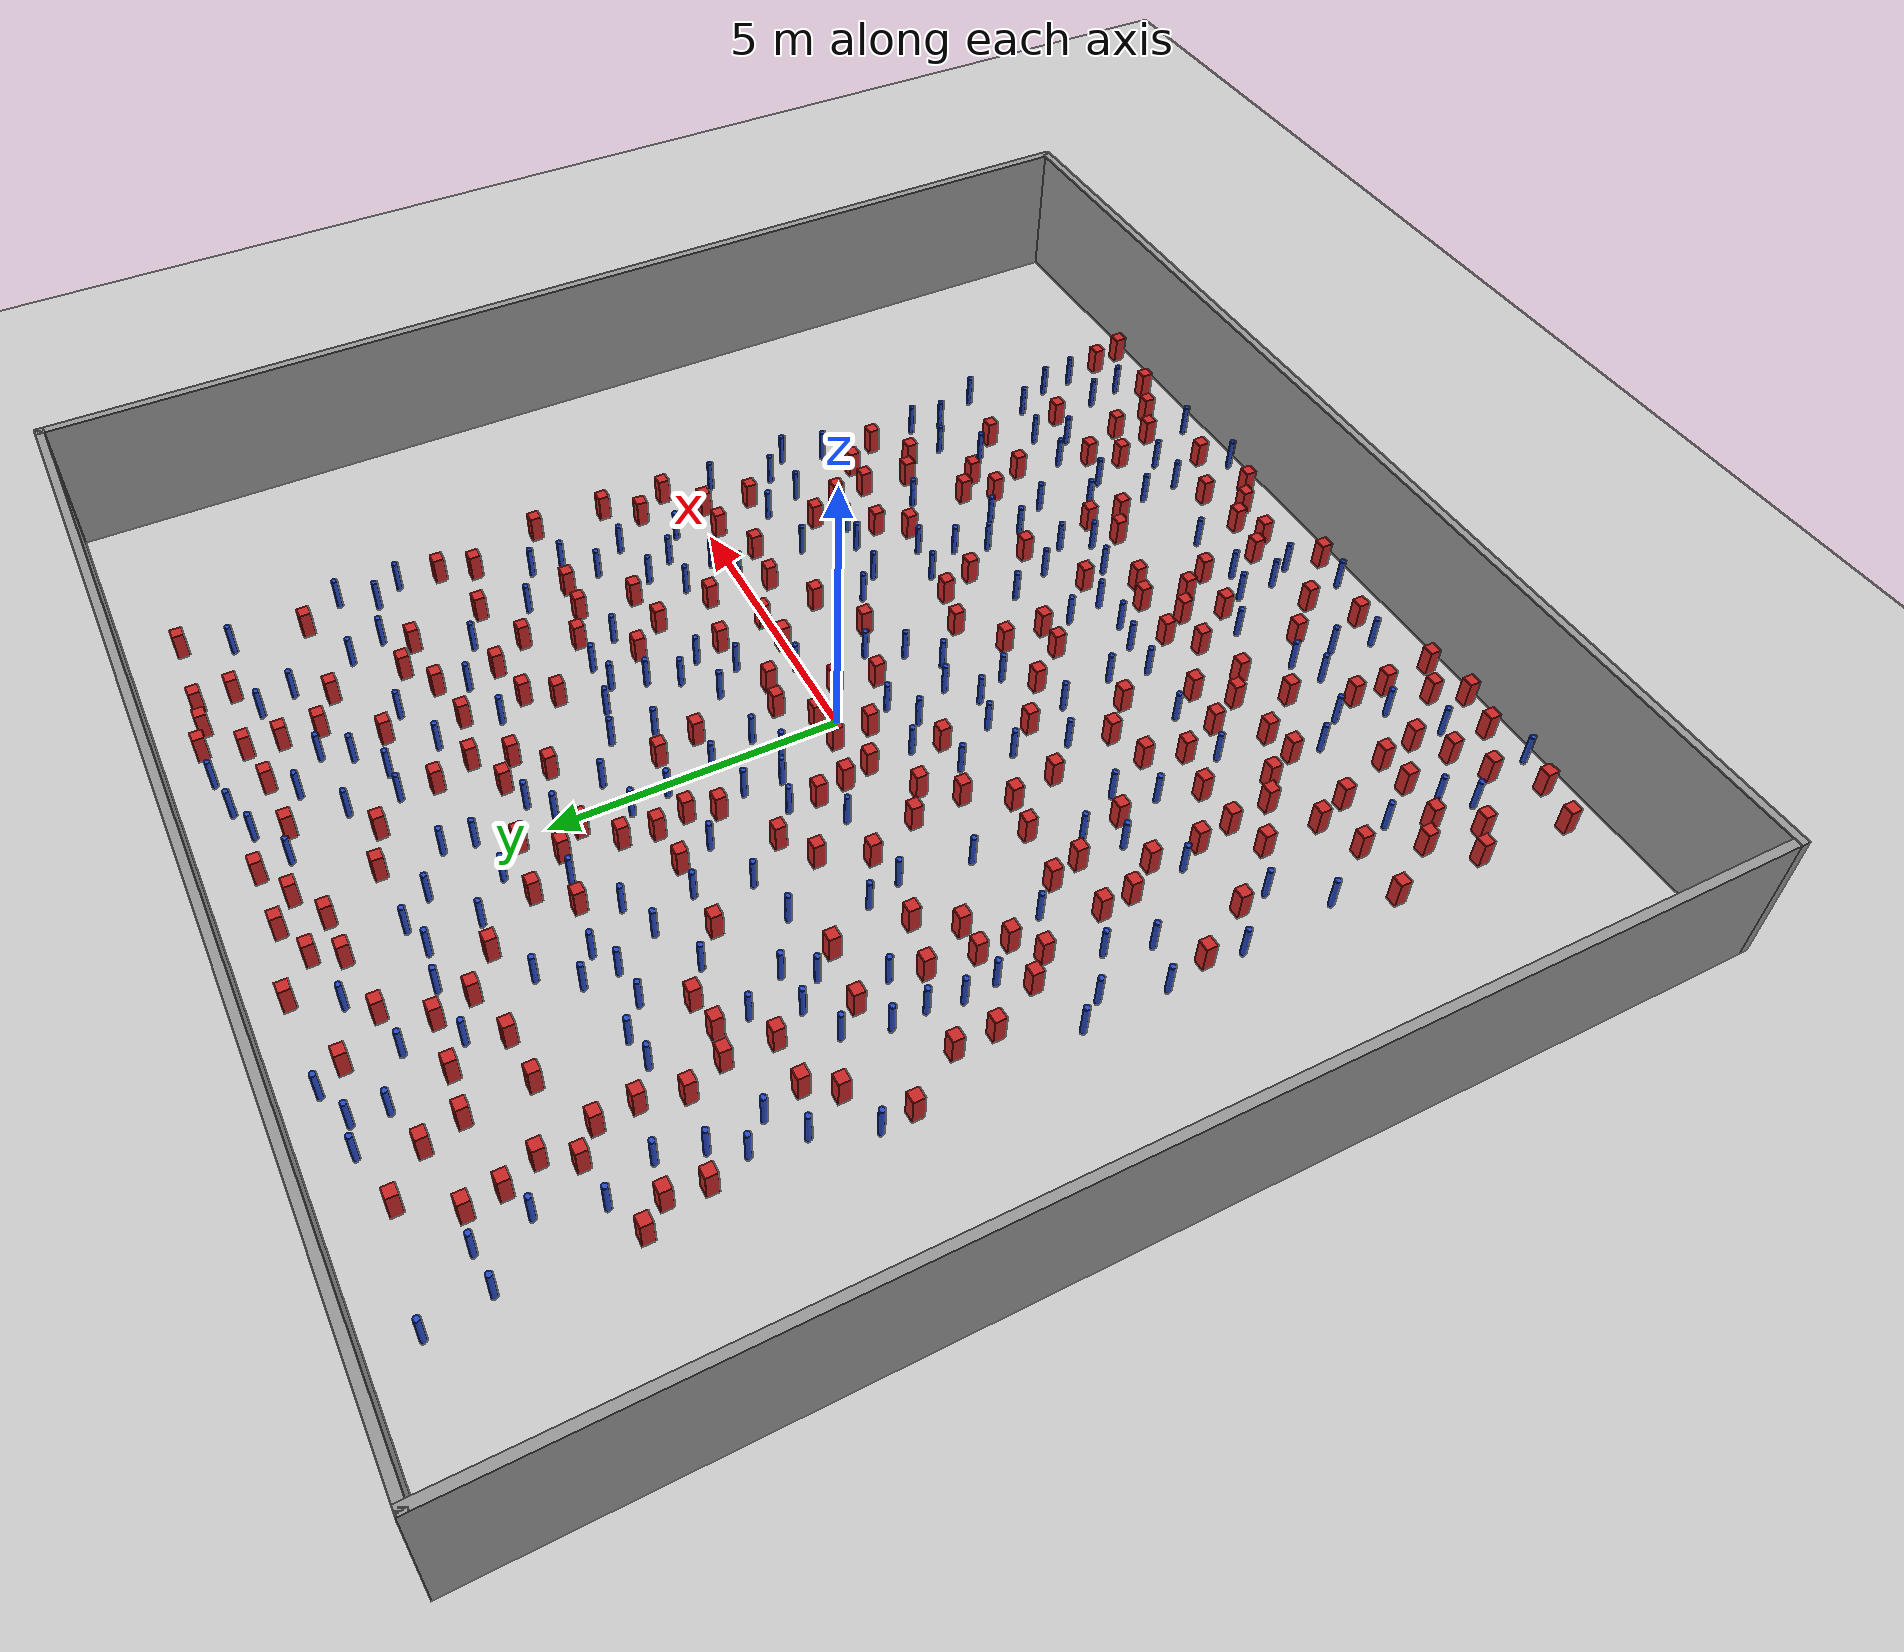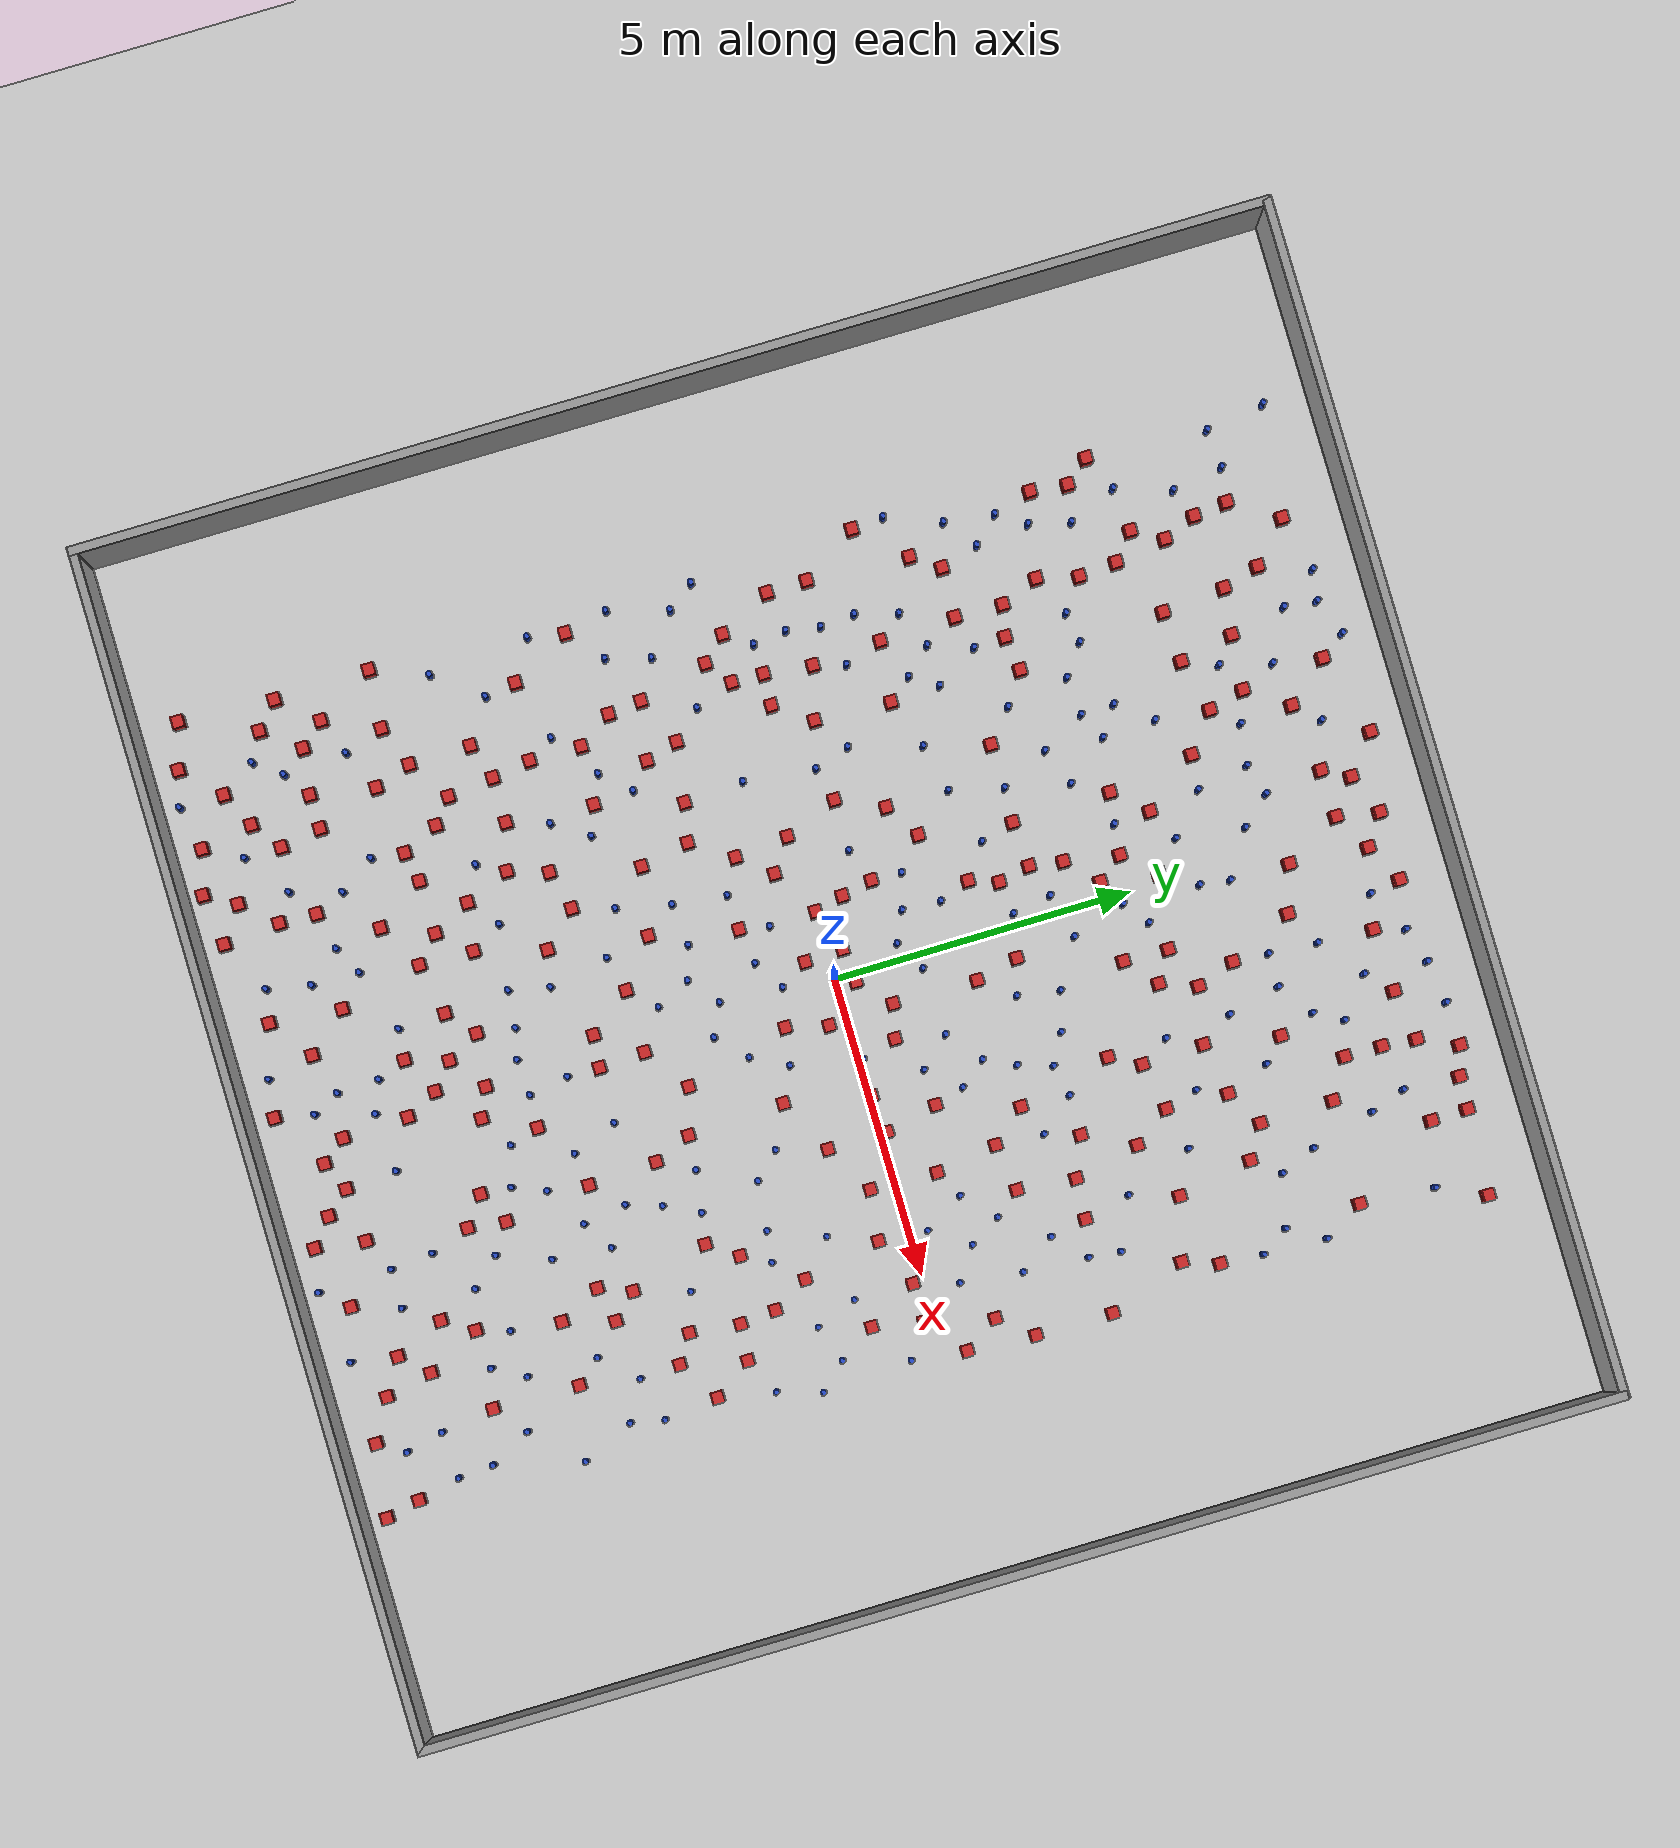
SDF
<sdf version="1.6">
 <world name="default">
  <light name="sun" type="directional">
   <pose>0 0 1000 0 -0 0</pose>
   <diffuse>0.8 0.8 0.8 1</diffuse>
   <specular>0.1 0.1 0.1 1</specular>
   <attenuation>
    <range>1000</range>
    <constant>0.9</constant>
    <linear>0.01</linear>
    <quadratic>0.001</quadratic>
   </attenuation>
   <direction>-0.5 0.5 -1</direction>
  </light>
  <model name="ground_plane">
   <static>1</static>
   <link name="link">
    <collision name="collision">
     <geometry><plane><normal>0 0 1</normal><size>100 100</size></plane></geometry>
     <surface><friction><ode><mu>100</mu><mu2>50</mu2></ode></friction></surface>
    </collision>
    <visual name="visual">
     <cast_shadows>0</cast_shadows>
     <geometry><plane><normal>0 0 1</normal><size>100 100</size></plane></geometry>
     <material>
      <ambient>1.0 1.0 1.0 1.0</ambient>
      <diffuse>0.8 0.8 0.8 1.0</diffuse>
      <specular>0.01 0.01 0.01 1.000000</specular>
     </material>
    </visual>
   </link>
  </model>
  <gravity>0 0 -9.8</gravity>
  <magnetic_field>6e-06 2.3e-05 -4.2e-05</magnetic_field>
  <atmosphere type="adiabatic"/>
  <physics name="default_physics" default="0" type="ode">
   <max_step_size>0.001</max_step_size>
   <real_time_factor>1</real_time_factor>
   <real_time_update_rate>1000</real_time_update_rate>
  </physics>
  <scene><ambient>0.4 0.4 0.4 1</ambient><background>0.7 0.7 0.7 1</background><shadows>1</shadows></scene>
  <spherical_coordinates>
   <surface_model>EARTH_WGS84</surface_model>
   <latitude_deg>0</latitude_deg>
   <longitude_deg>0</longitude_deg>
   <elevation>0</elevation>
   <heading_deg>0</heading_deg>
  </spherical_coordinates>
  <plugin name="gazebo_occupancy_map" filename="libgazebo_2Dmap_plugin.so">
   <map_resolution>0.05</map_resolution>
   <map_topic>generated_map</map_topic>
   <map_height>0.01</map_height>
   <map_size_x>50</map_size_x>
   <map_size_y>50</map_size_y>
  </plugin>
  <model name="NamedLocations">
   <static>true</static>
   <link name="DefaultStart"><pose>8.5 0 0 0 0 3.14</pose></link>
  </model>
  <model name="20x20_walls">
   <pose>0.044518 0.176112 0 0 -0 0</pose>
   <link name="Wall_1">
    <collision name="Wall_1_Collision">
     <geometry><box><size>20 0.15 2.5</size></box></geometry>
     <pose>0 0 1.25 0 -0 0</pose>
    </collision>
    <visual name="Wall_1_Visual">
     <pose>0 0 1.25 0 -0 0</pose>
     <geometry><box><size>20 0.15 2.5</size></box></geometry>
     <material>
      <script><uri>file://media/materials/scripts/gazebo.material</uri><name>Gazebo/Grey</name></script>
      <ambient>0.976471 0.992157 1 1</ambient>
     </material>
     <meta><layer>0</layer></meta>
    </visual>
    <pose>0 9.925 0 0 -0 0</pose>
   </link>
   <link name="Wall_3">
    <collision name="Wall_3_Collision">
     <geometry><box><size>20 0.15 2.5</size></box></geometry>
     <pose>0 0 1.25 0 -0 0</pose>
    </collision>
    <visual name="Wall_3_Visual">
     <pose>0 0 1.25 0 -0 0</pose>
     <geometry><box><size>20 0.15 2.5</size></box></geometry>
     <material>
      <script><uri>file://media/materials/scripts/gazebo.material</uri><name>Gazebo/Grey</name></script>
      <ambient>0.976471 0.992157 1 1</ambient>
     </material>
     <meta><layer>0</layer></meta>
    </visual>
    <pose>9.925 0 0 0 0 -1.5708</pose>
   </link>
   <link name="Wall_4">
    <collision name="Wall_4_Collision">
     <geometry><box><size>20 0.15 2.5</size></box></geometry>
     <pose>0 0 1.25 0 -0 0</pose>
    </collision>
    <visual name="Wall_4_Visual">
     <pose>0 0 1.25 0 -0 0</pose>
     <geometry><box><size>20 0.15 2.5</size></box></geometry>
     <material>
      <script><uri>file://media/materials/scripts/gazebo.material</uri><name>Gazebo/Grey</name></script>
      <ambient>0.976471 0.992157 1 1</ambient>
     </material>
     <meta><layer>0</layer></meta>
    </visual>
    <pose>0 -9.925 0 0 -0 3.14159</pose>
   </link>
   <link name="Wall_5">
    <collision name="Wall_5_Collision">
     <geometry><box><size>20 0.15 2.5</size></box></geometry>
     <pose>0 0 1.25 0 -0 0</pose>
    </collision>
    <visual name="Wall_5_Visual">
     <pose>0 0 1.25 0 -0 0</pose>
     <geometry><box><size>20 0.15 2.5</size></box></geometry>
     <material>
      <script><uri>file://media/materials/scripts/gazebo.material</uri><name>Gazebo/Grey</name></script>
      <ambient>0.976471 0.992157 1 1</ambient>
     </material>
     <meta><layer>0</layer></meta>
    </visual>
    <pose>-9.925 0 0 0 -0 1.5708</pose>
   </link>
   <static>1</static>
  </model>
  <model name="pole_obstacle0">
   <static>true</static>
   <pose>3.60144570011 -2.19980327123 7.38925637345e-09 -8.47170692798e-08 1.24976764939e-08 -1.74513093025e-07</pose>
   <link name="link">
    <pose>0 0 0.3 0 -0 0</pose>
    <inertial>
     <mass>1</mass>
     <inertia><ixx>0.145833</ixx><ixy>0</ixy><ixz>0</ixz><iyy>0.145833</iyy><iyz>0</iyz><izz>0.125</izz></inertia>
    </inertial>
    <collision name="collision">
     <geometry><cylinder><radius>0.05</radius><length>.6</length></cylinder></geometry>
    </collision>
    <visual name="visual">
     <geometry><cylinder><radius>0.05</radius><length>.6</length></cylinder></geometry>
     <material>
      <script><name>Gazebo/Blue</name><uri>file://media/materials/scripts/gazebo.material</uri></script>
     </material>
    </visual>
   </link>
  </model>
  <model name="pole_obstacle1">
   <static>true</static>
   <pose>4.51577572757 7.71158183973 7.38925637345e-09 -8.47170692796e-08 1.24976764786e-08 -1.74513093032e-07</pose>
   <link name="link">
    <pose>0 0 0.3 0 -0 0</pose>
    <inertial>
     <mass>1</mass>
     <inertia><ixx>0.145833</ixx><ixy>0</ixy><ixz>0</ixz><iyy>0.145833</iyy><iyz>0</iyz><izz>0.125</izz></inertia>
    </inertial>
    <collision name="collision">
     <geometry><cylinder><radius>0.05</radius><length>.6</length></cylinder></geometry>
    </collision>
    <visual name="visual">
     <geometry><cylinder><radius>0.05</radius><length>.6</length></cylinder></geometry>
     <material>
      <script><name>Gazebo/Blue</name><uri>file://media/materials/scripts/gazebo.material</uri></script>
     </material>
    </visual>
   </link>
  </model>
  <model name="square_post_obstacle0">
   <static>true</static>
   <pose>2.61286782644 -0.887590461791 1.91545236811e-07 -7.35059704564e-06 1.12565212e-07 2.39332434364e-05</pose>
   <link name="link">
    <pose>0 0 0.25 0 -0 0</pose>
    <inertial>
     <mass>100</mass>
     <inertia>
      <ixx>0.166667</ixx>
      <ixy>0</ixy>
      <ixz>0</ixz>
      <iyy>0.166667</iyy>
      <iyz>0</iyz>
      <izz>0.166667</izz>
     </inertia>
    </inertial>
    <collision name="collision"><geometry><box><size>.2 .2 .5</size></box></geometry></collision>
    <visual name="visual">
     <geometry><box><size>.2 .2 .5</size></box></geometry>
     <material>
      <script><name>Gazebo/Red</name><uri>file://media/materials/scripts/gazebo.material</uri></script>
     </material>
    </visual>
   </link>
  </model>
  <model name="square_post_obstacle1">
   <static>true</static>
   <pose>1.55641580418 4.99569527365 1.91545236811e-07 -7.35059704564e-06 1.12565212e-07 2.39332434364e-05</pose>
   <link name="link">
    <pose>0 0 0.25 0 -0 0</pose>
    <inertial>
     <mass>100</mass>
     <inertia>
      <ixx>0.166667</ixx>
      <ixy>0</ixy>
      <ixz>0</ixz>
      <iyy>0.166667</iyy>
      <iyz>0</iyz>
      <izz>0.166667</izz>
     </inertia>
    </inertial>
    <collision name="collision"><geometry><box><size>.2 .2 .5</size></box></geometry></collision>
    <visual name="visual">
     <geometry><box><size>.2 .2 .5</size></box></geometry>
     <material>
      <script><name>Gazebo/Red</name><uri>file://media/materials/scripts/gazebo.material</uri></script>
     </material>
    </visual>
   </link>
  </model>
  <model name="pole_obstacle2">
   <static>true</static>
   <pose>-1.20993344297 -6.98747490904 7.38925637345e-09 -8.47170692799e-08 1.24976765033e-08 -1.74513093018e-07</pose>
   <link name="link">
    <pose>0 0 0.3 0 -0 0</pose>
    <inertial>
     <mass>1</mass>
     <inertia><ixx>0.145833</ixx><ixy>0</ixy><ixz>0</ixz><iyy>0.145833</iyy><iyz>0</iyz><izz>0.125</izz></inertia>
    </inertial>
    <collision name="collision">
     <geometry><cylinder><radius>0.05</radius><length>.6</length></cylinder></geometry>
    </collision>
    <visual name="visual">
     <geometry><cylinder><radius>0.05</radius><length>.6</length></cylinder></geometry>
     <material>
      <script><name>Gazebo/Blue</name><uri>file://media/materials/scripts/gazebo.material</uri></script>
     </material>
    </visual>
   </link>
  </model>
  <model name="pole_obstacle3">
   <static>true</static>
   <pose>-5.56863319645 0.264649890705 7.38925637345e-09 -8.47170692799e-08 1.24976765028e-08 -1.74513093019e-07</pose>
   <link name="link">
    <pose>0 0 0.3 0 -0 0</pose>
    <inertial>
     <mass>1</mass>
     <inertia><ixx>0.145833</ixx><ixy>0</ixy><ixz>0</ixz><iyy>0.145833</iyy><iyz>0</iyz><izz>0.125</izz></inertia>
    </inertial>
    <collision name="collision">
     <geometry><cylinder><radius>0.05</radius><length>.6</length></cylinder></geometry>
    </collision>
    <visual name="visual">
     <geometry><cylinder><radius>0.05</radius><length>.6</length></cylinder></geometry>
     <material>
      <script><name>Gazebo/Blue</name><uri>file://media/materials/scripts/gazebo.material</uri></script>
     </material>
    </visual>
   </link>
  </model>
  <model name="pole_obstacle4">
   <static>true</static>
   <pose>-1.33974856202 1.51738444277 7.38925637345e-09 -8.471706928e-08 1.24976765079e-08 -1.74513093017e-07</pose>
   <link name="link">
    <pose>0 0 0.3 0 -0 0</pose>
    <inertial>
     <mass>1</mass>
     <inertia><ixx>0.145833</ixx><ixy>0</ixy><ixz>0</ixz><iyy>0.145833</iyy><iyz>0</iyz><izz>0.125</izz></inertia>
    </inertial>
    <collision name="collision">
     <geometry><cylinder><radius>0.05</radius><length>.6</length></cylinder></geometry>
    </collision>
    <visual name="visual">
     <geometry><cylinder><radius>0.05</radius><length>.6</length></cylinder></geometry>
     <material>
      <script><name>Gazebo/Blue</name><uri>file://media/materials/scripts/gazebo.material</uri></script>
     </material>
    </visual>
   </link>
  </model>
  <model name="pole_obstacle5">
   <static>true</static>
   <pose>-2.55545576184 6.15539351337 7.38925637345e-09 -8.47170692798e-08 1.24976765033e-08 -1.74513093019e-07</pose>
   <link name="link">
    <pose>0 0 0.3 0 -0 0</pose>
    <inertial>
     <mass>1</mass>
     <inertia><ixx>0.145833</ixx><ixy>0</ixy><ixz>0</ixz><iyy>0.145833</iyy><iyz>0</iyz><izz>0.125</izz></inertia>
    </inertial>
    <collision name="collision">
     <geometry><cylinder><radius>0.05</radius><length>.6</length></cylinder></geometry>
    </collision>
    <visual name="visual">
     <geometry><cylinder><radius>0.05</radius><length>.6</length></cylinder></geometry>
     <material>
      <script><name>Gazebo/Blue</name><uri>file://media/materials/scripts/gazebo.material</uri></script>
     </material>
    </visual>
   </link>
  </model>
  <model name="pole_obstacle6">
   <static>true</static>
   <pose>-0.362529204652 -2.86343101517 7.38925637345e-09 -8.471706928e-08 1.24976765084e-08 -1.74513093017e-07</pose>
   <link name="link">
    <pose>0 0 0.3 0 -0 0</pose>
    <inertial>
     <mass>1</mass>
     <inertia><ixx>0.145833</ixx><ixy>0</ixy><ixz>0</ixz><iyy>0.145833</iyy><iyz>0</iyz><izz>0.125</izz></inertia>
    </inertial>
    <collision name="collision">
     <geometry><cylinder><radius>0.05</radius><length>.6</length></cylinder></geometry>
    </collision>
    <visual name="visual">
     <geometry><cylinder><radius>0.05</radius><length>.6</length></cylinder></geometry>
     <material>
      <script><name>Gazebo/Blue</name><uri>file://media/materials/scripts/gazebo.material</uri></script>
     </material>
    </visual>
   </link>
  </model>
  <model name="square_post_obstacle2">
   <static>true</static>
   <pose>-1.51511103685 -2.70008795254 1.91545236811e-07 -7.35059704564e-06 1.12565212e-07 2.39332434364e-05</pose>
   <link name="link">
    <pose>0 0 0.25 0 -0 0</pose>
    <inertial>
     <mass>100</mass>
     <inertia>
      <ixx>0.166667</ixx>
      <ixy>0</ixy>
      <ixz>0</ixz>
      <iyy>0.166667</iyy>
      <iyz>0</iyz>
      <izz>0.166667</izz>
     </inertia>
    </inertial>
    <collision name="collision"><geometry><box><size>.2 .2 .5</size></box></geometry></collision>
    <visual name="visual">
     <geometry><box><size>.2 .2 .5</size></box></geometry>
     <material>
      <script><name>Gazebo/Red</name><uri>file://media/materials/scripts/gazebo.material</uri></script>
     </material>
    </visual>
   </link>
  </model>
  <model name="square_post_obstacle3">
   <static>true</static>
   <pose>0.29430283739 7.57362399298 1.91545236811e-07 -7.35059704564e-06 1.12565212e-07 2.39332434364e-05</pose>
   <link name="link">
    <pose>0 0 0.25 0 -0 0</pose>
    <inertial>
     <mass>100</mass>
     <inertia>
      <ixx>0.166667</ixx>
      <ixy>0</ixy>
      <ixz>0</ixz>
      <iyy>0.166667</iyy>
      <iyz>0</iyz>
      <izz>0.166667</izz>
     </inertia>
    </inertial>
    <collision name="collision"><geometry><box><size>.2 .2 .5</size></box></geometry></collision>
    <visual name="visual">
     <geometry><box><size>.2 .2 .5</size></box></geometry>
     <material>
      <script><name>Gazebo/Red</name><uri>file://media/materials/scripts/gazebo.material</uri></script>
     </material>
    </visual>
   </link>
  </model>
  <model name="square_post_obstacle4">
   <static>true</static>
   <pose>-2.33833968254 -0.990381652567 1.91545236811e-07 -7.35059704564e-06 1.12565212e-07 2.39332434364e-05</pose>
   <link name="link">
    <pose>0 0 0.25 0 -0 0</pose>
    <inertial>
     <mass>100</mass>
     <inertia>
      <ixx>0.166667</ixx>
      <ixy>0</ixy>
      <ixz>0</ixz>
      <iyy>0.166667</iyy>
      <iyz>0</iyz>
      <izz>0.166667</izz>
     </inertia>
    </inertial>
    <collision name="collision"><geometry><box><size>.2 .2 .5</size></box></geometry></collision>
    <visual name="visual">
     <geometry><box><size>.2 .2 .5</size></box></geometry>
     <material>
      <script><name>Gazebo/Red</name><uri>file://media/materials/scripts/gazebo.material</uri></script>
     </material>
    </visual>
   </link>
  </model>
  <model name="pole_obstacle7">
   <static>true</static>
   <pose>-5.82277661758 -1.37810416968 7.38925637345e-09 -8.471706928e-08 1.24976765134e-08 -1.74513093015e-07</pose>
   <link name="link">
    <pose>0 0 0.3 0 -0 0</pose>
    <inertial>
     <mass>1</mass>
     <inertia><ixx>0.145833</ixx><ixy>0</ixy><ixz>0</ixz><iyy>0.145833</iyy><iyz>0</iyz><izz>0.125</izz></inertia>
    </inertial>
    <collision name="collision">
     <geometry><cylinder><radius>0.05</radius><length>.6</length></cylinder></geometry>
    </collision>
    <visual name="visual">
     <geometry><cylinder><radius>0.05</radius><length>.6</length></cylinder></geometry>
     <material>
      <script><name>Gazebo/Blue</name><uri>file://media/materials/scripts/gazebo.material</uri></script>
     </material>
    </visual>
   </link>
  </model>
  <model name="pole_obstacle8">
   <static>true</static>
   <pose>-1.16569219605 -4.44366886256 7.38925637345e-09 -8.47170692799e-08 1.24976765033e-08 -1.74513093018e-07</pose>
   <link name="link">
    <pose>0 0 0.3 0 -0 0</pose>
    <inertial>
     <mass>1</mass>
     <inertia><ixx>0.145833</ixx><ixy>0</ixy><ixz>0</ixz><iyy>0.145833</iyy><iyz>0</iyz><izz>0.125</izz></inertia>
    </inertial>
    <collision name="collision">
     <geometry><cylinder><radius>0.05</radius><length>.6</length></cylinder></geometry>
    </collision>
    <visual name="visual">
     <geometry><cylinder><radius>0.05</radius><length>.6</length></cylinder></geometry>
     <material>
      <script><name>Gazebo/Blue</name><uri>file://media/materials/scripts/gazebo.material</uri></script>
     </material>
    </visual>
   </link>
  </model>
  <model name="square_post_obstacle5">
   <static>true</static>
   <pose>3.59141695978 8.73314911873 1.91545236811e-07 -7.35059704564e-06 1.12565212e-07 2.39332434364e-05</pose>
   <link name="link">
    <pose>0 0 0.25 0 -0 0</pose>
    <inertial>
     <mass>100</mass>
     <inertia>
      <ixx>0.166667</ixx>
      <ixy>0</ixy>
      <ixz>0</ixz>
      <iyy>0.166667</iyy>
      <iyz>0</iyz>
      <izz>0.166667</izz>
     </inertia>
    </inertial>
    <collision name="collision"><geometry><box><size>.2 .2 .5</size></box></geometry></collision>
    <visual name="visual">
     <geometry><box><size>.2 .2 .5</size></box></geometry>
     <material>
      <script><name>Gazebo/Red</name><uri>file://media/materials/scripts/gazebo.material</uri></script>
     </material>
    </visual>
   </link>
  </model>
  <model name="square_post_obstacle6">
   <static>true</static>
   <pose>-3.41137875283 -6.00020693053 1.91545236811e-07 -7.35059704564e-06 1.12565212e-07 2.39332434364e-05</pose>
   <link name="link">
    <pose>0 0 0.25 0 -0 0</pose>
    <inertial>
     <mass>100</mass>
     <inertia>
      <ixx>0.166667</ixx>
      <ixy>0</ixy>
      <ixz>0</ixz>
      <iyy>0.166667</iyy>
      <iyz>0</iyz>
      <izz>0.166667</izz>
     </inertia>
    </inertial>
    <collision name="collision"><geometry><box><size>.2 .2 .5</size></box></geometry></collision>
    <visual name="visual">
     <geometry><box><size>.2 .2 .5</size></box></geometry>
     <material>
      <script><name>Gazebo/Red</name><uri>file://media/materials/scripts/gazebo.material</uri></script>
     </material>
    </visual>
   </link>
  </model>
  <model name="square_post_obstacle7">
   <static>true</static>
   <pose>-2.42755309524 1.5770509396 1.91545236811e-07 -7.35059704564e-06 1.12565212e-07 2.39332434364e-05</pose>
   <link name="link">
    <pose>0 0 0.25 0 -0 0</pose>
    <inertial>
     <mass>100</mass>
     <inertia>
      <ixx>0.166667</ixx>
      <ixy>0</ixy>
      <ixz>0</ixz>
      <iyy>0.166667</iyy>
      <iyz>0</iyz>
      <izz>0.166667</izz>
     </inertia>
    </inertial>
    <collision name="collision"><geometry><box><size>.2 .2 .5</size></box></geometry></collision>
    <visual name="visual">
     <geometry><box><size>.2 .2 .5</size></box></geometry>
     <material>
      <script><name>Gazebo/Red</name><uri>file://media/materials/scripts/gazebo.material</uri></script>
     </material>
    </visual>
   </link>
  </model>
  <model name="pole_obstacle9">
   <static>true</static>
   <pose>-2.73869889922 -7.59376571259 7.38925637345e-09 -8.47170692798e-08 1.24976765033e-08 -1.74513093019e-07</pose>
   <link name="link">
    <pose>0 0 0.3 0 -0 0</pose>
    <inertial>
     <mass>1</mass>
     <inertia><ixx>0.145833</ixx><ixy>0</ixy><ixz>0</ixz><iyy>0.145833</iyy><iyz>0</iyz><izz>0.125</izz></inertia>
    </inertial>
    <collision name="collision">
     <geometry><cylinder><radius>0.05</radius><length>.6</length></cylinder></geometry>
    </collision>
    <visual name="visual">
     <geometry><cylinder><radius>0.05</radius><length>.6</length></cylinder></geometry>
     <material>
      <script><name>Gazebo/Blue</name><uri>file://media/materials/scripts/gazebo.material</uri></script>
     </material>
    </visual>
   </link>
  </model>
  <model name="pole_obstacle10">
   <static>true</static>
   <pose>3.1703029839 -6.97297233264 7.38925637345e-09 -8.47170692798e-08 1.24976765033e-08 -1.74513093019e-07</pose>
   <link name="link">
    <pose>0 0 0.3 0 -0 0</pose>
    <inertial>
     <mass>1</mass>
     <inertia><ixx>0.145833</ixx><ixy>0</ixy><ixz>0</ixz><iyy>0.145833</iyy><iyz>0</iyz><izz>0.125</izz></inertia>
    </inertial>
    <collision name="collision">
     <geometry><cylinder><radius>0.05</radius><length>.6</length></cylinder></geometry>
    </collision>
    <visual name="visual">
     <geometry><cylinder><radius>0.05</radius><length>.6</length></cylinder></geometry>
     <material>
      <script><name>Gazebo/Blue</name><uri>file://media/materials/scripts/gazebo.material</uri></script>
     </material>
    </visual>
   </link>
  </model>
  <model name="pole_obstacle11">
   <static>true</static>
   <pose>0.983680390515 -7.67062327463 7.38925637345e-09 -8.471706928e-08 1.24976765144e-08 -1.74513093012e-07</pose>
   <link name="link">
    <pose>0 0 0.3 0 -0 0</pose>
    <inertial>
     <mass>1</mass>
     <inertia><ixx>0.145833</ixx><ixy>0</ixy><ixz>0</ixz><iyy>0.145833</iyy><iyz>0</iyz><izz>0.125</izz></inertia>
    </inertial>
    <collision name="collision">
     <geometry><cylinder><radius>0.05</radius><length>.6</length></cylinder></geometry>
    </collision>
    <visual name="visual">
     <geometry><cylinder><radius>0.05</radius><length>.6</length></cylinder></geometry>
     <material>
      <script><name>Gazebo/Blue</name><uri>file://media/materials/scripts/gazebo.material</uri></script>
     </material>
    </visual>
   </link>
  </model>
  <model name="pole_obstacle12">
   <static>true</static>
   <pose>1.10796184703 -5.77790363404 7.38925637345e-09 -8.47170692799e-08 1.24976765033e-08 -1.74513093018e-07</pose>
   <link name="link">
    <pose>0 0 0.3 0 -0 0</pose>
    <inertial>
     <mass>1</mass>
     <inertia><ixx>0.145833</ixx><ixy>0</ixy><ixz>0</ixz><iyy>0.145833</iyy><iyz>0</iyz><izz>0.125</izz></inertia>
    </inertial>
    <collision name="collision">
     <geometry><cylinder><radius>0.05</radius><length>.6</length></cylinder></geometry>
    </collision>
    <visual name="visual">
     <geometry><cylinder><radius>0.05</radius><length>.6</length></cylinder></geometry>
     <material>
      <script><name>Gazebo/Blue</name><uri>file://media/materials/scripts/gazebo.material</uri></script>
     </material>
    </visual>
   </link>
  </model>
  <model name="square_post_obstacle8">
   <static>true</static>
   <pose>-2.62218615921 7.6551377625 1.91545236811e-07 -7.35059704564e-06 1.12565212e-07 2.39332434364e-05</pose>
   <link name="link">
    <pose>0 0 0.25 0 -0 0</pose>
    <inertial>
     <mass>100</mass>
     <inertia>
      <ixx>0.166667</ixx>
      <ixy>0</ixy>
      <ixz>0</ixz>
      <iyy>0.166667</iyy>
      <iyz>0</iyz>
      <izz>0.166667</izz>
     </inertia>
    </inertial>
    <collision name="collision"><geometry><box><size>.2 .2 .5</size></box></geometry></collision>
    <visual name="visual">
     <geometry><box><size>.2 .2 .5</size></box></geometry>
     <material>
      <script><name>Gazebo/Red</name><uri>file://media/materials/scripts/gazebo.material</uri></script>
     </material>
    </visual>
   </link>
  </model>
  <model name="square_post_obstacle9">
   <static>true</static>
   <pose>3.30981524049 1.72723753832 1.91545236811e-07 -7.35059704564e-06 1.12565212e-07 2.39332434364e-05</pose>
   <link name="link">
    <pose>0 0 0.25 0 -0 0</pose>
    <inertial>
     <mass>100</mass>
     <inertia>
      <ixx>0.166667</ixx>
      <ixy>0</ixy>
      <ixz>0</ixz>
      <iyy>0.166667</iyy>
      <iyz>0</iyz>
      <izz>0.166667</izz>
     </inertia>
    </inertial>
    <collision name="collision"><geometry><box><size>.2 .2 .5</size></box></geometry></collision>
    <visual name="visual">
     <geometry><box><size>.2 .2 .5</size></box></geometry>
     <material>
      <script><name>Gazebo/Red</name><uri>file://media/materials/scripts/gazebo.material</uri></script>
     </material>
    </visual>
   </link>
  </model>
  <model name="pole_obstacle13">
   <static>true</static>
   <pose>-6.49323973587 4.6111920208 7.38925637345e-09 -8.47170692796e-08 1.24976764786e-08 -1.74513093032e-07</pose>
   <link name="link">
    <pose>0 0 0.3 0 -0 0</pose>
    <inertial>
     <mass>1</mass>
     <inertia><ixx>0.145833</ixx><ixy>0</ixy><ixz>0</ixz><iyy>0.145833</iyy><iyz>0</iyz><izz>0.125</izz></inertia>
    </inertial>
    <collision name="collision">
     <geometry><cylinder><radius>0.05</radius><length>.6</length></cylinder></geometry>
    </collision>
    <visual name="visual">
     <geometry><cylinder><radius>0.05</radius><length>.6</length></cylinder></geometry>
     <material>
      <script><name>Gazebo/Blue</name><uri>file://media/materials/scripts/gazebo.material</uri></script>
     </material>
    </visual>
   </link>
  </model>
  <model name="square_post_obstacle10">
   <static>true</static>
   <pose>6.36440647438 0.349848405972 1.91545236811e-07 -7.35059704564e-06 1.12565212e-07 2.39332434364e-05</pose>
   <link name="link">
    <pose>0 0 0.25 0 -0 0</pose>
    <inertial>
     <mass>100</mass>
     <inertia>
      <ixx>0.166667</ixx>
      <ixy>0</ixy>
      <ixz>0</ixz>
      <iyy>0.166667</iyy>
      <iyz>0</iyz>
      <izz>0.166667</izz>
     </inertia>
    </inertial>
    <collision name="collision"><geometry><box><size>.2 .2 .5</size></box></geometry></collision>
    <visual name="visual">
     <geometry><box><size>.2 .2 .5</size></box></geometry>
     <material>
      <script><name>Gazebo/Red</name><uri>file://media/materials/scripts/gazebo.material</uri></script>
     </material>
    </visual>
   </link>
  </model>
  <model name="square_post_obstacle11">
   <static>true</static>
   <pose>5.94937893655 -3.72242752347 1.91545236811e-07 -7.35059704564e-06 1.12565212e-07 2.39332434364e-05</pose>
   <link name="link">
    <pose>0 0 0.25 0 -0 0</pose>
    <inertial>
     <mass>100</mass>
     <inertia>
      <ixx>0.166667</ixx>
      <ixy>0</ixy>
      <ixz>0</ixz>
      <iyy>0.166667</iyy>
      <iyz>0</iyz>
      <izz>0.166667</izz>
     </inertia>
    </inertial>
    <collision name="collision"><geometry><box><size>.2 .2 .5</size></box></geometry></collision>
    <visual name="visual">
     <geometry><box><size>.2 .2 .5</size></box></geometry>
     <material>
      <script><name>Gazebo/Red</name><uri>file://media/materials/scripts/gazebo.material</uri></script>
     </material>
    </visual>
   </link>
  </model>
  <model name="pole_obstacle14">
   <static>true</static>
   <pose>6.1337911628 -2.78618454168 7.38925637345e-09 -8.47170692798e-08 1.24976764937e-08 -1.74513093023e-07</pose>
   <link name="link">
    <pose>0 0 0.3 0 -0 0</pose>
    <inertial>
     <mass>1</mass>
     <inertia><ixx>0.145833</ixx><ixy>0</ixy><ixz>0</ixz><iyy>0.145833</iyy><iyz>0</iyz><izz>0.125</izz></inertia>
    </inertial>
    <collision name="collision">
     <geometry><cylinder><radius>0.05</radius><length>.6</length></cylinder></geometry>
    </collision>
    <visual name="visual">
     <geometry><cylinder><radius>0.05</radius><length>.6</length></cylinder></geometry>
     <material>
      <script><name>Gazebo/Blue</name><uri>file://media/materials/scripts/gazebo.material</uri></script>
     </material>
    </visual>
   </link>
  </model>
  <model name="pole_obstacle15">
   <static>true</static>
   <pose>2.78884678724 -2.11389978654 7.38925637345e-09 -8.47170692798e-08 1.24976764939e-08 -1.74513093025e-07</pose>
   <link name="link">
    <pose>0 0 0.3 0 -0 0</pose>
    <inertial>
     <mass>1</mass>
     <inertia><ixx>0.145833</ixx><ixy>0</ixy><ixz>0</ixz><iyy>0.145833</iyy><iyz>0</iyz><izz>0.125</izz></inertia>
    </inertial>
    <collision name="collision">
     <geometry><cylinder><radius>0.05</radius><length>.6</length></cylinder></geometry>
    </collision>
    <visual name="visual">
     <geometry><cylinder><radius>0.05</radius><length>.6</length></cylinder></geometry>
     <material>
      <script><name>Gazebo/Blue</name><uri>file://media/materials/scripts/gazebo.material</uri></script>
     </material>
    </visual>
   </link>
  </model>
  <model name="square_post_obstacle12">
   <static>true</static>
   <pose>-2.92349941029 3.49321130569 1.91545236811e-07 -7.35059704564e-06 1.12565212e-07 2.39332434364e-05</pose>
   <link name="link">
    <pose>0 0 0.25 0 -0 0</pose>
    <inertial>
     <mass>100</mass>
     <inertia>
      <ixx>0.166667</ixx>
      <ixy>0</ixy>
      <ixz>0</ixz>
      <iyy>0.166667</iyy>
      <iyz>0</iyz>
      <izz>0.166667</izz>
     </inertia>
    </inertial>
    <collision name="collision"><geometry><box><size>.2 .2 .5</size></box></geometry></collision>
    <visual name="visual">
     <geometry><box><size>.2 .2 .5</size></box></geometry>
     <material>
      <script><name>Gazebo/Red</name><uri>file://media/materials/scripts/gazebo.material</uri></script>
     </material>
    </visual>
   </link>
  </model>
  <model name="pole_obstacle16">
   <static>true</static>
   <pose>-1.78811014699 8.73780158 7.38925637345e-09 -8.47170692798e-08 1.24976764881e-08 -1.74513093027e-07</pose>
   <link name="link">
    <pose>0 0 0.3 0 -0 0</pose>
    <inertial>
     <mass>1</mass>
     <inertia><ixx>0.145833</ixx><ixy>0</ixy><ixz>0</ixz><iyy>0.145833</iyy><iyz>0</iyz><izz>0.125</izz></inertia>
    </inertial>
    <collision name="collision">
     <geometry><cylinder><radius>0.05</radius><length>.6</length></cylinder></geometry>
    </collision>
    <visual name="visual">
     <geometry><cylinder><radius>0.05</radius><length>.6</length></cylinder></geometry>
     <material>
      <script><name>Gazebo/Blue</name><uri>file://media/materials/scripts/gazebo.material</uri></script>
     </material>
    </visual>
   </link>
  </model>
  <model name="pole_obstacle17">
   <static>true</static>
   <pose>-2.18803937398 3.50886548616 7.38925637345e-09 -8.47170692798e-08 1.24976764939e-08 -1.74513093025e-07</pose>
   <link name="link">
    <pose>0 0 0.3 0 -0 0</pose>
    <inertial>
     <mass>1</mass>
     <inertia><ixx>0.145833</ixx><ixy>0</ixy><ixz>0</ixz><iyy>0.145833</iyy><iyz>0</iyz><izz>0.125</izz></inertia>
    </inertial>
    <collision name="collision">
     <geometry><cylinder><radius>0.05</radius><length>.6</length></cylinder></geometry>
    </collision>
    <visual name="visual">
     <geometry><cylinder><radius>0.05</radius><length>.6</length></cylinder></geometry>
     <material>
      <script><name>Gazebo/Blue</name><uri>file://media/materials/scripts/gazebo.material</uri></script>
     </material>
    </visual>
   </link>
  </model>
  <model name="square_post_obstacle13">
   <static>true</static>
   <pose>-0.148828660306 5.50181008379 1.91545236811e-07 -7.35059704564e-06 1.12565212e-07 2.39332434364e-05</pose>
   <link name="link">
    <pose>0 0 0.25 0 -0 0</pose>
    <inertial>
     <mass>100</mass>
     <inertia>
      <ixx>0.166667</ixx>
      <ixy>0</ixy>
      <ixz>0</ixz>
      <iyy>0.166667</iyy>
      <iyz>0</iyz>
      <izz>0.166667</izz>
     </inertia>
    </inertial>
    <collision name="collision"><geometry><box><size>.2 .2 .5</size></box></geometry></collision>
    <visual name="visual">
     <geometry><box><size>.2 .2 .5</size></box></geometry>
     <material>
      <script><name>Gazebo/Red</name><uri>file://media/materials/scripts/gazebo.material</uri></script>
     </material>
    </visual>
   </link>
  </model>
  <model name="pole_obstacle18">
   <static>true</static>
   <pose>-3.83459840023 -8.06982385041 7.38925637345e-09 -8.47170692793e-08 1.24976764408e-08 -1.74513093041e-07</pose>
   <link name="link">
    <pose>0 0 0.3 0 -0 0</pose>
    <inertial>
     <mass>1</mass>
     <inertia><ixx>0.145833</ixx><ixy>0</ixy><ixz>0</ixz><iyy>0.145833</iyy><iyz>0</iyz><izz>0.125</izz></inertia>
    </inertial>
    <collision name="collision">
     <geometry><cylinder><radius>0.05</radius><length>.6</length></cylinder></geometry>
    </collision>
    <visual name="visual">
     <geometry><cylinder><radius>0.05</radius><length>.6</length></cylinder></geometry>
     <material>
      <script><name>Gazebo/Blue</name><uri>file://media/materials/scripts/gazebo.material</uri></script>
     </material>
    </visual>
   </link>
  </model>
  <model name="square_post_obstacle14">
   <static>true</static>
   <pose>-4.4794146209 8.45498827189 1.91545236811e-07 -7.35059704564e-06 1.12565212e-07 2.39332434364e-05</pose>
   <link name="link">
    <pose>0 0 0.25 0 -0 0</pose>
    <inertial>
     <mass>100</mass>
     <inertia>
      <ixx>0.166667</ixx>
      <ixy>0</ixy>
      <ixz>0</ixz>
      <iyy>0.166667</iyy>
      <iyz>0</iyz>
      <izz>0.166667</izz>
     </inertia>
    </inertial>
    <collision name="collision"><geometry><box><size>.2 .2 .5</size></box></geometry></collision>
    <visual name="visual">
     <geometry><box><size>.2 .2 .5</size></box></geometry>
     <material>
      <script><name>Gazebo/Red</name><uri>file://media/materials/scripts/gazebo.material</uri></script>
     </material>
    </visual>
   </link>
  </model>
  <model name="pole_obstacle19">
   <static>true</static>
   <pose>-2.98874472671 5.58375871275 7.38925637345e-09 -8.47170692798e-08 1.24976765033e-08 -1.74513093019e-07</pose>
   <link name="link">
    <pose>0 0 0.3 0 -0 0</pose>
    <inertial>
     <mass>1</mass>
     <inertia><ixx>0.145833</ixx><ixy>0</ixy><ixz>0</ixz><iyy>0.145833</iyy><iyz>0</iyz><izz>0.125</izz></inertia>
    </inertial>
    <collision name="collision">
     <geometry><cylinder><radius>0.05</radius><length>.6</length></cylinder></geometry>
    </collision>
    <visual name="visual">
     <geometry><cylinder><radius>0.05</radius><length>.6</length></cylinder></geometry>
     <material>
      <script><name>Gazebo/Blue</name><uri>file://media/materials/scripts/gazebo.material</uri></script>
     </material>
    </visual>
   </link>
  </model>
  <model name="square_post_obstacle15">
   <static>true</static>
   <pose>4.94086010703 4.34586414103 1.91545236811e-07 -7.35059704564e-06 1.12565212e-07 2.39332434364e-05</pose>
   <link name="link">
    <pose>0 0 0.25 0 -0 0</pose>
    <inertial>
     <mass>100</mass>
     <inertia>
      <ixx>0.166667</ixx>
      <ixy>0</ixy>
      <ixz>0</ixz>
      <iyy>0.166667</iyy>
      <iyz>0</iyz>
      <izz>0.166667</izz>
     </inertia>
    </inertial>
    <collision name="collision"><geometry><box><size>.2 .2 .5</size></box></geometry></collision>
    <visual name="visual">
     <geometry><box><size>.2 .2 .5</size></box></geometry>
     <material>
      <script><name>Gazebo/Red</name><uri>file://media/materials/scripts/gazebo.material</uri></script>
     </material>
    </visual>
   </link>
  </model>
  <model name="square_post_obstacle16">
   <static>true</static>
   <pose>-1.23818793762 -6.20411669702 1.91545236811e-07 -7.35059704564e-06 1.12565212e-07 2.39332434364e-05</pose>
   <link name="link">
    <pose>0 0 0.25 0 -0 0</pose>
    <inertial>
     <mass>100</mass>
     <inertia>
      <ixx>0.166667</ixx>
      <ixy>0</ixy>
      <ixz>0</ixz>
      <iyy>0.166667</iyy>
      <iyz>0</iyz>
      <izz>0.166667</izz>
     </inertia>
    </inertial>
    <collision name="collision"><geometry><box><size>.2 .2 .5</size></box></geometry></collision>
    <visual name="visual">
     <geometry><box><size>.2 .2 .5</size></box></geometry>
     <material>
      <script><name>Gazebo/Red</name><uri>file://media/materials/scripts/gazebo.material</uri></script>
     </material>
    </visual>
   </link>
  </model>
  <model name="square_post_obstacle17">
   <static>true</static>
   <pose>-2.7513410961 9.04286825855 1.91545236811e-07 -7.35059704564e-06 1.12565212e-07 2.39332434364e-05</pose>
   <link name="link">
    <pose>0 0 0.25 0 -0 0</pose>
    <inertial>
     <mass>100</mass>
     <inertia>
      <ixx>0.166667</ixx>
      <ixy>0</ixy>
      <ixz>0</ixz>
      <iyy>0.166667</iyy>
      <iyz>0</iyz>
      <izz>0.166667</izz>
     </inertia>
    </inertial>
    <collision name="collision"><geometry><box><size>.2 .2 .5</size></box></geometry></collision>
    <visual name="visual">
     <geometry><box><size>.2 .2 .5</size></box></geometry>
     <material>
      <script><name>Gazebo/Red</name><uri>file://media/materials/scripts/gazebo.material</uri></script>
     </material>
    </visual>
   </link>
  </model>
  <model name="pole_obstacle20">
   <static>true</static>
   <pose>-2.58175912046 4.30613120905 7.38925637345e-09 -8.47170692798e-08 1.24976765033e-08 -1.74513093019e-07</pose>
   <link name="link">
    <pose>0 0 0.3 0 -0 0</pose>
    <inertial>
     <mass>1</mass>
     <inertia><ixx>0.145833</ixx><ixy>0</ixy><ixz>0</ixz><iyy>0.145833</iyy><iyz>0</iyz><izz>0.125</izz></inertia>
    </inertial>
    <collision name="collision">
     <geometry><cylinder><radius>0.05</radius><length>.6</length></cylinder></geometry>
    </collision>
    <visual name="visual">
     <geometry><cylinder><radius>0.05</radius><length>.6</length></cylinder></geometry>
     <material>
      <script><name>Gazebo/Blue</name><uri>file://media/materials/scripts/gazebo.material</uri></script>
     </material>
    </visual>
   </link>
  </model>
  <model name="pole_obstacle21">
   <static>true</static>
   <pose>0.277985689105 6.58629493879 7.38925637345e-09 -8.47170692799e-08 1.24976765101e-08 -1.74513093014e-07</pose>
   <link name="link">
    <pose>0 0 0.3 0 -0 0</pose>
    <inertial>
     <mass>1</mass>
     <inertia><ixx>0.145833</ixx><ixy>0</ixy><ixz>0</ixz><iyy>0.145833</iyy><iyz>0</iyz><izz>0.125</izz></inertia>
    </inertial>
    <collision name="collision">
     <geometry><cylinder><radius>0.05</radius><length>.6</length></cylinder></geometry>
    </collision>
    <visual name="visual">
     <geometry><cylinder><radius>0.05</radius><length>.6</length></cylinder></geometry>
     <material>
      <script><name>Gazebo/Blue</name><uri>file://media/materials/scripts/gazebo.material</uri></script>
     </material>
    </visual>
   </link>
  </model>
  <model name="pole_obstacle22">
   <static>true</static>
   <pose>-5.73764851238 -6.55398193869 7.38925637345e-09 -8.47170692796e-08 1.24976764786e-08 -1.74513093032e-07</pose>
   <link name="link">
    <pose>0 0 0.3 0 -0 0</pose>
    <inertial>
     <mass>1</mass>
     <inertia><ixx>0.145833</ixx><ixy>0</ixy><ixz>0</ixz><iyy>0.145833</iyy><iyz>0</iyz><izz>0.125</izz></inertia>
    </inertial>
    <collision name="collision">
     <geometry><cylinder><radius>0.05</radius><length>.6</length></cylinder></geometry>
    </collision>
    <visual name="visual">
     <geometry><cylinder><radius>0.05</radius><length>.6</length></cylinder></geometry>
     <material>
      <script><name>Gazebo/Blue</name><uri>file://media/materials/scripts/gazebo.material</uri></script>
     </material>
    </visual>
   </link>
  </model>
  <model name="pole_obstacle23">
   <static>true</static>
   <pose>2.88126556664 3.10218381477 7.38925637345e-09 -8.47170692798e-08 1.24976764939e-08 -1.74513093025e-07</pose>
   <link name="link">
    <pose>0 0 0.3 0 -0 0</pose>
    <inertial>
     <mass>1</mass>
     <inertia><ixx>0.145833</ixx><ixy>0</ixy><ixz>0</ixz><iyy>0.145833</iyy><iyz>0</iyz><izz>0.125</izz></inertia>
    </inertial>
    <collision name="collision">
     <geometry><cylinder><radius>0.05</radius><length>.6</length></cylinder></geometry>
    </collision>
    <visual name="visual">
     <geometry><cylinder><radius>0.05</radius><length>.6</length></cylinder></geometry>
     <material>
      <script><name>Gazebo/Blue</name><uri>file://media/materials/scripts/gazebo.material</uri></script>
     </material>
    </visual>
   </link>
  </model>
  <model name="square_post_obstacle18">
   <static>true</static>
   <pose>-5.13826582944 5.63900219698 1.91545236811e-07 -7.35059704564e-06 1.12565212e-07 2.39332434364e-05</pose>
   <link name="link">
    <pose>0 0 0.25 0 -0 0</pose>
    <inertial>
     <mass>100</mass>
     <inertia>
      <ixx>0.166667</ixx>
      <ixy>0</ixy>
      <ixz>0</ixz>
      <iyy>0.166667</iyy>
      <iyz>0</iyz>
      <izz>0.166667</izz>
     </inertia>
    </inertial>
    <collision name="collision"><geometry><box><size>.2 .2 .5</size></box></geometry></collision>
    <visual name="visual">
     <geometry><box><size>.2 .2 .5</size></box></geometry>
     <material>
      <script><name>Gazebo/Red</name><uri>file://media/materials/scripts/gazebo.material</uri></script>
     </material>
    </visual>
   </link>
  </model>
  <model name="pole_obstacle24">
   <static>true</static>
   <pose>6.25698079322 -0.556815700277 7.38925637345e-09 -8.47170692799e-08 1.24976765038e-08 -1.74513093018e-07</pose>
   <link name="link">
    <pose>0 0 0.3 0 -0 0</pose>
    <inertial>
     <mass>1</mass>
     <inertia><ixx>0.145833</ixx><ixy>0</ixy><ixz>0</ixz><iyy>0.145833</iyy><iyz>0</iyz><izz>0.125</izz></inertia>
    </inertial>
    <collision name="collision">
     <geometry><cylinder><radius>0.05</radius><length>.6</length></cylinder></geometry>
    </collision>
    <visual name="visual">
     <geometry><cylinder><radius>0.05</radius><length>.6</length></cylinder></geometry>
     <material>
      <script><name>Gazebo/Blue</name><uri>file://media/materials/scripts/gazebo.material</uri></script>
     </material>
    </visual>
   </link>
  </model>
  <model name="pole_obstacle25">
   <static>true</static>
   <pose>-3.83814363282 -2.26992411811 7.38925637345e-09 -8.471706928e-08 1.24976765098e-08 -1.74513093016e-07</pose>
   <link name="link">
    <pose>0 0 0.3 0 -0 0</pose>
    <inertial>
     <mass>1</mass>
     <inertia><ixx>0.145833</ixx><ixy>0</ixy><ixz>0</ixz><iyy>0.145833</iyy><iyz>0</iyz><izz>0.125</izz></inertia>
    </inertial>
    <collision name="collision">
     <geometry><cylinder><radius>0.05</radius><length>.6</length></cylinder></geometry>
    </collision>
    <visual name="visual">
     <geometry><cylinder><radius>0.05</radius><length>.6</length></cylinder></geometry>
     <material>
      <script><name>Gazebo/Blue</name><uri>file://media/materials/scripts/gazebo.material</uri></script>
     </material>
    </visual>
   </link>
  </model>
  <model name="pole_obstacle26">
   <static>true</static>
   <pose>1.14389443651 -1.09376211564 7.38925637345e-09 -8.471706928e-08 1.24976765079e-08 -1.74513093017e-07</pose>
   <link name="link">
    <pose>0 0 0.3 0 -0 0</pose>
    <inertial>
     <mass>1</mass>
     <inertia><ixx>0.145833</ixx><ixy>0</ixy><ixz>0</ixz><iyy>0.145833</iyy><iyz>0</iyz><izz>0.125</izz></inertia>
    </inertial>
    <collision name="collision">
     <geometry><cylinder><radius>0.05</radius><length>.6</length></cylinder></geometry>
    </collision>
    <visual name="visual">
     <geometry><cylinder><radius>0.05</radius><length>.6</length></cylinder></geometry>
     <material>
      <script><name>Gazebo/Blue</name><uri>file://media/materials/scripts/gazebo.material</uri></script>
     </material>
    </visual>
   </link>
  </model>
  <model name="pole_obstacle27">
   <static>true</static>
   <pose>-1.27246893069 6.50398572735 7.38925637345e-09 -8.47170692799e-08 1.24976765033e-08 -1.74513093018e-07</pose>
   <link name="link">
    <pose>0 0 0.3 0 -0 0</pose>
    <inertial>
     <mass>1</mass>
     <inertia><ixx>0.145833</ixx><ixy>0</ixy><ixz>0</ixz><iyy>0.145833</iyy><iyz>0</iyz><izz>0.125</izz></inertia>
    </inertial>
    <collision name="collision">
     <geometry><cylinder><radius>0.05</radius><length>.6</length></cylinder></geometry>
    </collision>
    <visual name="visual">
     <geometry><cylinder><radius>0.05</radius><length>.6</length></cylinder></geometry>
     <material>
      <script><name>Gazebo/Blue</name><uri>file://media/materials/scripts/gazebo.material</uri></script>
     </material>
    </visual>
   </link>
  </model>
  <model name="pole_obstacle28">
   <static>true</static>
   <pose>-3.72194788245 8.67434361622 7.38925637345e-09 -8.47170692793e-08 1.24976764408e-08 -1.74513093041e-07</pose>
   <link name="link">
    <pose>0 0 0.3 0 -0 0</pose>
    <inertial>
     <mass>1</mass>
     <inertia><ixx>0.145833</ixx><ixy>0</ixy><ixz>0</ixz><iyy>0.145833</iyy><iyz>0</iyz><izz>0.125</izz></inertia>
    </inertial>
    <collision name="collision">
     <geometry><cylinder><radius>0.05</radius><length>.6</length></cylinder></geometry>
    </collision>
    <visual name="visual">
     <geometry><cylinder><radius>0.05</radius><length>.6</length></cylinder></geometry>
     <material>
      <script><name>Gazebo/Blue</name><uri>file://media/materials/scripts/gazebo.material</uri></script>
     </material>
    </visual>
   </link>
  </model>
  <model name="square_post_obstacle19">
   <static>true</static>
   <pose>-0.0724727189926 -6.70868723467 1.91545236811e-07 -7.35059704564e-06 1.12565212e-07 2.39332434364e-05</pose>
   <link name="link">
    <pose>0 0 0.25 0 -0 0</pose>
    <inertial>
     <mass>100</mass>
     <inertia>
      <ixx>0.166667</ixx>
      <ixy>0</ixy>
      <ixz>0</ixz>
      <iyy>0.166667</iyy>
      <iyz>0</iyz>
      <izz>0.166667</izz>
     </inertia>
    </inertial>
    <collision name="collision"><geometry><box><size>.2 .2 .5</size></box></geometry></collision>
    <visual name="visual">
     <geometry><box><size>.2 .2 .5</size></box></geometry>
     <material>
      <script><name>Gazebo/Red</name><uri>file://media/materials/scripts/gazebo.material</uri></script>
     </material>
    </visual>
   </link>
  </model>
  <model name="square_post_obstacle20">
   <static>true</static>
   <pose>2.61789899355 0.109010754113 1.91545236811e-07 -7.35059704564e-06 1.12565212e-07 2.39332434364e-05</pose>
   <link name="link">
    <pose>0 0 0.25 0 -0 0</pose>
    <inertial>
     <mass>100</mass>
     <inertia>
      <ixx>0.166667</ixx>
      <ixy>0</ixy>
      <ixz>0</ixz>
      <iyy>0.166667</iyy>
      <iyz>0</iyz>
      <izz>0.166667</izz>
     </inertia>
    </inertial>
    <collision name="collision"><geometry><box><size>.2 .2 .5</size></box></geometry></collision>
    <visual name="visual">
     <geometry><box><size>.2 .2 .5</size></box></geometry>
     <material>
      <script><name>Gazebo/Red</name><uri>file://media/materials/scripts/gazebo.material</uri></script>
     </material>
    </visual>
   </link>
  </model>
  <model name="pole_obstacle29">
   <static>true</static>
   <pose>1.82015041025 0.966449106147 7.38925637345e-09 -8.47170692799e-08 1.24976765135e-08 -1.74513093013e-07</pose>
   <link name="link">
    <pose>0 0 0.3 0 -0 0</pose>
    <inertial>
     <mass>1</mass>
     <inertia><ixx>0.145833</ixx><ixy>0</ixy><ixz>0</ixz><iyy>0.145833</iyy><iyz>0</iyz><izz>0.125</izz></inertia>
    </inertial>
    <collision name="collision">
     <geometry><cylinder><radius>0.05</radius><length>.6</length></cylinder></geometry>
    </collision>
    <visual name="visual">
     <geometry><cylinder><radius>0.05</radius><length>.6</length></cylinder></geometry>
     <material>
      <script><name>Gazebo/Blue</name><uri>file://media/materials/scripts/gazebo.material</uri></script>
     </material>
    </visual>
   </link>
  </model>
  <model name="square_post_obstacle21">
   <static>true</static>
   <pose>1.03362935635 -8.52608997644 1.91545236811e-07 -7.35059704564e-06 1.12565212e-07 2.39332434364e-05</pose>
   <link name="link">
    <pose>0 0 0.25 0 -0 0</pose>
    <inertial>
     <mass>100</mass>
     <inertia>
      <ixx>0.166667</ixx>
      <ixy>0</ixy>
      <ixz>0</ixz>
      <iyy>0.166667</iyy>
      <iyz>0</iyz>
      <izz>0.166667</izz>
     </inertia>
    </inertial>
    <collision name="collision"><geometry><box><size>.2 .2 .5</size></box></geometry></collision>
    <visual name="visual">
     <geometry><box><size>.2 .2 .5</size></box></geometry>
     <material>
      <script><name>Gazebo/Red</name><uri>file://media/materials/scripts/gazebo.material</uri></script>
     </material>
    </visual>
   </link>
  </model>
  <model name="pole_obstacle30">
   <static>true</static>
   <pose>-5.38350542425 2.66829200879 7.38925637345e-09 -8.47170692798e-08 1.24976764937e-08 -1.74513093023e-07</pose>
   <link name="link">
    <pose>0 0 0.3 0 -0 0</pose>
    <inertial>
     <mass>1</mass>
     <inertia><ixx>0.145833</ixx><ixy>0</ixy><ixz>0</ixz><iyy>0.145833</iyy><iyz>0</iyz><izz>0.125</izz></inertia>
    </inertial>
    <collision name="collision">
     <geometry><cylinder><radius>0.05</radius><length>.6</length></cylinder></geometry>
    </collision>
    <visual name="visual">
     <geometry><cylinder><radius>0.05</radius><length>.6</length></cylinder></geometry>
     <material>
      <script><name>Gazebo/Blue</name><uri>file://media/materials/scripts/gazebo.material</uri></script>
     </material>
    </visual>
   </link>
  </model>
  <model name="square_post_obstacle22">
   <static>true</static>
   <pose>5.09969802318 -7.24370285172 1.91545236811e-07 -7.35059704564e-06 1.12565212e-07 2.39332434364e-05</pose>
   <link name="link">
    <pose>0 0 0.25 0 -0 0</pose>
    <inertial>
     <mass>100</mass>
     <inertia>
      <ixx>0.166667</ixx>
      <ixy>0</ixy>
      <ixz>0</ixz>
      <iyy>0.166667</iyy>
      <iyz>0</iyz>
      <izz>0.166667</izz>
     </inertia>
    </inertial>
    <collision name="collision"><geometry><box><size>.2 .2 .5</size></box></geometry></collision>
    <visual name="visual">
     <geometry><box><size>.2 .2 .5</size></box></geometry>
     <material>
      <script><name>Gazebo/Red</name><uri>file://media/materials/scripts/gazebo.material</uri></script>
     </material>
    </visual>
   </link>
  </model>
  <model name="square_post_obstacle23">
   <static>true</static>
   <pose>-1.75846465209 -4.32358583733 1.91545236811e-07 -7.35059704564e-06 1.12565212e-07 2.39332434364e-05</pose>
   <link name="link">
    <pose>0 0 0.25 0 -0 0</pose>
    <inertial>
     <mass>100</mass>
     <inertia>
      <ixx>0.166667</ixx>
      <ixy>0</ixy>
      <ixz>0</ixz>
      <iyy>0.166667</iyy>
      <iyz>0</iyz>
      <izz>0.166667</izz>
     </inertia>
    </inertial>
    <collision name="collision"><geometry><box><size>.2 .2 .5</size></box></geometry></collision>
    <visual name="visual">
     <geometry><box><size>.2 .2 .5</size></box></geometry>
     <material>
      <script><name>Gazebo/Red</name><uri>file://media/materials/scripts/gazebo.material</uri></script>
     </material>
    </visual>
   </link>
  </model>
  <model name="pole_obstacle31">
   <static>true</static>
   <pose>-0.1556067481 -1.89457973966 7.38925637345e-09 -8.47170692799e-08 1.24976765103e-08 -1.74513093015e-07</pose>
   <link name="link">
    <pose>0 0 0.3 0 -0 0</pose>
    <inertial>
     <mass>1</mass>
     <inertia><ixx>0.145833</ixx><ixy>0</ixy><ixz>0</ixz><iyy>0.145833</iyy><iyz>0</iyz><izz>0.125</izz></inertia>
    </inertial>
    <collision name="collision">
     <geometry><cylinder><radius>0.05</radius><length>.6</length></cylinder></geometry>
    </collision>
    <visual name="visual">
     <geometry><cylinder><radius>0.05</radius><length>.6</length></cylinder></geometry>
     <material>
      <script><name>Gazebo/Blue</name><uri>file://media/materials/scripts/gazebo.material</uri></script>
     </material>
    </visual>
   </link>
  </model>
  <model name="square_post_obstacle24">
   <static>true</static>
   <pose>-6.99083242098 -9.02365506978 1.91545236811e-07 -7.35059704564e-06 1.12565212e-07 2.39332434364e-05</pose>
   <link name="link">
    <pose>0 0 0.25 0 -0 0</pose>
    <inertial>
     <mass>100</mass>
     <inertia>
      <ixx>0.166667</ixx>
      <ixy>0</ixy>
      <ixz>0</ixz>
      <iyy>0.166667</iyy>
      <iyz>0</iyz>
      <izz>0.166667</izz>
     </inertia>
    </inertial>
    <collision name="collision"><geometry><box><size>.2 .2 .5</size></box></geometry></collision>
    <visual name="visual">
     <geometry><box><size>.2 .2 .5</size></box></geometry>
     <material>
      <script><name>Gazebo/Red</name><uri>file://media/materials/scripts/gazebo.material</uri></script>
     </material>
    </visual>
   </link>
  </model>
  <model name="square_post_obstacle25">
   <static>true</static>
   <pose>-4.10507552067 0.86346318262 1.91545236811e-07 -7.35059704564e-06 1.12565212e-07 2.39332434364e-05</pose>
   <link name="link">
    <pose>0 0 0.25 0 -0 0</pose>
    <inertial>
     <mass>100</mass>
     <inertia>
      <ixx>0.166667</ixx>
      <ixy>0</ixy>
      <ixz>0</ixz>
      <iyy>0.166667</iyy>
      <iyz>0</iyz>
      <izz>0.166667</izz>
     </inertia>
    </inertial>
    <collision name="collision"><geometry><box><size>.2 .2 .5</size></box></geometry></collision>
    <visual name="visual">
     <geometry><box><size>.2 .2 .5</size></box></geometry>
     <material>
      <script><name>Gazebo/Red</name><uri>file://media/materials/scripts/gazebo.material</uri></script>
     </material>
    </visual>
   </link>
  </model>
  <model name="square_post_obstacle26">
   <static>true</static>
   <pose>-0.776576983941 4.07761390793 1.91545236811e-07 -7.35059704564e-06 1.12565212e-07 2.39332434364e-05</pose>
   <link name="link">
    <pose>0 0 0.25 0 -0 0</pose>
    <inertial>
     <mass>100</mass>
     <inertia>
      <ixx>0.166667</ixx>
      <ixy>0</ixy>
      <ixz>0</ixz>
      <iyy>0.166667</iyy>
      <iyz>0</iyz>
      <izz>0.166667</izz>
     </inertia>
    </inertial>
    <collision name="collision"><geometry><box><size>.2 .2 .5</size></box></geometry></collision>
    <visual name="visual">
     <geometry><box><size>.2 .2 .5</size></box></geometry>
     <material>
      <script><name>Gazebo/Red</name><uri>file://media/materials/scripts/gazebo.material</uri></script>
     </material>
    </visual>
   </link>
  </model>
  <model name="pole_obstacle32">
   <static>true</static>
   <pose>-5.97992895814 -4.13236150903 7.38925637345e-09 -8.47170692796e-08 1.24976764786e-08 -1.74513093032e-07</pose>
   <link name="link">
    <pose>0 0 0.3 0 -0 0</pose>
    <inertial>
     <mass>1</mass>
     <inertia><ixx>0.145833</ixx><ixy>0</ixy><ixz>0</ixz><iyy>0.145833</iyy><iyz>0</iyz><izz>0.125</izz></inertia>
    </inertial>
    <collision name="collision">
     <geometry><cylinder><radius>0.05</radius><length>.6</length></cylinder></geometry>
    </collision>
    <visual name="visual">
     <geometry><cylinder><radius>0.05</radius><length>.6</length></cylinder></geometry>
     <material>
      <script><name>Gazebo/Blue</name><uri>file://media/materials/scripts/gazebo.material</uri></script>
     </material>
    </visual>
   </link>
  </model>
  <model name="square_post_obstacle27">
   <static>true</static>
   <pose>1.06866163436 5.30170250902 1.91545236811e-07 -7.35059704564e-06 1.12565212e-07 2.39332434364e-05</pose>
   <link name="link">
    <pose>0 0 0.25 0 -0 0</pose>
    <inertial>
     <mass>100</mass>
     <inertia>
      <ixx>0.166667</ixx>
      <ixy>0</ixy>
      <ixz>0</ixz>
      <iyy>0.166667</iyy>
      <iyz>0</iyz>
      <izz>0.166667</izz>
     </inertia>
    </inertial>
    <collision name="collision"><geometry><box><size>.2 .2 .5</size></box></geometry></collision>
    <visual name="visual">
     <geometry><box><size>.2 .2 .5</size></box></geometry>
     <material>
      <script><name>Gazebo/Red</name><uri>file://media/materials/scripts/gazebo.material</uri></script>
     </material>
    </visual>
   </link>
  </model>
  <model name="square_post_obstacle28">
   <static>true</static>
   <pose>5.26815202918 -4.15877217027 1.91545236811e-07 -7.35059704564e-06 1.12565212e-07 2.39332434364e-05</pose>
   <link name="link">
    <pose>0 0 0.25 0 -0 0</pose>
    <inertial>
     <mass>100</mass>
     <inertia>
      <ixx>0.166667</ixx>
      <ixy>0</ixy>
      <ixz>0</ixz>
      <iyy>0.166667</iyy>
      <iyz>0</iyz>
      <izz>0.166667</izz>
     </inertia>
    </inertial>
    <collision name="collision"><geometry><box><size>.2 .2 .5</size></box></geometry></collision>
    <visual name="visual">
     <geometry><box><size>.2 .2 .5</size></box></geometry>
     <material>
      <script><name>Gazebo/Red</name><uri>file://media/materials/scripts/gazebo.material</uri></script>
     </material>
    </visual>
   </link>
  </model>
  <model name="pole_obstacle33">
   <static>true</static>
   <pose>2.33402150511 -3.02316918555 7.38925637345e-09 -8.47170692798e-08 1.24976764939e-08 -1.74513093025e-07</pose>
   <link name="link">
    <pose>0 0 0.3 0 -0 0</pose>
    <inertial>
     <mass>1</mass>
     <inertia><ixx>0.145833</ixx><ixy>0</ixy><ixz>0</ixz><iyy>0.145833</iyy><iyz>0</iyz><izz>0.125</izz></inertia>
    </inertial>
    <collision name="collision">
     <geometry><cylinder><radius>0.05</radius><length>.6</length></cylinder></geometry>
    </collision>
    <visual name="visual">
     <geometry><cylinder><radius>0.05</radius><length>.6</length></cylinder></geometry>
     <material>
      <script><name>Gazebo/Blue</name><uri>file://media/materials/scripts/gazebo.material</uri></script>
     </material>
    </visual>
   </link>
  </model>
  <model name="pole_obstacle34">
   <static>true</static>
   <pose>-1.45601798842 2.90968524978 7.38925637345e-09 -8.47170692799e-08 1.24976765053e-08 -1.74513093017e-07</pose>
   <link name="link">
    <pose>0 0 0.3 0 -0 0</pose>
    <inertial>
     <mass>1</mass>
     <inertia><ixx>0.145833</ixx><ixy>0</ixy><ixz>0</ixz><iyy>0.145833</iyy><iyz>0</iyz><izz>0.125</izz></inertia>
    </inertial>
    <collision name="collision">
     <geometry><cylinder><radius>0.05</radius><length>.6</length></cylinder></geometry>
    </collision>
    <visual name="visual">
     <geometry><cylinder><radius>0.05</radius><length>.6</length></cylinder></geometry>
     <material>
      <script><name>Gazebo/Blue</name><uri>file://media/materials/scripts/gazebo.material</uri></script>
     </material>
    </visual>
   </link>
  </model>
  <model name="square_post_obstacle29">
   <static>true</static>
   <pose>-6.31214828263 0.705126286664 1.91545236811e-07 -7.35059704564e-06 1.12565212e-07 2.39332434364e-05</pose>
   <link name="link">
    <pose>0 0 0.25 0 -0 0</pose>
    <inertial>
     <mass>100</mass>
     <inertia>
      <ixx>0.166667</ixx>
      <ixy>0</ixy>
      <ixz>0</ixz>
      <iyy>0.166667</iyy>
      <iyz>0</iyz>
      <izz>0.166667</izz>
     </inertia>
    </inertial>
    <collision name="collision"><geometry><box><size>.2 .2 .5</size></box></geometry></collision>
    <visual name="visual">
     <geometry><box><size>.2 .2 .5</size></box></geometry>
     <material>
      <script><name>Gazebo/Red</name><uri>file://media/materials/scripts/gazebo.material</uri></script>
     </material>
    </visual>
   </link>
  </model>
  <model name="pole_obstacle35">
   <static>true</static>
   <pose>-4.76071963337 2.95807775296 7.38925637345e-09 -8.47170692798e-08 1.24976764937e-08 -1.74513093023e-07</pose>
   <link name="link">
    <pose>0 0 0.3 0 -0 0</pose>
    <inertial>
     <mass>1</mass>
     <inertia><ixx>0.145833</ixx><ixy>0</ixy><ixz>0</ixz><iyy>0.145833</iyy><iyz>0</iyz><izz>0.125</izz></inertia>
    </inertial>
    <collision name="collision">
     <geometry><cylinder><radius>0.05</radius><length>.6</length></cylinder></geometry>
    </collision>
    <visual name="visual">
     <geometry><cylinder><radius>0.05</radius><length>.6</length></cylinder></geometry>
     <material>
      <script><name>Gazebo/Blue</name><uri>file://media/materials/scripts/gazebo.material</uri></script>
     </material>
    </visual>
   </link>
  </model>
  <model name="square_post_obstacle30">
   <static>true</static>
   <pose>0.532543714738 -0.995833007831 1.91545236811e-07 -7.35059704564e-06 1.12565212e-07 2.39332434364e-05</pose>
   <link name="link">
    <pose>0 0 0.25 0 -0 0</pose>
    <inertial>
     <mass>100</mass>
     <inertia>
      <ixx>0.166667</ixx>
      <ixy>0</ixy>
      <ixz>0</ixz>
      <iyy>0.166667</iyy>
      <iyz>0</iyz>
      <izz>0.166667</izz>
     </inertia>
    </inertial>
    <collision name="collision"><geometry><box><size>.2 .2 .5</size></box></geometry></collision>
    <visual name="visual">
     <geometry><box><size>.2 .2 .5</size></box></geometry>
     <material>
      <script><name>Gazebo/Red</name><uri>file://media/materials/scripts/gazebo.material</uri></script>
     </material>
    </visual>
   </link>
  </model>
  <model name="pole_obstacle36">
   <static>true</static>
   <pose>-2.43041097389 -8.86209386031 7.38925637345e-09 -8.47170692793e-08 1.24976764408e-08 -1.74513093041e-07</pose>
   <link name="link">
    <pose>0 0 0.3 0 -0 0</pose>
    <inertial>
     <mass>1</mass>
     <inertia><ixx>0.145833</ixx><ixy>0</ixy><ixz>0</ixz><iyy>0.145833</iyy><iyz>0</iyz><izz>0.125</izz></inertia>
    </inertial>
    <collision name="collision">
     <geometry><cylinder><radius>0.05</radius><length>.6</length></cylinder></geometry>
    </collision>
    <visual name="visual">
     <geometry><cylinder><radius>0.05</radius><length>.6</length></cylinder></geometry>
     <material>
      <script><name>Gazebo/Blue</name><uri>file://media/materials/scripts/gazebo.material</uri></script>
     </material>
    </visual>
   </link>
  </model>
  <model name="pole_obstacle37">
   <static>true</static>
   <pose>-0.47269736567 7.05888975246 7.38925637345e-09 -8.471706928e-08 1.24976765062e-08 -1.74513093016e-07</pose>
   <link name="link">
    <pose>0 0 0.3 0 -0 0</pose>
    <inertial>
     <mass>1</mass>
     <inertia><ixx>0.145833</ixx><ixy>0</ixy><ixz>0</ixz><iyy>0.145833</iyy><iyz>0</iyz><izz>0.125</izz></inertia>
    </inertial>
    <collision name="collision">
     <geometry><cylinder><radius>0.05</radius><length>.6</length></cylinder></geometry>
    </collision>
    <visual name="visual">
     <geometry><cylinder><radius>0.05</radius><length>.6</length></cylinder></geometry>
     <material>
      <script><name>Gazebo/Blue</name><uri>file://media/materials/scripts/gazebo.material</uri></script>
     </material>
    </visual>
   </link>
  </model>
  <model name="pole_obstacle38">
   <static>true</static>
   <pose>2.15017637388 6.83478890423 7.38925637345e-09 -8.47170692798e-08 1.24976765033e-08 -1.74513093019e-07</pose>
   <link name="link">
    <pose>0 0 0.3 0 -0 0</pose>
    <inertial>
     <mass>1</mass>
     <inertia><ixx>0.145833</ixx><ixy>0</ixy><ixz>0</ixz><iyy>0.145833</iyy><iyz>0</iyz><izz>0.125</izz></inertia>
    </inertial>
    <collision name="collision">
     <geometry><cylinder><radius>0.05</radius><length>.6</length></cylinder></geometry>
    </collision>
    <visual name="visual">
     <geometry><cylinder><radius>0.05</radius><length>.6</length></cylinder></geometry>
     <material>
      <script><name>Gazebo/Blue</name><uri>file://media/materials/scripts/gazebo.material</uri></script>
     </material>
    </visual>
   </link>
  </model>
  <model name="pole_obstacle39">
   <static>true</static>
   <pose>5.32210954722 -1.84432710329 7.38925637345e-09 -8.471706928e-08 1.24976765134e-08 -1.74513093015e-07</pose>
   <link name="link">
    <pose>0 0 0.3 0 -0 0</pose>
    <inertial>
     <mass>1</mass>
     <inertia><ixx>0.145833</ixx><ixy>0</ixy><ixz>0</ixz><iyy>0.145833</iyy><iyz>0</iyz><izz>0.125</izz></inertia>
    </inertial>
    <collision name="collision">
     <geometry><cylinder><radius>0.05</radius><length>.6</length></cylinder></geometry>
    </collision>
    <visual name="visual">
     <geometry><cylinder><radius>0.05</radius><length>.6</length></cylinder></geometry>
     <material>
      <script><name>Gazebo/Blue</name><uri>file://media/materials/scripts/gazebo.material</uri></script>
     </material>
    </visual>
   </link>
  </model>
  <model name="pole_obstacle40">
   <static>true</static>
   <pose>2.66143875643 -4.99788259029 7.38925637345e-09 -8.47170692798e-08 1.24976765033e-08 -1.74513093019e-07</pose>
   <link name="link">
    <pose>0 0 0.3 0 -0 0</pose>
    <inertial>
     <mass>1</mass>
     <inertia><ixx>0.145833</ixx><ixy>0</ixy><ixz>0</ixz><iyy>0.145833</iyy><iyz>0</iyz><izz>0.125</izz></inertia>
    </inertial>
    <collision name="collision">
     <geometry><cylinder><radius>0.05</radius><length>.6</length></cylinder></geometry>
    </collision>
    <visual name="visual">
     <geometry><cylinder><radius>0.05</radius><length>.6</length></cylinder></geometry>
     <material>
      <script><name>Gazebo/Blue</name><uri>file://media/materials/scripts/gazebo.material</uri></script>
     </material>
    </visual>
   </link>
  </model>
  <model name="pole_obstacle41">
   <static>true</static>
   <pose>3.29314873133 6.29759600114 7.38925637345e-09 -8.47170692798e-08 1.24976765033e-08 -1.74513093019e-07</pose>
   <link name="link">
    <pose>0 0 0.3 0 -0 0</pose>
    <inertial>
     <mass>1</mass>
     <inertia><ixx>0.145833</ixx><ixy>0</ixy><ixz>0</ixz><iyy>0.145833</iyy><iyz>0</iyz><izz>0.125</izz></inertia>
    </inertial>
    <collision name="collision">
     <geometry><cylinder><radius>0.05</radius><length>.6</length></cylinder></geometry>
    </collision>
    <visual name="visual">
     <geometry><cylinder><radius>0.05</radius><length>.6</length></cylinder></geometry>
     <material>
      <script><name>Gazebo/Blue</name><uri>file://media/materials/scripts/gazebo.material</uri></script>
     </material>
    </visual>
   </link>
  </model>
  <model name="pole_obstacle42">
   <static>true</static>
   <pose>-6.71349716773 -3.21704806443 7.38925637345e-09 -8.47170692798e-08 1.24976764937e-08 -1.74513093023e-07</pose>
   <link name="link">
    <pose>0 0 0.3 0 -0 0</pose>
    <inertial>
     <mass>1</mass>
     <inertia><ixx>0.145833</ixx><ixy>0</ixy><ixz>0</ixz><iyy>0.145833</iyy><iyz>0</iyz><izz>0.125</izz></inertia>
    </inertial>
    <collision name="collision">
     <geometry><cylinder><radius>0.05</radius><length>.6</length></cylinder></geometry>
    </collision>
    <visual name="visual">
     <geometry><cylinder><radius>0.05</radius><length>.6</length></cylinder></geometry>
     <material>
      <script><name>Gazebo/Blue</name><uri>file://media/materials/scripts/gazebo.material</uri></script>
     </material>
    </visual>
   </link>
  </model>
  <model name="square_post_obstacle31">
   <static>true</static>
   <pose>-1.19487082993 -8.44704309048 1.91545236811e-07 -7.35059704564e-06 1.12565212e-07 2.39332434364e-05</pose>
   <link name="link">
    <pose>0 0 0.25 0 -0 0</pose>
    <inertial>
     <mass>100</mass>
     <inertia>
      <ixx>0.166667</ixx>
      <ixy>0</ixy>
      <ixz>0</ixz>
      <iyy>0.166667</iyy>
      <iyz>0</iyz>
      <izz>0.166667</izz>
     </inertia>
    </inertial>
    <collision name="collision"><geometry><box><size>.2 .2 .5</size></box></geometry></collision>
    <visual name="visual">
     <geometry><box><size>.2 .2 .5</size></box></geometry>
     <material>
      <script><name>Gazebo/Red</name><uri>file://media/materials/scripts/gazebo.material</uri></script>
     </material>
    </visual>
   </link>
  </model>
  <model name="square_post_obstacle32">
   <static>true</static>
   <pose>4.43340542034 -8.83118302647 1.91545236811e-07 -7.35059704564e-06 1.12565212e-07 2.39332434364e-05</pose>
   <link name="link">
    <pose>0 0 0.25 0 -0 0</pose>
    <inertial>
     <mass>100</mass>
     <inertia>
      <ixx>0.166667</ixx>
      <ixy>0</ixy>
      <ixz>0</ixz>
      <iyy>0.166667</iyy>
      <iyz>0</iyz>
      <izz>0.166667</izz>
     </inertia>
    </inertial>
    <collision name="collision"><geometry><box><size>.2 .2 .5</size></box></geometry></collision>
    <visual name="visual">
     <geometry><box><size>.2 .2 .5</size></box></geometry>
     <material>
      <script><name>Gazebo/Red</name><uri>file://media/materials/scripts/gazebo.material</uri></script>
     </material>
    </visual>
   </link>
  </model>
  <model name="square_post_obstacle33">
   <static>true</static>
   <pose>1.06384156431 7.32011465424 1.91545236811e-07 -7.35059704564e-06 1.12565212e-07 2.39332434364e-05</pose>
   <link name="link">
    <pose>0 0 0.25 0 -0 0</pose>
    <inertial>
     <mass>100</mass>
     <inertia>
      <ixx>0.166667</ixx>
      <ixy>0</ixy>
      <ixz>0</ixz>
      <iyy>0.166667</iyy>
      <iyz>0</iyz>
      <izz>0.166667</izz>
     </inertia>
    </inertial>
    <collision name="collision"><geometry><box><size>.2 .2 .5</size></box></geometry></collision>
    <visual name="visual">
     <geometry><box><size>.2 .2 .5</size></box></geometry>
     <material>
      <script><name>Gazebo/Red</name><uri>file://media/materials/scripts/gazebo.material</uri></script>
     </material>
    </visual>
   </link>
  </model>
  <model name="square_post_obstacle34">
   <static>true</static>
   <pose>-6.62254886877 5.87984044877 1.91545236811e-07 -7.35059704564e-06 1.12565212e-07 2.39332434364e-05</pose>
   <link name="link">
    <pose>0 0 0.25 0 -0 0</pose>
    <inertial>
     <mass>100</mass>
     <inertia>
      <ixx>0.166667</ixx>
      <ixy>0</ixy>
      <ixz>0</ixz>
      <iyy>0.166667</iyy>
      <iyz>0</iyz>
      <izz>0.166667</izz>
     </inertia>
    </inertial>
    <collision name="collision"><geometry><box><size>.2 .2 .5</size></box></geometry></collision>
    <visual name="visual">
     <geometry><box><size>.2 .2 .5</size></box></geometry>
     <material>
      <script><name>Gazebo/Red</name><uri>file://media/materials/scripts/gazebo.material</uri></script>
     </material>
    </visual>
   </link>
  </model>
  <model name="pole_obstacle43">
   <static>true</static>
   <pose>-1.9512212607 4.55714474681 7.38925637345e-09 -8.47170692799e-08 1.2497676507e-08 -1.74513093016e-07</pose>
   <link name="link">
    <pose>0 0 0.3 0 -0 0</pose>
    <inertial>
     <mass>1</mass>
     <inertia><ixx>0.145833</ixx><ixy>0</ixy><ixz>0</ixz><iyy>0.145833</iyy><iyz>0</iyz><izz>0.125</izz></inertia>
    </inertial>
    <collision name="collision">
     <geometry><cylinder><radius>0.05</radius><length>.6</length></cylinder></geometry>
    </collision>
    <visual name="visual">
     <geometry><cylinder><radius>0.05</radius><length>.6</length></cylinder></geometry>
     <material>
      <script><name>Gazebo/Blue</name><uri>file://media/materials/scripts/gazebo.material</uri></script>
     </material>
    </visual>
   </link>
  </model>
  <model name="pole_obstacle44">
   <static>true</static>
   <pose>-6.96015994865 2.86107015724 7.38925637345e-09 -8.47170692798e-08 1.24976764937e-08 -1.74513093023e-07</pose>
   <link name="link">
    <pose>0 0 0.3 0 -0 0</pose>
    <inertial>
     <mass>1</mass>
     <inertia><ixx>0.145833</ixx><ixy>0</ixy><ixz>0</ixz><iyy>0.145833</iyy><iyz>0</iyz><izz>0.125</izz></inertia>
    </inertial>
    <collision name="collision">
     <geometry><cylinder><radius>0.05</radius><length>.6</length></cylinder></geometry>
    </collision>
    <visual name="visual">
     <geometry><cylinder><radius>0.05</radius><length>.6</length></cylinder></geometry>
     <material>
      <script><name>Gazebo/Blue</name><uri>file://media/materials/scripts/gazebo.material</uri></script>
     </material>
    </visual>
   </link>
  </model>
  <model name="pole_obstacle45">
   <static>true</static>
   <pose>1.83914247486 9.08019712378 7.38925637345e-09 -8.47170692798e-08 1.24976764881e-08 -1.74513093027e-07</pose>
   <link name="link">
    <pose>0 0 0.3 0 -0 0</pose>
    <inertial>
     <mass>1</mass>
     <inertia><ixx>0.145833</ixx><ixy>0</ixy><ixz>0</ixz><iyy>0.145833</iyy><iyz>0</iyz><izz>0.125</izz></inertia>
    </inertial>
    <collision name="collision">
     <geometry><cylinder><radius>0.05</radius><length>.6</length></cylinder></geometry>
    </collision>
    <visual name="visual">
     <geometry><cylinder><radius>0.05</radius><length>.6</length></cylinder></geometry>
     <material>
      <script><name>Gazebo/Blue</name><uri>file://media/materials/scripts/gazebo.material</uri></script>
     </material>
    </visual>
   </link>
  </model>
  <model name="square_post_obstacle35">
   <static>true</static>
   <pose>-0.227539593503 8.51519601961 1.91545236811e-07 -7.35059704564e-06 1.12565212e-07 2.39332434364e-05</pose>
   <link name="link">
    <pose>0 0 0.25 0 -0 0</pose>
    <inertial>
     <mass>100</mass>
     <inertia>
      <ixx>0.166667</ixx>
      <ixy>0</ixy>
      <ixz>0</ixz>
      <iyy>0.166667</iyy>
      <iyz>0</iyz>
      <izz>0.166667</izz>
     </inertia>
    </inertial>
    <collision name="collision"><geometry><box><size>.2 .2 .5</size></box></geometry></collision>
    <visual name="visual">
     <geometry><box><size>.2 .2 .5</size></box></geometry>
     <material>
      <script><name>Gazebo/Red</name><uri>file://media/materials/scripts/gazebo.material</uri></script>
     </material>
    </visual>
   </link>
  </model>
  <model name="pole_obstacle46">
   <static>true</static>
   <pose>-6.02859896482 -2.10779490157 7.38925637345e-09 -8.47170692798e-08 1.24976764937e-08 -1.74513093023e-07</pose>
   <link name="link">
    <pose>0 0 0.3 0 -0 0</pose>
    <inertial>
     <mass>1</mass>
     <inertia><ixx>0.145833</ixx><ixy>0</ixy><ixz>0</ixz><iyy>0.145833</iyy><iyz>0</iyz><izz>0.125</izz></inertia>
    </inertial>
    <collision name="collision">
     <geometry><cylinder><radius>0.05</radius><length>.6</length></cylinder></geometry>
    </collision>
    <visual name="visual">
     <geometry><cylinder><radius>0.05</radius><length>.6</length></cylinder></geometry>
     <material>
      <script><name>Gazebo/Blue</name><uri>file://media/materials/scripts/gazebo.material</uri></script>
     </material>
    </visual>
   </link>
  </model>
  <model name="pole_obstacle47">
   <static>true</static>
   <pose>4.24955891132 4.70221600561 7.38925637345e-09 -8.47170692796e-08 1.24976764786e-08 -1.74513093032e-07</pose>
   <link name="link">
    <pose>0 0 0.3 0 -0 0</pose>
    <inertial>
     <mass>1</mass>
     <inertia><ixx>0.145833</ixx><ixy>0</ixy><ixz>0</ixz><iyy>0.145833</iyy><iyz>0</iyz><izz>0.125</izz></inertia>
    </inertial>
    <collision name="collision">
     <geometry><cylinder><radius>0.05</radius><length>.6</length></cylinder></geometry>
    </collision>
    <visual name="visual">
     <geometry><cylinder><radius>0.05</radius><length>.6</length></cylinder></geometry>
     <material>
      <script><name>Gazebo/Blue</name><uri>file://media/materials/scripts/gazebo.material</uri></script>
     </material>
    </visual>
   </link>
  </model>
  <model name="square_post_obstacle36">
   <static>true</static>
   <pose>6.33285098259 9.12455688765 1.91545236811e-07 -7.35059704564e-06 1.12565212e-07 2.39332434364e-05</pose>
   <link name="link">
    <pose>0 0 0.25 0 -0 0</pose>
    <inertial>
     <mass>100</mass>
     <inertia>
      <ixx>0.166667</ixx>
      <ixy>0</ixy>
      <ixz>0</ixz>
      <iyy>0.166667</iyy>
      <iyz>0</iyz>
      <izz>0.166667</izz>
     </inertia>
    </inertial>
    <collision name="collision"><geometry><box><size>.2 .2 .5</size></box></geometry></collision>
    <visual name="visual">
     <geometry><box><size>.2 .2 .5</size></box></geometry>
     <material>
      <script><name>Gazebo/Red</name><uri>file://media/materials/scripts/gazebo.material</uri></script>
     </material>
    </visual>
   </link>
  </model>
  <model name="square_post_obstacle37">
   <static>true</static>
   <pose>-5.90114553127 3.54350810427 1.91545236811e-07 -7.35059704564e-06 1.12565212e-07 2.39332434364e-05</pose>
   <link name="link">
    <pose>0 0 0.25 0 -0 0</pose>
    <inertial>
     <mass>100</mass>
     <inertia>
      <ixx>0.166667</ixx>
      <ixy>0</ixy>
      <ixz>0</ixz>
      <iyy>0.166667</iyy>
      <iyz>0</iyz>
      <izz>0.166667</izz>
     </inertia>
    </inertial>
    <collision name="collision"><geometry><box><size>.2 .2 .5</size></box></geometry></collision>
    <visual name="visual">
     <geometry><box><size>.2 .2 .5</size></box></geometry>
     <material>
      <script><name>Gazebo/Red</name><uri>file://media/materials/scripts/gazebo.material</uri></script>
     </material>
    </visual>
   </link>
  </model>
  <model name="pole_obstacle48">
   <static>true</static>
   <pose>-6.57164669023 -4.90194749988 7.38925637345e-09 -8.47170692796e-08 1.24976764786e-08 -1.74513093032e-07</pose>
   <link name="link">
    <pose>0 0 0.3 0 -0 0</pose>
    <inertial>
     <mass>1</mass>
     <inertia><ixx>0.145833</ixx><ixy>0</ixy><ixz>0</ixz><iyy>0.145833</iyy><iyz>0</iyz><izz>0.125</izz></inertia>
    </inertial>
    <collision name="collision">
     <geometry><cylinder><radius>0.05</radius><length>.6</length></cylinder></geometry>
    </collision>
    <visual name="visual">
     <geometry><cylinder><radius>0.05</radius><length>.6</length></cylinder></geometry>
     <material>
      <script><name>Gazebo/Blue</name><uri>file://media/materials/scripts/gazebo.material</uri></script>
     </material>
    </visual>
   </link>
  </model>
  <model name="square_post_obstacle38">
   <static>true</static>
   <pose>-4.04228116823 2.13483745401 1.91545236811e-07 -7.35059704564e-06 1.12565212e-07 2.39332434364e-05</pose>
   <link name="link">
    <pose>0 0 0.25 0 -0 0</pose>
    <inertial>
     <mass>100</mass>
     <inertia>
      <ixx>0.166667</ixx>
      <ixy>0</ixy>
      <ixz>0</ixz>
      <iyy>0.166667</iyy>
      <iyz>0</iyz>
      <izz>0.166667</izz>
     </inertia>
    </inertial>
    <collision name="collision"><geometry><box><size>.2 .2 .5</size></box></geometry></collision>
    <visual name="visual">
     <geometry><box><size>.2 .2 .5</size></box></geometry>
     <material>
      <script><name>Gazebo/Red</name><uri>file://media/materials/scripts/gazebo.material</uri></script>
     </material>
    </visual>
   </link>
  </model>
  <model name="square_post_obstacle39">
   <static>true</static>
   <pose>5.1054562842 -9.20936905966 1.91545236811e-07 -7.35059704564e-06 1.12565212e-07 2.39332434364e-05</pose>
   <link name="link">
    <pose>0 0 0.25 0 -0 0</pose>
    <inertial>
     <mass>100</mass>
     <inertia>
      <ixx>0.166667</ixx>
      <ixy>0</ixy>
      <ixz>0</ixz>
      <iyy>0.166667</iyy>
      <iyz>0</iyz>
      <izz>0.166667</izz>
     </inertia>
    </inertial>
    <collision name="collision"><geometry><box><size>.2 .2 .5</size></box></geometry></collision>
    <visual name="visual">
     <geometry><box><size>.2 .2 .5</size></box></geometry>
     <material>
      <script><name>Gazebo/Red</name><uri>file://media/materials/scripts/gazebo.material</uri></script>
     </material>
    </visual>
   </link>
  </model>
  <model name="pole_obstacle49">
   <static>true</static>
   <pose>-3.98826273719 -6.64425232996 7.38925637345e-09 -8.471706928e-08 1.24976765147e-08 -1.74513093014e-07</pose>
   <link name="link">
    <pose>0 0 0.3 0 -0 0</pose>
    <inertial>
     <mass>1</mass>
     <inertia><ixx>0.145833</ixx><ixy>0</ixy><ixz>0</ixz><iyy>0.145833</iyy><iyz>0</iyz><izz>0.125</izz></inertia>
    </inertial>
    <collision name="collision">
     <geometry><cylinder><radius>0.05</radius><length>.6</length></cylinder></geometry>
    </collision>
    <visual name="visual">
     <geometry><cylinder><radius>0.05</radius><length>.6</length></cylinder></geometry>
     <material>
      <script><name>Gazebo/Blue</name><uri>file://media/materials/scripts/gazebo.material</uri></script>
     </material>
    </visual>
   </link>
  </model>
  <model name="pole_obstacle50">
   <static>true</static>
   <pose>0.0156247074044 2.22031036361 7.38925637345e-09 -8.471706928e-08 1.24976765144e-08 -1.74513093012e-07</pose>
   <link name="link">
    <pose>0 0 0.3 0 -0 0</pose>
    <inertial>
     <mass>1</mass>
     <inertia><ixx>0.145833</ixx><ixy>0</ixy><ixz>0</ixz><iyy>0.145833</iyy><iyz>0</iyz><izz>0.125</izz></inertia>
    </inertial>
    <collision name="collision">
     <geometry><cylinder><radius>0.05</radius><length>.6</length></cylinder></geometry>
    </collision>
    <visual name="visual">
     <geometry><cylinder><radius>0.05</radius><length>.6</length></cylinder></geometry>
     <material>
      <script><name>Gazebo/Blue</name><uri>file://media/materials/scripts/gazebo.material</uri></script>
     </material>
    </visual>
   </link>
  </model>
  <model name="pole_obstacle51">
   <static>true</static>
   <pose>-4.07590092681 2.9698948644 7.38925637345e-09 -8.47170692798e-08 1.24976764937e-08 -1.74513093023e-07</pose>
   <link name="link">
    <pose>0 0 0.3 0 -0 0</pose>
    <inertial>
     <mass>1</mass>
     <inertia><ixx>0.145833</ixx><ixy>0</ixy><ixz>0</ixz><iyy>0.145833</iyy><iyz>0</iyz><izz>0.125</izz></inertia>
    </inertial>
    <collision name="collision">
     <geometry><cylinder><radius>0.05</radius><length>.6</length></cylinder></geometry>
    </collision>
    <visual name="visual">
     <geometry><cylinder><radius>0.05</radius><length>.6</length></cylinder></geometry>
     <material>
      <script><name>Gazebo/Blue</name><uri>file://media/materials/scripts/gazebo.material</uri></script>
     </material>
    </visual>
   </link>
  </model>
  <model name="pole_obstacle52">
   <static>true</static>
   <pose>0.569405730983 5.12614661556 7.38925637345e-09 -8.471706928e-08 1.24976765086e-08 -1.74513093015e-07</pose>
   <link name="link">
    <pose>0 0 0.3 0 -0 0</pose>
    <inertial>
     <mass>1</mass>
     <inertia><ixx>0.145833</ixx><ixy>0</ixy><ixz>0</ixz><iyy>0.145833</iyy><iyz>0</iyz><izz>0.125</izz></inertia>
    </inertial>
    <collision name="collision">
     <geometry><cylinder><radius>0.05</radius><length>.6</length></cylinder></geometry>
    </collision>
    <visual name="visual">
     <geometry><cylinder><radius>0.05</radius><length>.6</length></cylinder></geometry>
     <material>
      <script><name>Gazebo/Blue</name><uri>file://media/materials/scripts/gazebo.material</uri></script>
     </material>
    </visual>
   </link>
  </model>
  <model name="pole_obstacle53">
   <static>true</static>
   <pose>-5.68318521692 -7.61325709822 7.38925637345e-09 -8.47170692796e-08 1.24976764786e-08 -1.74513093032e-07</pose>
   <link name="link">
    <pose>0 0 0.3 0 -0 0</pose>
    <inertial>
     <mass>1</mass>
     <inertia><ixx>0.145833</ixx><ixy>0</ixy><ixz>0</ixz><iyy>0.145833</iyy><iyz>0</iyz><izz>0.125</izz></inertia>
    </inertial>
    <collision name="collision">
     <geometry><cylinder><radius>0.05</radius><length>.6</length></cylinder></geometry>
    </collision>
    <visual name="visual">
     <geometry><cylinder><radius>0.05</radius><length>.6</length></cylinder></geometry>
     <material>
      <script><name>Gazebo/Blue</name><uri>file://media/materials/scripts/gazebo.material</uri></script>
     </material>
    </visual>
   </link>
  </model>
  <model name="square_post_obstacle40">
   <static>true</static>
   <pose>6.44460343799 2.77317127029 1.91545236811e-07 -7.35059704564e-06 1.12565212e-07 2.39332434364e-05</pose>
   <link name="link">
    <pose>0 0 0.25 0 -0 0</pose>
    <inertial>
     <mass>100</mass>
     <inertia>
      <ixx>0.166667</ixx>
      <ixy>0</ixy>
      <ixz>0</ixz>
      <iyy>0.166667</iyy>
      <iyz>0</iyz>
      <izz>0.166667</izz>
     </inertia>
    </inertial>
    <collision name="collision"><geometry><box><size>.2 .2 .5</size></box></geometry></collision>
    <visual name="visual">
     <geometry><box><size>.2 .2 .5</size></box></geometry>
     <material>
      <script><name>Gazebo/Red</name><uri>file://media/materials/scripts/gazebo.material</uri></script>
     </material>
    </visual>
   </link>
  </model>
  <model name="pole_obstacle54">
   <static>true</static>
   <pose>3.36767603161 2.5311120097 7.38925637345e-09 -8.47170692798e-08 1.24976764939e-08 -1.74513093025e-07</pose>
   <link name="link">
    <pose>0 0 0.3 0 -0 0</pose>
    <inertial>
     <mass>1</mass>
     <inertia><ixx>0.145833</ixx><ixy>0</ixy><ixz>0</ixz><iyy>0.145833</iyy><iyz>0</iyz><izz>0.125</izz></inertia>
    </inertial>
    <collision name="collision">
     <geometry><cylinder><radius>0.05</radius><length>.6</length></cylinder></geometry>
    </collision>
    <visual name="visual">
     <geometry><cylinder><radius>0.05</radius><length>.6</length></cylinder></geometry>
     <material>
      <script><name>Gazebo/Blue</name><uri>file://media/materials/scripts/gazebo.material</uri></script>
     </material>
    </visual>
   </link>
  </model>
  <model name="square_post_obstacle41">
   <static>true</static>
   <pose>1.69814109588 -1.36796030732 1.91545236811e-07 -7.35059704564e-06 1.12565212e-07 2.39332434364e-05</pose>
   <link name="link">
    <pose>0 0 0.25 0 -0 0</pose>
    <inertial>
     <mass>100</mass>
     <inertia>
      <ixx>0.166667</ixx>
      <ixy>0</ixy>
      <ixz>0</ixz>
      <iyy>0.166667</iyy>
      <iyz>0</iyz>
      <izz>0.166667</izz>
     </inertia>
    </inertial>
    <collision name="collision"><geometry><box><size>.2 .2 .5</size></box></geometry></collision>
    <visual name="visual">
     <geometry><box><size>.2 .2 .5</size></box></geometry>
     <material>
      <script><name>Gazebo/Red</name><uri>file://media/materials/scripts/gazebo.material</uri></script>
     </material>
    </visual>
   </link>
  </model>
  <model name="pole_obstacle55">
   <static>true</static>
   <pose>-6.76681579439 -1.87685258984 7.38925637345e-09 -8.471706928e-08 1.24976765134e-08 -1.74513093015e-07</pose>
   <link name="link">
    <pose>0 0 0.3 0 -0 0</pose>
    <inertial>
     <mass>1</mass>
     <inertia><ixx>0.145833</ixx><ixy>0</ixy><ixz>0</ixz><iyy>0.145833</iyy><iyz>0</iyz><izz>0.125</izz></inertia>
    </inertial>
    <collision name="collision">
     <geometry><cylinder><radius>0.05</radius><length>.6</length></cylinder></geometry>
    </collision>
    <visual name="visual">
     <geometry><cylinder><radius>0.05</radius><length>.6</length></cylinder></geometry>
     <material>
      <script><name>Gazebo/Blue</name><uri>file://media/materials/scripts/gazebo.material</uri></script>
     </material>
    </visual>
   </link>
  </model>
  <model name="square_post_obstacle42">
   <static>true</static>
   <pose>-0.776643781165 8.93840910546 1.91545236811e-07 -7.35059704564e-06 1.12565212e-07 2.39332434364e-05</pose>
   <link name="link">
    <pose>0 0 0.25 0 -0 0</pose>
    <inertial>
     <mass>100</mass>
     <inertia>
      <ixx>0.166667</ixx>
      <ixy>0</ixy>
      <ixz>0</ixz>
      <iyy>0.166667</iyy>
      <iyz>0</iyz>
      <izz>0.166667</izz>
     </inertia>
    </inertial>
    <collision name="collision"><geometry><box><size>.2 .2 .5</size></box></geometry></collision>
    <visual name="visual">
     <geometry><box><size>.2 .2 .5</size></box></geometry>
     <material>
      <script><name>Gazebo/Red</name><uri>file://media/materials/scripts/gazebo.material</uri></script>
     </material>
    </visual>
   </link>
  </model>
  <model name="square_post_obstacle43">
   <static>true</static>
   <pose>-1.85019754878 1.94589696726 1.91545236811e-07 -7.35059704564e-06 1.12565212e-07 2.39332434364e-05</pose>
   <link name="link">
    <pose>0 0 0.25 0 -0 0</pose>
    <inertial>
     <mass>100</mass>
     <inertia>
      <ixx>0.166667</ixx>
      <ixy>0</ixy>
      <ixz>0</ixz>
      <iyy>0.166667</iyy>
      <iyz>0</iyz>
      <izz>0.166667</izz>
     </inertia>
    </inertial>
    <collision name="collision"><geometry><box><size>.2 .2 .5</size></box></geometry></collision>
    <visual name="visual">
     <geometry><box><size>.2 .2 .5</size></box></geometry>
     <material>
      <script><name>Gazebo/Red</name><uri>file://media/materials/scripts/gazebo.material</uri></script>
     </material>
    </visual>
   </link>
  </model>
  <model name="pole_obstacle56">
   <static>true</static>
   <pose>0.244160751125 1.4115101435 7.38925637345e-09 -8.47170692798e-08 1.24976764968e-08 -1.74513093023e-07</pose>
   <link name="link">
    <pose>0 0 0.3 0 -0 0</pose>
    <inertial>
     <mass>1</mass>
     <inertia><ixx>0.145833</ixx><ixy>0</ixy><ixz>0</ixz><iyy>0.145833</iyy><iyz>0</iyz><izz>0.125</izz></inertia>
    </inertial>
    <collision name="collision">
     <geometry><cylinder><radius>0.05</radius><length>.6</length></cylinder></geometry>
    </collision>
    <visual name="visual">
     <geometry><cylinder><radius>0.05</radius><length>.6</length></cylinder></geometry>
     <material>
      <script><name>Gazebo/Blue</name><uri>file://media/materials/scripts/gazebo.material</uri></script>
     </material>
    </visual>
   </link>
  </model>
  <model name="pole_obstacle57">
   <static>true</static>
   <pose>6.22690915473 5.37994023646 7.38925637345e-09 -8.47170692796e-08 1.24976764786e-08 -1.74513093032e-07</pose>
   <link name="link">
    <pose>0 0 0.3 0 -0 0</pose>
    <inertial>
     <mass>1</mass>
     <inertia><ixx>0.145833</ixx><ixy>0</ixy><ixz>0</ixz><iyy>0.145833</iyy><iyz>0</iyz><izz>0.125</izz></inertia>
    </inertial>
    <collision name="collision">
     <geometry><cylinder><radius>0.05</radius><length>.6</length></cylinder></geometry>
    </collision>
    <visual name="visual">
     <geometry><cylinder><radius>0.05</radius><length>.6</length></cylinder></geometry>
     <material>
      <script><name>Gazebo/Blue</name><uri>file://media/materials/scripts/gazebo.material</uri></script>
     </material>
    </visual>
   </link>
  </model>
  <model name="pole_obstacle58">
   <static>true</static>
   <pose>2.74053891384 -3.70323263554 7.38925637345e-09 -8.47170692798e-08 1.24976764939e-08 -1.74513093025e-07</pose>
   <link name="link">
    <pose>0 0 0.3 0 -0 0</pose>
    <inertial>
     <mass>1</mass>
     <inertia><ixx>0.145833</ixx><ixy>0</ixy><ixz>0</ixz><iyy>0.145833</iyy><iyz>0</iyz><izz>0.125</izz></inertia>
    </inertial>
    <collision name="collision">
     <geometry><cylinder><radius>0.05</radius><length>.6</length></cylinder></geometry>
    </collision>
    <visual name="visual">
     <geometry><cylinder><radius>0.05</radius><length>.6</length></cylinder></geometry>
     <material>
      <script><name>Gazebo/Blue</name><uri>file://media/materials/scripts/gazebo.material</uri></script>
     </material>
    </visual>
   </link>
  </model>
  <model name="square_post_obstacle44">
   <static>true</static>
   <pose>-6.3223014532 1.3805260691 1.91545236811e-07 -7.35059704564e-06 1.12565212e-07 2.39332434364e-05</pose>
   <link name="link">
    <pose>0 0 0.25 0 -0 0</pose>
    <inertial>
     <mass>100</mass>
     <inertia>
      <ixx>0.166667</ixx>
      <ixy>0</ixy>
      <ixz>0</ixz>
      <iyy>0.166667</iyy>
      <iyz>0</iyz>
      <izz>0.166667</izz>
     </inertia>
    </inertial>
    <collision name="collision"><geometry><box><size>.2 .2 .5</size></box></geometry></collision>
    <visual name="visual">
     <geometry><box><size>.2 .2 .5</size></box></geometry>
     <material>
      <script><name>Gazebo/Red</name><uri>file://media/materials/scripts/gazebo.material</uri></script>
     </material>
    </visual>
   </link>
  </model>
  <model name="pole_obstacle59">
   <static>true</static>
   <pose>-5.63492754478 0.827320399171 7.38925637345e-09 -8.47170692799e-08 1.24976765038e-08 -1.74513093018e-07</pose>
   <link name="link">
    <pose>0 0 0.3 0 -0 0</pose>
    <inertial>
     <mass>1</mass>
     <inertia><ixx>0.145833</ixx><ixy>0</ixy><ixz>0</ixz><iyy>0.145833</iyy><iyz>0</iyz><izz>0.125</izz></inertia>
    </inertial>
    <collision name="collision">
     <geometry><cylinder><radius>0.05</radius><length>.6</length></cylinder></geometry>
    </collision>
    <visual name="visual">
     <geometry><cylinder><radius>0.05</radius><length>.6</length></cylinder></geometry>
     <material>
      <script><name>Gazebo/Blue</name><uri>file://media/materials/scripts/gazebo.material</uri></script>
     </material>
    </visual>
   </link>
  </model>
  <model name="square_post_obstacle45">
   <static>true</static>
   <pose>3.92238336715 -4.54807003613 1.91545236811e-07 -7.35059704564e-06 1.12565212e-07 2.39332434364e-05</pose>
   <link name="link">
    <pose>0 0 0.25 0 -0 0</pose>
    <inertial>
     <mass>100</mass>
     <inertia>
      <ixx>0.166667</ixx>
      <ixy>0</ixy>
      <ixz>0</ixz>
      <iyy>0.166667</iyy>
      <iyz>0</iyz>
      <izz>0.166667</izz>
     </inertia>
    </inertial>
    <collision name="collision"><geometry><box><size>.2 .2 .5</size></box></geometry></collision>
    <visual name="visual">
     <geometry><box><size>.2 .2 .5</size></box></geometry>
     <material>
      <script><name>Gazebo/Red</name><uri>file://media/materials/scripts/gazebo.material</uri></script>
     </material>
    </visual>
   </link>
  </model>
  <model name="pole_obstacle60">
   <static>true</static>
   <pose>-2.08946010397 -3.08332775277 7.38925637345e-09 -8.47170692798e-08 1.24976764939e-08 -1.74513093025e-07</pose>
   <link name="link">
    <pose>0 0 0.3 0 -0 0</pose>
    <inertial>
     <mass>1</mass>
     <inertia><ixx>0.145833</ixx><ixy>0</ixy><ixz>0</ixz><iyy>0.145833</iyy><iyz>0</iyz><izz>0.125</izz></inertia>
    </inertial>
    <collision name="collision">
     <geometry><cylinder><radius>0.05</radius><length>.6</length></cylinder></geometry>
    </collision>
    <visual name="visual">
     <geometry><cylinder><radius>0.05</radius><length>.6</length></cylinder></geometry>
     <material>
      <script><name>Gazebo/Blue</name><uri>file://media/materials/scripts/gazebo.material</uri></script>
     </material>
    </visual>
   </link>
  </model>
  <model name="square_post_obstacle46">
   <static>true</static>
   <pose>-4.97036608837 1.09026584911 1.91545236811e-07 -7.35059704564e-06 1.12565212e-07 2.39332434364e-05</pose>
   <link name="link">
    <pose>0 0 0.25 0 -0 0</pose>
    <inertial>
     <mass>100</mass>
     <inertia>
      <ixx>0.166667</ixx>
      <ixy>0</ixy>
      <ixz>0</ixz>
      <iyy>0.166667</iyy>
      <iyz>0</iyz>
      <izz>0.166667</izz>
     </inertia>
    </inertial>
    <collision name="collision"><geometry><box><size>.2 .2 .5</size></box></geometry></collision>
    <visual name="visual">
     <geometry><box><size>.2 .2 .5</size></box></geometry>
     <material>
      <script><name>Gazebo/Red</name><uri>file://media/materials/scripts/gazebo.material</uri></script>
     </material>
    </visual>
   </link>
  </model>
  <model name="pole_obstacle61">
   <static>true</static>
   <pose>4.81104950537 6.63601387572 7.38925637345e-09 -8.47170692796e-08 1.24976764786e-08 -1.74513093032e-07</pose>
   <link name="link">
    <pose>0 0 0.3 0 -0 0</pose>
    <inertial>
     <mass>1</mass>
     <inertia><ixx>0.145833</ixx><ixy>0</ixy><ixz>0</ixz><iyy>0.145833</iyy><iyz>0</iyz><izz>0.125</izz></inertia>
    </inertial>
    <collision name="collision">
     <geometry><cylinder><radius>0.05</radius><length>.6</length></cylinder></geometry>
    </collision>
    <visual name="visual">
     <geometry><cylinder><radius>0.05</radius><length>.6</length></cylinder></geometry>
     <material>
      <script><name>Gazebo/Blue</name><uri>file://media/materials/scripts/gazebo.material</uri></script>
     </material>
    </visual>
   </link>
  </model>
  <model name="square_post_obstacle47">
   <static>true</static>
   <pose>0.654673824176 0.787150800389 1.91545236811e-07 -7.35059704564e-06 1.12565212e-07 2.39332434364e-05</pose>
   <link name="link">
    <pose>0 0 0.25 0 -0 0</pose>
    <inertial>
     <mass>100</mass>
     <inertia>
      <ixx>0.166667</ixx>
      <ixy>0</ixy>
      <ixz>0</ixz>
      <iyy>0.166667</iyy>
      <iyz>0</iyz>
      <izz>0.166667</izz>
     </inertia>
    </inertial>
    <collision name="collision"><geometry><box><size>.2 .2 .5</size></box></geometry></collision>
    <visual name="visual">
     <geometry><box><size>.2 .2 .5</size></box></geometry>
     <material>
      <script><name>Gazebo/Red</name><uri>file://media/materials/scripts/gazebo.material</uri></script>
     </material>
    </visual>
   </link>
  </model>
  <model name="pole_obstacle62">
   <static>true</static>
   <pose>-3.70640053581 -3.70622703195 7.38925637345e-09 -8.47170692798e-08 1.24976764939e-08 -1.74513093025e-07</pose>
   <link name="link">
    <pose>0 0 0.3 0 -0 0</pose>
    <inertial>
     <mass>1</mass>
     <inertia><ixx>0.145833</ixx><ixy>0</ixy><ixz>0</ixz><iyy>0.145833</iyy><iyz>0</iyz><izz>0.125</izz></inertia>
    </inertial>
    <collision name="collision">
     <geometry><cylinder><radius>0.05</radius><length>.6</length></cylinder></geometry>
    </collision>
    <visual name="visual">
     <geometry><cylinder><radius>0.05</radius><length>.6</length></cylinder></geometry>
     <material>
      <script><name>Gazebo/Blue</name><uri>file://media/materials/scripts/gazebo.material</uri></script>
     </material>
    </visual>
   </link>
  </model>
  <model name="square_post_obstacle48">
   <static>true</static>
   <pose>-0.74768608208 2.98971172922 1.91545236811e-07 -7.35059704564e-06 1.12565212e-07 2.39332434364e-05</pose>
   <link name="link">
    <pose>0 0 0.25 0 -0 0</pose>
    <inertial>
     <mass>100</mass>
     <inertia>
      <ixx>0.166667</ixx>
      <ixy>0</ixy>
      <ixz>0</ixz>
      <iyy>0.166667</iyy>
      <iyz>0</iyz>
      <izz>0.166667</izz>
     </inertia>
    </inertial>
    <collision name="collision"><geometry><box><size>.2 .2 .5</size></box></geometry></collision>
    <visual name="visual">
     <geometry><box><size>.2 .2 .5</size></box></geometry>
     <material>
      <script><name>Gazebo/Red</name><uri>file://media/materials/scripts/gazebo.material</uri></script>
     </material>
    </visual>
   </link>
  </model>
  <model name="square_post_obstacle49">
   <static>true</static>
   <pose>0.555931448623 -6.10998923254 1.91545236811e-07 -7.35059704564e-06 1.12565212e-07 2.39332434364e-05</pose>
   <link name="link">
    <pose>0 0 0.25 0 -0 0</pose>
    <inertial>
     <mass>100</mass>
     <inertia>
      <ixx>0.166667</ixx>
      <ixy>0</ixy>
      <ixz>0</ixz>
      <iyy>0.166667</iyy>
      <iyz>0</iyz>
      <izz>0.166667</izz>
     </inertia>
    </inertial>
    <collision name="collision"><geometry><box><size>.2 .2 .5</size></box></geometry></collision>
    <visual name="visual">
     <geometry><box><size>.2 .2 .5</size></box></geometry>
     <material>
      <script><name>Gazebo/Red</name><uri>file://media/materials/scripts/gazebo.material</uri></script>
     </material>
    </visual>
   </link>
  </model>
  <model name="pole_obstacle63">
   <static>true</static>
   <pose>-1.36244593181 -3.44188853338 7.38925637345e-09 -8.47170692799e-08 1.24976765053e-08 -1.74513093017e-07</pose>
   <link name="link">
    <pose>0 0 0.3 0 -0 0</pose>
    <inertial>
     <mass>1</mass>
     <inertia><ixx>0.145833</ixx><ixy>0</ixy><ixz>0</ixz><iyy>0.145833</iyy><iyz>0</iyz><izz>0.125</izz></inertia>
    </inertial>
    <collision name="collision">
     <geometry><cylinder><radius>0.05</radius><length>.6</length></cylinder></geometry>
    </collision>
    <visual name="visual">
     <geometry><cylinder><radius>0.05</radius><length>.6</length></cylinder></geometry>
     <material>
      <script><name>Gazebo/Blue</name><uri>file://media/materials/scripts/gazebo.material</uri></script>
     </material>
    </visual>
   </link>
  </model>
  <model name="pole_obstacle64">
   <static>true</static>
   <pose>1.2109681298 3.44647696807 7.38925637345e-09 -8.47170692799e-08 1.24976765053e-08 -1.74513093017e-07</pose>
   <link name="link">
    <pose>0 0 0.3 0 -0 0</pose>
    <inertial>
     <mass>1</mass>
     <inertia><ixx>0.145833</ixx><ixy>0</ixy><ixz>0</ixz><iyy>0.145833</iyy><iyz>0</iyz><izz>0.125</izz></inertia>
    </inertial>
    <collision name="collision">
     <geometry><cylinder><radius>0.05</radius><length>.6</length></cylinder></geometry>
    </collision>
    <visual name="visual">
     <geometry><cylinder><radius>0.05</radius><length>.6</length></cylinder></geometry>
     <material>
      <script><name>Gazebo/Blue</name><uri>file://media/materials/scripts/gazebo.material</uri></script>
     </material>
    </visual>
   </link>
  </model>
  <model name="pole_obstacle65">
   <static>true</static>
   <pose>4.75222611093 0.916089162398 7.38925637345e-09 -8.47170692799e-08 1.24976765038e-08 -1.74513093018e-07</pose>
   <link name="link">
    <pose>0 0 0.3 0 -0 0</pose>
    <inertial>
     <mass>1</mass>
     <inertia><ixx>0.145833</ixx><ixy>0</ixy><ixz>0</ixz><iyy>0.145833</iyy><iyz>0</iyz><izz>0.125</izz></inertia>
    </inertial>
    <collision name="collision">
     <geometry><cylinder><radius>0.05</radius><length>.6</length></cylinder></geometry>
    </collision>
    <visual name="visual">
     <geometry><cylinder><radius>0.05</radius><length>.6</length></cylinder></geometry>
     <material>
      <script><name>Gazebo/Blue</name><uri>file://media/materials/scripts/gazebo.material</uri></script>
     </material>
    </visual>
   </link>
  </model>
  <model name="pole_obstacle66">
   <static>true</static>
   <pose>1.92843310448 1.91794574649 7.38925637345e-09 -8.471706928e-08 1.24976765079e-08 -1.74513093017e-07</pose>
   <link name="link">
    <pose>0 0 0.3 0 -0 0</pose>
    <inertial>
     <mass>1</mass>
     <inertia><ixx>0.145833</ixx><ixy>0</ixy><ixz>0</ixz><iyy>0.145833</iyy><iyz>0</iyz><izz>0.125</izz></inertia>
    </inertial>
    <collision name="collision">
     <geometry><cylinder><radius>0.05</radius><length>.6</length></cylinder></geometry>
    </collision>
    <visual name="visual">
     <geometry><cylinder><radius>0.05</radius><length>.6</length></cylinder></geometry>
     <material>
      <script><name>Gazebo/Blue</name><uri>file://media/materials/scripts/gazebo.material</uri></script>
     </material>
    </visual>
   </link>
  </model>
  <model name="square_post_obstacle50">
   <static>true</static>
   <pose>4.26076043374 -8.04334189098 1.91545236811e-07 -7.35059704564e-06 1.12565212e-07 2.39332434364e-05</pose>
   <link name="link">
    <pose>0 0 0.25 0 -0 0</pose>
    <inertial>
     <mass>100</mass>
     <inertia>
      <ixx>0.166667</ixx>
      <ixy>0</ixy>
      <ixz>0</ixz>
      <iyy>0.166667</iyy>
      <iyz>0</iyz>
      <izz>0.166667</izz>
     </inertia>
    </inertial>
    <collision name="collision"><geometry><box><size>.2 .2 .5</size></box></geometry></collision>
    <visual name="visual">
     <geometry><box><size>.2 .2 .5</size></box></geometry>
     <material>
      <script><name>Gazebo/Red</name><uri>file://media/materials/scripts/gazebo.material</uri></script>
     </material>
    </visual>
   </link>
  </model>
  <model name="pole_obstacle67">
   <static>true</static>
   <pose>5.95081435186 -1.62423827534 7.38925637345e-09 -8.471706928e-08 1.24976765134e-08 -1.74513093015e-07</pose>
   <link name="link">
    <pose>0 0 0.3 0 -0 0</pose>
    <inertial>
     <mass>1</mass>
     <inertia><ixx>0.145833</ixx><ixy>0</ixy><ixz>0</ixz><iyy>0.145833</iyy><iyz>0</iyz><izz>0.125</izz></inertia>
    </inertial>
    <collision name="collision">
     <geometry><cylinder><radius>0.05</radius><length>.6</length></cylinder></geometry>
    </collision>
    <visual name="visual">
     <geometry><cylinder><radius>0.05</radius><length>.6</length></cylinder></geometry>
     <material>
      <script><name>Gazebo/Blue</name><uri>file://media/materials/scripts/gazebo.material</uri></script>
     </material>
    </visual>
   </link>
  </model>
  <model name="pole_obstacle68">
   <static>true</static>
   <pose>1.2308352022 -4.0751339824 7.38925637345e-09 -8.47170692799e-08 1.24976765033e-08 -1.74513093018e-07</pose>
   <link name="link">
    <pose>0 0 0.3 0 -0 0</pose>
    <inertial>
     <mass>1</mass>
     <inertia><ixx>0.145833</ixx><ixy>0</ixy><ixz>0</ixz><iyy>0.145833</iyy><iyz>0</iyz><izz>0.125</izz></inertia>
    </inertial>
    <collision name="collision">
     <geometry><cylinder><radius>0.05</radius><length>.6</length></cylinder></geometry>
    </collision>
    <visual name="visual">
     <geometry><cylinder><radius>0.05</radius><length>.6</length></cylinder></geometry>
     <material>
      <script><name>Gazebo/Blue</name><uri>file://media/materials/scripts/gazebo.material</uri></script>
     </material>
    </visual>
   </link>
  </model>
  <model name="square_post_obstacle51">
   <static>true</static>
   <pose>4.86624607908 2.77830074005 1.91545236811e-07 -7.35059704564e-06 1.12565212e-07 2.39332434364e-05</pose>
   <link name="link">
    <pose>0 0 0.25 0 -0 0</pose>
    <inertial>
     <mass>100</mass>
     <inertia>
      <ixx>0.166667</ixx>
      <ixy>0</ixy>
      <ixz>0</ixz>
      <iyy>0.166667</iyy>
      <iyz>0</iyz>
      <izz>0.166667</izz>
     </inertia>
    </inertial>
    <collision name="collision"><geometry><box><size>.2 .2 .5</size></box></geometry></collision>
    <visual name="visual">
     <geometry><box><size>.2 .2 .5</size></box></geometry>
     <material>
      <script><name>Gazebo/Red</name><uri>file://media/materials/scripts/gazebo.material</uri></script>
     </material>
    </visual>
   </link>
  </model>
  <model name="square_post_obstacle52">
   <static>true</static>
   <pose>-3.88104985837 -8.91403670507 1.91545236811e-07 -7.35059704564e-06 1.12565212e-07 2.39332434364e-05</pose>
   <link name="link">
    <pose>0 0 0.25 0 -0 0</pose>
    <inertial>
     <mass>100</mass>
     <inertia>
      <ixx>0.166667</ixx>
      <ixy>0</ixy>
      <ixz>0</ixz>
      <iyy>0.166667</iyy>
      <iyz>0</iyz>
      <izz>0.166667</izz>
     </inertia>
    </inertial>
    <collision name="collision"><geometry><box><size>.2 .2 .5</size></box></geometry></collision>
    <visual name="visual">
     <geometry><box><size>.2 .2 .5</size></box></geometry>
     <material>
      <script><name>Gazebo/Red</name><uri>file://media/materials/scripts/gazebo.material</uri></script>
     </material>
    </visual>
   </link>
  </model>
  <model name="square_post_obstacle53">
   <static>true</static>
   <pose>-4.5676394577 -7.98735345035 1.91545236811e-07 -7.35059704564e-06 1.12565212e-07 2.39332434364e-05</pose>
   <link name="link">
    <pose>0 0 0.25 0 -0 0</pose>
    <inertial>
     <mass>100</mass>
     <inertia>
      <ixx>0.166667</ixx>
      <ixy>0</ixy>
      <ixz>0</ixz>
      <iyy>0.166667</iyy>
      <iyz>0</iyz>
      <izz>0.166667</izz>
     </inertia>
    </inertial>
    <collision name="collision"><geometry><box><size>.2 .2 .5</size></box></geometry></collision>
    <visual name="visual">
     <geometry><box><size>.2 .2 .5</size></box></geometry>
     <material>
      <script><name>Gazebo/Red</name><uri>file://media/materials/scripts/gazebo.material</uri></script>
     </material>
    </visual>
   </link>
  </model>
  <model name="square_post_obstacle54">
   <static>true</static>
   <pose>-1.15946356491 5.65353927408 1.91545236811e-07 -7.35059704564e-06 1.12565212e-07 2.39332434364e-05</pose>
   <link name="link">
    <pose>0 0 0.25 0 -0 0</pose>
    <inertial>
     <mass>100</mass>
     <inertia>
      <ixx>0.166667</ixx>
      <ixy>0</ixy>
      <ixz>0</ixz>
      <iyy>0.166667</iyy>
      <iyz>0</iyz>
      <izz>0.166667</izz>
     </inertia>
    </inertial>
    <collision name="collision"><geometry><box><size>.2 .2 .5</size></box></geometry></collision>
    <visual name="visual">
     <geometry><box><size>.2 .2 .5</size></box></geometry>
     <material>
      <script><name>Gazebo/Red</name><uri>file://media/materials/scripts/gazebo.material</uri></script>
     </material>
    </visual>
   </link>
  </model>
  <model name="square_post_obstacle55">
   <static>true</static>
   <pose>-0.704043894959 -7.04296440702 1.91545236811e-07 -7.35059704564e-06 1.12565212e-07 2.39332434364e-05</pose>
   <link name="link">
    <pose>0 0 0.25 0 -0 0</pose>
    <inertial>
     <mass>100</mass>
     <inertia>
      <ixx>0.166667</ixx>
      <ixy>0</ixy>
      <ixz>0</ixz>
      <iyy>0.166667</iyy>
      <iyz>0</iyz>
      <izz>0.166667</izz>
     </inertia>
    </inertial>
    <collision name="collision"><geometry><box><size>.2 .2 .5</size></box></geometry></collision>
    <visual name="visual">
     <geometry><box><size>.2 .2 .5</size></box></geometry>
     <material>
      <script><name>Gazebo/Red</name><uri>file://media/materials/scripts/gazebo.material</uri></script>
     </material>
    </visual>
   </link>
  </model>
  <model name="square_post_obstacle56">
   <static>true</static>
   <pose>4.06872304484 -5.78714098555 1.91545236811e-07 -7.35059704564e-06 1.12565212e-07 2.39332434364e-05</pose>
   <link name="link">
    <pose>0 0 0.25 0 -0 0</pose>
    <inertial>
     <mass>100</mass>
     <inertia>
      <ixx>0.166667</ixx>
      <ixy>0</ixy>
      <ixz>0</ixz>
      <iyy>0.166667</iyy>
      <iyz>0</iyz>
      <izz>0.166667</izz>
     </inertia>
    </inertial>
    <collision name="collision"><geometry><box><size>.2 .2 .5</size></box></geometry></collision>
    <visual name="visual">
     <geometry><box><size>.2 .2 .5</size></box></geometry>
     <material>
      <script><name>Gazebo/Red</name><uri>file://media/materials/scripts/gazebo.material</uri></script>
     </material>
    </visual>
   </link>
  </model>
  <model name="square_post_obstacle57">
   <static>true</static>
   <pose>-3.95077876978 4.28732311534 1.91545236811e-07 -7.35059704564e-06 1.12565212e-07 2.39332434364e-05</pose>
   <link name="link">
    <pose>0 0 0.25 0 -0 0</pose>
    <inertial>
     <mass>100</mass>
     <inertia>
      <ixx>0.166667</ixx>
      <ixy>0</ixy>
      <ixz>0</ixz>
      <iyy>0.166667</iyy>
      <iyz>0</iyz>
      <izz>0.166667</izz>
     </inertia>
    </inertial>
    <collision name="collision"><geometry><box><size>.2 .2 .5</size></box></geometry></collision>
    <visual name="visual">
     <geometry><box><size>.2 .2 .5</size></box></geometry>
     <material>
      <script><name>Gazebo/Red</name><uri>file://media/materials/scripts/gazebo.material</uri></script>
     </material>
    </visual>
   </link>
  </model>
  <model name="square_post_obstacle58">
   <static>true</static>
   <pose>-6.91479746535 2.32026566098 1.91545236811e-07 -7.35059704564e-06 1.12565212e-07 2.39332434364e-05</pose>
   <link name="link">
    <pose>0 0 0.25 0 -0 0</pose>
    <inertial>
     <mass>100</mass>
     <inertia>
      <ixx>0.166667</ixx>
      <ixy>0</ixy>
      <ixz>0</ixz>
      <iyy>0.166667</iyy>
      <iyz>0</iyz>
      <izz>0.166667</izz>
     </inertia>
    </inertial>
    <collision name="collision"><geometry><box><size>.2 .2 .5</size></box></geometry></collision>
    <visual name="visual">
     <geometry><box><size>.2 .2 .5</size></box></geometry>
     <material>
      <script><name>Gazebo/Red</name><uri>file://media/materials/scripts/gazebo.material</uri></script>
     </material>
    </visual>
   </link>
  </model>
  <model name="pole_obstacle69">
   <static>true</static>
   <pose>-3.48152343785 -0.528420452752 7.38925637345e-09 -8.471706928e-08 1.24976765186e-08 -1.74513093012e-07</pose>
   <link name="link">
    <pose>0 0 0.3 0 -0 0</pose>
    <inertial>
     <mass>1</mass>
     <inertia><ixx>0.145833</ixx><ixy>0</ixy><ixz>0</ixz><iyy>0.145833</iyy><iyz>0</iyz><izz>0.125</izz></inertia>
    </inertial>
    <collision name="collision">
     <geometry><cylinder><radius>0.05</radius><length>.6</length></cylinder></geometry>
    </collision>
    <visual name="visual">
     <geometry><cylinder><radius>0.05</radius><length>.6</length></cylinder></geometry>
     <material>
      <script><name>Gazebo/Blue</name><uri>file://media/materials/scripts/gazebo.material</uri></script>
     </material>
    </visual>
   </link>
  </model>
  <model name="pole_obstacle70">
   <static>true</static>
   <pose>5.31056162662 -4.83025109066 7.38925637345e-09 -8.47170692796e-08 1.24976764786e-08 -1.74513093032e-07</pose>
   <link name="link">
    <pose>0 0 0.3 0 -0 0</pose>
    <inertial>
     <mass>1</mass>
     <inertia><ixx>0.145833</ixx><ixy>0</ixy><ixz>0</ixz><iyy>0.145833</iyy><iyz>0</iyz><izz>0.125</izz></inertia>
    </inertial>
    <collision name="collision">
     <geometry><cylinder><radius>0.05</radius><length>.6</length></cylinder></geometry>
    </collision>
    <visual name="visual">
     <geometry><cylinder><radius>0.05</radius><length>.6</length></cylinder></geometry>
     <material>
      <script><name>Gazebo/Blue</name><uri>file://media/materials/scripts/gazebo.material</uri></script>
     </material>
    </visual>
   </link>
  </model>
  <model name="square_post_obstacle59">
   <static>true</static>
   <pose>-4.40304220472 -1.37637271803 1.91545236811e-07 -7.35059704564e-06 1.12565212e-07 2.39332434364e-05</pose>
   <link name="link">
    <pose>0 0 0.25 0 -0 0</pose>
    <inertial>
     <mass>100</mass>
     <inertia>
      <ixx>0.166667</ixx>
      <ixy>0</ixy>
      <ixz>0</ixz>
      <iyy>0.166667</iyy>
      <iyz>0</iyz>
      <izz>0.166667</izz>
     </inertia>
    </inertial>
    <collision name="collision"><geometry><box><size>.2 .2 .5</size></box></geometry></collision>
    <visual name="visual">
     <geometry><box><size>.2 .2 .5</size></box></geometry>
     <material>
      <script><name>Gazebo/Red</name><uri>file://media/materials/scripts/gazebo.material</uri></script>
     </material>
    </visual>
   </link>
  </model>
  <model name="square_post_obstacle60">
   <static>true</static>
   <pose>-0.0959503923778 9.21638336714 1.91545236811e-07 -7.35059704564e-06 1.12565212e-07 2.39332434364e-05</pose>
   <link name="link">
    <pose>0 0 0.25 0 -0 0</pose>
    <inertial>
     <mass>100</mass>
     <inertia>
      <ixx>0.166667</ixx>
      <ixy>0</ixy>
      <ixz>0</ixz>
      <iyy>0.166667</iyy>
      <iyz>0</iyz>
      <izz>0.166667</izz>
     </inertia>
    </inertial>
    <collision name="collision"><geometry><box><size>.2 .2 .5</size></box></geometry></collision>
    <visual name="visual">
     <geometry><box><size>.2 .2 .5</size></box></geometry>
     <material>
      <script><name>Gazebo/Red</name><uri>file://media/materials/scripts/gazebo.material</uri></script>
     </material>
    </visual>
   </link>
  </model>
  <model name="square_post_obstacle61">
   <static>true</static>
   <pose>5.88140039578 7.09647275589 1.91545236811e-07 -7.35059704564e-06 1.12565212e-07 2.39332434364e-05</pose>
   <link name="link">
    <pose>0 0 0.25 0 -0 0</pose>
    <inertial>
     <mass>100</mass>
     <inertia>
      <ixx>0.166667</ixx>
      <ixy>0</ixy>
      <ixz>0</ixz>
      <iyy>0.166667</iyy>
      <iyz>0</iyz>
      <izz>0.166667</izz>
     </inertia>
    </inertial>
    <collision name="collision"><geometry><box><size>.2 .2 .5</size></box></geometry></collision>
    <visual name="visual">
     <geometry><box><size>.2 .2 .5</size></box></geometry>
     <material>
      <script><name>Gazebo/Red</name><uri>file://media/materials/scripts/gazebo.material</uri></script>
     </material>
    </visual>
   </link>
  </model>
  <model name="pole_obstacle71">
   <static>true</static>
   <pose>-2.10656284655 7.4703882636 7.38925637345e-09 -8.47170692798e-08 1.24976765033e-08 -1.74513093019e-07</pose>
   <link name="link">
    <pose>0 0 0.3 0 -0 0</pose>
    <inertial>
     <mass>1</mass>
     <inertia><ixx>0.145833</ixx><ixy>0</ixy><ixz>0</ixz><iyy>0.145833</iyy><iyz>0</iyz><izz>0.125</izz></inertia>
    </inertial>
    <collision name="collision">
     <geometry><cylinder><radius>0.05</radius><length>.6</length></cylinder></geometry>
    </collision>
    <visual name="visual">
     <geometry><cylinder><radius>0.05</radius><length>.6</length></cylinder></geometry>
     <material>
      <script><name>Gazebo/Blue</name><uri>file://media/materials/scripts/gazebo.material</uri></script>
     </material>
    </visual>
   </link>
  </model>
  <model name="pole_obstacle72">
   <static>true</static>
   <pose>0.156683613064 4.81076261786 7.38925637345e-09 -8.471706928e-08 1.24976765036e-08 -1.74513093019e-07</pose>
   <link name="link">
    <pose>0 0 0.3 0 -0 0</pose>
    <inertial>
     <mass>1</mass>
     <inertia><ixx>0.145833</ixx><ixy>0</ixy><ixz>0</ixz><iyy>0.145833</iyy><iyz>0</iyz><izz>0.125</izz></inertia>
    </inertial>
    <collision name="collision">
     <geometry><cylinder><radius>0.05</radius><length>.6</length></cylinder></geometry>
    </collision>
    <visual name="visual">
     <geometry><cylinder><radius>0.05</radius><length>.6</length></cylinder></geometry>
     <material>
      <script><name>Gazebo/Blue</name><uri>file://media/materials/scripts/gazebo.material</uri></script>
     </material>
    </visual>
   </link>
  </model>
  <model name="square_post_obstacle62">
   <static>true</static>
   <pose>3.86388070812 -2.73161331151 1.91545236811e-07 -7.35059704564e-06 1.12565212e-07 2.39332434364e-05</pose>
   <link name="link">
    <pose>0 0 0.25 0 -0 0</pose>
    <inertial>
     <mass>100</mass>
     <inertia>
      <ixx>0.166667</ixx>
      <ixy>0</ixy>
      <ixz>0</ixz>
      <iyy>0.166667</iyy>
      <iyz>0</iyz>
      <izz>0.166667</izz>
     </inertia>
    </inertial>
    <collision name="collision"><geometry><box><size>.2 .2 .5</size></box></geometry></collision>
    <visual name="visual">
     <geometry><box><size>.2 .2 .5</size></box></geometry>
     <material>
      <script><name>Gazebo/Red</name><uri>file://media/materials/scripts/gazebo.material</uri></script>
     </material>
    </visual>
   </link>
  </model>
  <model name="square_post_obstacle63">
   <static>true</static>
   <pose>-6.36010682012 -6.80269297189 1.91545236811e-07 -7.35059704564e-06 1.12565212e-07 2.39332434364e-05</pose>
   <link name="link">
    <pose>0 0 0.25 0 -0 0</pose>
    <inertial>
     <mass>100</mass>
     <inertia>
      <ixx>0.166667</ixx>
      <ixy>0</ixy>
      <ixz>0</ixz>
      <iyy>0.166667</iyy>
      <iyz>0</iyz>
      <izz>0.166667</izz>
     </inertia>
    </inertial>
    <collision name="collision"><geometry><box><size>.2 .2 .5</size></box></geometry></collision>
    <visual name="visual">
     <geometry><box><size>.2 .2 .5</size></box></geometry>
     <material>
      <script><name>Gazebo/Red</name><uri>file://media/materials/scripts/gazebo.material</uri></script>
     </material>
    </visual>
   </link>
  </model>
  <model name="pole_obstacle73">
   <static>true</static>
   <pose>4.46687518273 -7.09056662381 7.38925637345e-09 -8.47170692796e-08 1.24976764786e-08 -1.74513093032e-07</pose>
   <link name="link">
    <pose>0 0 0.3 0 -0 0</pose>
    <inertial>
     <mass>1</mass>
     <inertia><ixx>0.145833</ixx><ixy>0</ixy><ixz>0</ixz><iyy>0.145833</iyy><iyz>0</iyz><izz>0.125</izz></inertia>
    </inertial>
    <collision name="collision">
     <geometry><cylinder><radius>0.05</radius><length>.6</length></cylinder></geometry>
    </collision>
    <visual name="visual">
     <geometry><cylinder><radius>0.05</radius><length>.6</length></cylinder></geometry>
     <material>
      <script><name>Gazebo/Blue</name><uri>file://media/materials/scripts/gazebo.material</uri></script>
     </material>
    </visual>
   </link>
  </model>
  <model name="pole_obstacle74">
   <static>true</static>
   <pose>6.33678386441 -6.04725509804 7.38925637345e-09 -8.47170692796e-08 1.24976764786e-08 -1.74513093032e-07</pose>
   <link name="link">
    <pose>0 0 0.3 0 -0 0</pose>
    <inertial>
     <mass>1</mass>
     <inertia><ixx>0.145833</ixx><ixy>0</ixy><ixz>0</ixz><iyy>0.145833</iyy><iyz>0</iyz><izz>0.125</izz></inertia>
    </inertial>
    <collision name="collision">
     <geometry><cylinder><radius>0.05</radius><length>.6</length></cylinder></geometry>
    </collision>
    <visual name="visual">
     <geometry><cylinder><radius>0.05</radius><length>.6</length></cylinder></geometry>
     <material>
      <script><name>Gazebo/Blue</name><uri>file://media/materials/scripts/gazebo.material</uri></script>
     </material>
    </visual>
   </link>
  </model>
  <model name="square_post_obstacle64">
   <static>true</static>
   <pose>-5.18899559556 6.27664983305 1.91545236811e-07 -7.35059704564e-06 1.12565212e-07 2.39332434364e-05</pose>
   <link name="link">
    <pose>0 0 0.25 0 -0 0</pose>
    <inertial>
     <mass>100</mass>
     <inertia>
      <ixx>0.166667</ixx>
      <ixy>0</ixy>
      <ixz>0</ixz>
      <iyy>0.166667</iyy>
      <iyz>0</iyz>
      <izz>0.166667</izz>
     </inertia>
    </inertial>
    <collision name="collision"><geometry><box><size>.2 .2 .5</size></box></geometry></collision>
    <visual name="visual">
     <geometry><box><size>.2 .2 .5</size></box></geometry>
     <material>
      <script><name>Gazebo/Red</name><uri>file://media/materials/scripts/gazebo.material</uri></script>
     </material>
    </visual>
   </link>
  </model>
  <model name="pole_obstacle75">
   <static>true</static>
   <pose>-6.01697473553 5.76810049387 7.38925637345e-09 -8.47170692796e-08 1.24976764786e-08 -1.74513093032e-07</pose>
   <link name="link">
    <pose>0 0 0.3 0 -0 0</pose>
    <inertial>
     <mass>1</mass>
     <inertia><ixx>0.145833</ixx><ixy>0</ixy><ixz>0</ixz><iyy>0.145833</iyy><iyz>0</iyz><izz>0.125</izz></inertia>
    </inertial>
    <collision name="collision">
     <geometry><cylinder><radius>0.05</radius><length>.6</length></cylinder></geometry>
    </collision>
    <visual name="visual">
     <geometry><cylinder><radius>0.05</radius><length>.6</length></cylinder></geometry>
     <material>
      <script><name>Gazebo/Blue</name><uri>file://media/materials/scripts/gazebo.material</uri></script>
     </material>
    </visual>
   </link>
  </model>
  <model name="pole_obstacle76">
   <static>true</static>
   <pose>2.42033563123 -7.47985619556 7.38925637345e-09 -8.47170692798e-08 1.24976765033e-08 -1.74513093019e-07</pose>
   <link name="link">
    <pose>0 0 0.3 0 -0 0</pose>
    <inertial>
     <mass>1</mass>
     <inertia><ixx>0.145833</ixx><ixy>0</ixy><ixz>0</ixz><iyy>0.145833</iyy><iyz>0</iyz><izz>0.125</izz></inertia>
    </inertial>
    <collision name="collision">
     <geometry><cylinder><radius>0.05</radius><length>.6</length></cylinder></geometry>
    </collision>
    <visual name="visual">
     <geometry><cylinder><radius>0.05</radius><length>.6</length></cylinder></geometry>
     <material>
      <script><name>Gazebo/Blue</name><uri>file://media/materials/scripts/gazebo.material</uri></script>
     </material>
    </visual>
   </link>
  </model>
  <model name="square_post_obstacle65">
   <static>true</static>
   <pose>-6.89579973793 -7.42919380627 1.91545236811e-07 -7.35059704564e-06 1.12565212e-07 2.39332434364e-05</pose>
   <link name="link">
    <pose>0 0 0.25 0 -0 0</pose>
    <inertial>
     <mass>100</mass>
     <inertia>
      <ixx>0.166667</ixx>
      <ixy>0</ixy>
      <ixz>0</ixz>
      <iyy>0.166667</iyy>
      <iyz>0</iyz>
      <izz>0.166667</izz>
     </inertia>
    </inertial>
    <collision name="collision"><geometry><box><size>.2 .2 .5</size></box></geometry></collision>
    <visual name="visual">
     <geometry><box><size>.2 .2 .5</size></box></geometry>
     <material>
      <script><name>Gazebo/Red</name><uri>file://media/materials/scripts/gazebo.material</uri></script>
     </material>
    </visual>
   </link>
  </model>
  <model name="pole_obstacle77">
   <static>true</static>
   <pose>2.17472826463 2.42791196595 7.38925637345e-09 -8.47170692798e-08 1.24976764939e-08 -1.74513093025e-07</pose>
   <link name="link">
    <pose>0 0 0.3 0 -0 0</pose>
    <inertial>
     <mass>1</mass>
     <inertia><ixx>0.145833</ixx><ixy>0</ixy><ixz>0</ixz><iyy>0.145833</iyy><iyz>0</iyz><izz>0.125</izz></inertia>
    </inertial>
    <collision name="collision">
     <geometry><cylinder><radius>0.05</radius><length>.6</length></cylinder></geometry>
    </collision>
    <visual name="visual">
     <geometry><cylinder><radius>0.05</radius><length>.6</length></cylinder></geometry>
     <material>
      <script><name>Gazebo/Blue</name><uri>file://media/materials/scripts/gazebo.material</uri></script>
     </material>
    </visual>
   </link>
  </model>
  <model name="square_post_obstacle66">
   <static>true</static>
   <pose>0.512603721488 2.9103107442 1.91545236811e-07 -7.35059704564e-06 1.12565212e-07 2.39332434364e-05</pose>
   <link name="link">
    <pose>0 0 0.25 0 -0 0</pose>
    <inertial>
     <mass>100</mass>
     <inertia>
      <ixx>0.166667</ixx>
      <ixy>0</ixy>
      <ixz>0</ixz>
      <iyy>0.166667</iyy>
      <iyz>0</iyz>
      <izz>0.166667</izz>
     </inertia>
    </inertial>
    <collision name="collision"><geometry><box><size>.2 .2 .5</size></box></geometry></collision>
    <visual name="visual">
     <geometry><box><size>.2 .2 .5</size></box></geometry>
     <material>
      <script><name>Gazebo/Red</name><uri>file://media/materials/scripts/gazebo.material</uri></script>
     </material>
    </visual>
   </link>
  </model>
  <model name="pole_obstacle78">
   <static>true</static>
   <pose>-4.26335947664 -2.73864380337 7.38925637345e-09 -8.47170692798e-08 1.24976764937e-08 -1.74513093023e-07</pose>
   <link name="link">
    <pose>0 0 0.3 0 -0 0</pose>
    <inertial>
     <mass>1</mass>
     <inertia><ixx>0.145833</ixx><ixy>0</ixy><ixz>0</ixz><iyy>0.145833</iyy><iyz>0</iyz><izz>0.125</izz></inertia>
    </inertial>
    <collision name="collision">
     <geometry><cylinder><radius>0.05</radius><length>.6</length></cylinder></geometry>
    </collision>
    <visual name="visual">
     <geometry><cylinder><radius>0.05</radius><length>.6</length></cylinder></geometry>
     <material>
      <script><name>Gazebo/Blue</name><uri>file://media/materials/scripts/gazebo.material</uri></script>
     </material>
    </visual>
   </link>
  </model>
  <model name="pole_obstacle79">
   <static>true</static>
   <pose>5.05946964303 6.04135753721 7.38925637345e-09 -8.47170692796e-08 1.24976764786e-08 -1.74513093032e-07</pose>
   <link name="link">
    <pose>0 0 0.3 0 -0 0</pose>
    <inertial>
     <mass>1</mass>
     <inertia><ixx>0.145833</ixx><ixy>0</ixy><ixz>0</ixz><iyy>0.145833</iyy><iyz>0</iyz><izz>0.125</izz></inertia>
    </inertial>
    <collision name="collision">
     <geometry><cylinder><radius>0.05</radius><length>.6</length></cylinder></geometry>
    </collision>
    <visual name="visual">
     <geometry><cylinder><radius>0.05</radius><length>.6</length></cylinder></geometry>
     <material>
      <script><name>Gazebo/Blue</name><uri>file://media/materials/scripts/gazebo.material</uri></script>
     </material>
    </visual>
   </link>
  </model>
  <model name="square_post_obstacle67">
   <static>true</static>
   <pose>-5.07187624802 3.5150816667 1.91545236811e-07 -7.35059704564e-06 1.12565212e-07 2.39332434364e-05</pose>
   <link name="link">
    <pose>0 0 0.25 0 -0 0</pose>
    <inertial>
     <mass>100</mass>
     <inertia>
      <ixx>0.166667</ixx>
      <ixy>0</ixy>
      <ixz>0</ixz>
      <iyy>0.166667</iyy>
      <iyz>0</iyz>
      <izz>0.166667</izz>
     </inertia>
    </inertial>
    <collision name="collision"><geometry><box><size>.2 .2 .5</size></box></geometry></collision>
    <visual name="visual">
     <geometry><box><size>.2 .2 .5</size></box></geometry>
     <material>
      <script><name>Gazebo/Red</name><uri>file://media/materials/scripts/gazebo.material</uri></script>
     </material>
    </visual>
   </link>
  </model>
  <model name="square_post_obstacle68">
   <static>true</static>
   <pose>3.57830064842 5.56625606528 1.91545236811e-07 -7.35059704564e-06 1.12565212e-07 2.39332434364e-05</pose>
   <link name="link">
    <pose>0 0 0.25 0 -0 0</pose>
    <inertial>
     <mass>100</mass>
     <inertia>
      <ixx>0.166667</ixx>
      <ixy>0</ixy>
      <ixz>0</ixz>
      <iyy>0.166667</iyy>
      <iyz>0</iyz>
      <izz>0.166667</izz>
     </inertia>
    </inertial>
    <collision name="collision"><geometry><box><size>.2 .2 .5</size></box></geometry></collision>
    <visual name="visual">
     <geometry><box><size>.2 .2 .5</size></box></geometry>
     <material>
      <script><name>Gazebo/Red</name><uri>file://media/materials/scripts/gazebo.material</uri></script>
     </material>
    </visual>
   </link>
  </model>
  <model name="pole_obstacle80">
   <static>true</static>
   <pose>-1.30820509989 -5.11871487185 7.38925637345e-09 -8.47170692799e-08 1.24976765033e-08 -1.74513093018e-07</pose>
   <link name="link">
    <pose>0 0 0.3 0 -0 0</pose>
    <inertial>
     <mass>1</mass>
     <inertia><ixx>0.145833</ixx><ixy>0</ixy><ixz>0</ixz><iyy>0.145833</iyy><iyz>0</iyz><izz>0.125</izz></inertia>
    </inertial>
    <collision name="collision">
     <geometry><cylinder><radius>0.05</radius><length>.6</length></cylinder></geometry>
    </collision>
    <visual name="visual">
     <geometry><cylinder><radius>0.05</radius><length>.6</length></cylinder></geometry>
     <material>
      <script><name>Gazebo/Blue</name><uri>file://media/materials/scripts/gazebo.material</uri></script>
     </material>
    </visual>
   </link>
  </model>
  <model name="square_post_obstacle69">
   <static>true</static>
   <pose>-2.29151813192 -3.76190170687 1.91545236811e-07 -7.35059704564e-06 1.12565212e-07 2.39332434364e-05</pose>
   <link name="link">
    <pose>0 0 0.25 0 -0 0</pose>
    <inertial>
     <mass>100</mass>
     <inertia>
      <ixx>0.166667</ixx>
      <ixy>0</ixy>
      <ixz>0</ixz>
      <iyy>0.166667</iyy>
      <iyz>0</iyz>
      <izz>0.166667</izz>
     </inertia>
    </inertial>
    <collision name="collision"><geometry><box><size>.2 .2 .5</size></box></geometry></collision>
    <visual name="visual">
     <geometry><box><size>.2 .2 .5</size></box></geometry>
     <material>
      <script><name>Gazebo/Red</name><uri>file://media/materials/scripts/gazebo.material</uri></script>
     </material>
    </visual>
   </link>
  </model>
  <model name="pole_obstacle81">
   <static>true</static>
   <pose>-0.515479967216 -7.5261612755 7.38925637345e-09 -8.471706928e-08 1.24976765117e-08 -1.74513093013e-07</pose>
   <link name="link">
    <pose>0 0 0.3 0 -0 0</pose>
    <inertial>
     <mass>1</mass>
     <inertia><ixx>0.145833</ixx><ixy>0</ixy><ixz>0</ixz><iyy>0.145833</iyy><iyz>0</iyz><izz>0.125</izz></inertia>
    </inertial>
    <collision name="collision">
     <geometry><cylinder><radius>0.05</radius><length>.6</length></cylinder></geometry>
    </collision>
    <visual name="visual">
     <geometry><cylinder><radius>0.05</radius><length>.6</length></cylinder></geometry>
     <material>
      <script><name>Gazebo/Blue</name><uri>file://media/materials/scripts/gazebo.material</uri></script>
     </material>
    </visual>
   </link>
  </model>
  <model name="square_post_obstacle70">
   <static>true</static>
   <pose>4.36419245751 9.23066238553 1.91545236811e-07 -7.35059704564e-06 1.12565212e-07 2.39332434364e-05</pose>
   <link name="link">
    <pose>0 0 0.25 0 -0 0</pose>
    <inertial>
     <mass>100</mass>
     <inertia>
      <ixx>0.166667</ixx>
      <ixy>0</ixy>
      <ixz>0</ixz>
      <iyy>0.166667</iyy>
      <iyz>0</iyz>
      <izz>0.166667</izz>
     </inertia>
    </inertial>
    <collision name="collision"><geometry><box><size>.2 .2 .5</size></box></geometry></collision>
    <visual name="visual">
     <geometry><box><size>.2 .2 .5</size></box></geometry>
     <material>
      <script><name>Gazebo/Red</name><uri>file://media/materials/scripts/gazebo.material</uri></script>
     </material>
    </visual>
   </link>
  </model>
  <model name="pole_obstacle82">
   <static>true</static>
   <pose>3.93563042666 0.946828418988 7.38925637345e-09 -8.471706928e-08 1.24976765177e-08 -1.74513093012e-07</pose>
   <link name="link">
    <pose>0 0 0.3 0 -0 0</pose>
    <inertial>
     <mass>1</mass>
     <inertia><ixx>0.145833</ixx><ixy>0</ixy><ixz>0</ixz><iyy>0.145833</iyy><iyz>0</iyz><izz>0.125</izz></inertia>
    </inertial>
    <collision name="collision">
     <geometry><cylinder><radius>0.05</radius><length>.6</length></cylinder></geometry>
    </collision>
    <visual name="visual">
     <geometry><cylinder><radius>0.05</radius><length>.6</length></cylinder></geometry>
     <material>
      <script><name>Gazebo/Blue</name><uri>file://media/materials/scripts/gazebo.material</uri></script>
     </material>
    </visual>
   </link>
  </model>
  <model name="square_post_obstacle71">
   <static>true</static>
   <pose>-5.28626475627 -4.59389521668 1.91545236811e-07 -7.35059704564e-06 1.12565212e-07 2.39332434364e-05</pose>
   <link name="link">
    <pose>0 0 0.25 0 -0 0</pose>
    <inertial>
     <mass>100</mass>
     <inertia>
      <ixx>0.166667</ixx>
      <ixy>0</ixy>
      <ixz>0</ixz>
      <iyy>0.166667</iyy>
      <iyz>0</iyz>
      <izz>0.166667</izz>
     </inertia>
    </inertial>
    <collision name="collision"><geometry><box><size>.2 .2 .5</size></box></geometry></collision>
    <visual name="visual">
     <geometry><box><size>.2 .2 .5</size></box></geometry>
     <material>
      <script><name>Gazebo/Red</name><uri>file://media/materials/scripts/gazebo.material</uri></script>
     </material>
    </visual>
   </link>
  </model>
  <model name="square_post_obstacle72">
   <static>true</static>
   <pose>-3.16414612756 -4.601201893 1.91545236811e-07 -7.35059704564e-06 1.12565212e-07 2.39332434364e-05</pose>
   <link name="link">
    <pose>0 0 0.25 0 -0 0</pose>
    <inertial>
     <mass>100</mass>
     <inertia>
      <ixx>0.166667</ixx>
      <ixy>0</ixy>
      <ixz>0</ixz>
      <iyy>0.166667</iyy>
      <iyz>0</iyz>
      <izz>0.166667</izz>
     </inertia>
    </inertial>
    <collision name="collision"><geometry><box><size>.2 .2 .5</size></box></geometry></collision>
    <visual name="visual">
     <geometry><box><size>.2 .2 .5</size></box></geometry>
     <material>
      <script><name>Gazebo/Red</name><uri>file://media/materials/scripts/gazebo.material</uri></script>
     </material>
    </visual>
   </link>
  </model>
  <model name="pole_obstacle83">
   <static>true</static>
   <pose>-0.898464027267 7.53740164925 7.38925637345e-09 -8.471706928e-08 1.24976765086e-08 -1.74513093015e-07</pose>
   <link name="link">
    <pose>0 0 0.3 0 -0 0</pose>
    <inertial>
     <mass>1</mass>
     <inertia><ixx>0.145833</ixx><ixy>0</ixy><ixz>0</ixz><iyy>0.145833</iyy><iyz>0</iyz><izz>0.125</izz></inertia>
    </inertial>
    <collision name="collision">
     <geometry><cylinder><radius>0.05</radius><length>.6</length></cylinder></geometry>
    </collision>
    <visual name="visual">
     <geometry><cylinder><radius>0.05</radius><length>.6</length></cylinder></geometry>
     <material>
      <script><name>Gazebo/Blue</name><uri>file://media/materials/scripts/gazebo.material</uri></script>
     </material>
    </visual>
   </link>
  </model>
  <model name="pole_obstacle84">
   <static>true</static>
   <pose>2.35890247457 5.9560831942 7.38925637345e-09 -8.47170692798e-08 1.24976765033e-08 -1.74513093019e-07</pose>
   <link name="link">
    <pose>0 0 0.3 0 -0 0</pose>
    <inertial>
     <mass>1</mass>
     <inertia><ixx>0.145833</ixx><ixy>0</ixy><ixz>0</ixz><iyy>0.145833</iyy><iyz>0</iyz><izz>0.125</izz></inertia>
    </inertial>
    <collision name="collision">
     <geometry><cylinder><radius>0.05</radius><length>.6</length></cylinder></geometry>
    </collision>
    <visual name="visual">
     <geometry><cylinder><radius>0.05</radius><length>.6</length></cylinder></geometry>
     <material>
      <script><name>Gazebo/Blue</name><uri>file://media/materials/scripts/gazebo.material</uri></script>
     </material>
    </visual>
   </link>
  </model>
  <model name="pole_obstacle85">
   <static>true</static>
   <pose>0.417072804881 -5.25463096501 7.38925637345e-09 -8.471706928e-08 1.24976765079e-08 -1.74513093015e-07</pose>
   <link name="link">
    <pose>0 0 0.3 0 -0 0</pose>
    <inertial>
     <mass>1</mass>
     <inertia><ixx>0.145833</ixx><ixy>0</ixy><ixz>0</ixz><iyy>0.145833</iyy><iyz>0</iyz><izz>0.125</izz></inertia>
    </inertial>
    <collision name="collision">
     <geometry><cylinder><radius>0.05</radius><length>.6</length></cylinder></geometry>
    </collision>
    <visual name="visual">
     <geometry><cylinder><radius>0.05</radius><length>.6</length></cylinder></geometry>
     <material>
      <script><name>Gazebo/Blue</name><uri>file://media/materials/scripts/gazebo.material</uri></script>
     </material>
    </visual>
   </link>
  </model>
  <model name="square_post_obstacle73">
   <static>true</static>
   <pose>-1.12953591305 0.00598404987416 1.91545236811e-07 -7.35059704564e-06 1.12565212e-07 2.39332434364e-05</pose>
   <link name="link">
    <pose>0 0 0.25 0 -0 0</pose>
    <inertial>
     <mass>100</mass>
     <inertia>
      <ixx>0.166667</ixx>
      <ixy>0</ixy>
      <ixz>0</ixz>
      <iyy>0.166667</iyy>
      <iyz>0</iyz>
      <izz>0.166667</izz>
     </inertia>
    </inertial>
    <collision name="collision"><geometry><box><size>.2 .2 .5</size></box></geometry></collision>
    <visual name="visual">
     <geometry><box><size>.2 .2 .5</size></box></geometry>
     <material>
      <script><name>Gazebo/Red</name><uri>file://media/materials/scripts/gazebo.material</uri></script>
     </material>
    </visual>
   </link>
  </model>
  <model name="pole_obstacle86">
   <static>true</static>
   <pose>-0.189228235769 -5.29356077039 7.38925637345e-09 -8.47170692799e-08 1.24976765068e-08 -1.74513093018e-07</pose>
   <link name="link">
    <pose>0 0 0.3 0 -0 0</pose>
    <inertial>
     <mass>1</mass>
     <inertia><ixx>0.145833</ixx><ixy>0</ixy><ixz>0</ixz><iyy>0.145833</iyy><iyz>0</iyz><izz>0.125</izz></inertia>
    </inertial>
    <collision name="collision">
     <geometry><cylinder><radius>0.05</radius><length>.6</length></cylinder></geometry>
    </collision>
    <visual name="visual">
     <geometry><cylinder><radius>0.05</radius><length>.6</length></cylinder></geometry>
     <material>
      <script><name>Gazebo/Blue</name><uri>file://media/materials/scripts/gazebo.material</uri></script>
     </material>
    </visual>
   </link>
  </model>
  <model name="square_post_obstacle74">
   <static>true</static>
   <pose>-6.47764150163 -7.80500529448 1.91545236811e-07 -7.35059704564e-06 1.12565212e-07 2.39332434364e-05</pose>
   <link name="link">
    <pose>0 0 0.25 0 -0 0</pose>
    <inertial>
     <mass>100</mass>
     <inertia>
      <ixx>0.166667</ixx>
      <ixy>0</ixy>
      <ixz>0</ixz>
      <iyy>0.166667</iyy>
      <iyz>0</iyz>
      <izz>0.166667</izz>
     </inertia>
    </inertial>
    <collision name="collision"><geometry><box><size>.2 .2 .5</size></box></geometry></collision>
    <visual name="visual">
     <geometry><box><size>.2 .2 .5</size></box></geometry>
     <material>
      <script><name>Gazebo/Red</name><uri>file://media/materials/scripts/gazebo.material</uri></script>
     </material>
    </visual>
   </link>
  </model>
  <model name="pole_obstacle87">
   <static>true</static>
   <pose>5.06415200017 -1.16288098136 7.38925637345e-09 -8.471706928e-08 1.24976765134e-08 -1.74513093015e-07</pose>
   <link name="link">
    <pose>0 0 0.3 0 -0 0</pose>
    <inertial>
     <mass>1</mass>
     <inertia><ixx>0.145833</ixx><ixy>0</ixy><ixz>0</ixz><iyy>0.145833</iyy><iyz>0</iyz><izz>0.125</izz></inertia>
    </inertial>
    <collision name="collision">
     <geometry><cylinder><radius>0.05</radius><length>.6</length></cylinder></geometry>
    </collision>
    <visual name="visual">
     <geometry><cylinder><radius>0.05</radius><length>.6</length></cylinder></geometry>
     <material>
      <script><name>Gazebo/Blue</name><uri>file://media/materials/scripts/gazebo.material</uri></script>
     </material>
    </visual>
   </link>
  </model>
  <model name="pole_obstacle88">
   <static>true</static>
   <pose>-4.56712619839 -8.60503989252 7.38925637345e-09 -8.471706928e-08 1.24976765081e-08 -1.74513093015e-07</pose>
   <link name="link">
    <pose>0 0 0.3 0 -0 0</pose>
    <inertial>
     <mass>1</mass>
     <inertia><ixx>0.145833</ixx><ixy>0</ixy><ixz>0</ixz><iyy>0.145833</iyy><iyz>0</iyz><izz>0.125</izz></inertia>
    </inertial>
    <collision name="collision">
     <geometry><cylinder><radius>0.05</radius><length>.6</length></cylinder></geometry>
    </collision>
    <visual name="visual">
     <geometry><cylinder><radius>0.05</radius><length>.6</length></cylinder></geometry>
     <material>
      <script><name>Gazebo/Blue</name><uri>file://media/materials/scripts/gazebo.material</uri></script>
     </material>
    </visual>
   </link>
  </model>
  <model name="square_post_obstacle75">
   <static>true</static>
   <pose>3.4981273184 -7.65652750813 1.91545236811e-07 -7.35059704564e-06 1.12565212e-07 2.39332434364e-05</pose>
   <link name="link">
    <pose>0 0 0.25 0 -0 0</pose>
    <inertial>
     <mass>100</mass>
     <inertia>
      <ixx>0.166667</ixx>
      <ixy>0</ixy>
      <ixz>0</ixz>
      <iyy>0.166667</iyy>
      <iyz>0</iyz>
      <izz>0.166667</izz>
     </inertia>
    </inertial>
    <collision name="collision"><geometry><box><size>.2 .2 .5</size></box></geometry></collision>
    <visual name="visual">
     <geometry><box><size>.2 .2 .5</size></box></geometry>
     <material>
      <script><name>Gazebo/Red</name><uri>file://media/materials/scripts/gazebo.material</uri></script>
     </material>
    </visual>
   </link>
  </model>
  <model name="square_post_obstacle76">
   <static>true</static>
   <pose>-4.24524388632 -1.92383979188 1.91545236811e-07 -7.35059704564e-06 1.12565212e-07 2.39332434364e-05</pose>
   <link name="link">
    <pose>0 0 0.25 0 -0 0</pose>
    <inertial>
     <mass>100</mass>
     <inertia>
      <ixx>0.166667</ixx>
      <ixy>0</ixy>
      <ixz>0</ixz>
      <iyy>0.166667</iyy>
      <iyz>0</iyz>
      <izz>0.166667</izz>
     </inertia>
    </inertial>
    <collision name="collision"><geometry><box><size>.2 .2 .5</size></box></geometry></collision>
    <visual name="visual">
     <geometry><box><size>.2 .2 .5</size></box></geometry>
     <material>
      <script><name>Gazebo/Red</name><uri>file://media/materials/scripts/gazebo.material</uri></script>
     </material>
    </visual>
   </link>
  </model>
  <model name="square_post_obstacle77">
   <static>true</static>
   <pose>-5.20255923192 -1.74248049154 1.91545236811e-07 -7.35059704564e-06 1.12565212e-07 2.39332434364e-05</pose>
   <link name="link">
    <pose>0 0 0.25 0 -0 0</pose>
    <inertial>
     <mass>100</mass>
     <inertia>
      <ixx>0.166667</ixx>
      <ixy>0</ixy>
      <ixz>0</ixz>
      <iyy>0.166667</iyy>
      <iyz>0</iyz>
      <izz>0.166667</izz>
     </inertia>
    </inertial>
    <collision name="collision"><geometry><box><size>.2 .2 .5</size></box></geometry></collision>
    <visual name="visual">
     <geometry><box><size>.2 .2 .5</size></box></geometry>
     <material>
      <script><name>Gazebo/Red</name><uri>file://media/materials/scripts/gazebo.material</uri></script>
     </material>
    </visual>
   </link>
  </model>
  <model name="square_post_obstacle78">
   <static>true</static>
   <pose>1.98698852528 0.033097894392 1.91545236811e-07 -7.35059704564e-06 1.12565212e-07 2.39332434364e-05</pose>
   <link name="link">
    <pose>0 0 0.25 0 -0 0</pose>
    <inertial>
     <mass>100</mass>
     <inertia>
      <ixx>0.166667</ixx>
      <ixy>0</ixy>
      <ixz>0</ixz>
      <iyy>0.166667</iyy>
      <iyz>0</iyz>
      <izz>0.166667</izz>
     </inertia>
    </inertial>
    <collision name="collision"><geometry><box><size>.2 .2 .5</size></box></geometry></collision>
    <visual name="visual">
     <geometry><box><size>.2 .2 .5</size></box></geometry>
     <material>
      <script><name>Gazebo/Red</name><uri>file://media/materials/scripts/gazebo.material</uri></script>
     </material>
    </visual>
   </link>
  </model>
  <model name="pole_obstacle89">
   <static>true</static>
   <pose>-1.01621365592 -9.22957666346 7.38925637345e-09 -8.47170692798e-08 1.2497676492e-08 -1.74513093025e-07</pose>
   <link name="link">
    <pose>0 0 0.3 0 -0 0</pose>
    <inertial>
     <mass>1</mass>
     <inertia><ixx>0.145833</ixx><ixy>0</ixy><ixz>0</ixz><iyy>0.145833</iyy><iyz>0</iyz><izz>0.125</izz></inertia>
    </inertial>
    <collision name="collision">
     <geometry><cylinder><radius>0.05</radius><length>.6</length></cylinder></geometry>
    </collision>
    <visual name="visual">
     <geometry><cylinder><radius>0.05</radius><length>.6</length></cylinder></geometry>
     <material>
      <script><name>Gazebo/Blue</name><uri>file://media/materials/scripts/gazebo.material</uri></script>
     </material>
    </visual>
   </link>
  </model>
  <model name="square_post_obstacle79">
   <static>true</static>
   <pose>-2.85725970552 -5.35147807729 1.91545236811e-07 -7.35059704564e-06 1.12565212e-07 2.39332434364e-05</pose>
   <link name="link">
    <pose>0 0 0.25 0 -0 0</pose>
    <inertial>
     <mass>100</mass>
     <inertia>
      <ixx>0.166667</ixx>
      <ixy>0</ixy>
      <ixz>0</ixz>
      <iyy>0.166667</iyy>
      <iyz>0</iyz>
      <izz>0.166667</izz>
     </inertia>
    </inertial>
    <collision name="collision"><geometry><box><size>.2 .2 .5</size></box></geometry></collision>
    <visual name="visual">
     <geometry><box><size>.2 .2 .5</size></box></geometry>
     <material>
      <script><name>Gazebo/Red</name><uri>file://media/materials/scripts/gazebo.material</uri></script>
     </material>
    </visual>
   </link>
  </model>
  <model name="square_post_obstacle80">
   <static>true</static>
   <pose>5.71271200632 -0.186465922184 1.91545236811e-07 -7.35059704564e-06 1.12565212e-07 2.39332434364e-05</pose>
   <link name="link">
    <pose>0 0 0.25 0 -0 0</pose>
    <inertial>
     <mass>100</mass>
     <inertia>
      <ixx>0.166667</ixx>
      <ixy>0</ixy>
      <ixz>0</ixz>
      <iyy>0.166667</iyy>
      <iyz>0</iyz>
      <izz>0.166667</izz>
     </inertia>
    </inertial>
    <collision name="collision"><geometry><box><size>.2 .2 .5</size></box></geometry></collision>
    <visual name="visual">
     <geometry><box><size>.2 .2 .5</size></box></geometry>
     <material>
      <script><name>Gazebo/Red</name><uri>file://media/materials/scripts/gazebo.material</uri></script>
     </material>
    </visual>
   </link>
  </model>
  <model name="square_post_obstacle81">
   <static>true</static>
   <pose>-5.30343954569 4.95477423115 1.91545236811e-07 -7.35059704564e-06 1.12565212e-07 2.39332434364e-05</pose>
   <link name="link">
    <pose>0 0 0.25 0 -0 0</pose>
    <inertial>
     <mass>100</mass>
     <inertia>
      <ixx>0.166667</ixx>
      <ixy>0</ixy>
      <ixz>0</ixz>
      <iyy>0.166667</iyy>
      <iyz>0</iyz>
      <izz>0.166667</izz>
     </inertia>
    </inertial>
    <collision name="collision"><geometry><box><size>.2 .2 .5</size></box></geometry></collision>
    <visual name="visual">
     <geometry><box><size>.2 .2 .5</size></box></geometry>
     <material>
      <script><name>Gazebo/Red</name><uri>file://media/materials/scripts/gazebo.material</uri></script>
     </material>
    </visual>
   </link>
  </model>
  <model name="pole_obstacle90">
   <static>true</static>
   <pose>-1.92301351169 0.804277605014 7.38925637345e-09 -8.47170692799e-08 1.24976765075e-08 -1.74513093017e-07</pose>
   <link name="link">
    <pose>0 0 0.3 0 -0 0</pose>
    <inertial>
     <mass>1</mass>
     <inertia><ixx>0.145833</ixx><ixy>0</ixy><ixz>0</ixz><iyy>0.145833</iyy><iyz>0</iyz><izz>0.125</izz></inertia>
    </inertial>
    <collision name="collision">
     <geometry><cylinder><radius>0.05</radius><length>.6</length></cylinder></geometry>
    </collision>
    <visual name="visual">
     <geometry><cylinder><radius>0.05</radius><length>.6</length></cylinder></geometry>
     <material>
      <script><name>Gazebo/Blue</name><uri>file://media/materials/scripts/gazebo.material</uri></script>
     </material>
    </visual>
   </link>
  </model>
  <model name="square_post_obstacle82">
   <static>true</static>
   <pose>4.19795775018 2.82239375829 1.91545236811e-07 -7.35059704564e-06 1.12565212e-07 2.39332434364e-05</pose>
   <link name="link">
    <pose>0 0 0.25 0 -0 0</pose>
    <inertial>
     <mass>100</mass>
     <inertia>
      <ixx>0.166667</ixx>
      <ixy>0</ixy>
      <ixz>0</ixz>
      <iyy>0.166667</iyy>
      <iyz>0</iyz>
      <izz>0.166667</izz>
     </inertia>
    </inertial>
    <collision name="collision"><geometry><box><size>.2 .2 .5</size></box></geometry></collision>
    <visual name="visual">
     <geometry><box><size>.2 .2 .5</size></box></geometry>
     <material>
      <script><name>Gazebo/Red</name><uri>file://media/materials/scripts/gazebo.material</uri></script>
     </material>
    </visual>
   </link>
  </model>
  <model name="square_post_obstacle83">
   <static>true</static>
   <pose>-2.62159585337 -2.48523165753 1.91545236811e-07 -7.35059704564e-06 1.12565212e-07 2.39332434364e-05</pose>
   <link name="link">
    <pose>0 0 0.25 0 -0 0</pose>
    <inertial>
     <mass>100</mass>
     <inertia>
      <ixx>0.166667</ixx>
      <ixy>0</ixy>
      <ixz>0</ixz>
      <iyy>0.166667</iyy>
      <iyz>0</iyz>
      <izz>0.166667</izz>
     </inertia>
    </inertial>
    <collision name="collision"><geometry><box><size>.2 .2 .5</size></box></geometry></collision>
    <visual name="visual">
     <geometry><box><size>.2 .2 .5</size></box></geometry>
     <material>
      <script><name>Gazebo/Red</name><uri>file://media/materials/scripts/gazebo.material</uri></script>
     </material>
    </visual>
   </link>
  </model>
  <model name="square_post_obstacle84">
   <static>true</static>
   <pose>3.43013333071 -0.41389237887 1.91545236811e-07 -7.35059704564e-06 1.12565212e-07 2.39332434364e-05</pose>
   <link name="link">
    <pose>0 0 0.25 0 -0 0</pose>
    <inertial>
     <mass>100</mass>
     <inertia>
      <ixx>0.166667</ixx>
      <ixy>0</ixy>
      <ixz>0</ixz>
      <iyy>0.166667</iyy>
      <iyz>0</iyz>
      <izz>0.166667</izz>
     </inertia>
    </inertial>
    <collision name="collision"><geometry><box><size>.2 .2 .5</size></box></geometry></collision>
    <visual name="visual">
     <geometry><box><size>.2 .2 .5</size></box></geometry>
     <material>
      <script><name>Gazebo/Red</name><uri>file://media/materials/scripts/gazebo.material</uri></script>
     </material>
    </visual>
   </link>
  </model>
  <model name="pole_obstacle91">
   <static>true</static>
   <pose>-0.601110506449 -1.16471417501 7.38925637345e-09 -8.47170692799e-08 1.24976765033e-08 -1.7451309302e-07</pose>
   <link name="link">
    <pose>0 0 0.3 0 -0 0</pose>
    <inertial>
     <mass>1</mass>
     <inertia><ixx>0.145833</ixx><ixy>0</ixy><ixz>0</ixz><iyy>0.145833</iyy><iyz>0</iyz><izz>0.125</izz></inertia>
    </inertial>
    <collision name="collision">
     <geometry><cylinder><radius>0.05</radius><length>.6</length></cylinder></geometry>
    </collision>
    <visual name="visual">
     <geometry><cylinder><radius>0.05</radius><length>.6</length></cylinder></geometry>
     <material>
      <script><name>Gazebo/Blue</name><uri>file://media/materials/scripts/gazebo.material</uri></script>
     </material>
    </visual>
   </link>
  </model>
  <model name="square_post_obstacle85">
   <static>true</static>
   <pose>-3.39676742198 -8.36189234067 1.91545236811e-07 -7.35059704564e-06 1.12565212e-07 2.39332434364e-05</pose>
   <link name="link">
    <pose>0 0 0.25 0 -0 0</pose>
    <inertial>
     <mass>100</mass>
     <inertia>
      <ixx>0.166667</ixx>
      <ixy>0</ixy>
      <ixz>0</ixz>
      <iyy>0.166667</iyy>
      <iyz>0</iyz>
      <izz>0.166667</izz>
     </inertia>
    </inertial>
    <collision name="collision"><geometry><box><size>.2 .2 .5</size></box></geometry></collision>
    <visual name="visual">
     <geometry><box><size>.2 .2 .5</size></box></geometry>
     <material>
      <script><name>Gazebo/Red</name><uri>file://media/materials/scripts/gazebo.material</uri></script>
     </material>
    </visual>
   </link>
  </model>
  <model name="pole_obstacle92">
   <static>true</static>
   <pose>3.83385436151 -0.00392142975081 7.38925637345e-09 -8.47170692801e-08 1.24976765133e-08 -1.74513093014e-07</pose>
   <link name="link">
    <pose>0 0 0.3 0 -0 0</pose>
    <inertial>
     <mass>1</mass>
     <inertia><ixx>0.145833</ixx><ixy>0</ixy><ixz>0</ixz><iyy>0.145833</iyy><iyz>0</iyz><izz>0.125</izz></inertia>
    </inertial>
    <collision name="collision">
     <geometry><cylinder><radius>0.05</radius><length>.6</length></cylinder></geometry>
    </collision>
    <visual name="visual">
     <geometry><cylinder><radius>0.05</radius><length>.6</length></cylinder></geometry>
     <material>
      <script><name>Gazebo/Blue</name><uri>file://media/materials/scripts/gazebo.material</uri></script>
     </material>
    </visual>
   </link>
  </model>
  <model name="pole_obstacle93">
   <static>true</static>
   <pose>6.27130642862 6.43331373568 7.38925637345e-09 -8.47170692796e-08 1.24976764786e-08 -1.74513093032e-07</pose>
   <link name="link">
    <pose>0 0 0.3 0 -0 0</pose>
    <inertial>
     <mass>1</mass>
     <inertia><ixx>0.145833</ixx><ixy>0</ixy><ixz>0</ixz><iyy>0.145833</iyy><iyz>0</iyz><izz>0.125</izz></inertia>
    </inertial>
    <collision name="collision">
     <geometry><cylinder><radius>0.05</radius><length>.6</length></cylinder></geometry>
    </collision>
    <visual name="visual">
     <geometry><cylinder><radius>0.05</radius><length>.6</length></cylinder></geometry>
     <material>
      <script><name>Gazebo/Blue</name><uri>file://media/materials/scripts/gazebo.material</uri></script>
     </material>
    </visual>
   </link>
  </model>
  <model name="square_post_obstacle86">
   <static>true</static>
   <pose>-6.68818618537 5.26182978224 1.91545236811e-07 -7.35059704564e-06 1.12565212e-07 2.39332434364e-05</pose>
   <link name="link">
    <pose>0 0 0.25 0 -0 0</pose>
    <inertial>
     <mass>100</mass>
     <inertia>
      <ixx>0.166667</ixx>
      <ixy>0</ixy>
      <ixz>0</ixz>
      <iyy>0.166667</iyy>
      <iyz>0</iyz>
      <izz>0.166667</izz>
     </inertia>
    </inertial>
    <collision name="collision"><geometry><box><size>.2 .2 .5</size></box></geometry></collision>
    <visual name="visual">
     <geometry><box><size>.2 .2 .5</size></box></geometry>
     <material>
      <script><name>Gazebo/Red</name><uri>file://media/materials/scripts/gazebo.material</uri></script>
     </material>
    </visual>
   </link>
  </model>
  <model name="pole_obstacle94">
   <static>true</static>
   <pose>-6.47978045795 -0.872698090622 7.38925637345e-09 -8.47170692799e-08 1.24976765038e-08 -1.74513093018e-07</pose>
   <link name="link">
    <pose>0 0 0.3 0 -0 0</pose>
    <inertial>
     <mass>1</mass>
     <inertia><ixx>0.145833</ixx><ixy>0</ixy><ixz>0</ixz><iyy>0.145833</iyy><iyz>0</iyz><izz>0.125</izz></inertia>
    </inertial>
    <collision name="collision">
     <geometry><cylinder><radius>0.05</radius><length>.6</length></cylinder></geometry>
    </collision>
    <visual name="visual">
     <geometry><cylinder><radius>0.05</radius><length>.6</length></cylinder></geometry>
     <material>
      <script><name>Gazebo/Blue</name><uri>file://media/materials/scripts/gazebo.material</uri></script>
     </material>
    </visual>
   </link>
  </model>
  <model name="square_post_obstacle87">
   <static>true</static>
   <pose>-0.487620723473 -6.34805386204 1.91545236811e-07 -7.35059704564e-06 1.12565212e-07 2.39332434364e-05</pose>
   <link name="link">
    <pose>0 0 0.25 0 -0 0</pose>
    <inertial>
     <mass>100</mass>
     <inertia>
      <ixx>0.166667</ixx>
      <ixy>0</ixy>
      <ixz>0</ixz>
      <iyy>0.166667</iyy>
      <iyz>0</iyz>
      <izz>0.166667</izz>
     </inertia>
    </inertial>
    <collision name="collision"><geometry><box><size>.2 .2 .5</size></box></geometry></collision>
    <visual name="visual">
     <geometry><box><size>.2 .2 .5</size></box></geometry>
     <material>
      <script><name>Gazebo/Red</name><uri>file://media/materials/scripts/gazebo.material</uri></script>
     </material>
    </visual>
   </link>
  </model>
  <model name="pole_obstacle95">
   <static>true</static>
   <pose>-4.11127553185 5.3435393802 7.38925637345e-09 -8.47170692796e-08 1.24976764786e-08 -1.74513093032e-07</pose>
   <link name="link">
    <pose>0 0 0.3 0 -0 0</pose>
    <inertial>
     <mass>1</mass>
     <inertia><ixx>0.145833</ixx><ixy>0</ixy><ixz>0</ixz><iyy>0.145833</iyy><iyz>0</iyz><izz>0.125</izz></inertia>
    </inertial>
    <collision name="collision">
     <geometry><cylinder><radius>0.05</radius><length>.6</length></cylinder></geometry>
    </collision>
    <visual name="visual">
     <geometry><cylinder><radius>0.05</radius><length>.6</length></cylinder></geometry>
     <material>
      <script><name>Gazebo/Blue</name><uri>file://media/materials/scripts/gazebo.material</uri></script>
     </material>
    </visual>
   </link>
  </model>
  <model name="square_post_obstacle88">
   <static>true</static>
   <pose>-3.53034056066 7.73528854244 1.91545236811e-07 -7.35059704564e-06 1.12565212e-07 2.39332434364e-05</pose>
   <link name="link">
    <pose>0 0 0.25 0 -0 0</pose>
    <inertial>
     <mass>100</mass>
     <inertia>
      <ixx>0.166667</ixx>
      <ixy>0</ixy>
      <ixz>0</ixz>
      <iyy>0.166667</iyy>
      <iyz>0</iyz>
      <izz>0.166667</izz>
     </inertia>
    </inertial>
    <collision name="collision"><geometry><box><size>.2 .2 .5</size></box></geometry></collision>
    <visual name="visual">
     <geometry><box><size>.2 .2 .5</size></box></geometry>
     <material>
      <script><name>Gazebo/Red</name><uri>file://media/materials/scripts/gazebo.material</uri></script>
     </material>
    </visual>
   </link>
  </model>
  <model name="pole_obstacle96">
   <static>true</static>
   <pose>-4.62385473737 5.26404664952 7.38925637345e-09 -8.47170692796e-08 1.24976764786e-08 -1.74513093032e-07</pose>
   <link name="link">
    <pose>0 0 0.3 0 -0 0</pose>
    <inertial>
     <mass>1</mass>
     <inertia><ixx>0.145833</ixx><ixy>0</ixy><ixz>0</ixz><iyy>0.145833</iyy><iyz>0</iyz><izz>0.125</izz></inertia>
    </inertial>
    <collision name="collision">
     <geometry><cylinder><radius>0.05</radius><length>.6</length></cylinder></geometry>
    </collision>
    <visual name="visual">
     <geometry><cylinder><radius>0.05</radius><length>.6</length></cylinder></geometry>
     <material>
      <script><name>Gazebo/Blue</name><uri>file://media/materials/scripts/gazebo.material</uri></script>
     </material>
    </visual>
   </link>
  </model>
  <model name="pole_obstacle97">
   <static>true</static>
   <pose>2.38684590229 -1.70103109419 7.38925637345e-09 -8.471706928e-08 1.24976765152e-08 -1.74513093012e-07</pose>
   <link name="link">
    <pose>0 0 0.3 0 -0 0</pose>
    <inertial>
     <mass>1</mass>
     <inertia><ixx>0.145833</ixx><ixy>0</ixy><ixz>0</ixz><iyy>0.145833</iyy><iyz>0</iyz><izz>0.125</izz></inertia>
    </inertial>
    <collision name="collision">
     <geometry><cylinder><radius>0.05</radius><length>.6</length></cylinder></geometry>
    </collision>
    <visual name="visual">
     <geometry><cylinder><radius>0.05</radius><length>.6</length></cylinder></geometry>
     <material>
      <script><name>Gazebo/Blue</name><uri>file://media/materials/scripts/gazebo.material</uri></script>
     </material>
    </visual>
   </link>
  </model>
  <model name="square_post_obstacle89">
   <static>true</static>
   <pose>-4.5321779755 4.20644288761 1.91545236811e-07 -7.35059704564e-06 1.12565212e-07 2.39332434364e-05</pose>
   <link name="link">
    <pose>0 0 0.25 0 -0 0</pose>
    <inertial>
     <mass>100</mass>
     <inertia>
      <ixx>0.166667</ixx>
      <ixy>0</ixy>
      <ixz>0</ixz>
      <iyy>0.166667</iyy>
      <iyz>0</iyz>
      <izz>0.166667</izz>
     </inertia>
    </inertial>
    <collision name="collision"><geometry><box><size>.2 .2 .5</size></box></geometry></collision>
    <visual name="visual">
     <geometry><box><size>.2 .2 .5</size></box></geometry>
     <material>
      <script><name>Gazebo/Red</name><uri>file://media/materials/scripts/gazebo.material</uri></script>
     </material>
    </visual>
   </link>
  </model>
  <model name="pole_obstacle98">
   <static>true</static>
   <pose>-5.6446876659 -9.38441674095 7.38925637345e-09 -8.471706928e-08 1.24976765081e-08 -1.74513093015e-07</pose>
   <link name="link">
    <pose>0 0 0.3 0 -0 0</pose>
    <inertial>
     <mass>1</mass>
     <inertia><ixx>0.145833</ixx><ixy>0</ixy><ixz>0</ixz><iyy>0.145833</iyy><iyz>0</iyz><izz>0.125</izz></inertia>
    </inertial>
    <collision name="collision">
     <geometry><cylinder><radius>0.05</radius><length>.6</length></cylinder></geometry>
    </collision>
    <visual name="visual">
     <geometry><cylinder><radius>0.05</radius><length>.6</length></cylinder></geometry>
     <material>
      <script><name>Gazebo/Blue</name><uri>file://media/materials/scripts/gazebo.material</uri></script>
     </material>
    </visual>
   </link>
  </model>
  <model name="pole_obstacle99">
   <static>true</static>
   <pose>-1.10928914246 -0.769652189861 7.38925637345e-09 -8.47170692799e-08 1.24976765075e-08 -1.74513093017e-07</pose>
   <link name="link">
    <pose>0 0 0.3 0 -0 0</pose>
    <inertial>
     <mass>1</mass>
     <inertia><ixx>0.145833</ixx><ixy>0</ixy><ixz>0</ixz><iyy>0.145833</iyy><iyz>0</iyz><izz>0.125</izz></inertia>
    </inertial>
    <collision name="collision">
     <geometry><cylinder><radius>0.05</radius><length>.6</length></cylinder></geometry>
    </collision>
    <visual name="visual">
     <geometry><cylinder><radius>0.05</radius><length>.6</length></cylinder></geometry>
     <material>
      <script><name>Gazebo/Blue</name><uri>file://media/materials/scripts/gazebo.material</uri></script>
     </material>
    </visual>
   </link>
  </model>
  <model name="square_post_obstacle90">
   <static>true</static>
   <pose>0.399790210977 8.87579887917 1.91545236811e-07 -7.35059704564e-06 1.12565212e-07 2.39332434364e-05</pose>
   <link name="link">
    <pose>0 0 0.25 0 -0 0</pose>
    <inertial>
     <mass>100</mass>
     <inertia>
      <ixx>0.166667</ixx>
      <ixy>0</ixy>
      <ixz>0</ixz>
      <iyy>0.166667</iyy>
      <iyz>0</iyz>
      <izz>0.166667</izz>
     </inertia>
    </inertial>
    <collision name="collision"><geometry><box><size>.2 .2 .5</size></box></geometry></collision>
    <visual name="visual">
     <geometry><box><size>.2 .2 .5</size></box></geometry>
     <material>
      <script><name>Gazebo/Red</name><uri>file://media/materials/scripts/gazebo.material</uri></script>
     </material>
    </visual>
   </link>
  </model>
  <model name="square_post_obstacle91">
   <static>true</static>
   <pose>-6.9290253262 -5.8266858636 1.91545236811e-07 -7.35059704564e-06 1.12565212e-07 2.39332434364e-05</pose>
   <link name="link">
    <pose>0 0 0.25 0 -0 0</pose>
    <inertial>
     <mass>100</mass>
     <inertia>
      <ixx>0.166667</ixx>
      <ixy>0</ixy>
      <ixz>0</ixz>
      <iyy>0.166667</iyy>
      <iyz>0</iyz>
      <izz>0.166667</izz>
     </inertia>
    </inertial>
    <collision name="collision"><geometry><box><size>.2 .2 .5</size></box></geometry></collision>
    <visual name="visual">
     <geometry><box><size>.2 .2 .5</size></box></geometry>
     <material>
      <script><name>Gazebo/Red</name><uri>file://media/materials/scripts/gazebo.material</uri></script>
     </material>
    </visual>
   </link>
  </model>
  <model name="pole_obstacle100">
   <static>true</static>
   <pose>5.28343789508 0.550524538946 7.38925637345e-09 -8.47170692799e-08 1.24976765038e-08 -1.74513093018e-07</pose>
   <link name="link">
    <pose>0 0 0.3 0 -0 0</pose>
    <inertial>
     <mass>1</mass>
     <inertia><ixx>0.145833</ixx><ixy>0</ixy><ixz>0</ixz><iyy>0.145833</iyy><iyz>0</iyz><izz>0.125</izz></inertia>
    </inertial>
    <collision name="collision">
     <geometry><cylinder><radius>0.05</radius><length>.6</length></cylinder></geometry>
    </collision>
    <visual name="visual">
     <geometry><cylinder><radius>0.05</radius><length>.6</length></cylinder></geometry>
     <material>
      <script><name>Gazebo/Blue</name><uri>file://media/materials/scripts/gazebo.material</uri></script>
     </material>
    </visual>
   </link>
  </model>
  <model name="square_post_obstacle92">
   <static>true</static>
   <pose>6.30461932808 -9.37592968788 1.91545236811e-07 -7.35059704564e-06 1.12565212e-07 2.39332434364e-05</pose>
   <link name="link">
    <pose>0 0 0.25 0 -0 0</pose>
    <inertial>
     <mass>100</mass>
     <inertia>
      <ixx>0.166667</ixx>
      <ixy>0</ixy>
      <ixz>0</ixz>
      <iyy>0.166667</iyy>
      <iyz>0</iyz>
      <izz>0.166667</izz>
     </inertia>
    </inertial>
    <collision name="collision"><geometry><box><size>.2 .2 .5</size></box></geometry></collision>
    <visual name="visual">
     <geometry><box><size>.2 .2 .5</size></box></geometry>
     <material>
      <script><name>Gazebo/Red</name><uri>file://media/materials/scripts/gazebo.material</uri></script>
     </material>
    </visual>
   </link>
  </model>
  <model name="pole_obstacle101">
   <static>true</static>
   <pose>0.364149704551 -2.14160095823 7.38925637345e-09 -8.471706928e-08 1.24976765084e-08 -1.74513093017e-07</pose>
   <link name="link">
    <pose>0 0 0.3 0 -0 0</pose>
    <inertial>
     <mass>1</mass>
     <inertia><ixx>0.145833</ixx><ixy>0</ixy><ixz>0</ixz><iyy>0.145833</iyy><iyz>0</iyz><izz>0.125</izz></inertia>
    </inertial>
    <collision name="collision">
     <geometry><cylinder><radius>0.05</radius><length>.6</length></cylinder></geometry>
    </collision>
    <visual name="visual">
     <geometry><cylinder><radius>0.05</radius><length>.6</length></cylinder></geometry>
     <material>
      <script><name>Gazebo/Blue</name><uri>file://media/materials/scripts/gazebo.material</uri></script>
     </material>
    </visual>
   </link>
  </model>
  <model name="square_post_obstacle93">
   <static>true</static>
   <pose>-4.19537156462 6.77649679344 1.91545236811e-07 -7.35059704564e-06 1.12565212e-07 2.39332434364e-05</pose>
   <link name="link">
    <pose>0 0 0.25 0 -0 0</pose>
    <inertial>
     <mass>100</mass>
     <inertia>
      <ixx>0.166667</ixx>
      <ixy>0</ixy>
      <ixz>0</ixz>
      <iyy>0.166667</iyy>
      <iyz>0</iyz>
      <izz>0.166667</izz>
     </inertia>
    </inertial>
    <collision name="collision"><geometry><box><size>.2 .2 .5</size></box></geometry></collision>
    <visual name="visual">
     <geometry><box><size>.2 .2 .5</size></box></geometry>
     <material>
      <script><name>Gazebo/Red</name><uri>file://media/materials/scripts/gazebo.material</uri></script>
     </material>
    </visual>
   </link>
  </model>
  <model name="square_post_obstacle94">
   <static>true</static>
   <pose>1.72505933252 -6.46990505975 1.91545236811e-07 -7.35059704564e-06 1.12565212e-07 2.39332434364e-05</pose>
   <link name="link">
    <pose>0 0 0.25 0 -0 0</pose>
    <inertial>
     <mass>100</mass>
     <inertia>
      <ixx>0.166667</ixx>
      <ixy>0</ixy>
      <ixz>0</ixz>
      <iyy>0.166667</iyy>
      <iyz>0</iyz>
      <izz>0.166667</izz>
     </inertia>
    </inertial>
    <collision name="collision"><geometry><box><size>.2 .2 .5</size></box></geometry></collision>
    <visual name="visual">
     <geometry><box><size>.2 .2 .5</size></box></geometry>
     <material>
      <script><name>Gazebo/Red</name><uri>file://media/materials/scripts/gazebo.material</uri></script>
     </material>
    </visual>
   </link>
  </model>
  <model name="square_post_obstacle95">
   <static>true</static>
   <pose>1.55512874493 6.24568410285 1.91545236811e-07 -7.35059704564e-06 1.12565212e-07 2.39332434364e-05</pose>
   <link name="link">
    <pose>0 0 0.25 0 -0 0</pose>
    <inertial>
     <mass>100</mass>
     <inertia>
      <ixx>0.166667</ixx>
      <ixy>0</ixy>
      <ixz>0</ixz>
      <iyy>0.166667</iyy>
      <iyz>0</iyz>
      <izz>0.166667</izz>
     </inertia>
    </inertial>
    <collision name="collision"><geometry><box><size>.2 .2 .5</size></box></geometry></collision>
    <visual name="visual">
     <geometry><box><size>.2 .2 .5</size></box></geometry>
     <material>
      <script><name>Gazebo/Red</name><uri>file://media/materials/scripts/gazebo.material</uri></script>
     </material>
    </visual>
   </link>
  </model>
  <model name="square_post_obstacle96">
   <static>true</static>
   <pose>1.69349934584 8.57203581515 1.91545236811e-07 -7.35059704564e-06 1.12565212e-07 2.39332434364e-05</pose>
   <link name="link">
    <pose>0 0 0.25 0 -0 0</pose>
    <inertial>
     <mass>100</mass>
     <inertia>
      <ixx>0.166667</ixx>
      <ixy>0</ixy>
      <ixz>0</ixz>
      <iyy>0.166667</iyy>
      <iyz>0</iyz>
      <izz>0.166667</izz>
     </inertia>
    </inertial>
    <collision name="collision"><geometry><box><size>.2 .2 .5</size></box></geometry></collision>
    <visual name="visual">
     <geometry><box><size>.2 .2 .5</size></box></geometry>
     <material>
      <script><name>Gazebo/Red</name><uri>file://media/materials/scripts/gazebo.material</uri></script>
     </material>
    </visual>
   </link>
  </model>
  <model name="square_post_obstacle97">
   <static>true</static>
   <pose>-1.63804682211 5.11824011782 1.91545236811e-07 -7.35059704564e-06 1.12565212e-07 2.39332434364e-05</pose>
   <link name="link">
    <pose>0 0 0.25 0 -0 0</pose>
    <inertial>
     <mass>100</mass>
     <inertia>
      <ixx>0.166667</ixx>
      <ixy>0</ixy>
      <ixz>0</ixz>
      <iyy>0.166667</iyy>
      <iyz>0</iyz>
      <izz>0.166667</izz>
     </inertia>
    </inertial>
    <collision name="collision"><geometry><box><size>.2 .2 .5</size></box></geometry></collision>
    <visual name="visual">
     <geometry><box><size>.2 .2 .5</size></box></geometry>
     <material>
      <script><name>Gazebo/Red</name><uri>file://media/materials/scripts/gazebo.material</uri></script>
     </material>
    </visual>
   </link>
  </model>
  <model name="pole_obstacle102">
   <static>true</static>
   <pose>5.23372738075 -8.13172029675 7.38925637345e-09 -8.471706928e-08 1.24976765081e-08 -1.74513093015e-07</pose>
   <link name="link">
    <pose>0 0 0.3 0 -0 0</pose>
    <inertial>
     <mass>1</mass>
     <inertia><ixx>0.145833</ixx><ixy>0</ixy><ixz>0</ixz><iyy>0.145833</iyy><iyz>0</iyz><izz>0.125</izz></inertia>
    </inertial>
    <collision name="collision">
     <geometry><cylinder><radius>0.05</radius><length>.6</length></cylinder></geometry>
    </collision>
    <visual name="visual">
     <geometry><cylinder><radius>0.05</radius><length>.6</length></cylinder></geometry>
     <material>
      <script><name>Gazebo/Blue</name><uri>file://media/materials/scripts/gazebo.material</uri></script>
     </material>
    </visual>
   </link>
  </model>
  <model name="pole_obstacle103">
   <static>true</static>
   <pose>4.7886705059 -5.39762330678 7.38925637345e-09 -8.47170692796e-08 1.24976764786e-08 -1.74513093032e-07</pose>
   <link name="link">
    <pose>0 0 0.3 0 -0 0</pose>
    <inertial>
     <mass>1</mass>
     <inertia><ixx>0.145833</ixx><ixy>0</ixy><ixz>0</ixz><iyy>0.145833</iyy><iyz>0</iyz><izz>0.125</izz></inertia>
    </inertial>
    <collision name="collision">
     <geometry><cylinder><radius>0.05</radius><length>.6</length></cylinder></geometry>
    </collision>
    <visual name="visual">
     <geometry><cylinder><radius>0.05</radius><length>.6</length></cylinder></geometry>
     <material>
      <script><name>Gazebo/Blue</name><uri>file://media/materials/scripts/gazebo.material</uri></script>
     </material>
    </visual>
   </link>
  </model>
  <model name="square_post_obstacle98">
   <static>true</static>
   <pose>2.18868649435 -6.82100554461 1.91545236811e-07 -7.35059704564e-06 1.12565212e-07 2.39332434364e-05</pose>
   <link name="link">
    <pose>0 0 0.25 0 -0 0</pose>
    <inertial>
     <mass>100</mass>
     <inertia>
      <ixx>0.166667</ixx>
      <ixy>0</ixy>
      <ixz>0</ixz>
      <iyy>0.166667</iyy>
      <iyz>0</iyz>
      <izz>0.166667</izz>
     </inertia>
    </inertial>
    <collision name="collision"><geometry><box><size>.2 .2 .5</size></box></geometry></collision>
    <visual name="visual">
     <geometry><box><size>.2 .2 .5</size></box></geometry>
     <material>
      <script><name>Gazebo/Red</name><uri>file://media/materials/scripts/gazebo.material</uri></script>
     </material>
    </visual>
   </link>
  </model>
  <model name="square_post_obstacle99">
   <static>true</static>
   <pose>-5.64413191634 -8.64507384976 1.91545236811e-07 -7.35059704564e-06 1.12565212e-07 2.39332434364e-05</pose>
   <link name="link">
    <pose>0 0 0.25 0 -0 0</pose>
    <inertial>
     <mass>100</mass>
     <inertia>
      <ixx>0.166667</ixx>
      <ixy>0</ixy>
      <ixz>0</ixz>
      <iyy>0.166667</iyy>
      <iyz>0</iyz>
      <izz>0.166667</izz>
     </inertia>
    </inertial>
    <collision name="collision"><geometry><box><size>.2 .2 .5</size></box></geometry></collision>
    <visual name="visual">
     <geometry><box><size>.2 .2 .5</size></box></geometry>
     <material>
      <script><name>Gazebo/Red</name><uri>file://media/materials/scripts/gazebo.material</uri></script>
     </material>
    </visual>
   </link>
  </model>
  <model name="pole_obstacle104">
   <static>true</static>
   <pose>-5.57584158624 1.9653769856 7.38925637345e-09 -8.471706928e-08 1.24976765177e-08 -1.74513093012e-07</pose>
   <link name="link">
    <pose>0 0 0.3 0 -0 0</pose>
    <inertial>
     <mass>1</mass>
     <inertia><ixx>0.145833</ixx><ixy>0</ixy><ixz>0</ixz><iyy>0.145833</iyy><iyz>0</iyz><izz>0.125</izz></inertia>
    </inertial>
    <collision name="collision">
     <geometry><cylinder><radius>0.05</radius><length>.6</length></cylinder></geometry>
    </collision>
    <visual name="visual">
     <geometry><cylinder><radius>0.05</radius><length>.6</length></cylinder></geometry>
     <material>
      <script><name>Gazebo/Blue</name><uri>file://media/materials/scripts/gazebo.material</uri></script>
     </material>
    </visual>
   </link>
  </model>
  <model name="pole_obstacle105">
   <static>true</static>
   <pose>-1.42755189406 7.37146292899 7.38925637345e-09 -8.47170692799e-08 1.24976765033e-08 -1.74513093018e-07</pose>
   <link name="link">
    <pose>0 0 0.3 0 -0 0</pose>
    <inertial>
     <mass>1</mass>
     <inertia><ixx>0.145833</ixx><ixy>0</ixy><ixz>0</ixz><iyy>0.145833</iyy><iyz>0</iyz><izz>0.125</izz></inertia>
    </inertial>
    <collision name="collision">
     <geometry><cylinder><radius>0.05</radius><length>.6</length></cylinder></geometry>
    </collision>
    <visual name="visual">
     <geometry><cylinder><radius>0.05</radius><length>.6</length></cylinder></geometry>
     <material>
      <script><name>Gazebo/Blue</name><uri>file://media/materials/scripts/gazebo.material</uri></script>
     </material>
    </visual>
   </link>
  </model>
  <model name="square_post_obstacle100">
   <static>true</static>
   <pose>-5.04311848189 2.25108988456 1.91545236811e-07 -7.35059704564e-06 1.12565212e-07 2.39332434364e-05</pose>
   <link name="link">
    <pose>0 0 0.25 0 -0 0</pose>
    <inertial>
     <mass>100</mass>
     <inertia>
      <ixx>0.166667</ixx>
      <ixy>0</ixy>
      <ixz>0</ixz>
      <iyy>0.166667</iyy>
      <iyz>0</iyz>
      <izz>0.166667</izz>
     </inertia>
    </inertial>
    <collision name="collision"><geometry><box><size>.2 .2 .5</size></box></geometry></collision>
    <visual name="visual">
     <geometry><box><size>.2 .2 .5</size></box></geometry>
     <material>
      <script><name>Gazebo/Red</name><uri>file://media/materials/scripts/gazebo.material</uri></script>
     </material>
    </visual>
   </link>
  </model>
  <model name="pole_obstacle106">
   <static>true</static>
   <pose>5.92559049315 5.83805199193 7.38925637345e-09 -8.47170692796e-08 1.24976764786e-08 -1.74513093032e-07</pose>
   <link name="link">
    <pose>0 0 0.3 0 -0 0</pose>
    <inertial>
     <mass>1</mass>
     <inertia><ixx>0.145833</ixx><ixy>0</ixy><ixz>0</ixz><iyy>0.145833</iyy><iyz>0</iyz><izz>0.125</izz></inertia>
    </inertial>
    <collision name="collision">
     <geometry><cylinder><radius>0.05</radius><length>.6</length></cylinder></geometry>
    </collision>
    <visual name="visual">
     <geometry><cylinder><radius>0.05</radius><length>.6</length></cylinder></geometry>
     <material>
      <script><name>Gazebo/Blue</name><uri>file://media/materials/scripts/gazebo.material</uri></script>
     </material>
    </visual>
   </link>
  </model>
  <model name="square_post_obstacle101">
   <static>true</static>
   <pose>4.86235396881 -2.43173878452 1.91545236811e-07 -7.35059704564e-06 1.12565212e-07 2.39332434364e-05</pose>
   <link name="link">
    <pose>0 0 0.25 0 -0 0</pose>
    <inertial>
     <mass>100</mass>
     <inertia>
      <ixx>0.166667</ixx>
      <ixy>0</ixy>
      <ixz>0</ixz>
      <iyy>0.166667</iyy>
      <iyz>0</iyz>
      <izz>0.166667</izz>
     </inertia>
    </inertial>
    <collision name="collision"><geometry><box><size>.2 .2 .5</size></box></geometry></collision>
    <visual name="visual">
     <geometry><box><size>.2 .2 .5</size></box></geometry>
     <material>
      <script><name>Gazebo/Red</name><uri>file://media/materials/scripts/gazebo.material</uri></script>
     </material>
    </visual>
   </link>
  </model>
  <model name="square_post_obstacle102">
   <static>true</static>
   <pose>-0.22570997616 -3.99741353397 1.91545236811e-07 -7.35059704564e-06 1.12565212e-07 2.39332434364e-05</pose>
   <link name="link">
    <pose>0 0 0.25 0 -0 0</pose>
    <inertial>
     <mass>100</mass>
     <inertia>
      <ixx>0.166667</ixx>
      <ixy>0</ixy>
      <ixz>0</ixz>
      <iyy>0.166667</iyy>
      <iyz>0</iyz>
      <izz>0.166667</izz>
     </inertia>
    </inertial>
    <collision name="collision"><geometry><box><size>.2 .2 .5</size></box></geometry></collision>
    <visual name="visual">
     <geometry><box><size>.2 .2 .5</size></box></geometry>
     <material>
      <script><name>Gazebo/Red</name><uri>file://media/materials/scripts/gazebo.material</uri></script>
     </material>
    </visual>
   </link>
  </model>
  <model name="pole_obstacle107">
   <static>true</static>
   <pose>-6.35165510101 6.5662025329 7.38925637345e-09 -8.47170692796e-08 1.24976764786e-08 -1.74513093032e-07</pose>
   <link name="link">
    <pose>0 0 0.3 0 -0 0</pose>
    <inertial>
     <mass>1</mass>
     <inertia><ixx>0.145833</ixx><ixy>0</ixy><ixz>0</ixz><iyy>0.145833</iyy><iyz>0</iyz><izz>0.125</izz></inertia>
    </inertial>
    <collision name="collision">
     <geometry><cylinder><radius>0.05</radius><length>.6</length></cylinder></geometry>
    </collision>
    <visual name="visual">
     <geometry><cylinder><radius>0.05</radius><length>.6</length></cylinder></geometry>
     <material>
      <script><name>Gazebo/Blue</name><uri>file://media/materials/scripts/gazebo.material</uri></script>
     </material>
    </visual>
   </link>
  </model>
  <model name="pole_obstacle108">
   <static>true</static>
   <pose>5.40565275918 1.57980055018 7.38925637345e-09 -8.471706928e-08 1.24976765134e-08 -1.74513093015e-07</pose>
   <link name="link">
    <pose>0 0 0.3 0 -0 0</pose>
    <inertial>
     <mass>1</mass>
     <inertia><ixx>0.145833</ixx><ixy>0</ixy><ixz>0</ixz><iyy>0.145833</iyy><iyz>0</iyz><izz>0.125</izz></inertia>
    </inertial>
    <collision name="collision">
     <geometry><cylinder><radius>0.05</radius><length>.6</length></cylinder></geometry>
    </collision>
    <visual name="visual">
     <geometry><cylinder><radius>0.05</radius><length>.6</length></cylinder></geometry>
     <material>
      <script><name>Gazebo/Blue</name><uri>file://media/materials/scripts/gazebo.material</uri></script>
     </material>
    </visual>
   </link>
  </model>
  <model name="pole_obstacle109">
   <static>true</static>
   <pose>2.48100772865 -8.18891334359 7.38925637345e-09 -8.47170692793e-08 1.24976764408e-08 -1.74513093041e-07</pose>
   <link name="link">
    <pose>0 0 0.3 0 -0 0</pose>
    <inertial>
     <mass>1</mass>
     <inertia><ixx>0.145833</ixx><ixy>0</ixy><ixz>0</ixz><iyy>0.145833</iyy><iyz>0</iyz><izz>0.125</izz></inertia>
    </inertial>
    <collision name="collision">
     <geometry><cylinder><radius>0.05</radius><length>.6</length></cylinder></geometry>
    </collision>
    <visual name="visual">
     <geometry><cylinder><radius>0.05</radius><length>.6</length></cylinder></geometry>
     <material>
      <script><name>Gazebo/Blue</name><uri>file://media/materials/scripts/gazebo.material</uri></script>
     </material>
    </visual>
   </link>
  </model>
  <model name="pole_obstacle110">
   <static>true</static>
   <pose>3.37929121527 5.08858811006 7.38925637345e-09 -8.47170692798e-08 1.24976765033e-08 -1.74513093019e-07</pose>
   <link name="link">
    <pose>0 0 0.3 0 -0 0</pose>
    <inertial>
     <mass>1</mass>
     <inertia><ixx>0.145833</ixx><ixy>0</ixy><ixz>0</ixz><iyy>0.145833</iyy><iyz>0</iyz><izz>0.125</izz></inertia>
    </inertial>
    <collision name="collision">
     <geometry><cylinder><radius>0.05</radius><length>.6</length></cylinder></geometry>
    </collision>
    <visual name="visual">
     <geometry><cylinder><radius>0.05</radius><length>.6</length></cylinder></geometry>
     <material>
      <script><name>Gazebo/Blue</name><uri>file://media/materials/scripts/gazebo.material</uri></script>
     </material>
    </visual>
   </link>
  </model>
  <model name="square_post_obstacle103">
   <static>true</static>
   <pose>4.16329947336 7.15691032851 1.91545236811e-07 -7.35059704564e-06 1.12565212e-07 2.39332434364e-05</pose>
   <link name="link">
    <pose>0 0 0.25 0 -0 0</pose>
    <inertial>
     <mass>100</mass>
     <inertia>
      <ixx>0.166667</ixx>
      <ixy>0</ixy>
      <ixz>0</ixz>
      <iyy>0.166667</iyy>
      <iyz>0</iyz>
      <izz>0.166667</izz>
     </inertia>
    </inertial>
    <collision name="collision"><geometry><box><size>.2 .2 .5</size></box></geometry></collision>
    <visual name="visual">
     <geometry><box><size>.2 .2 .5</size></box></geometry>
     <material>
      <script><name>Gazebo/Red</name><uri>file://media/materials/scripts/gazebo.material</uri></script>
     </material>
    </visual>
   </link>
  </model>
  <model name="square_post_obstacle104">
   <static>true</static>
   <pose>6.16934077275 4.66263866976 1.91545236811e-07 -7.35059704564e-06 1.12565212e-07 2.39332434364e-05</pose>
   <link name="link">
    <pose>0 0 0.25 0 -0 0</pose>
    <inertial>
     <mass>100</mass>
     <inertia>
      <ixx>0.166667</ixx>
      <ixy>0</ixy>
      <ixz>0</ixz>
      <iyy>0.166667</iyy>
      <iyz>0</iyz>
      <izz>0.166667</izz>
     </inertia>
    </inertial>
    <collision name="collision"><geometry><box><size>.2 .2 .5</size></box></geometry></collision>
    <visual name="visual">
     <geometry><box><size>.2 .2 .5</size></box></geometry>
     <material>
      <script><name>Gazebo/Red</name><uri>file://media/materials/scripts/gazebo.material</uri></script>
     </material>
    </visual>
   </link>
  </model>
  <model name="square_post_obstacle105">
   <static>true</static>
   <pose>-3.4201781287 -1.52765485613 1.91545236811e-07 -7.35059704564e-06 1.12565212e-07 2.39332434364e-05</pose>
   <link name="link">
    <pose>0 0 0.25 0 -0 0</pose>
    <inertial>
     <mass>100</mass>
     <inertia>
      <ixx>0.166667</ixx>
      <ixy>0</ixy>
      <ixz>0</ixz>
      <iyy>0.166667</iyy>
      <iyz>0</iyz>
      <izz>0.166667</izz>
     </inertia>
    </inertial>
    <collision name="collision"><geometry><box><size>.2 .2 .5</size></box></geometry></collision>
    <visual name="visual">
     <geometry><box><size>.2 .2 .5</size></box></geometry>
     <material>
      <script><name>Gazebo/Red</name><uri>file://media/materials/scripts/gazebo.material</uri></script>
     </material>
    </visual>
   </link>
  </model>
  <model name="pole_obstacle111">
   <static>true</static>
   <pose>-6.05027816924 7.49927023329 7.38925637345e-09 -8.47170692796e-08 1.24976764786e-08 -1.74513093032e-07</pose>
   <link name="link">
    <pose>0 0 0.3 0 -0 0</pose>
    <inertial>
     <mass>1</mass>
     <inertia><ixx>0.145833</ixx><ixy>0</ixy><ixz>0</ixz><iyy>0.145833</iyy><iyz>0</iyz><izz>0.125</izz></inertia>
    </inertial>
    <collision name="collision">
     <geometry><cylinder><radius>0.05</radius><length>.6</length></cylinder></geometry>
    </collision>
    <visual name="visual">
     <geometry><cylinder><radius>0.05</radius><length>.6</length></cylinder></geometry>
     <material>
      <script><name>Gazebo/Blue</name><uri>file://media/materials/scripts/gazebo.material</uri></script>
     </material>
    </visual>
   </link>
  </model>
  <model name="square_post_obstacle106">
   <static>true</static>
   <pose>-3.34620056487 6.83059913653 1.91545236811e-07 -7.35059704564e-06 1.12565212e-07 2.39332434364e-05</pose>
   <link name="link">
    <pose>0 0 0.25 0 -0 0</pose>
    <inertial>
     <mass>100</mass>
     <inertia>
      <ixx>0.166667</ixx>
      <ixy>0</ixy>
      <ixz>0</ixz>
      <iyy>0.166667</iyy>
      <iyz>0</iyz>
      <izz>0.166667</izz>
     </inertia>
    </inertial>
    <collision name="collision"><geometry><box><size>.2 .2 .5</size></box></geometry></collision>
    <visual name="visual">
     <geometry><box><size>.2 .2 .5</size></box></geometry>
     <material>
      <script><name>Gazebo/Red</name><uri>file://media/materials/scripts/gazebo.material</uri></script>
     </material>
    </visual>
   </link>
  </model>
  <model name="square_post_obstacle107">
   <static>true</static>
   <pose>2.46405699083 3.86865727719 1.91545236811e-07 -7.35059704564e-06 1.12565212e-07 2.39332434364e-05</pose>
   <link name="link">
    <pose>0 0 0.25 0 -0 0</pose>
    <inertial>
     <mass>100</mass>
     <inertia>
      <ixx>0.166667</ixx>
      <ixy>0</ixy>
      <ixz>0</ixz>
      <iyy>0.166667</iyy>
      <iyz>0</iyz>
      <izz>0.166667</izz>
     </inertia>
    </inertial>
    <collision name="collision"><geometry><box><size>.2 .2 .5</size></box></geometry></collision>
    <visual name="visual">
     <geometry><box><size>.2 .2 .5</size></box></geometry>
     <material>
      <script><name>Gazebo/Red</name><uri>file://media/materials/scripts/gazebo.material</uri></script>
     </material>
    </visual>
   </link>
  </model>
  <model name="square_post_obstacle108">
   <static>true</static>
   <pose>-2.42450614583 -0.0902251532649 1.91545236811e-07 -7.35059704564e-06 1.12565212e-07 2.39332434364e-05</pose>
   <link name="link">
    <pose>0 0 0.25 0 -0 0</pose>
    <inertial>
     <mass>100</mass>
     <inertia>
      <ixx>0.166667</ixx>
      <ixy>0</ixy>
      <ixz>0</ixz>
      <iyy>0.166667</iyy>
      <iyz>0</iyz>
      <izz>0.166667</izz>
     </inertia>
    </inertial>
    <collision name="collision"><geometry><box><size>.2 .2 .5</size></box></geometry></collision>
    <visual name="visual">
     <geometry><box><size>.2 .2 .5</size></box></geometry>
     <material>
      <script><name>Gazebo/Red</name><uri>file://media/materials/scripts/gazebo.material</uri></script>
     </material>
    </visual>
   </link>
  </model>
  <model name="pole_obstacle112">
   <static>true</static>
   <pose>-2.52203266798 5.26424522491 7.38925637345e-09 -8.47170692798e-08 1.24976765033e-08 -1.74513093019e-07</pose>
   <link name="link">
    <pose>0 0 0.3 0 -0 0</pose>
    <inertial>
     <mass>1</mass>
     <inertia><ixx>0.145833</ixx><ixy>0</ixy><ixz>0</ixz><iyy>0.145833</iyy><iyz>0</iyz><izz>0.125</izz></inertia>
    </inertial>
    <collision name="collision">
     <geometry><cylinder><radius>0.05</radius><length>.6</length></cylinder></geometry>
    </collision>
    <visual name="visual">
     <geometry><cylinder><radius>0.05</radius><length>.6</length></cylinder></geometry>
     <material>
      <script><name>Gazebo/Blue</name><uri>file://media/materials/scripts/gazebo.material</uri></script>
     </material>
    </visual>
   </link>
  </model>
  <model name="square_post_obstacle109">
   <static>true</static>
   <pose>-5.06477665725 0.285330930517 1.91545236811e-07 -7.35059704564e-06 1.12565212e-07 2.39332434364e-05</pose>
   <link name="link">
    <pose>0 0 0.25 0 -0 0</pose>
    <inertial>
     <mass>100</mass>
     <inertia>
      <ixx>0.166667</ixx>
      <ixy>0</ixy>
      <ixz>0</ixz>
      <iyy>0.166667</iyy>
      <iyz>0</iyz>
      <izz>0.166667</izz>
     </inertia>
    </inertial>
    <collision name="collision"><geometry><box><size>.2 .2 .5</size></box></geometry></collision>
    <visual name="visual">
     <geometry><box><size>.2 .2 .5</size></box></geometry>
     <material>
      <script><name>Gazebo/Red</name><uri>file://media/materials/scripts/gazebo.material</uri></script>
     </material>
    </visual>
   </link>
  </model>
  <model name="square_post_obstacle110">
   <static>true</static>
   <pose>-2.46231940316 7.0500652812 1.91545236811e-07 -7.35059704564e-06 1.12565212e-07 2.39332434364e-05</pose>
   <link name="link">
    <pose>0 0 0.25 0 -0 0</pose>
    <inertial>
     <mass>100</mass>
     <inertia>
      <ixx>0.166667</ixx>
      <ixy>0</ixy>
      <ixz>0</ixz>
      <iyy>0.166667</iyy>
      <iyz>0</iyz>
      <izz>0.166667</izz>
     </inertia>
    </inertial>
    <collision name="collision"><geometry><box><size>.2 .2 .5</size></box></geometry></collision>
    <visual name="visual">
     <geometry><box><size>.2 .2 .5</size></box></geometry>
     <material>
      <script><name>Gazebo/Red</name><uri>file://media/materials/scripts/gazebo.material</uri></script>
     </material>
    </visual>
   </link>
  </model>
  <model name="pole_obstacle113">
   <static>true</static>
   <pose>-0.720017553304 1.9987558391 7.38925637345e-09 -8.47170692799e-08 1.24976765066e-08 -1.74513093016e-07</pose>
   <link name="link">
    <pose>0 0 0.3 0 -0 0</pose>
    <inertial>
     <mass>1</mass>
     <inertia><ixx>0.145833</ixx><ixy>0</ixy><ixz>0</ixz><iyy>0.145833</iyy><iyz>0</iyz><izz>0.125</izz></inertia>
    </inertial>
    <collision name="collision">
     <geometry><cylinder><radius>0.05</radius><length>.6</length></cylinder></geometry>
    </collision>
    <visual name="visual">
     <geometry><cylinder><radius>0.05</radius><length>.6</length></cylinder></geometry>
     <material>
      <script><name>Gazebo/Blue</name><uri>file://media/materials/scripts/gazebo.material</uri></script>
     </material>
    </visual>
   </link>
  </model>
  <model name="pole_obstacle114">
   <static>true</static>
   <pose>3.13246578591 -8.19828329651 7.38925637345e-09 -8.47170692793e-08 1.24976764408e-08 -1.74513093041e-07</pose>
   <link name="link">
    <pose>0 0 0.3 0 -0 0</pose>
    <inertial>
     <mass>1</mass>
     <inertia><ixx>0.145833</ixx><ixy>0</ixy><ixz>0</ixz><iyy>0.145833</iyy><iyz>0</iyz><izz>0.125</izz></inertia>
    </inertial>
    <collision name="collision">
     <geometry><cylinder><radius>0.05</radius><length>.6</length></cylinder></geometry>
    </collision>
    <visual name="visual">
     <geometry><cylinder><radius>0.05</radius><length>.6</length></cylinder></geometry>
     <material>
      <script><name>Gazebo/Blue</name><uri>file://media/materials/scripts/gazebo.material</uri></script>
     </material>
    </visual>
   </link>
  </model>
  <model name="square_post_obstacle111">
   <static>true</static>
   <pose>-0.39377817921 -0.386107867339 1.91545236811e-07 -7.35059704564e-06 1.12565212e-07 2.39332434364e-05</pose>
   <link name="link">
    <pose>0 0 0.25 0 -0 0</pose>
    <inertial>
     <mass>100</mass>
     <inertia>
      <ixx>0.166667</ixx>
      <ixy>0</ixy>
      <ixz>0</ixz>
      <iyy>0.166667</iyy>
      <iyz>0</iyz>
      <izz>0.166667</izz>
     </inertia>
    </inertial>
    <collision name="collision"><geometry><box><size>.2 .2 .5</size></box></geometry></collision>
    <visual name="visual">
     <geometry><box><size>.2 .2 .5</size></box></geometry>
     <material>
      <script><name>Gazebo/Red</name><uri>file://media/materials/scripts/gazebo.material</uri></script>
     </material>
    </visual>
   </link>
  </model>
  <model name="pole_obstacle115">
   <static>true</static>
   <pose>5.47574123155 2.65554993993 7.38925637345e-09 -8.47170692798e-08 1.24976764937e-08 -1.74513093023e-07</pose>
   <link name="link">
    <pose>0 0 0.3 0 -0 0</pose>
    <inertial>
     <mass>1</mass>
     <inertia><ixx>0.145833</ixx><ixy>0</ixy><ixz>0</ixz><iyy>0.145833</iyy><iyz>0</iyz><izz>0.125</izz></inertia>
    </inertial>
    <collision name="collision">
     <geometry><cylinder><radius>0.05</radius><length>.6</length></cylinder></geometry>
    </collision>
    <visual name="visual">
     <geometry><cylinder><radius>0.05</radius><length>.6</length></cylinder></geometry>
     <material>
      <script><name>Gazebo/Blue</name><uri>file://media/materials/scripts/gazebo.material</uri></script>
     </material>
    </visual>
   </link>
  </model>
  <model name="square_post_obstacle112">
   <static>true</static>
   <pose>5.13251254335 -5.80364294433 1.91545236811e-07 -7.35059704564e-06 1.12565212e-07 2.39332434364e-05</pose>
   <link name="link">
    <pose>0 0 0.25 0 -0 0</pose>
    <inertial>
     <mass>100</mass>
     <inertia>
      <ixx>0.166667</ixx>
      <ixy>0</ixy>
      <ixz>0</ixz>
      <iyy>0.166667</iyy>
      <iyz>0</iyz>
      <izz>0.166667</izz>
     </inertia>
    </inertial>
    <collision name="collision"><geometry><box><size>.2 .2 .5</size></box></geometry></collision>
    <visual name="visual">
     <geometry><box><size>.2 .2 .5</size></box></geometry>
     <material>
      <script><name>Gazebo/Red</name><uri>file://media/materials/scripts/gazebo.material</uri></script>
     </material>
    </visual>
   </link>
  </model>
  <model name="square_post_obstacle113">
   <static>true</static>
   <pose>1.04069621328 9.21105768558 1.91545236811e-07 -7.35059704564e-06 1.12565212e-07 2.39332434364e-05</pose>
   <link name="link">
    <pose>0 0 0.25 0 -0 0</pose>
    <inertial>
     <mass>100</mass>
     <inertia>
      <ixx>0.166667</ixx>
      <ixy>0</ixy>
      <ixz>0</ixz>
      <iyy>0.166667</iyy>
      <iyz>0</iyz>
      <izz>0.166667</izz>
     </inertia>
    </inertial>
    <collision name="collision"><geometry><box><size>.2 .2 .5</size></box></geometry></collision>
    <visual name="visual">
     <geometry><box><size>.2 .2 .5</size></box></geometry>
     <material>
      <script><name>Gazebo/Red</name><uri>file://media/materials/scripts/gazebo.material</uri></script>
     </material>
    </visual>
   </link>
  </model>
  <model name="square_post_obstacle114">
   <static>true</static>
   <pose>-2.7820079021 -1.66595649302 1.91545236811e-07 -7.35059704564e-06 1.12565212e-07 2.39332434364e-05</pose>
   <link name="link">
    <pose>0 0 0.25 0 -0 0</pose>
    <inertial>
     <mass>100</mass>
     <inertia>
      <ixx>0.166667</ixx>
      <ixy>0</ixy>
      <ixz>0</ixz>
      <iyy>0.166667</iyy>
      <iyz>0</iyz>
      <izz>0.166667</izz>
     </inertia>
    </inertial>
    <collision name="collision"><geometry><box><size>.2 .2 .5</size></box></geometry></collision>
    <visual name="visual">
     <geometry><box><size>.2 .2 .5</size></box></geometry>
     <material>
      <script><name>Gazebo/Red</name><uri>file://media/materials/scripts/gazebo.material</uri></script>
     </material>
    </visual>
   </link>
  </model>
  <model name="square_post_obstacle115">
   <static>true</static>
   <pose>-1.38993484544 9.44258703254 1.91545236811e-07 -7.35059704564e-06 1.12565212e-07 2.39332434364e-05</pose>
   <link name="link">
    <pose>0 0 0.25 0 -0 0</pose>
    <inertial>
     <mass>100</mass>
     <inertia>
      <ixx>0.166667</ixx>
      <ixy>0</ixy>
      <ixz>0</ixz>
      <iyy>0.166667</iyy>
      <iyz>0</iyz>
      <izz>0.166667</izz>
     </inertia>
    </inertial>
    <collision name="collision"><geometry><box><size>.2 .2 .5</size></box></geometry></collision>
    <visual name="visual">
     <geometry><box><size>.2 .2 .5</size></box></geometry>
     <material>
      <script><name>Gazebo/Red</name><uri>file://media/materials/scripts/gazebo.material</uri></script>
     </material>
    </visual>
   </link>
  </model>
  <model name="pole_obstacle116">
   <static>true</static>
   <pose>-6.18584249278 8.35293936064 7.38925637345e-09 -8.471706928e-08 1.24976765081e-08 -1.74513093015e-07</pose>
   <link name="link">
    <pose>0 0 0.3 0 -0 0</pose>
    <inertial>
     <mass>1</mass>
     <inertia><ixx>0.145833</ixx><ixy>0</ixy><ixz>0</ixz><iyy>0.145833</iyy><iyz>0</iyz><izz>0.125</izz></inertia>
    </inertial>
    <collision name="collision">
     <geometry><cylinder><radius>0.05</radius><length>.6</length></cylinder></geometry>
    </collision>
    <visual name="visual">
     <geometry><cylinder><radius>0.05</radius><length>.6</length></cylinder></geometry>
     <material>
      <script><name>Gazebo/Blue</name><uri>file://media/materials/scripts/gazebo.material</uri></script>
     </material>
    </visual>
   </link>
  </model>
  <model name="pole_obstacle117">
   <static>true</static>
   <pose>0.834157519099 -1.68637683852 7.38925637345e-09 -8.47170692799e-08 1.24976765033e-08 -1.7451309302e-07</pose>
   <link name="link">
    <pose>0 0 0.3 0 -0 0</pose>
    <inertial>
     <mass>1</mass>
     <inertia><ixx>0.145833</ixx><ixy>0</ixy><ixz>0</ixz><iyy>0.145833</iyy><iyz>0</iyz><izz>0.125</izz></inertia>
    </inertial>
    <collision name="collision">
     <geometry><cylinder><radius>0.05</radius><length>.6</length></cylinder></geometry>
    </collision>
    <visual name="visual">
     <geometry><cylinder><radius>0.05</radius><length>.6</length></cylinder></geometry>
     <material>
      <script><name>Gazebo/Blue</name><uri>file://media/materials/scripts/gazebo.material</uri></script>
     </material>
    </visual>
   </link>
  </model>
  <model name="square_post_obstacle116">
   <static>true</static>
   <pose>1.80866934084 -9.28205349043 1.91545236811e-07 -7.35059704564e-06 1.12565212e-07 2.39332434364e-05</pose>
   <link name="link">
    <pose>0 0 0.25 0 -0 0</pose>
    <inertial>
     <mass>100</mass>
     <inertia>
      <ixx>0.166667</ixx>
      <ixy>0</ixy>
      <ixz>0</ixz>
      <iyy>0.166667</iyy>
      <iyz>0</iyz>
      <izz>0.166667</izz>
     </inertia>
    </inertial>
    <collision name="collision"><geometry><box><size>.2 .2 .5</size></box></geometry></collision>
    <visual name="visual">
     <geometry><box><size>.2 .2 .5</size></box></geometry>
     <material>
      <script><name>Gazebo/Red</name><uri>file://media/materials/scripts/gazebo.material</uri></script>
     </material>
    </visual>
   </link>
  </model>
  <model name="square_post_obstacle117">
   <static>true</static>
   <pose>-5.07721141489 -0.248700163246 1.91545236811e-07 -7.35059704564e-06 1.12565212e-07 2.39332434364e-05</pose>
   <link name="link">
    <pose>0 0 0.25 0 -0 0</pose>
    <inertial>
     <mass>100</mass>
     <inertia>
      <ixx>0.166667</ixx>
      <ixy>0</ixy>
      <ixz>0</ixz>
      <iyy>0.166667</iyy>
      <iyz>0</iyz>
      <izz>0.166667</izz>
     </inertia>
    </inertial>
    <collision name="collision"><geometry><box><size>.2 .2 .5</size></box></geometry></collision>
    <visual name="visual">
     <geometry><box><size>.2 .2 .5</size></box></geometry>
     <material>
      <script><name>Gazebo/Red</name><uri>file://media/materials/scripts/gazebo.material</uri></script>
     </material>
    </visual>
   </link>
  </model>
  <model name="square_post_obstacle118">
   <static>true</static>
   <pose>-4.53741204702 0.261080370411 1.91545236811e-07 -7.35059704564e-06 1.12565212e-07 2.39332434364e-05</pose>
   <link name="link">
    <pose>0 0 0.25 0 -0 0</pose>
    <inertial>
     <mass>100</mass>
     <inertia>
      <ixx>0.166667</ixx>
      <ixy>0</ixy>
      <ixz>0</ixz>
      <iyy>0.166667</iyy>
      <iyz>0</iyz>
      <izz>0.166667</izz>
     </inertia>
    </inertial>
    <collision name="collision"><geometry><box><size>.2 .2 .5</size></box></geometry></collision>
    <visual name="visual">
     <geometry><box><size>.2 .2 .5</size></box></geometry>
     <material>
      <script><name>Gazebo/Red</name><uri>file://media/materials/scripts/gazebo.material</uri></script>
     </material>
    </visual>
   </link>
  </model>
  <model name="pole_obstacle118">
   <static>true</static>
   <pose>-2.26501729078 -7.34462697803 7.38925637345e-09 -8.47170692798e-08 1.24976765033e-08 -1.74513093019e-07</pose>
   <link name="link">
    <pose>0 0 0.3 0 -0 0</pose>
    <inertial>
     <mass>1</mass>
     <inertia><ixx>0.145833</ixx><ixy>0</ixy><ixz>0</ixz><iyy>0.145833</iyy><iyz>0</iyz><izz>0.125</izz></inertia>
    </inertial>
    <collision name="collision">
     <geometry><cylinder><radius>0.05</radius><length>.6</length></cylinder></geometry>
    </collision>
    <visual name="visual">
     <geometry><cylinder><radius>0.05</radius><length>.6</length></cylinder></geometry>
     <material>
      <script><name>Gazebo/Blue</name><uri>file://media/materials/scripts/gazebo.material</uri></script>
     </material>
    </visual>
   </link>
  </model>
  <model name="square_post_obstacle119">
   <static>true</static>
   <pose>2.87968242865 -8.98380233681 1.91545236811e-07 -7.35059704564e-06 1.12565212e-07 2.39332434364e-05</pose>
   <link name="link">
    <pose>0 0 0.25 0 -0 0</pose>
    <inertial>
     <mass>100</mass>
     <inertia>
      <ixx>0.166667</ixx>
      <ixy>0</ixy>
      <ixz>0</ixz>
      <iyy>0.166667</iyy>
      <iyz>0</iyz>
      <izz>0.166667</izz>
     </inertia>
    </inertial>
    <collision name="collision"><geometry><box><size>.2 .2 .5</size></box></geometry></collision>
    <visual name="visual">
     <geometry><box><size>.2 .2 .5</size></box></geometry>
     <material>
      <script><name>Gazebo/Red</name><uri>file://media/materials/scripts/gazebo.material</uri></script>
     </material>
    </visual>
   </link>
  </model>
  <model name="square_post_obstacle120">
   <static>true</static>
   <pose>-1.61638183362 3.4714998487 1.91545236811e-07 -7.35059704564e-06 1.12565212e-07 2.39332434364e-05</pose>
   <link name="link">
    <pose>0 0 0.25 0 -0 0</pose>
    <inertial>
     <mass>100</mass>
     <inertia>
      <ixx>0.166667</ixx>
      <ixy>0</ixy>
      <ixz>0</ixz>
      <iyy>0.166667</iyy>
      <iyz>0</iyz>
      <izz>0.166667</izz>
     </inertia>
    </inertial>
    <collision name="collision"><geometry><box><size>.2 .2 .5</size></box></geometry></collision>
    <visual name="visual">
     <geometry><box><size>.2 .2 .5</size></box></geometry>
     <material>
      <script><name>Gazebo/Red</name><uri>file://media/materials/scripts/gazebo.material</uri></script>
     </material>
    </visual>
   </link>
  </model>
  <model name="pole_obstacle119">
   <static>true</static>
   <pose>2.97066657524 7.71199235054 7.38925637345e-09 -8.47170692798e-08 1.24976765033e-08 -1.74513093019e-07</pose>
   <link name="link">
    <pose>0 0 0.3 0 -0 0</pose>
    <inertial>
     <mass>1</mass>
     <inertia><ixx>0.145833</ixx><ixy>0</ixy><ixz>0</ixz><iyy>0.145833</iyy><iyz>0</iyz><izz>0.125</izz></inertia>
    </inertial>
    <collision name="collision">
     <geometry><cylinder><radius>0.05</radius><length>.6</length></cylinder></geometry>
    </collision>
    <visual name="visual">
     <geometry><cylinder><radius>0.05</radius><length>.6</length></cylinder></geometry>
     <material>
      <script><name>Gazebo/Blue</name><uri>file://media/materials/scripts/gazebo.material</uri></script>
     </material>
    </visual>
   </link>
  </model>
  <model name="pole_obstacle120">
   <static>true</static>
   <pose>3.06437324797 -5.652648721 7.38925637345e-09 -8.47170692798e-08 1.24976765033e-08 -1.74513093019e-07</pose>
   <link name="link">
    <pose>0 0 0.3 0 -0 0</pose>
    <inertial>
     <mass>1</mass>
     <inertia><ixx>0.145833</ixx><ixy>0</ixy><ixz>0</ixz><iyy>0.145833</iyy><iyz>0</iyz><izz>0.125</izz></inertia>
    </inertial>
    <collision name="collision">
     <geometry><cylinder><radius>0.05</radius><length>.6</length></cylinder></geometry>
    </collision>
    <visual name="visual">
     <geometry><cylinder><radius>0.05</radius><length>.6</length></cylinder></geometry>
     <material>
      <script><name>Gazebo/Blue</name><uri>file://media/materials/scripts/gazebo.material</uri></script>
     </material>
    </visual>
   </link>
  </model>
  <model name="pole_obstacle121">
   <static>true</static>
   <pose>2.43694502519 9.25951426042 7.38925637345e-09 -8.47170692793e-08 1.24976764408e-08 -1.74513093041e-07</pose>
   <link name="link">
    <pose>0 0 0.3 0 -0 0</pose>
    <inertial>
     <mass>1</mass>
     <inertia><ixx>0.145833</ixx><ixy>0</ixy><ixz>0</ixz><iyy>0.145833</iyy><iyz>0</iyz><izz>0.125</izz></inertia>
    </inertial>
    <collision name="collision">
     <geometry><cylinder><radius>0.05</radius><length>.6</length></cylinder></geometry>
    </collision>
    <visual name="visual">
     <geometry><cylinder><radius>0.05</radius><length>.6</length></cylinder></geometry>
     <material>
      <script><name>Gazebo/Blue</name><uri>file://media/materials/scripts/gazebo.material</uri></script>
     </material>
    </visual>
   </link>
  </model>
  <model name="square_post_obstacle121">
   <static>true</static>
   <pose>3.71244147093 -5.09058006 1.91545236811e-07 -7.35059704564e-06 1.12565212e-07 2.39332434364e-05</pose>
   <link name="link">
    <pose>0 0 0.25 0 -0 0</pose>
    <inertial>
     <mass>100</mass>
     <inertia>
      <ixx>0.166667</ixx>
      <ixy>0</ixy>
      <ixz>0</ixz>
      <iyy>0.166667</iyy>
      <iyz>0</iyz>
      <izz>0.166667</izz>
     </inertia>
    </inertial>
    <collision name="collision"><geometry><box><size>.2 .2 .5</size></box></geometry></collision>
    <visual name="visual">
     <geometry><box><size>.2 .2 .5</size></box></geometry>
     <material>
      <script><name>Gazebo/Red</name><uri>file://media/materials/scripts/gazebo.material</uri></script>
     </material>
    </visual>
   </link>
  </model>
  <model name="pole_obstacle122">
   <static>true</static>
   <pose>6.05520968897 -4.63104893544 7.38925637345e-09 -8.47170692796e-08 1.24976764786e-08 -1.74513093032e-07</pose>
   <link name="link">
    <pose>0 0 0.3 0 -0 0</pose>
    <inertial>
     <mass>1</mass>
     <inertia><ixx>0.145833</ixx><ixy>0</ixy><ixz>0</ixz><iyy>0.145833</iyy><iyz>0</iyz><izz>0.125</izz></inertia>
    </inertial>
    <collision name="collision">
     <geometry><cylinder><radius>0.05</radius><length>.6</length></cylinder></geometry>
    </collision>
    <visual name="visual">
     <geometry><cylinder><radius>0.05</radius><length>.6</length></cylinder></geometry>
     <material>
      <script><name>Gazebo/Blue</name><uri>file://media/materials/scripts/gazebo.material</uri></script>
     </material>
    </visual>
   </link>
  </model>
  <model name="pole_obstacle123">
   <static>true</static>
   <pose>3.96126376376 -1.30095408163 7.38925637345e-09 -8.471706928e-08 1.24976765168e-08 -1.74513093013e-07</pose>
   <link name="link">
    <pose>0 0 0.3 0 -0 0</pose>
    <inertial>
     <mass>1</mass>
     <inertia><ixx>0.145833</ixx><ixy>0</ixy><ixz>0</ixz><iyy>0.145833</iyy><iyz>0</iyz><izz>0.125</izz></inertia>
    </inertial>
    <collision name="collision">
     <geometry><cylinder><radius>0.05</radius><length>.6</length></cylinder></geometry>
    </collision>
    <visual name="visual">
     <geometry><cylinder><radius>0.05</radius><length>.6</length></cylinder></geometry>
     <material>
      <script><name>Gazebo/Blue</name><uri>file://media/materials/scripts/gazebo.material</uri></script>
     </material>
    </visual>
   </link>
  </model>
  <model name="pole_obstacle124">
   <static>true</static>
   <pose>4.69202864698 3.55970135627 7.38925637345e-09 -8.47170692798e-08 1.24976764937e-08 -1.74513093023e-07</pose>
   <link name="link">
    <pose>0 0 0.3 0 -0 0</pose>
    <inertial>
     <mass>1</mass>
     <inertia><ixx>0.145833</ixx><ixy>0</ixy><ixz>0</ixz><iyy>0.145833</iyy><iyz>0</iyz><izz>0.125</izz></inertia>
    </inertial>
    <collision name="collision">
     <geometry><cylinder><radius>0.05</radius><length>.6</length></cylinder></geometry>
    </collision>
    <visual name="visual">
     <geometry><cylinder><radius>0.05</radius><length>.6</length></cylinder></geometry>
     <material>
      <script><name>Gazebo/Blue</name><uri>file://media/materials/scripts/gazebo.material</uri></script>
     </material>
    </visual>
   </link>
  </model>
  <model name="pole_obstacle125">
   <static>true</static>
   <pose>-5.53909171202 1.38872969168 7.38925637345e-09 -8.471706928e-08 1.24976765134e-08 -1.74513093015e-07</pose>
   <link name="link">
    <pose>0 0 0.3 0 -0 0</pose>
    <inertial>
     <mass>1</mass>
     <inertia><ixx>0.145833</ixx><ixy>0</ixy><ixz>0</ixz><iyy>0.145833</iyy><iyz>0</iyz><izz>0.125</izz></inertia>
    </inertial>
    <collision name="collision">
     <geometry><cylinder><radius>0.05</radius><length>.6</length></cylinder></geometry>
    </collision>
    <visual name="visual">
     <geometry><cylinder><radius>0.05</radius><length>.6</length></cylinder></geometry>
     <material>
      <script><name>Gazebo/Blue</name><uri>file://media/materials/scripts/gazebo.material</uri></script>
     </material>
    </visual>
   </link>
  </model>
  <model name="pole_obstacle126">
   <static>true</static>
   <pose>3.02463720056 -3.1276338512 7.38925637345e-09 -8.47170692798e-08 1.24976764939e-08 -1.74513093025e-07</pose>
   <link name="link">
    <pose>0 0 0.3 0 -0 0</pose>
    <inertial>
     <mass>1</mass>
     <inertia><ixx>0.145833</ixx><ixy>0</ixy><ixz>0</ixz><iyy>0.145833</iyy><iyz>0</iyz><izz>0.125</izz></inertia>
    </inertial>
    <collision name="collision">
     <geometry><cylinder><radius>0.05</radius><length>.6</length></cylinder></geometry>
    </collision>
    <visual name="visual">
     <geometry><cylinder><radius>0.05</radius><length>.6</length></cylinder></geometry>
     <material>
      <script><name>Gazebo/Blue</name><uri>file://media/materials/scripts/gazebo.material</uri></script>
     </material>
    </visual>
   </link>
  </model>
  <model name="square_post_obstacle122">
   <static>true</static>
   <pose>-2.10582575682 -6.38091250713 1.91545236811e-07 -7.35059704564e-06 1.12565212e-07 2.39332434364e-05</pose>
   <link name="link">
    <pose>0 0 0.25 0 -0 0</pose>
    <inertial>
     <mass>100</mass>
     <inertia>
      <ixx>0.166667</ixx>
      <ixy>0</ixy>
      <ixz>0</ixz>
      <iyy>0.166667</iyy>
      <iyz>0</iyz>
      <izz>0.166667</izz>
     </inertia>
    </inertial>
    <collision name="collision"><geometry><box><size>.2 .2 .5</size></box></geometry></collision>
    <visual name="visual">
     <geometry><box><size>.2 .2 .5</size></box></geometry>
     <material>
      <script><name>Gazebo/Red</name><uri>file://media/materials/scripts/gazebo.material</uri></script>
     </material>
    </visual>
   </link>
  </model>
  <model name="pole_obstacle127">
   <static>true</static>
   <pose>3.15442268876 -4.68242350926 7.38925637345e-09 -8.47170692798e-08 1.24976765033e-08 -1.74513093019e-07</pose>
   <link name="link">
    <pose>0 0 0.3 0 -0 0</pose>
    <inertial>
     <mass>1</mass>
     <inertia><ixx>0.145833</ixx><ixy>0</ixy><ixz>0</ixz><iyy>0.145833</iyy><iyz>0</iyz><izz>0.125</izz></inertia>
    </inertial>
    <collision name="collision">
     <geometry><cylinder><radius>0.05</radius><length>.6</length></cylinder></geometry>
    </collision>
    <visual name="visual">
     <geometry><cylinder><radius>0.05</radius><length>.6</length></cylinder></geometry>
     <material>
      <script><name>Gazebo/Blue</name><uri>file://media/materials/scripts/gazebo.material</uri></script>
     </material>
    </visual>
   </link>
  </model>
  <model name="square_post_obstacle123">
   <static>true</static>
   <pose>-0.911657201143 2.51197908286 1.91545236811e-07 -7.35059704564e-06 1.12565212e-07 2.39332434364e-05</pose>
   <link name="link">
    <pose>0 0 0.25 0 -0 0</pose>
    <inertial>
     <mass>100</mass>
     <inertia>
      <ixx>0.166667</ixx>
      <ixy>0</ixy>
      <ixz>0</ixz>
      <iyy>0.166667</iyy>
      <iyz>0</iyz>
      <izz>0.166667</izz>
     </inertia>
    </inertial>
    <collision name="collision"><geometry><box><size>.2 .2 .5</size></box></geometry></collision>
    <visual name="visual">
     <geometry><box><size>.2 .2 .5</size></box></geometry>
     <material>
      <script><name>Gazebo/Red</name><uri>file://media/materials/scripts/gazebo.material</uri></script>
     </material>
    </visual>
   </link>
  </model>
  <model name="pole_obstacle128">
   <static>true</static>
   <pose>-2.89749207033 8.24454831575 7.38925637345e-09 -8.47170692793e-08 1.24976764408e-08 -1.74513093041e-07</pose>
   <link name="link">
    <pose>0 0 0.3 0 -0 0</pose>
    <inertial>
     <mass>1</mass>
     <inertia><ixx>0.145833</ixx><ixy>0</ixy><ixz>0</ixz><iyy>0.145833</iyy><iyz>0</iyz><izz>0.125</izz></inertia>
    </inertial>
    <collision name="collision">
     <geometry><cylinder><radius>0.05</radius><length>.6</length></cylinder></geometry>
    </collision>
    <visual name="visual">
     <geometry><cylinder><radius>0.05</radius><length>.6</length></cylinder></geometry>
     <material>
      <script><name>Gazebo/Blue</name><uri>file://media/materials/scripts/gazebo.material</uri></script>
     </material>
    </visual>
   </link>
  </model>
  <model name="square_post_obstacle124">
   <static>true</static>
   <pose>3.53357006768 7.5373785289 1.91545236811e-07 -7.35059704564e-06 1.12565212e-07 2.39332434364e-05</pose>
   <link name="link">
    <pose>0 0 0.25 0 -0 0</pose>
    <inertial>
     <mass>100</mass>
     <inertia>
      <ixx>0.166667</ixx>
      <ixy>0</ixy>
      <ixz>0</ixz>
      <iyy>0.166667</iyy>
      <iyz>0</iyz>
      <izz>0.166667</izz>
     </inertia>
    </inertial>
    <collision name="collision"><geometry><box><size>.2 .2 .5</size></box></geometry></collision>
    <visual name="visual">
     <geometry><box><size>.2 .2 .5</size></box></geometry>
     <material>
      <script><name>Gazebo/Red</name><uri>file://media/materials/scripts/gazebo.material</uri></script>
     </material>
    </visual>
   </link>
  </model>
  <model name="pole_obstacle129">
   <static>true</static>
   <pose>2.55040981119 -4.27313397019 7.38925637345e-09 -8.47170692798e-08 1.24976765033e-08 -1.74513093019e-07</pose>
   <link name="link">
    <pose>0 0 0.3 0 -0 0</pose>
    <inertial>
     <mass>1</mass>
     <inertia><ixx>0.145833</ixx><ixy>0</ixy><ixz>0</ixz><iyy>0.145833</iyy><iyz>0</iyz><izz>0.125</izz></inertia>
    </inertial>
    <collision name="collision">
     <geometry><cylinder><radius>0.05</radius><length>.6</length></cylinder></geometry>
    </collision>
    <visual name="visual">
     <geometry><cylinder><radius>0.05</radius><length>.6</length></cylinder></geometry>
     <material>
      <script><name>Gazebo/Blue</name><uri>file://media/materials/scripts/gazebo.material</uri></script>
     </material>
    </visual>
   </link>
  </model>
  <model name="square_post_obstacle125">
   <static>true</static>
   <pose>-5.86907202245 -0.171992372443 1.91545236811e-07 -7.35059704564e-06 1.12565212e-07 2.39332434364e-05</pose>
   <link name="link">
    <pose>0 0 0.25 0 -0 0</pose>
    <inertial>
     <mass>100</mass>
     <inertia>
      <ixx>0.166667</ixx>
      <ixy>0</ixy>
      <ixz>0</ixz>
      <iyy>0.166667</iyy>
      <iyz>0</iyz>
      <izz>0.166667</izz>
     </inertia>
    </inertial>
    <collision name="collision"><geometry><box><size>.2 .2 .5</size></box></geometry></collision>
    <visual name="visual">
     <geometry><box><size>.2 .2 .5</size></box></geometry>
     <material>
      <script><name>Gazebo/Red</name><uri>file://media/materials/scripts/gazebo.material</uri></script>
     </material>
    </visual>
   </link>
  </model>
  <model name="pole_obstacle130">
   <static>true</static>
   <pose>1.38130238897 0.0782869861618 7.38925637345e-09 -8.47170692799e-08 1.24976765067e-08 -1.74513093016e-07</pose>
   <link name="link">
    <pose>0 0 0.3 0 -0 0</pose>
    <inertial>
     <mass>1</mass>
     <inertia><ixx>0.145833</ixx><ixy>0</ixy><ixz>0</ixz><iyy>0.145833</iyy><iyz>0</iyz><izz>0.125</izz></inertia>
    </inertial>
    <collision name="collision">
     <geometry><cylinder><radius>0.05</radius><length>.6</length></cylinder></geometry>
    </collision>
    <visual name="visual">
     <geometry><cylinder><radius>0.05</radius><length>.6</length></cylinder></geometry>
     <material>
      <script><name>Gazebo/Blue</name><uri>file://media/materials/scripts/gazebo.material</uri></script>
     </material>
    </visual>
   </link>
  </model>
  <model name="pole_obstacle131">
   <static>true</static>
   <pose>-4.36003266942 2.52536859296 7.38925637345e-09 -8.47170692798e-08 1.24976764937e-08 -1.74513093023e-07</pose>
   <link name="link">
    <pose>0 0 0.3 0 -0 0</pose>
    <inertial>
     <mass>1</mass>
     <inertia><ixx>0.145833</ixx><ixy>0</ixy><ixz>0</ixz><iyy>0.145833</iyy><iyz>0</iyz><izz>0.125</izz></inertia>
    </inertial>
    <collision name="collision">
     <geometry><cylinder><radius>0.05</radius><length>.6</length></cylinder></geometry>
    </collision>
    <visual name="visual">
     <geometry><cylinder><radius>0.05</radius><length>.6</length></cylinder></geometry>
     <material>
      <script><name>Gazebo/Blue</name><uri>file://media/materials/scripts/gazebo.material</uri></script>
     </material>
    </visual>
   </link>
  </model>
  <model name="square_post_obstacle126">
   <static>true</static>
   <pose>3.54507340061 3.09247291131 1.91545236811e-07 -7.35059704564e-06 1.12565212e-07 2.39332434364e-05</pose>
   <link name="link">
    <pose>0 0 0.25 0 -0 0</pose>
    <inertial>
     <mass>100</mass>
     <inertia>
      <ixx>0.166667</ixx>
      <ixy>0</ixy>
      <ixz>0</ixz>
      <iyy>0.166667</iyy>
      <iyz>0</iyz>
      <izz>0.166667</izz>
     </inertia>
    </inertial>
    <collision name="collision"><geometry><box><size>.2 .2 .5</size></box></geometry></collision>
    <visual name="visual">
     <geometry><box><size>.2 .2 .5</size></box></geometry>
     <material>
      <script><name>Gazebo/Red</name><uri>file://media/materials/scripts/gazebo.material</uri></script>
     </material>
    </visual>
   </link>
  </model>
  <model name="square_post_obstacle127">
   <static>true</static>
   <pose>-3.31822131916 -9.31240990885 1.91545236811e-07 -7.35059704564e-06 1.12565212e-07 2.39332434364e-05</pose>
   <link name="link">
    <pose>0 0 0.25 0 -0 0</pose>
    <inertial>
     <mass>100</mass>
     <inertia>
      <ixx>0.166667</ixx>
      <ixy>0</ixy>
      <ixz>0</ixz>
      <iyy>0.166667</iyy>
      <iyz>0</iyz>
      <izz>0.166667</izz>
     </inertia>
    </inertial>
    <collision name="collision"><geometry><box><size>.2 .2 .5</size></box></geometry></collision>
    <visual name="visual">
     <geometry><box><size>.2 .2 .5</size></box></geometry>
     <material>
      <script><name>Gazebo/Red</name><uri>file://media/materials/scripts/gazebo.material</uri></script>
     </material>
    </visual>
   </link>
  </model>
  <model name="square_post_obstacle128">
   <static>true</static>
   <pose>1.76468025854 -2.98240101949 1.91545236811e-07 -7.35059704564e-06 1.12565212e-07 2.39332434364e-05</pose>
   <link name="link">
    <pose>0 0 0.25 0 -0 0</pose>
    <inertial>
     <mass>100</mass>
     <inertia>
      <ixx>0.166667</ixx>
      <ixy>0</ixy>
      <ixz>0</ixz>
      <iyy>0.166667</iyy>
      <iyz>0</iyz>
      <izz>0.166667</izz>
     </inertia>
    </inertial>
    <collision name="collision"><geometry><box><size>.2 .2 .5</size></box></geometry></collision>
    <visual name="visual">
     <geometry><box><size>.2 .2 .5</size></box></geometry>
     <material>
      <script><name>Gazebo/Red</name><uri>file://media/materials/scripts/gazebo.material</uri></script>
     </material>
    </visual>
   </link>
  </model>
  <model name="pole_obstacle132">
   <static>true</static>
   <pose>-1.78376334322 -1.28713373737 7.38925637345e-09 -8.471706928e-08 1.24976765079e-08 -1.74513093017e-07</pose>
   <link name="link">
    <pose>0 0 0.3 0 -0 0</pose>
    <inertial>
     <mass>1</mass>
     <inertia><ixx>0.145833</ixx><ixy>0</ixy><ixz>0</ixz><iyy>0.145833</iyy><iyz>0</iyz><izz>0.125</izz></inertia>
    </inertial>
    <collision name="collision">
     <geometry><cylinder><radius>0.05</radius><length>.6</length></cylinder></geometry>
    </collision>
    <visual name="visual">
     <geometry><cylinder><radius>0.05</radius><length>.6</length></cylinder></geometry>
     <material>
      <script><name>Gazebo/Blue</name><uri>file://media/materials/scripts/gazebo.material</uri></script>
     </material>
    </visual>
   </link>
  </model>
  <model name="square_post_obstacle129">
   <static>true</static>
   <pose>-0.616208081796 4.98433947501 1.91545236811e-07 -7.35059704564e-06 1.12565212e-07 2.39332434364e-05</pose>
   <link name="link">
    <pose>0 0 0.25 0 -0 0</pose>
    <inertial>
     <mass>100</mass>
     <inertia>
      <ixx>0.166667</ixx>
      <ixy>0</ixy>
      <ixz>0</ixz>
      <iyy>0.166667</iyy>
      <iyz>0</iyz>
      <izz>0.166667</izz>
     </inertia>
    </inertial>
    <collision name="collision"><geometry><box><size>.2 .2 .5</size></box></geometry></collision>
    <visual name="visual">
     <geometry><box><size>.2 .2 .5</size></box></geometry>
     <material>
      <script><name>Gazebo/Red</name><uri>file://media/materials/scripts/gazebo.material</uri></script>
     </material>
    </visual>
   </link>
  </model>
  <model name="square_post_obstacle130">
   <static>true</static>
   <pose>2.92130528824 6.64804140978 1.91545236811e-07 -7.35059704564e-06 1.12565212e-07 2.39332434364e-05</pose>
   <link name="link">
    <pose>0 0 0.25 0 -0 0</pose>
    <inertial>
     <mass>100</mass>
     <inertia>
      <ixx>0.166667</ixx>
      <ixy>0</ixy>
      <ixz>0</ixz>
      <iyy>0.166667</iyy>
      <iyz>0</iyz>
      <izz>0.166667</izz>
     </inertia>
    </inertial>
    <collision name="collision"><geometry><box><size>.2 .2 .5</size></box></geometry></collision>
    <visual name="visual">
     <geometry><box><size>.2 .2 .5</size></box></geometry>
     <material>
      <script><name>Gazebo/Red</name><uri>file://media/materials/scripts/gazebo.material</uri></script>
     </material>
    </visual>
   </link>
  </model>
  <model name="square_post_obstacle131">
   <static>true</static>
   <pose>-4.68314557809 -7.30195323858 1.91545236811e-07 -7.35059704564e-06 1.12565212e-07 2.39332434364e-05</pose>
   <link name="link">
    <pose>0 0 0.25 0 -0 0</pose>
    <inertial>
     <mass>100</mass>
     <inertia>
      <ixx>0.166667</ixx>
      <ixy>0</ixy>
      <ixz>0</ixz>
      <iyy>0.166667</iyy>
      <iyz>0</iyz>
      <izz>0.166667</izz>
     </inertia>
    </inertial>
    <collision name="collision"><geometry><box><size>.2 .2 .5</size></box></geometry></collision>
    <visual name="visual">
     <geometry><box><size>.2 .2 .5</size></box></geometry>
     <material>
      <script><name>Gazebo/Red</name><uri>file://media/materials/scripts/gazebo.material</uri></script>
     </material>
    </visual>
   </link>
  </model>
  <model name="square_post_obstacle132">
   <static>true</static>
   <pose>4.91709768495 -3.03180602669 1.91545236811e-07 -7.35059704564e-06 1.12565212e-07 2.39332434364e-05</pose>
   <link name="link">
    <pose>0 0 0.25 0 -0 0</pose>
    <inertial>
     <mass>100</mass>
     <inertia>
      <ixx>0.166667</ixx>
      <ixy>0</ixy>
      <ixz>0</ixz>
      <iyy>0.166667</iyy>
      <iyz>0</iyz>
      <izz>0.166667</izz>
     </inertia>
    </inertial>
    <collision name="collision"><geometry><box><size>.2 .2 .5</size></box></geometry></collision>
    <visual name="visual">
     <geometry><box><size>.2 .2 .5</size></box></geometry>
     <material>
      <script><name>Gazebo/Red</name><uri>file://media/materials/scripts/gazebo.material</uri></script>
     </material>
    </visual>
   </link>
  </model>
  <model name="pole_obstacle133">
   <static>true</static>
   <pose>4.98295653756 2.16622271053 7.38925637345e-09 -8.47170692798e-08 1.24976764937e-08 -1.74513093023e-07</pose>
   <link name="link">
    <pose>0 0 0.3 0 -0 0</pose>
    <inertial>
     <mass>1</mass>
     <inertia><ixx>0.145833</ixx><ixy>0</ixy><ixz>0</ixz><iyy>0.145833</iyy><iyz>0</iyz><izz>0.125</izz></inertia>
    </inertial>
    <collision name="collision">
     <geometry><cylinder><radius>0.05</radius><length>.6</length></cylinder></geometry>
    </collision>
    <visual name="visual">
     <geometry><cylinder><radius>0.05</radius><length>.6</length></cylinder></geometry>
     <material>
      <script><name>Gazebo/Blue</name><uri>file://media/materials/scripts/gazebo.material</uri></script>
     </material>
    </visual>
   </link>
  </model>
  <model name="pole_obstacle134">
   <static>true</static>
   <pose>-3.58841758942 -7.23520152412 7.38925637345e-09 -8.47170692794e-08 1.24976764468e-08 -1.7451309304e-07</pose>
   <link name="link">
    <pose>0 0 0.3 0 -0 0</pose>
    <inertial>
     <mass>1</mass>
     <inertia><ixx>0.145833</ixx><ixy>0</ixy><ixz>0</ixz><iyy>0.145833</iyy><iyz>0</iyz><izz>0.125</izz></inertia>
    </inertial>
    <collision name="collision">
     <geometry><cylinder><radius>0.05</radius><length>.6</length></cylinder></geometry>
    </collision>
    <visual name="visual">
     <geometry><cylinder><radius>0.05</radius><length>.6</length></cylinder></geometry>
     <material>
      <script><name>Gazebo/Blue</name><uri>file://media/materials/scripts/gazebo.material</uri></script>
     </material>
    </visual>
   </link>
  </model>
  <model name="pole_obstacle135">
   <static>true</static>
   <pose>-0.639941950182 -2.29333319026 7.38925637345e-09 -8.47170692799e-08 1.2497676509e-08 -1.74513093016e-07</pose>
   <link name="link">
    <pose>0 0 0.3 0 -0 0</pose>
    <inertial>
     <mass>1</mass>
     <inertia><ixx>0.145833</ixx><ixy>0</ixy><ixz>0</ixz><iyy>0.145833</iyy><iyz>0</iyz><izz>0.125</izz></inertia>
    </inertial>
    <collision name="collision">
     <geometry><cylinder><radius>0.05</radius><length>.6</length></cylinder></geometry>
    </collision>
    <visual name="visual">
     <geometry><cylinder><radius>0.05</radius><length>.6</length></cylinder></geometry>
     <material>
      <script><name>Gazebo/Blue</name><uri>file://media/materials/scripts/gazebo.material</uri></script>
     </material>
    </visual>
   </link>
  </model>
  <model name="pole_obstacle136">
   <static>true</static>
   <pose>-4.50853572357 3.67686426055 7.38925637345e-09 -8.47170692798e-08 1.24976764937e-08 -1.74513093023e-07</pose>
   <link name="link">
    <pose>0 0 0.3 0 -0 0</pose>
    <inertial>
     <mass>1</mass>
     <inertia><ixx>0.145833</ixx><ixy>0</ixy><ixz>0</ixz><iyy>0.145833</iyy><iyz>0</iyz><izz>0.125</izz></inertia>
    </inertial>
    <collision name="collision">
     <geometry><cylinder><radius>0.05</radius><length>.6</length></cylinder></geometry>
    </collision>
    <visual name="visual">
     <geometry><cylinder><radius>0.05</radius><length>.6</length></cylinder></geometry>
     <material>
      <script><name>Gazebo/Blue</name><uri>file://media/materials/scripts/gazebo.material</uri></script>
     </material>
    </visual>
   </link>
  </model>
  <model name="square_post_obstacle133">
   <static>true</static>
   <pose>-5.5540985887 7.69949541297 1.91545236811e-07 -7.35059704564e-06 1.12565212e-07 2.39332434364e-05</pose>
   <link name="link">
    <pose>0 0 0.25 0 -0 0</pose>
    <inertial>
     <mass>100</mass>
     <inertia>
      <ixx>0.166667</ixx>
      <ixy>0</ixy>
      <ixz>0</ixz>
      <iyy>0.166667</iyy>
      <iyz>0</iyz>
      <izz>0.166667</izz>
     </inertia>
    </inertial>
    <collision name="collision"><geometry><box><size>.2 .2 .5</size></box></geometry></collision>
    <visual name="visual">
     <geometry><box><size>.2 .2 .5</size></box></geometry>
     <material>
      <script><name>Gazebo/Red</name><uri>file://media/materials/scripts/gazebo.material</uri></script>
     </material>
    </visual>
   </link>
  </model>
  <model name="pole_obstacle137">
   <static>true</static>
   <pose>-4.17629568329 9.29689501049 7.38925637345e-09 -8.471706928e-08 1.24976765081e-08 -1.74513093015e-07</pose>
   <link name="link">
    <pose>0 0 0.3 0 -0 0</pose>
    <inertial>
     <mass>1</mass>
     <inertia><ixx>0.145833</ixx><ixy>0</ixy><ixz>0</ixz><iyy>0.145833</iyy><iyz>0</iyz><izz>0.125</izz></inertia>
    </inertial>
    <collision name="collision">
     <geometry><cylinder><radius>0.05</radius><length>.6</length></cylinder></geometry>
    </collision>
    <visual name="visual">
     <geometry><cylinder><radius>0.05</radius><length>.6</length></cylinder></geometry>
     <material>
      <script><name>Gazebo/Blue</name><uri>file://media/materials/scripts/gazebo.material</uri></script>
     </material>
    </visual>
   </link>
  </model>
  <model name="pole_obstacle138">
   <static>true</static>
   <pose>-6.01559515737 -8.05422292139 7.38925637345e-09 -8.471706928e-08 1.24976765081e-08 -1.74513093015e-07</pose>
   <link name="link">
    <pose>0 0 0.3 0 -0 0</pose>
    <inertial>
     <mass>1</mass>
     <inertia><ixx>0.145833</ixx><ixy>0</ixy><ixz>0</ixz><iyy>0.145833</iyy><iyz>0</iyz><izz>0.125</izz></inertia>
    </inertial>
    <collision name="collision">
     <geometry><cylinder><radius>0.05</radius><length>.6</length></cylinder></geometry>
    </collision>
    <visual name="visual">
     <geometry><cylinder><radius>0.05</radius><length>.6</length></cylinder></geometry>
     <material>
      <script><name>Gazebo/Blue</name><uri>file://media/materials/scripts/gazebo.material</uri></script>
     </material>
    </visual>
   </link>
  </model>
  <model name="square_post_obstacle134">
   <static>true</static>
   <pose>-1.36017640656 1.01450223764 1.91545236811e-07 -7.35059704564e-06 1.12565212e-07 2.39332434364e-05</pose>
   <link name="link">
    <pose>0 0 0.25 0 -0 0</pose>
    <inertial>
     <mass>100</mass>
     <inertia>
      <ixx>0.166667</ixx>
      <ixy>0</ixy>
      <ixz>0</ixz>
      <iyy>0.166667</iyy>
      <iyz>0</iyz>
      <izz>0.166667</izz>
     </inertia>
    </inertial>
    <collision name="collision"><geometry><box><size>.2 .2 .5</size></box></geometry></collision>
    <visual name="visual">
     <geometry><box><size>.2 .2 .5</size></box></geometry>
     <material>
      <script><name>Gazebo/Red</name><uri>file://media/materials/scripts/gazebo.material</uri></script>
     </material>
    </visual>
   </link>
  </model>
  <model name="pole_obstacle139">
   <static>true</static>
   <pose>-3.20894477367 2.43431515603 7.38925637345e-09 -8.471706928e-08 1.24976765098e-08 -1.74513093016e-07</pose>
   <link name="link">
    <pose>0 0 0.3 0 -0 0</pose>
    <inertial>
     <mass>1</mass>
     <inertia><ixx>0.145833</ixx><ixy>0</ixy><ixz>0</ixz><iyy>0.145833</iyy><iyz>0</iyz><izz>0.125</izz></inertia>
    </inertial>
    <collision name="collision">
     <geometry><cylinder><radius>0.05</radius><length>.6</length></cylinder></geometry>
    </collision>
    <visual name="visual">
     <geometry><cylinder><radius>0.05</radius><length>.6</length></cylinder></geometry>
     <material>
      <script><name>Gazebo/Blue</name><uri>file://media/materials/scripts/gazebo.material</uri></script>
     </material>
    </visual>
   </link>
  </model>
  <model name="pole_obstacle140">
   <static>true</static>
   <pose>-0.191825169624 3.06724517902 7.38925637345e-09 -8.471706928e-08 1.2497676511e-08 -1.74513093013e-07</pose>
   <link name="link">
    <pose>0 0 0.3 0 -0 0</pose>
    <inertial>
     <mass>1</mass>
     <inertia><ixx>0.145833</ixx><ixy>0</ixy><ixz>0</ixz><iyy>0.145833</iyy><iyz>0</iyz><izz>0.125</izz></inertia>
    </inertial>
    <collision name="collision">
     <geometry><cylinder><radius>0.05</radius><length>.6</length></cylinder></geometry>
    </collision>
    <visual name="visual">
     <geometry><cylinder><radius>0.05</radius><length>.6</length></cylinder></geometry>
     <material>
      <script><name>Gazebo/Blue</name><uri>file://media/materials/scripts/gazebo.material</uri></script>
     </material>
    </visual>
   </link>
  </model>
  <model name="square_post_obstacle135">
   <static>true</static>
   <pose>-2.86056230158 -6.81484640142 1.91545236811e-07 -7.35059704564e-06 1.12565212e-07 2.39332434364e-05</pose>
   <link name="link">
    <pose>0 0 0.25 0 -0 0</pose>
    <inertial>
     <mass>100</mass>
     <inertia>
      <ixx>0.166667</ixx>
      <ixy>0</ixy>
      <ixz>0</ixz>
      <iyy>0.166667</iyy>
      <iyz>0</iyz>
      <izz>0.166667</izz>
     </inertia>
    </inertial>
    <collision name="collision"><geometry><box><size>.2 .2 .5</size></box></geometry></collision>
    <visual name="visual">
     <geometry><box><size>.2 .2 .5</size></box></geometry>
     <material>
      <script><name>Gazebo/Red</name><uri>file://media/materials/scripts/gazebo.material</uri></script>
     </material>
    </visual>
   </link>
  </model>
  <model name="square_post_obstacle136">
   <static>true</static>
   <pose>-1.77632969412 -7.77249071584 1.91545236811e-07 -7.35059704564e-06 1.12565212e-07 2.39332434364e-05</pose>
   <link name="link">
    <pose>0 0 0.25 0 -0 0</pose>
    <inertial>
     <mass>100</mass>
     <inertia>
      <ixx>0.166667</ixx>
      <ixy>0</ixy>
      <ixz>0</ixz>
      <iyy>0.166667</iyy>
      <iyz>0</iyz>
      <izz>0.166667</izz>
     </inertia>
    </inertial>
    <collision name="collision"><geometry><box><size>.2 .2 .5</size></box></geometry></collision>
    <visual name="visual">
     <geometry><box><size>.2 .2 .5</size></box></geometry>
     <material>
      <script><name>Gazebo/Red</name><uri>file://media/materials/scripts/gazebo.material</uri></script>
     </material>
    </visual>
   </link>
  </model>
  <model name="square_post_obstacle137">
   <static>true</static>
   <pose>-0.289209760316 4.55991322727 1.91545236811e-07 -7.35059704564e-06 1.12565212e-07 2.39332434364e-05</pose>
   <link name="link">
    <pose>0 0 0.25 0 -0 0</pose>
    <inertial>
     <mass>100</mass>
     <inertia>
      <ixx>0.166667</ixx>
      <ixy>0</ixy>
      <ixz>0</ixz>
      <iyy>0.166667</iyy>
      <iyz>0</iyz>
      <izz>0.166667</izz>
     </inertia>
    </inertial>
    <collision name="collision"><geometry><box><size>.2 .2 .5</size></box></geometry></collision>
    <visual name="visual">
     <geometry><box><size>.2 .2 .5</size></box></geometry>
     <material>
      <script><name>Gazebo/Red</name><uri>file://media/materials/scripts/gazebo.material</uri></script>
     </material>
    </visual>
   </link>
  </model>
  <model name="pole_obstacle141">
   <static>true</static>
   <pose>5.94559134048 -5.18586401756 7.38925637345e-09 -8.47170692796e-08 1.24976764786e-08 -1.74513093032e-07</pose>
   <link name="link">
    <pose>0 0 0.3 0 -0 0</pose>
    <inertial>
     <mass>1</mass>
     <inertia><ixx>0.145833</ixx><ixy>0</ixy><ixz>0</ixz><iyy>0.145833</iyy><iyz>0</iyz><izz>0.125</izz></inertia>
    </inertial>
    <collision name="collision">
     <geometry><cylinder><radius>0.05</radius><length>.6</length></cylinder></geometry>
    </collision>
    <visual name="visual">
     <geometry><cylinder><radius>0.05</radius><length>.6</length></cylinder></geometry>
     <material>
      <script><name>Gazebo/Blue</name><uri>file://media/materials/scripts/gazebo.material</uri></script>
     </material>
    </visual>
   </link>
  </model>
  <model name="square_post_obstacle138">
   <static>true</static>
   <pose>1.20854773209 0.653829826406 1.91545236811e-07 -7.35059704564e-06 1.12565212e-07 2.39332434364e-05</pose>
   <link name="link">
    <pose>0 0 0.25 0 -0 0</pose>
    <inertial>
     <mass>100</mass>
     <inertia>
      <ixx>0.166667</ixx>
      <ixy>0</ixy>
      <ixz>0</ixz>
      <iyy>0.166667</iyy>
      <iyz>0</iyz>
      <izz>0.166667</izz>
     </inertia>
    </inertial>
    <collision name="collision"><geometry><box><size>.2 .2 .5</size></box></geometry></collision>
    <visual name="visual">
     <geometry><box><size>.2 .2 .5</size></box></geometry>
     <material>
      <script><name>Gazebo/Red</name><uri>file://media/materials/scripts/gazebo.material</uri></script>
     </material>
    </visual>
   </link>
  </model>
  <model name="pole_obstacle142">
   <static>true</static>
   <pose>-3.5371854778 1.25969981133 7.38925637345e-09 -8.47170692796e-08 1.24976764713e-08 -1.74513093037e-07</pose>
   <link name="link">
    <pose>0 0 0.3 0 -0 0</pose>
    <inertial>
     <mass>1</mass>
     <inertia><ixx>0.145833</ixx><ixy>0</ixy><ixz>0</ixz><iyy>0.145833</iyy><iyz>0</iyz><izz>0.125</izz></inertia>
    </inertial>
    <collision name="collision">
     <geometry><cylinder><radius>0.05</radius><length>.6</length></cylinder></geometry>
    </collision>
    <visual name="visual">
     <geometry><cylinder><radius>0.05</radius><length>.6</length></cylinder></geometry>
     <material>
      <script><name>Gazebo/Blue</name><uri>file://media/materials/scripts/gazebo.material</uri></script>
     </material>
    </visual>
   </link>
  </model>
  <model name="square_post_obstacle139">
   <static>true</static>
   <pose>-0.395477096207 -9.3189242794 1.91545236811e-07 -7.35059704564e-06 1.12565212e-07 2.39332434364e-05</pose>
   <link name="link">
    <pose>0 0 0.25 0 -0 0</pose>
    <inertial>
     <mass>100</mass>
     <inertia>
      <ixx>0.166667</ixx>
      <ixy>0</ixy>
      <ixz>0</ixz>
      <iyy>0.166667</iyy>
      <iyz>0</iyz>
      <izz>0.166667</izz>
     </inertia>
    </inertial>
    <collision name="collision"><geometry><box><size>.2 .2 .5</size></box></geometry></collision>
    <visual name="visual">
     <geometry><box><size>.2 .2 .5</size></box></geometry>
     <material>
      <script><name>Gazebo/Red</name><uri>file://media/materials/scripts/gazebo.material</uri></script>
     </material>
    </visual>
   </link>
  </model>
  <model name="pole_obstacle143">
   <static>true</static>
   <pose>-2.40650761699 2.62157993166 7.38925637345e-09 -8.47170692798e-08 1.24976764939e-08 -1.74513093025e-07</pose>
   <link name="link">
    <pose>0 0 0.3 0 -0 0</pose>
    <inertial>
     <mass>1</mass>
     <inertia><ixx>0.145833</ixx><ixy>0</ixy><ixz>0</ixz><iyy>0.145833</iyy><iyz>0</iyz><izz>0.125</izz></inertia>
    </inertial>
    <collision name="collision">
     <geometry><cylinder><radius>0.05</radius><length>.6</length></cylinder></geometry>
    </collision>
    <visual name="visual">
     <geometry><cylinder><radius>0.05</radius><length>.6</length></cylinder></geometry>
     <material>
      <script><name>Gazebo/Blue</name><uri>file://media/materials/scripts/gazebo.material</uri></script>
     </material>
    </visual>
   </link>
  </model>
  <model name="pole_obstacle144">
   <static>true</static>
   <pose>-0.305935661957 3.71695276981 7.38925637345e-09 -8.471706928e-08 1.24976765084e-08 -1.74513093017e-07</pose>
   <link name="link">
    <pose>0 0 0.3 0 -0 0</pose>
    <inertial>
     <mass>1</mass>
     <inertia><ixx>0.145833</ixx><ixy>0</ixy><ixz>0</ixz><iyy>0.145833</iyy><iyz>0</iyz><izz>0.125</izz></inertia>
    </inertial>
    <collision name="collision">
     <geometry><cylinder><radius>0.05</radius><length>.6</length></cylinder></geometry>
    </collision>
    <visual name="visual">
     <geometry><cylinder><radius>0.05</radius><length>.6</length></cylinder></geometry>
     <material>
      <script><name>Gazebo/Blue</name><uri>file://media/materials/scripts/gazebo.material</uri></script>
     </material>
    </visual>
   </link>
  </model>
  <model name="pole_obstacle145">
   <static>true</static>
   <pose>3.73564953144 -9.23345430363 7.38925637345e-09 -8.47170692793e-08 1.24976764408e-08 -1.74513093041e-07</pose>
   <link name="link">
    <pose>0 0 0.3 0 -0 0</pose>
    <inertial>
     <mass>1</mass>
     <inertia><ixx>0.145833</ixx><ixy>0</ixy><ixz>0</ixz><iyy>0.145833</iyy><iyz>0</iyz><izz>0.125</izz></inertia>
    </inertial>
    <collision name="collision">
     <geometry><cylinder><radius>0.05</radius><length>.6</length></cylinder></geometry>
    </collision>
    <visual name="visual">
     <geometry><cylinder><radius>0.05</radius><length>.6</length></cylinder></geometry>
     <material>
      <script><name>Gazebo/Blue</name><uri>file://media/materials/scripts/gazebo.material</uri></script>
     </material>
    </visual>
   </link>
  </model>
  <model name="square_post_obstacle140">
   <static>true</static>
   <pose>4.18310438557 5.92994341206 1.91545236811e-07 -7.35059704564e-06 1.12565212e-07 2.39332434364e-05</pose>
   <link name="link">
    <pose>0 0 0.25 0 -0 0</pose>
    <inertial>
     <mass>100</mass>
     <inertia>
      <ixx>0.166667</ixx>
      <ixy>0</ixy>
      <ixz>0</ixz>
      <iyy>0.166667</iyy>
      <iyz>0</iyz>
      <izz>0.166667</izz>
     </inertia>
    </inertial>
    <collision name="collision"><geometry><box><size>.2 .2 .5</size></box></geometry></collision>
    <visual name="visual">
     <geometry><box><size>.2 .2 .5</size></box></geometry>
     <material>
      <script><name>Gazebo/Red</name><uri>file://media/materials/scripts/gazebo.material</uri></script>
     </material>
    </visual>
   </link>
  </model>
  <model name="pole_obstacle146">
   <static>true</static>
   <pose>1.86385830138 3.26484523695 7.38925637345e-09 -8.47170692799e-08 1.24976765053e-08 -1.74513093017e-07</pose>
   <link name="link">
    <pose>0 0 0.3 0 -0 0</pose>
    <inertial>
     <mass>1</mass>
     <inertia><ixx>0.145833</ixx><ixy>0</ixy><ixz>0</ixz><iyy>0.145833</iyy><iyz>0</iyz><izz>0.125</izz></inertia>
    </inertial>
    <collision name="collision">
     <geometry><cylinder><radius>0.05</radius><length>.6</length></cylinder></geometry>
    </collision>
    <visual name="visual">
     <geometry><cylinder><radius>0.05</radius><length>.6</length></cylinder></geometry>
     <material>
      <script><name>Gazebo/Blue</name><uri>file://media/materials/scripts/gazebo.material</uri></script>
     </material>
    </visual>
   </link>
  </model>
  <model name="pole_obstacle147">
   <static>true</static>
   <pose>0.21075045136 6.08766357661 7.38925637345e-09 -8.471706928e-08 1.24976765124e-08 -1.74513093014e-07</pose>
   <link name="link">
    <pose>0 0 0.3 0 -0 0</pose>
    <inertial>
     <mass>1</mass>
     <inertia><ixx>0.145833</ixx><ixy>0</ixy><ixz>0</ixz><iyy>0.145833</iyy><iyz>0</iyz><izz>0.125</izz></inertia>
    </inertial>
    <collision name="collision">
     <geometry><cylinder><radius>0.05</radius><length>.6</length></cylinder></geometry>
    </collision>
    <visual name="visual">
     <geometry><cylinder><radius>0.05</radius><length>.6</length></cylinder></geometry>
     <material>
      <script><name>Gazebo/Blue</name><uri>file://media/materials/scripts/gazebo.material</uri></script>
     </material>
    </visual>
   </link>
  </model>
  <model name="square_post_obstacle141">
   <static>true</static>
   <pose>0.229889351839 -8.34318246683 1.91545236811e-07 -7.35059704564e-06 1.12565212e-07 2.39332434364e-05</pose>
   <link name="link">
    <pose>0 0 0.25 0 -0 0</pose>
    <inertial>
     <mass>100</mass>
     <inertia>
      <ixx>0.166667</ixx>
      <ixy>0</ixy>
      <ixz>0</ixz>
      <iyy>0.166667</iyy>
      <iyz>0</iyz>
      <izz>0.166667</izz>
     </inertia>
    </inertial>
    <collision name="collision"><geometry><box><size>.2 .2 .5</size></box></geometry></collision>
    <visual name="visual">
     <geometry><box><size>.2 .2 .5</size></box></geometry>
     <material>
      <script><name>Gazebo/Red</name><uri>file://media/materials/scripts/gazebo.material</uri></script>
     </material>
    </visual>
   </link>
  </model>
  <model name="pole_obstacle148">
   <static>true</static>
   <pose>0.442712913147 3.90780176301 7.38925637345e-09 -8.471706928e-08 1.24976765084e-08 -1.74513093017e-07</pose>
   <link name="link">
    <pose>0 0 0.3 0 -0 0</pose>
    <inertial>
     <mass>1</mass>
     <inertia><ixx>0.145833</ixx><ixy>0</ixy><ixz>0</ixz><iyy>0.145833</iyy><iyz>0</iyz><izz>0.125</izz></inertia>
    </inertial>
    <collision name="collision">
     <geometry><cylinder><radius>0.05</radius><length>.6</length></cylinder></geometry>
    </collision>
    <visual name="visual">
     <geometry><cylinder><radius>0.05</radius><length>.6</length></cylinder></geometry>
     <material>
      <script><name>Gazebo/Blue</name><uri>file://media/materials/scripts/gazebo.material</uri></script>
     </material>
    </visual>
   </link>
  </model>
  <model name="pole_obstacle149">
   <static>true</static>
   <pose>-3.34641911192 0.667099022955 7.38925637345e-09 -8.471706928e-08 1.24976765177e-08 -1.74513093012e-07</pose>
   <link name="link">
    <pose>0 0 0.3 0 -0 0</pose>
    <inertial>
     <mass>1</mass>
     <inertia><ixx>0.145833</ixx><ixy>0</ixy><ixz>0</ixz><iyy>0.145833</iyy><iyz>0</iyz><izz>0.125</izz></inertia>
    </inertial>
    <collision name="collision">
     <geometry><cylinder><radius>0.05</radius><length>.6</length></cylinder></geometry>
    </collision>
    <visual name="visual">
     <geometry><cylinder><radius>0.05</radius><length>.6</length></cylinder></geometry>
     <material>
      <script><name>Gazebo/Blue</name><uri>file://media/materials/scripts/gazebo.material</uri></script>
     </material>
    </visual>
   </link>
  </model>
  <model name="square_post_obstacle142">
   <static>true</static>
   <pose>-5.05076855572 4.3175663388 1.91545236811e-07 -7.35059704564e-06 1.12565212e-07 2.39332434364e-05</pose>
   <link name="link">
    <pose>0 0 0.25 0 -0 0</pose>
    <inertial>
     <mass>100</mass>
     <inertia>
      <ixx>0.166667</ixx>
      <ixy>0</ixy>
      <ixz>0</ixz>
      <iyy>0.166667</iyy>
      <iyz>0</iyz>
      <izz>0.166667</izz>
     </inertia>
    </inertial>
    <collision name="collision"><geometry><box><size>.2 .2 .5</size></box></geometry></collision>
    <visual name="visual">
     <geometry><box><size>.2 .2 .5</size></box></geometry>
     <material>
      <script><name>Gazebo/Red</name><uri>file://media/materials/scripts/gazebo.material</uri></script>
     </material>
    </visual>
   </link>
  </model>
  <model name="square_post_obstacle143">
   <static>true</static>
   <pose>-4.17484094167 -9.42111421053 1.91545236811e-07 -7.35059704564e-06 1.12565212e-07 2.39332434364e-05</pose>
   <link name="link">
    <pose>0 0 0.25 0 -0 0</pose>
    <inertial>
     <mass>100</mass>
     <inertia>
      <ixx>0.166667</ixx>
      <ixy>0</ixy>
      <ixz>0</ixz>
      <iyy>0.166667</iyy>
      <iyz>0</iyz>
      <izz>0.166667</izz>
     </inertia>
    </inertial>
    <collision name="collision"><geometry><box><size>.2 .2 .5</size></box></geometry></collision>
    <visual name="visual">
     <geometry><box><size>.2 .2 .5</size></box></geometry>
     <material>
      <script><name>Gazebo/Red</name><uri>file://media/materials/scripts/gazebo.material</uri></script>
     </material>
    </visual>
   </link>
  </model>
  <model name="square_post_obstacle144">
   <static>true</static>
   <pose>-6.60435402547 -2.6121392764 1.91545236811e-07 -7.35059704564e-06 1.12565212e-07 2.39332434364e-05</pose>
   <link name="link">
    <pose>0 0 0.25 0 -0 0</pose>
    <inertial>
     <mass>100</mass>
     <inertia>
      <ixx>0.166667</ixx>
      <ixy>0</ixy>
      <ixz>0</ixz>
      <iyy>0.166667</iyy>
      <iyz>0</iyz>
      <izz>0.166667</izz>
     </inertia>
    </inertial>
    <collision name="collision"><geometry><box><size>.2 .2 .5</size></box></geometry></collision>
    <visual name="visual">
     <geometry><box><size>.2 .2 .5</size></box></geometry>
     <material>
      <script><name>Gazebo/Red</name><uri>file://media/materials/scripts/gazebo.material</uri></script>
     </material>
    </visual>
   </link>
  </model>
  <model name="pole_obstacle150">
   <static>true</static>
   <pose>-0.758344429277 1.35593110973 7.38925637345e-09 -8.47170692799e-08 1.24976765033e-08 -1.7451309302e-07</pose>
   <link name="link">
    <pose>0 0 0.3 0 -0 0</pose>
    <inertial>
     <mass>1</mass>
     <inertia><ixx>0.145833</ixx><ixy>0</ixy><ixz>0</ixz><iyy>0.145833</iyy><iyz>0</iyz><izz>0.125</izz></inertia>
    </inertial>
    <collision name="collision">
     <geometry><cylinder><radius>0.05</radius><length>.6</length></cylinder></geometry>
    </collision>
    <visual name="visual">
     <geometry><cylinder><radius>0.05</radius><length>.6</length></cylinder></geometry>
     <material>
      <script><name>Gazebo/Blue</name><uri>file://media/materials/scripts/gazebo.material</uri></script>
     </material>
    </visual>
   </link>
  </model>
  <model name="pole_obstacle151">
   <static>true</static>
   <pose>3.9799464218 -6.61976906689 7.38925637345e-09 -8.47170692798e-08 1.24976764915e-08 -1.74513093026e-07</pose>
   <link name="link">
    <pose>0 0 0.3 0 -0 0</pose>
    <inertial>
     <mass>1</mass>
     <inertia><ixx>0.145833</ixx><ixy>0</ixy><ixz>0</ixz><iyy>0.145833</iyy><iyz>0</iyz><izz>0.125</izz></inertia>
    </inertial>
    <collision name="collision">
     <geometry><cylinder><radius>0.05</radius><length>.6</length></cylinder></geometry>
    </collision>
    <visual name="visual">
     <geometry><cylinder><radius>0.05</radius><length>.6</length></cylinder></geometry>
     <material>
      <script><name>Gazebo/Blue</name><uri>file://media/materials/scripts/gazebo.material</uri></script>
     </material>
    </visual>
   </link>
  </model>
  <model name="pole_obstacle152">
   <static>true</static>
   <pose>-6.60253523549 3.77498682139 7.38925637345e-09 -8.47170692798e-08 1.24976764937e-08 -1.74513093023e-07</pose>
   <link name="link">
    <pose>0 0 0.3 0 -0 0</pose>
    <inertial>
     <mass>1</mass>
     <inertia><ixx>0.145833</ixx><ixy>0</ixy><ixz>0</ixz><iyy>0.145833</iyy><iyz>0</iyz><izz>0.125</izz></inertia>
    </inertial>
    <collision name="collision">
     <geometry><cylinder><radius>0.05</radius><length>.6</length></cylinder></geometry>
    </collision>
    <visual name="visual">
     <geometry><cylinder><radius>0.05</radius><length>.6</length></cylinder></geometry>
     <material>
      <script><name>Gazebo/Blue</name><uri>file://media/materials/scripts/gazebo.material</uri></script>
     </material>
    </visual>
   </link>
  </model>
  <model name="square_post_obstacle145">
   <static>true</static>
   <pose>-4.2020567065 -5.49181078865 1.91545236811e-07 -7.35059704564e-06 1.12565212e-07 2.39332434364e-05</pose>
   <link name="link">
    <pose>0 0 0.25 0 -0 0</pose>
    <inertial>
     <mass>100</mass>
     <inertia>
      <ixx>0.166667</ixx>
      <ixy>0</ixy>
      <ixz>0</ixz>
      <iyy>0.166667</iyy>
      <iyz>0</iyz>
      <izz>0.166667</izz>
     </inertia>
    </inertial>
    <collision name="collision"><geometry><box><size>.2 .2 .5</size></box></geometry></collision>
    <visual name="visual">
     <geometry><box><size>.2 .2 .5</size></box></geometry>
     <material>
      <script><name>Gazebo/Red</name><uri>file://media/materials/scripts/gazebo.material</uri></script>
     </material>
    </visual>
   </link>
  </model>
  <model name="square_post_obstacle146">
   <static>true</static>
   <pose>5.51603622668 -3.09050514542 1.91545236811e-07 -7.35059704564e-06 1.12565212e-07 2.39332434364e-05</pose>
   <link name="link">
    <pose>0 0 0.25 0 -0 0</pose>
    <inertial>
     <mass>100</mass>
     <inertia>
      <ixx>0.166667</ixx>
      <ixy>0</ixy>
      <ixz>0</ixz>
      <iyy>0.166667</iyy>
      <iyz>0</iyz>
      <izz>0.166667</izz>
     </inertia>
    </inertial>
    <collision name="collision"><geometry><box><size>.2 .2 .5</size></box></geometry></collision>
    <visual name="visual">
     <geometry><box><size>.2 .2 .5</size></box></geometry>
     <material>
      <script><name>Gazebo/Red</name><uri>file://media/materials/scripts/gazebo.material</uri></script>
     </material>
    </visual>
   </link>
  </model>
  <model name="square_post_obstacle147">
   <static>true</static>
   <pose>5.96679147998 4.07127458139 1.91545236811e-07 -7.35059704564e-06 1.12565212e-07 2.39332434364e-05</pose>
   <link name="link">
    <pose>0 0 0.25 0 -0 0</pose>
    <inertial>
     <mass>100</mass>
     <inertia>
      <ixx>0.166667</ixx>
      <ixy>0</ixy>
      <ixz>0</ixz>
      <iyy>0.166667</iyy>
      <iyz>0</iyz>
      <izz>0.166667</izz>
     </inertia>
    </inertial>
    <collision name="collision"><geometry><box><size>.2 .2 .5</size></box></geometry></collision>
    <visual name="visual">
     <geometry><box><size>.2 .2 .5</size></box></geometry>
     <material>
      <script><name>Gazebo/Red</name><uri>file://media/materials/scripts/gazebo.material</uri></script>
     </material>
    </visual>
   </link>
  </model>
  <model name="square_post_obstacle148">
   <static>true</static>
   <pose>1.0082555552 -2.7584496452 1.91545236811e-07 -7.35059704564e-06 1.12565212e-07 2.39332434364e-05</pose>
   <link name="link">
    <pose>0 0 0.25 0 -0 0</pose>
    <inertial>
     <mass>100</mass>
     <inertia>
      <ixx>0.166667</ixx>
      <ixy>0</ixy>
      <ixz>0</ixz>
      <iyy>0.166667</iyy>
      <iyz>0</iyz>
      <izz>0.166667</izz>
     </inertia>
    </inertial>
    <collision name="collision"><geometry><box><size>.2 .2 .5</size></box></geometry></collision>
    <visual name="visual">
     <geometry><box><size>.2 .2 .5</size></box></geometry>
     <material>
      <script><name>Gazebo/Red</name><uri>file://media/materials/scripts/gazebo.material</uri></script>
     </material>
    </visual>
   </link>
  </model>
  <model name="square_post_obstacle149">
   <static>true</static>
   <pose>5.99089258848 0.931292589408 1.91545236811e-07 -7.35059704564e-06 1.12565212e-07 2.39332434364e-05</pose>
   <link name="link">
    <pose>0 0 0.25 0 -0 0</pose>
    <inertial>
     <mass>100</mass>
     <inertia>
      <ixx>0.166667</ixx>
      <ixy>0</ixy>
      <ixz>0</ixz>
      <iyy>0.166667</iyy>
      <iyz>0</iyz>
      <izz>0.166667</izz>
     </inertia>
    </inertial>
    <collision name="collision"><geometry><box><size>.2 .2 .5</size></box></geometry></collision>
    <visual name="visual">
     <geometry><box><size>.2 .2 .5</size></box></geometry>
     <material>
      <script><name>Gazebo/Red</name><uri>file://media/materials/scripts/gazebo.material</uri></script>
     </material>
    </visual>
   </link>
  </model>
  <model name="square_post_obstacle150">
   <static>true</static>
   <pose>-6.05945782605 -3.61020862612 1.91545236811e-07 -7.35059704564e-06 1.12565212e-07 2.39332434364e-05</pose>
   <link name="link">
    <pose>0 0 0.25 0 -0 0</pose>
    <inertial>
     <mass>100</mass>
     <inertia>
      <ixx>0.166667</ixx>
      <ixy>0</ixy>
      <ixz>0</ixz>
      <iyy>0.166667</iyy>
      <iyz>0</iyz>
      <izz>0.166667</izz>
     </inertia>
    </inertial>
    <collision name="collision"><geometry><box><size>.2 .2 .5</size></box></geometry></collision>
    <visual name="visual">
     <geometry><box><size>.2 .2 .5</size></box></geometry>
     <material>
      <script><name>Gazebo/Red</name><uri>file://media/materials/scripts/gazebo.material</uri></script>
     </material>
    </visual>
   </link>
  </model>
  <model name="pole_obstacle153">
   <static>true</static>
   <pose>4.76580248344 -6.56621628357 7.38925637345e-09 -8.47170692796e-08 1.24976764786e-08 -1.74513093032e-07</pose>
   <link name="link">
    <pose>0 0 0.3 0 -0 0</pose>
    <inertial>
     <mass>1</mass>
     <inertia><ixx>0.145833</ixx><ixy>0</ixy><ixz>0</ixz><iyy>0.145833</iyy><iyz>0</iyz><izz>0.125</izz></inertia>
    </inertial>
    <collision name="collision">
     <geometry><cylinder><radius>0.05</radius><length>.6</length></cylinder></geometry>
    </collision>
    <visual name="visual">
     <geometry><cylinder><radius>0.05</radius><length>.6</length></cylinder></geometry>
     <material>
      <script><name>Gazebo/Blue</name><uri>file://media/materials/scripts/gazebo.material</uri></script>
     </material>
    </visual>
   </link>
  </model>
  <model name="pole_obstacle154">
   <static>true</static>
   <pose>-5.03625011523 -3.30498098908 7.38925637345e-09 -8.47170692798e-08 1.24976764937e-08 -1.74513093023e-07</pose>
   <link name="link">
    <pose>0 0 0.3 0 -0 0</pose>
    <inertial>
     <mass>1</mass>
     <inertia><ixx>0.145833</ixx><ixy>0</ixy><ixz>0</ixz><iyy>0.145833</iyy><iyz>0</iyz><izz>0.125</izz></inertia>
    </inertial>
    <collision name="collision">
     <geometry><cylinder><radius>0.05</radius><length>.6</length></cylinder></geometry>
    </collision>
    <visual name="visual">
     <geometry><cylinder><radius>0.05</radius><length>.6</length></cylinder></geometry>
     <material>
      <script><name>Gazebo/Blue</name><uri>file://media/materials/scripts/gazebo.material</uri></script>
     </material>
    </visual>
   </link>
  </model>
  <model name="square_post_obstacle151">
   <static>true</static>
   <pose>-4.68260098751 -4.39165928622 1.91545236811e-07 -7.35059704564e-06 1.12565212e-07 2.39332434364e-05</pose>
   <link name="link">
    <pose>0 0 0.25 0 -0 0</pose>
    <inertial>
     <mass>100</mass>
     <inertia>
      <ixx>0.166667</ixx>
      <ixy>0</ixy>
      <ixz>0</ixz>
      <iyy>0.166667</iyy>
      <iyz>0</iyz>
      <izz>0.166667</izz>
     </inertia>
    </inertial>
    <collision name="collision"><geometry><box><size>.2 .2 .5</size></box></geometry></collision>
    <visual name="visual">
     <geometry><box><size>.2 .2 .5</size></box></geometry>
     <material>
      <script><name>Gazebo/Red</name><uri>file://media/materials/scripts/gazebo.material</uri></script>
     </material>
    </visual>
   </link>
  </model>
  <model name="pole_obstacle155">
   <static>true</static>
   <pose>-0.619624631718 5.93226306926 7.38925637345e-09 -8.471706928e-08 1.24976765086e-08 -1.74513093015e-07</pose>
   <link name="link">
    <pose>0 0 0.3 0 -0 0</pose>
    <inertial>
     <mass>1</mass>
     <inertia><ixx>0.145833</ixx><ixy>0</ixy><ixz>0</ixz><iyy>0.145833</iyy><iyz>0</iyz><izz>0.125</izz></inertia>
    </inertial>
    <collision name="collision">
     <geometry><cylinder><radius>0.05</radius><length>.6</length></cylinder></geometry>
    </collision>
    <visual name="visual">
     <geometry><cylinder><radius>0.05</radius><length>.6</length></cylinder></geometry>
     <material>
      <script><name>Gazebo/Blue</name><uri>file://media/materials/scripts/gazebo.material</uri></script>
     </material>
    </visual>
   </link>
  </model>
  <model name="pole_obstacle156">
   <static>true</static>
   <pose>-4.8320840359 -0.901345354863 7.38925637345e-09 -8.47170692799e-08 1.24976765038e-08 -1.74513093018e-07</pose>
   <link name="link">
    <pose>0 0 0.3 0 -0 0</pose>
    <inertial>
     <mass>1</mass>
     <inertia><ixx>0.145833</ixx><ixy>0</ixy><ixz>0</ixz><iyy>0.145833</iyy><iyz>0</iyz><izz>0.125</izz></inertia>
    </inertial>
    <collision name="collision">
     <geometry><cylinder><radius>0.05</radius><length>.6</length></cylinder></geometry>
    </collision>
    <visual name="visual">
     <geometry><cylinder><radius>0.05</radius><length>.6</length></cylinder></geometry>
     <material>
      <script><name>Gazebo/Blue</name><uri>file://media/materials/scripts/gazebo.material</uri></script>
     </material>
    </visual>
   </link>
  </model>
  <model name="square_post_obstacle152">
   <static>true</static>
   <pose>4.82077196438 -3.8673456932 1.91545236811e-07 -7.35059704564e-06 1.12565212e-07 2.39332434364e-05</pose>
   <link name="link">
    <pose>0 0 0.25 0 -0 0</pose>
    <inertial>
     <mass>100</mass>
     <inertia>
      <ixx>0.166667</ixx>
      <ixy>0</ixy>
      <ixz>0</ixz>
      <iyy>0.166667</iyy>
      <iyz>0</iyz>
      <izz>0.166667</izz>
     </inertia>
    </inertial>
    <collision name="collision"><geometry><box><size>.2 .2 .5</size></box></geometry></collision>
    <visual name="visual">
     <geometry><box><size>.2 .2 .5</size></box></geometry>
     <material>
      <script><name>Gazebo/Red</name><uri>file://media/materials/scripts/gazebo.material</uri></script>
     </material>
    </visual>
   </link>
  </model>
  <model name="pole_obstacle157">
   <static>true</static>
   <pose>-6.83243758745 8.30358481471 7.38925637345e-09 -8.471706928e-08 1.24976765081e-08 -1.74513093015e-07</pose>
   <link name="link">
    <pose>0 0 0.3 0 -0 0</pose>
    <inertial>
     <mass>1</mass>
     <inertia><ixx>0.145833</ixx><ixy>0</ixy><ixz>0</ixz><iyy>0.145833</iyy><iyz>0</iyz><izz>0.125</izz></inertia>
    </inertial>
    <collision name="collision">
     <geometry><cylinder><radius>0.05</radius><length>.6</length></cylinder></geometry>
    </collision>
    <visual name="visual">
     <geometry><cylinder><radius>0.05</radius><length>.6</length></cylinder></geometry>
     <material>
      <script><name>Gazebo/Blue</name><uri>file://media/materials/scripts/gazebo.material</uri></script>
     </material>
    </visual>
   </link>
  </model>
  <model name="pole_obstacle158">
   <static>true</static>
   <pose>5.97281116155 -7.49747539144 7.38925637345e-09 -8.47170692796e-08 1.24976764786e-08 -1.74513093032e-07</pose>
   <link name="link">
    <pose>0 0 0.3 0 -0 0</pose>
    <inertial>
     <mass>1</mass>
     <inertia><ixx>0.145833</ixx><ixy>0</ixy><ixz>0</ixz><iyy>0.145833</iyy><iyz>0</iyz><izz>0.125</izz></inertia>
    </inertial>
    <collision name="collision">
     <geometry><cylinder><radius>0.05</radius><length>.6</length></cylinder></geometry>
    </collision>
    <visual name="visual">
     <geometry><cylinder><radius>0.05</radius><length>.6</length></cylinder></geometry>
     <material>
      <script><name>Gazebo/Blue</name><uri>file://media/materials/scripts/gazebo.material</uri></script>
     </material>
    </visual>
   </link>
  </model>
  <model name="square_post_obstacle153">
   <static>true</static>
   <pose>-5.61652964826 6.64165621926 1.91545236811e-07 -7.35059704564e-06 1.12565212e-07 2.39332434364e-05</pose>
   <link name="link">
    <pose>0 0 0.25 0 -0 0</pose>
    <inertial>
     <mass>100</mass>
     <inertia>
      <ixx>0.166667</ixx>
      <ixy>0</ixy>
      <ixz>0</ixz>
      <iyy>0.166667</iyy>
      <iyz>0</iyz>
      <izz>0.166667</izz>
     </inertia>
    </inertial>
    <collision name="collision"><geometry><box><size>.2 .2 .5</size></box></geometry></collision>
    <visual name="visual">
     <geometry><box><size>.2 .2 .5</size></box></geometry>
     <material>
      <script><name>Gazebo/Red</name><uri>file://media/materials/scripts/gazebo.material</uri></script>
     </material>
    </visual>
   </link>
  </model>
  <model name="pole_obstacle159">
   <static>true</static>
   <pose>1.76154018008 -5.96151709383 7.38925637345e-09 -8.47170692799e-08 1.24976765033e-08 -1.74513093018e-07</pose>
   <link name="link">
    <pose>0 0 0.3 0 -0 0</pose>
    <inertial>
     <mass>1</mass>
     <inertia><ixx>0.145833</ixx><ixy>0</ixy><ixz>0</ixz><iyy>0.145833</iyy><iyz>0</iyz><izz>0.125</izz></inertia>
    </inertial>
    <collision name="collision">
     <geometry><cylinder><radius>0.05</radius><length>.6</length></cylinder></geometry>
    </collision>
    <visual name="visual">
     <geometry><cylinder><radius>0.05</radius><length>.6</length></cylinder></geometry>
     <material>
      <script><name>Gazebo/Blue</name><uri>file://media/materials/scripts/gazebo.material</uri></script>
     </material>
    </visual>
   </link>
  </model>
  <model name="pole_obstacle160">
   <static>true</static>
   <pose>-0.688113022767 -5.17149629447 7.38925637345e-09 -8.471706928e-08 1.24976765086e-08 -1.74513093015e-07</pose>
   <link name="link">
    <pose>0 0 0.3 0 -0 0</pose>
    <inertial>
     <mass>1</mass>
     <inertia><ixx>0.145833</ixx><ixy>0</ixy><ixz>0</ixz><iyy>0.145833</iyy><iyz>0</iyz><izz>0.125</izz></inertia>
    </inertial>
    <collision name="collision">
     <geometry><cylinder><radius>0.05</radius><length>.6</length></cylinder></geometry>
    </collision>
    <visual name="visual">
     <geometry><cylinder><radius>0.05</radius><length>.6</length></cylinder></geometry>
     <material>
      <script><name>Gazebo/Blue</name><uri>file://media/materials/scripts/gazebo.material</uri></script>
     </material>
    </visual>
   </link>
  </model>
  <model name="pole_obstacle161">
   <static>true</static>
   <pose>1.09783759677 2.7391970682 7.38925637345e-09 -8.47170692799e-08 1.24976765053e-08 -1.74513093017e-07</pose>
   <link name="link">
    <pose>0 0 0.3 0 -0 0</pose>
    <inertial>
     <mass>1</mass>
     <inertia><ixx>0.145833</ixx><ixy>0</ixy><ixz>0</ixz><iyy>0.145833</iyy><iyz>0</iyz><izz>0.125</izz></inertia>
    </inertial>
    <collision name="collision">
     <geometry><cylinder><radius>0.05</radius><length>.6</length></cylinder></geometry>
    </collision>
    <visual name="visual">
     <geometry><cylinder><radius>0.05</radius><length>.6</length></cylinder></geometry>
     <material>
      <script><name>Gazebo/Blue</name><uri>file://media/materials/scripts/gazebo.material</uri></script>
     </material>
    </visual>
   </link>
  </model>
  <model name="pole_obstacle162">
   <static>true</static>
   <pose>-4.82858505873 1.61676083575 7.38925637345e-09 -8.471706928e-08 1.24976765134e-08 -1.74513093015e-07</pose>
   <link name="link">
    <pose>0 0 0.3 0 -0 0</pose>
    <inertial>
     <mass>1</mass>
     <inertia><ixx>0.145833</ixx><ixy>0</ixy><ixz>0</ixz><iyy>0.145833</iyy><iyz>0</iyz><izz>0.125</izz></inertia>
    </inertial>
    <collision name="collision">
     <geometry><cylinder><radius>0.05</radius><length>.6</length></cylinder></geometry>
    </collision>
    <visual name="visual">
     <geometry><cylinder><radius>0.05</radius><length>.6</length></cylinder></geometry>
     <material>
      <script><name>Gazebo/Blue</name><uri>file://media/materials/scripts/gazebo.material</uri></script>
     </material>
    </visual>
   </link>
  </model>
  <model name="pole_obstacle163">
   <static>true</static>
   <pose>-3.32477807731 -3.12412518898 7.38925637345e-09 -8.47170692798e-08 1.24976764939e-08 -1.74513093025e-07</pose>
   <link name="link">
    <pose>0 0 0.3 0 -0 0</pose>
    <inertial>
     <mass>1</mass>
     <inertia><ixx>0.145833</ixx><ixy>0</ixy><ixz>0</ixz><iyy>0.145833</iyy><iyz>0</iyz><izz>0.125</izz></inertia>
    </inertial>
    <collision name="collision">
     <geometry><cylinder><radius>0.05</radius><length>.6</length></cylinder></geometry>
    </collision>
    <visual name="visual">
     <geometry><cylinder><radius>0.05</radius><length>.6</length></cylinder></geometry>
     <material>
      <script><name>Gazebo/Blue</name><uri>file://media/materials/scripts/gazebo.material</uri></script>
     </material>
    </visual>
   </link>
  </model>
  <model name="square_post_obstacle154">
   <static>true</static>
   <pose>1.04767736695 4.55188773052 1.91545236811e-07 -7.35059704564e-06 1.12565212e-07 2.39332434364e-05</pose>
   <link name="link">
    <pose>0 0 0.25 0 -0 0</pose>
    <inertial>
     <mass>100</mass>
     <inertia>
      <ixx>0.166667</ixx>
      <ixy>0</ixy>
      <ixz>0</ixz>
      <iyy>0.166667</iyy>
      <iyz>0</iyz>
      <izz>0.166667</izz>
     </inertia>
    </inertial>
    <collision name="collision"><geometry><box><size>.2 .2 .5</size></box></geometry></collision>
    <visual name="visual">
     <geometry><box><size>.2 .2 .5</size></box></geometry>
     <material>
      <script><name>Gazebo/Red</name><uri>file://media/materials/scripts/gazebo.material</uri></script>
     </material>
    </visual>
   </link>
  </model>
  <model name="pole_obstacle164">
   <static>true</static>
   <pose>-2.37839539047 -4.9546270268 7.38925637345e-09 -8.47170692798e-08 1.24976765033e-08 -1.74513093019e-07</pose>
   <link name="link">
    <pose>0 0 0.3 0 -0 0</pose>
    <inertial>
     <mass>1</mass>
     <inertia><ixx>0.145833</ixx><ixy>0</ixy><ixz>0</ixz><iyy>0.145833</iyy><iyz>0</iyz><izz>0.125</izz></inertia>
    </inertial>
    <collision name="collision">
     <geometry><cylinder><radius>0.05</radius><length>.6</length></cylinder></geometry>
    </collision>
    <visual name="visual">
     <geometry><cylinder><radius>0.05</radius><length>.6</length></cylinder></geometry>
     <material>
      <script><name>Gazebo/Blue</name><uri>file://media/materials/scripts/gazebo.material</uri></script>
     </material>
    </visual>
   </link>
  </model>
  <model name="square_post_obstacle155">
   <static>true</static>
   <pose>-3.80456735455 -2.94438208455 1.91545236811e-07 -7.35059704564e-06 1.12565212e-07 2.39332434364e-05</pose>
   <link name="link">
    <pose>0 0 0.25 0 -0 0</pose>
    <inertial>
     <mass>100</mass>
     <inertia>
      <ixx>0.166667</ixx>
      <ixy>0</ixy>
      <ixz>0</ixz>
      <iyy>0.166667</iyy>
      <iyz>0</iyz>
      <izz>0.166667</izz>
     </inertia>
    </inertial>
    <collision name="collision"><geometry><box><size>.2 .2 .5</size></box></geometry></collision>
    <visual name="visual">
     <geometry><box><size>.2 .2 .5</size></box></geometry>
     <material>
      <script><name>Gazebo/Red</name><uri>file://media/materials/scripts/gazebo.material</uri></script>
     </material>
    </visual>
   </link>
  </model>
  <model name="square_post_obstacle156">
   <static>true</static>
   <pose>0.200325030159 -7.24479141687 1.91545236811e-07 -7.35059704564e-06 1.12565212e-07 2.39332434364e-05</pose>
   <link name="link">
    <pose>0 0 0.25 0 -0 0</pose>
    <inertial>
     <mass>100</mass>
     <inertia>
      <ixx>0.166667</ixx>
      <ixy>0</ixy>
      <ixz>0</ixz>
      <iyy>0.166667</iyy>
      <iyz>0</iyz>
      <izz>0.166667</izz>
     </inertia>
    </inertial>
    <collision name="collision"><geometry><box><size>.2 .2 .5</size></box></geometry></collision>
    <visual name="visual">
     <geometry><box><size>.2 .2 .5</size></box></geometry>
     <material>
      <script><name>Gazebo/Red</name><uri>file://media/materials/scripts/gazebo.material</uri></script>
     </material>
    </visual>
   </link>
  </model>
  <model name="square_post_obstacle157">
   <static>true</static>
   <pose>-5.12135091753 9.05943797766 1.91545236811e-07 -7.35059704564e-06 1.12565212e-07 2.39332434364e-05</pose>
   <link name="link">
    <pose>0 0 0.25 0 -0 0</pose>
    <inertial>
     <mass>100</mass>
     <inertia>
      <ixx>0.166667</ixx>
      <ixy>0</ixy>
      <ixz>0</ixz>
      <iyy>0.166667</iyy>
      <iyz>0</iyz>
      <izz>0.166667</izz>
     </inertia>
    </inertial>
    <collision name="collision"><geometry><box><size>.2 .2 .5</size></box></geometry></collision>
    <visual name="visual">
     <geometry><box><size>.2 .2 .5</size></box></geometry>
     <material>
      <script><name>Gazebo/Red</name><uri>file://media/materials/scripts/gazebo.material</uri></script>
     </material>
    </visual>
   </link>
  </model>
  <model name="square_post_obstacle158">
   <static>true</static>
   <pose>-2.07403787332 -5.47725686608 1.91545236811e-07 -7.35059704564e-06 1.12565212e-07 2.39332434364e-05</pose>
   <link name="link">
    <pose>0 0 0.25 0 -0 0</pose>
    <inertial>
     <mass>100</mass>
     <inertia>
      <ixx>0.166667</ixx>
      <ixy>0</ixy>
      <ixz>0</ixz>
      <iyy>0.166667</iyy>
      <iyz>0</iyz>
      <izz>0.166667</izz>
     </inertia>
    </inertial>
    <collision name="collision"><geometry><box><size>.2 .2 .5</size></box></geometry></collision>
    <visual name="visual">
     <geometry><box><size>.2 .2 .5</size></box></geometry>
     <material>
      <script><name>Gazebo/Red</name><uri>file://media/materials/scripts/gazebo.material</uri></script>
     </material>
    </visual>
   </link>
  </model>
  <model name="pole_obstacle165">
   <static>true</static>
   <pose>6.01590157862 -8.08557440881 7.38925637345e-09 -8.471706928e-08 1.24976765081e-08 -1.74513093015e-07</pose>
   <link name="link">
    <pose>0 0 0.3 0 -0 0</pose>
    <inertial>
     <mass>1</mass>
     <inertia><ixx>0.145833</ixx><ixy>0</ixy><ixz>0</ixz><iyy>0.145833</iyy><iyz>0</iyz><izz>0.125</izz></inertia>
    </inertial>
    <collision name="collision">
     <geometry><cylinder><radius>0.05</radius><length>.6</length></cylinder></geometry>
    </collision>
    <visual name="visual">
     <geometry><cylinder><radius>0.05</radius><length>.6</length></cylinder></geometry>
     <material>
      <script><name>Gazebo/Blue</name><uri>file://media/materials/scripts/gazebo.material</uri></script>
     </material>
    </visual>
   </link>
  </model>
  <model name="square_post_obstacle159">
   <static>true</static>
   <pose>4.26383614425 -0.523824446429 1.91545236811e-07 -7.35059704564e-06 1.12565212e-07 2.39332434364e-05</pose>
   <link name="link">
    <pose>0 0 0.25 0 -0 0</pose>
    <inertial>
     <mass>100</mass>
     <inertia>
      <ixx>0.166667</ixx>
      <ixy>0</ixy>
      <ixz>0</ixz>
      <iyy>0.166667</iyy>
      <iyz>0</iyz>
      <izz>0.166667</izz>
     </inertia>
    </inertial>
    <collision name="collision"><geometry><box><size>.2 .2 .5</size></box></geometry></collision>
    <visual name="visual">
     <geometry><box><size>.2 .2 .5</size></box></geometry>
     <material>
      <script><name>Gazebo/Red</name><uri>file://media/materials/scripts/gazebo.material</uri></script>
     </material>
    </visual>
   </link>
  </model>
  <model name="square_post_obstacle160">
   <static>true</static>
   <pose>1.37683871091 -8.91965066821 1.91545236811e-07 -7.35059704564e-06 1.12565212e-07 2.39332434364e-05</pose>
   <link name="link">
    <pose>0 0 0.25 0 -0 0</pose>
    <inertial>
     <mass>100</mass>
     <inertia>
      <ixx>0.166667</ixx>
      <ixy>0</ixy>
      <ixz>0</ixz>
      <iyy>0.166667</iyy>
      <iyz>0</iyz>
      <izz>0.166667</izz>
     </inertia>
    </inertial>
    <collision name="collision"><geometry><box><size>.2 .2 .5</size></box></geometry></collision>
    <visual name="visual">
     <geometry><box><size>.2 .2 .5</size></box></geometry>
     <material>
      <script><name>Gazebo/Red</name><uri>file://media/materials/scripts/gazebo.material</uri></script>
     </material>
    </visual>
   </link>
  </model>
  <model name="square_post_obstacle161">
   <static>true</static>
   <pose>2.26910733237 -6.19505798571 1.91545236811e-07 -7.35059704564e-06 1.12565212e-07 2.39332434364e-05</pose>
   <link name="link">
    <pose>0 0 0.25 0 -0 0</pose>
    <inertial>
     <mass>100</mass>
     <inertia>
      <ixx>0.166667</ixx>
      <ixy>0</ixy>
      <ixz>0</ixz>
      <iyy>0.166667</iyy>
      <iyz>0</iyz>
      <izz>0.166667</izz>
     </inertia>
    </inertial>
    <collision name="collision"><geometry><box><size>.2 .2 .5</size></box></geometry></collision>
    <visual name="visual">
     <geometry><box><size>.2 .2 .5</size></box></geometry>
     <material>
      <script><name>Gazebo/Red</name><uri>file://media/materials/scripts/gazebo.material</uri></script>
     </material>
    </visual>
   </link>
  </model>
  <model name="square_post_obstacle162">
   <static>true</static>
   <pose>-5.06404376625 -6.24451630223 1.91545236811e-07 -7.35059704564e-06 1.12565212e-07 2.39332434364e-05</pose>
   <link name="link">
    <pose>0 0 0.25 0 -0 0</pose>
    <inertial>
     <mass>100</mass>
     <inertia>
      <ixx>0.166667</ixx>
      <ixy>0</ixy>
      <ixz>0</ixz>
      <iyy>0.166667</iyy>
      <iyz>0</iyz>
      <izz>0.166667</izz>
     </inertia>
    </inertial>
    <collision name="collision"><geometry><box><size>.2 .2 .5</size></box></geometry></collision>
    <visual name="visual">
     <geometry><box><size>.2 .2 .5</size></box></geometry>
     <material>
      <script><name>Gazebo/Red</name><uri>file://media/materials/scripts/gazebo.material</uri></script>
     </material>
    </visual>
   </link>
  </model>
  <model name="square_post_obstacle163">
   <static>true</static>
   <pose>2.02632289145 -3.60460907208 1.91545236811e-07 -7.35059704564e-06 1.12565212e-07 2.39332434364e-05</pose>
   <link name="link">
    <pose>0 0 0.25 0 -0 0</pose>
    <inertial>
     <mass>100</mass>
     <inertia>
      <ixx>0.166667</ixx>
      <ixy>0</ixy>
      <ixz>0</ixz>
      <iyy>0.166667</iyy>
      <iyz>0</iyz>
      <izz>0.166667</izz>
     </inertia>
    </inertial>
    <collision name="collision"><geometry><box><size>.2 .2 .5</size></box></geometry></collision>
    <visual name="visual">
     <geometry><box><size>.2 .2 .5</size></box></geometry>
     <material>
      <script><name>Gazebo/Red</name><uri>file://media/materials/scripts/gazebo.material</uri></script>
     </material>
    </visual>
   </link>
  </model>
  <model name="pole_obstacle166">
   <static>true</static>
   <pose>-3.6657167848 9.22142387758 7.38925637345e-09 -8.47170692793e-08 1.24976764408e-08 -1.74513093041e-07</pose>
   <link name="link">
    <pose>0 0 0.3 0 -0 0</pose>
    <inertial>
     <mass>1</mass>
     <inertia><ixx>0.145833</ixx><ixy>0</ixy><ixz>0</ixz><iyy>0.145833</iyy><iyz>0</iyz><izz>0.125</izz></inertia>
    </inertial>
    <collision name="collision">
     <geometry><cylinder><radius>0.05</radius><length>.6</length></cylinder></geometry>
    </collision>
    <visual name="visual">
     <geometry><cylinder><radius>0.05</radius><length>.6</length></cylinder></geometry>
     <material>
      <script><name>Gazebo/Blue</name><uri>file://media/materials/scripts/gazebo.material</uri></script>
     </material>
    </visual>
   </link>
  </model>
  <model name="square_post_obstacle164">
   <static>true</static>
   <pose>-5.05216192665 -8.35229488857 1.91545236811e-07 -7.35059704564e-06 1.12565212e-07 2.39332434364e-05</pose>
   <link name="link">
    <pose>0 0 0.25 0 -0 0</pose>
    <inertial>
     <mass>100</mass>
     <inertia>
      <ixx>0.166667</ixx>
      <ixy>0</ixy>
      <ixz>0</ixz>
      <iyy>0.166667</iyy>
      <iyz>0</iyz>
      <izz>0.166667</izz>
     </inertia>
    </inertial>
    <collision name="collision"><geometry><box><size>.2 .2 .5</size></box></geometry></collision>
    <visual name="visual">
     <geometry><box><size>.2 .2 .5</size></box></geometry>
     <material>
      <script><name>Gazebo/Red</name><uri>file://media/materials/scripts/gazebo.material</uri></script>
     </material>
    </visual>
   </link>
  </model>
  <model name="pole_obstacle167">
   <static>true</static>
   <pose>1.12650298423 8.69792093797 7.38925637345e-09 -8.47170692798e-08 1.24976764881e-08 -1.74513093027e-07</pose>
   <link name="link">
    <pose>0 0 0.3 0 -0 0</pose>
    <inertial>
     <mass>1</mass>
     <inertia><ixx>0.145833</ixx><ixy>0</ixy><ixz>0</ixz><iyy>0.145833</iyy><iyz>0</iyz><izz>0.125</izz></inertia>
    </inertial>
    <collision name="collision">
     <geometry><cylinder><radius>0.05</radius><length>.6</length></cylinder></geometry>
    </collision>
    <visual name="visual">
     <geometry><cylinder><radius>0.05</radius><length>.6</length></cylinder></geometry>
     <material>
      <script><name>Gazebo/Blue</name><uri>file://media/materials/scripts/gazebo.material</uri></script>
     </material>
    </visual>
   </link>
  </model>
  <model name="pole_obstacle168">
   <static>true</static>
   <pose>6.35736073828 -2.05748422218 7.38925637345e-09 -8.47170692798e-08 1.24976764937e-08 -1.74513093023e-07</pose>
   <link name="link">
    <pose>0 0 0.3 0 -0 0</pose>
    <inertial>
     <mass>1</mass>
     <inertia><ixx>0.145833</ixx><ixy>0</ixy><ixz>0</ixz><iyy>0.145833</iyy><iyz>0</iyz><izz>0.125</izz></inertia>
    </inertial>
    <collision name="collision">
     <geometry><cylinder><radius>0.05</radius><length>.6</length></cylinder></geometry>
    </collision>
    <visual name="visual">
     <geometry><cylinder><radius>0.05</radius><length>.6</length></cylinder></geometry>
     <material>
      <script><name>Gazebo/Blue</name><uri>file://media/materials/scripts/gazebo.material</uri></script>
     </material>
    </visual>
   </link>
  </model>
  <model name="square_post_obstacle165">
   <static>true</static>
   <pose>-4.78273750739 -3.74313216309 1.91545236811e-07 -7.35059704564e-06 1.12565212e-07 2.39332434364e-05</pose>
   <link name="link">
    <pose>0 0 0.25 0 -0 0</pose>
    <inertial>
     <mass>100</mass>
     <inertia>
      <ixx>0.166667</ixx>
      <ixy>0</ixy>
      <ixz>0</ixz>
      <iyy>0.166667</iyy>
      <iyz>0</iyz>
      <izz>0.166667</izz>
     </inertia>
    </inertial>
    <collision name="collision"><geometry><box><size>.2 .2 .5</size></box></geometry></collision>
    <visual name="visual">
     <geometry><box><size>.2 .2 .5</size></box></geometry>
     <material>
      <script><name>Gazebo/Red</name><uri>file://media/materials/scripts/gazebo.material</uri></script>
     </material>
    </visual>
   </link>
  </model>
  <model name="square_post_obstacle166">
   <static>true</static>
   <pose>5.07662061074 -0.185002357556 1.91545236811e-07 -7.35059704564e-06 1.12565212e-07 2.39332434364e-05</pose>
   <link name="link">
    <pose>0 0 0.25 0 -0 0</pose>
    <inertial>
     <mass>100</mass>
     <inertia>
      <ixx>0.166667</ixx>
      <ixy>0</ixy>
      <ixz>0</ixz>
      <iyy>0.166667</iyy>
      <iyz>0</iyz>
      <izz>0.166667</izz>
     </inertia>
    </inertial>
    <collision name="collision"><geometry><box><size>.2 .2 .5</size></box></geometry></collision>
    <visual name="visual">
     <geometry><box><size>.2 .2 .5</size></box></geometry>
     <material>
      <script><name>Gazebo/Red</name><uri>file://media/materials/scripts/gazebo.material</uri></script>
     </material>
    </visual>
   </link>
  </model>
  <model name="square_post_obstacle167">
   <static>true</static>
   <pose>-5.273552865 -5.62843870765 1.91545236811e-07 -7.35059704564e-06 1.12565212e-07 2.39332434364e-05</pose>
   <link name="link">
    <pose>0 0 0.25 0 -0 0</pose>
    <inertial>
     <mass>100</mass>
     <inertia>
      <ixx>0.166667</ixx>
      <ixy>0</ixy>
      <ixz>0</ixz>
      <iyy>0.166667</iyy>
      <iyz>0</iyz>
      <izz>0.166667</izz>
     </inertia>
    </inertial>
    <collision name="collision"><geometry><box><size>.2 .2 .5</size></box></geometry></collision>
    <visual name="visual">
     <geometry><box><size>.2 .2 .5</size></box></geometry>
     <material>
      <script><name>Gazebo/Red</name><uri>file://media/materials/scripts/gazebo.material</uri></script>
     </material>
    </visual>
   </link>
  </model>
  <model name="pole_obstacle169">
   <static>true</static>
   <pose>2.27233535893 1.48550547574 7.38925637345e-09 -8.471706928e-08 1.24976765152e-08 -1.74513093012e-07</pose>
   <link name="link">
    <pose>0 0 0.3 0 -0 0</pose>
    <inertial>
     <mass>1</mass>
     <inertia><ixx>0.145833</ixx><ixy>0</ixy><ixz>0</ixz><iyy>0.145833</iyy><iyz>0</iyz><izz>0.125</izz></inertia>
    </inertial>
    <collision name="collision">
     <geometry><cylinder><radius>0.05</radius><length>.6</length></cylinder></geometry>
    </collision>
    <visual name="visual">
     <geometry><cylinder><radius>0.05</radius><length>.6</length></cylinder></geometry>
     <material>
      <script><name>Gazebo/Blue</name><uri>file://media/materials/scripts/gazebo.material</uri></script>
     </material>
    </visual>
   </link>
  </model>
  <model name="square_post_obstacle168">
   <static>true</static>
   <pose>0.0847775372866 -5.90505663985 1.91545236811e-07 -7.35059704564e-06 1.12565212e-07 2.39332434364e-05</pose>
   <link name="link">
    <pose>0 0 0.25 0 -0 0</pose>
    <inertial>
     <mass>100</mass>
     <inertia>
      <ixx>0.166667</ixx>
      <ixy>0</ixy>
      <ixz>0</ixz>
      <iyy>0.166667</iyy>
      <iyz>0</iyz>
      <izz>0.166667</izz>
     </inertia>
    </inertial>
    <collision name="collision"><geometry><box><size>.2 .2 .5</size></box></geometry></collision>
    <visual name="visual">
     <geometry><box><size>.2 .2 .5</size></box></geometry>
     <material>
      <script><name>Gazebo/Red</name><uri>file://media/materials/scripts/gazebo.material</uri></script>
     </material>
    </visual>
   </link>
  </model>
  <model name="square_post_obstacle169">
   <static>true</static>
   <pose>3.9601357315 3.92242300364 1.91545236811e-07 -7.35059704564e-06 1.12565212e-07 2.39332434364e-05</pose>
   <link name="link">
    <pose>0 0 0.25 0 -0 0</pose>
    <inertial>
     <mass>100</mass>
     <inertia>
      <ixx>0.166667</ixx>
      <ixy>0</ixy>
      <ixz>0</ixz>
      <iyy>0.166667</iyy>
      <iyz>0</iyz>
      <izz>0.166667</izz>
     </inertia>
    </inertial>
    <collision name="collision"><geometry><box><size>.2 .2 .5</size></box></geometry></collision>
    <visual name="visual">
     <geometry><box><size>.2 .2 .5</size></box></geometry>
     <material>
      <script><name>Gazebo/Red</name><uri>file://media/materials/scripts/gazebo.material</uri></script>
     </material>
    </visual>
   </link>
  </model>
  <model name="square_post_obstacle170">
   <static>true</static>
   <pose>5.56058735486 -1.02059815085 1.91545236811e-07 -7.35059704564e-06 1.12565212e-07 2.39332434364e-05</pose>
   <link name="link">
    <pose>0 0 0.25 0 -0 0</pose>
    <inertial>
     <mass>100</mass>
     <inertia>
      <ixx>0.166667</ixx>
      <ixy>0</ixy>
      <ixz>0</ixz>
      <iyy>0.166667</iyy>
      <iyz>0</iyz>
      <izz>0.166667</izz>
     </inertia>
    </inertial>
    <collision name="collision"><geometry><box><size>.2 .2 .5</size></box></geometry></collision>
    <visual name="visual">
     <geometry><box><size>.2 .2 .5</size></box></geometry>
     <material>
      <script><name>Gazebo/Red</name><uri>file://media/materials/scripts/gazebo.material</uri></script>
     </material>
    </visual>
   </link>
  </model>
  <model name="square_post_obstacle171">
   <static>true</static>
   <pose>3.54161999107 8.16533694219 1.91545236811e-07 -7.35059704564e-06 1.12565212e-07 2.39332434364e-05</pose>
   <link name="link">
    <pose>0 0 0.25 0 -0 0</pose>
    <inertial>
     <mass>100</mass>
     <inertia>
      <ixx>0.166667</ixx>
      <ixy>0</ixy>
      <ixz>0</ixz>
      <iyy>0.166667</iyy>
      <iyz>0</iyz>
      <izz>0.166667</izz>
     </inertia>
    </inertial>
    <collision name="collision"><geometry><box><size>.2 .2 .5</size></box></geometry></collision>
    <visual name="visual">
     <geometry><box><size>.2 .2 .5</size></box></geometry>
     <material>
      <script><name>Gazebo/Red</name><uri>file://media/materials/scripts/gazebo.material</uri></script>
     </material>
    </visual>
   </link>
  </model>
  <model name="pole_obstacle170">
   <static>true</static>
   <pose>-6.08725962298 4.187491415 7.38925637345e-09 -8.47170692796e-08 1.24976764786e-08 -1.74513093032e-07</pose>
   <link name="link">
    <pose>0 0 0.3 0 -0 0</pose>
    <inertial>
     <mass>1</mass>
     <inertia><ixx>0.145833</ixx><ixy>0</ixy><ixz>0</ixz><iyy>0.145833</iyy><iyz>0</iyz><izz>0.125</izz></inertia>
    </inertial>
    <collision name="collision">
     <geometry><cylinder><radius>0.05</radius><length>.6</length></cylinder></geometry>
    </collision>
    <visual name="visual">
     <geometry><cylinder><radius>0.05</radius><length>.6</length></cylinder></geometry>
     <material>
      <script><name>Gazebo/Blue</name><uri>file://media/materials/scripts/gazebo.material</uri></script>
     </material>
    </visual>
   </link>
  </model>
  <model name="pole_obstacle171">
   <static>true</static>
   <pose>-0.261487222944 -8.67396426429 7.38925637345e-09 -8.47170692796e-08 1.24976764755e-08 -1.74513093035e-07</pose>
   <link name="link">
    <pose>0 0 0.3 0 -0 0</pose>
    <inertial>
     <mass>1</mass>
     <inertia><ixx>0.145833</ixx><ixy>0</ixy><ixz>0</ixz><iyy>0.145833</iyy><iyz>0</iyz><izz>0.125</izz></inertia>
    </inertial>
    <collision name="collision">
     <geometry><cylinder><radius>0.05</radius><length>.6</length></cylinder></geometry>
    </collision>
    <visual name="visual">
     <geometry><cylinder><radius>0.05</radius><length>.6</length></cylinder></geometry>
     <material>
      <script><name>Gazebo/Blue</name><uri>file://media/materials/scripts/gazebo.material</uri></script>
     </material>
    </visual>
   </link>
  </model>
  <model name="pole_obstacle172">
   <static>true</static>
   <pose>5.97432345691 8.33540814205 7.38925637345e-09 -8.471706928e-08 1.24976765081e-08 -1.74513093015e-07</pose>
   <link name="link">
    <pose>0 0 0.3 0 -0 0</pose>
    <inertial>
     <mass>1</mass>
     <inertia><ixx>0.145833</ixx><ixy>0</ixy><ixz>0</ixz><iyy>0.145833</iyy><iyz>0</iyz><izz>0.125</izz></inertia>
    </inertial>
    <collision name="collision">
     <geometry><cylinder><radius>0.05</radius><length>.6</length></cylinder></geometry>
    </collision>
    <visual name="visual">
     <geometry><cylinder><radius>0.05</radius><length>.6</length></cylinder></geometry>
     <material>
      <script><name>Gazebo/Blue</name><uri>file://media/materials/scripts/gazebo.material</uri></script>
     </material>
    </visual>
   </link>
  </model>
  <model name="pole_obstacle173">
   <static>true</static>
   <pose>5.5318144581 3.18457841593 7.38925637345e-09 -8.47170692798e-08 1.24976764937e-08 -1.74513093023e-07</pose>
   <link name="link">
    <pose>0 0 0.3 0 -0 0</pose>
    <inertial>
     <mass>1</mass>
     <inertia><ixx>0.145833</ixx><ixy>0</ixy><ixz>0</ixz><iyy>0.145833</iyy><iyz>0</iyz><izz>0.125</izz></inertia>
    </inertial>
    <collision name="collision">
     <geometry><cylinder><radius>0.05</radius><length>.6</length></cylinder></geometry>
    </collision>
    <visual name="visual">
     <geometry><cylinder><radius>0.05</radius><length>.6</length></cylinder></geometry>
     <material>
      <script><name>Gazebo/Blue</name><uri>file://media/materials/scripts/gazebo.material</uri></script>
     </material>
    </visual>
   </link>
  </model>
  <model name="pole_obstacle174">
   <static>true</static>
   <pose>4.1924505796 -3.65229076363 7.38925637345e-09 -8.47170692798e-08 1.24976764937e-08 -1.74513093023e-07</pose>
   <link name="link">
    <pose>0 0 0.3 0 -0 0</pose>
    <inertial>
     <mass>1</mass>
     <inertia><ixx>0.145833</ixx><ixy>0</ixy><ixz>0</ixz><iyy>0.145833</iyy><iyz>0</iyz><izz>0.125</izz></inertia>
    </inertial>
    <collision name="collision">
     <geometry><cylinder><radius>0.05</radius><length>.6</length></cylinder></geometry>
    </collision>
    <visual name="visual">
     <geometry><cylinder><radius>0.05</radius><length>.6</length></cylinder></geometry>
     <material>
      <script><name>Gazebo/Blue</name><uri>file://media/materials/scripts/gazebo.material</uri></script>
     </material>
    </visual>
   </link>
  </model>
  <model name="square_post_obstacle172">
   <static>true</static>
   <pose>4.10298631683 1.84876126198 1.91545236811e-07 -7.35059704564e-06 1.12565212e-07 2.39332434364e-05</pose>
   <link name="link">
    <pose>0 0 0.25 0 -0 0</pose>
    <inertial>
     <mass>100</mass>
     <inertia>
      <ixx>0.166667</ixx>
      <ixy>0</ixy>
      <ixz>0</ixz>
      <iyy>0.166667</iyy>
      <iyz>0</iyz>
      <izz>0.166667</izz>
     </inertia>
    </inertial>
    <collision name="collision"><geometry><box><size>.2 .2 .5</size></box></geometry></collision>
    <visual name="visual">
     <geometry><box><size>.2 .2 .5</size></box></geometry>
     <material>
      <script><name>Gazebo/Red</name><uri>file://media/materials/scripts/gazebo.material</uri></script>
     </material>
    </visual>
   </link>
  </model>
  <model name="square_post_obstacle173">
   <static>true</static>
   <pose>-6.95207484933 6.28402205323 1.91545236811e-07 -7.35059704564e-06 1.12565212e-07 2.39332434364e-05</pose>
   <link name="link">
    <pose>0 0 0.25 0 -0 0</pose>
    <inertial>
     <mass>100</mass>
     <inertia>
      <ixx>0.166667</ixx>
      <ixy>0</ixy>
      <ixz>0</ixz>
      <iyy>0.166667</iyy>
      <iyz>0</iyz>
      <izz>0.166667</izz>
     </inertia>
    </inertial>
    <collision name="collision"><geometry><box><size>.2 .2 .5</size></box></geometry></collision>
    <visual name="visual">
     <geometry><box><size>.2 .2 .5</size></box></geometry>
     <material>
      <script><name>Gazebo/Red</name><uri>file://media/materials/scripts/gazebo.material</uri></script>
     </material>
    </visual>
   </link>
  </model>
  <model name="pole_obstacle175">
   <static>true</static>
   <pose>1.37301164198 1.46212770438 7.38925637345e-09 -8.471706928e-08 1.24976765079e-08 -1.74513093017e-07</pose>
   <link name="link">
    <pose>0 0 0.3 0 -0 0</pose>
    <inertial>
     <mass>1</mass>
     <inertia><ixx>0.145833</ixx><ixy>0</ixy><ixz>0</ixz><iyy>0.145833</iyy><iyz>0</iyz><izz>0.125</izz></inertia>
    </inertial>
    <collision name="collision">
     <geometry><cylinder><radius>0.05</radius><length>.6</length></cylinder></geometry>
    </collision>
    <visual name="visual">
     <geometry><cylinder><radius>0.05</radius><length>.6</length></cylinder></geometry>
     <material>
      <script><name>Gazebo/Blue</name><uri>file://media/materials/scripts/gazebo.material</uri></script>
     </material>
    </visual>
   </link>
  </model>
  <model name="pole_obstacle176">
   <static>true</static>
   <pose>2.74177719308 -6.50942421708 7.38925637345e-09 -8.47170692798e-08 1.24976765033e-08 -1.74513093019e-07</pose>
   <link name="link">
    <pose>0 0 0.3 0 -0 0</pose>
    <inertial>
     <mass>1</mass>
     <inertia><ixx>0.145833</ixx><ixy>0</ixy><ixz>0</ixz><iyy>0.145833</iyy><iyz>0</iyz><izz>0.125</izz></inertia>
    </inertial>
    <collision name="collision">
     <geometry><cylinder><radius>0.05</radius><length>.6</length></cylinder></geometry>
    </collision>
    <visual name="visual">
     <geometry><cylinder><radius>0.05</radius><length>.6</length></cylinder></geometry>
     <material>
      <script><name>Gazebo/Blue</name><uri>file://media/materials/scripts/gazebo.material</uri></script>
     </material>
    </visual>
   </link>
  </model>
  <model name="square_post_obstacle174">
   <static>true</static>
   <pose>-0.422581109365 0.250924246577 1.91545236811e-07 -7.35059704564e-06 1.12565212e-07 2.39332434364e-05</pose>
   <link name="link">
    <pose>0 0 0.25 0 -0 0</pose>
    <inertial>
     <mass>100</mass>
     <inertia>
      <ixx>0.166667</ixx>
      <ixy>0</ixy>
      <ixz>0</ixz>
      <iyy>0.166667</iyy>
      <iyz>0</iyz>
      <izz>0.166667</izz>
     </inertia>
    </inertial>
    <collision name="collision"><geometry><box><size>.2 .2 .5</size></box></geometry></collision>
    <visual name="visual">
     <geometry><box><size>.2 .2 .5</size></box></geometry>
     <material>
      <script><name>Gazebo/Red</name><uri>file://media/materials/scripts/gazebo.material</uri></script>
     </material>
    </visual>
   </link>
  </model>
  <model name="pole_obstacle177">
   <static>true</static>
   <pose>4.11199042225 -2.26681699838 7.38925637345e-09 -8.47170692798e-08 1.24976764937e-08 -1.74513093023e-07</pose>
   <link name="link">
    <pose>0 0 0.3 0 -0 0</pose>
    <inertial>
     <mass>1</mass>
     <inertia><ixx>0.145833</ixx><ixy>0</ixy><ixz>0</ixz><iyy>0.145833</iyy><iyz>0</iyz><izz>0.125</izz></inertia>
    </inertial>
    <collision name="collision">
     <geometry><cylinder><radius>0.05</radius><length>.6</length></cylinder></geometry>
    </collision>
    <visual name="visual">
     <geometry><cylinder><radius>0.05</radius><length>.6</length></cylinder></geometry>
     <material>
      <script><name>Gazebo/Blue</name><uri>file://media/materials/scripts/gazebo.material</uri></script>
     </material>
    </visual>
   </link>
  </model>
  <model name="pole_obstacle178">
   <static>true</static>
   <pose>-6.98677898204 9.28865813574 7.38925637345e-09 -8.471706928e-08 1.24976765081e-08 -1.74513093015e-07</pose>
   <link name="link">
    <pose>0 0 0.3 0 -0 0</pose>
    <inertial>
     <mass>1</mass>
     <inertia><ixx>0.145833</ixx><ixy>0</ixy><ixz>0</ixz><iyy>0.145833</iyy><iyz>0</iyz><izz>0.125</izz></inertia>
    </inertial>
    <collision name="collision">
     <geometry><cylinder><radius>0.05</radius><length>.6</length></cylinder></geometry>
    </collision>
    <visual name="visual">
     <geometry><cylinder><radius>0.05</radius><length>.6</length></cylinder></geometry>
     <material>
      <script><name>Gazebo/Blue</name><uri>file://media/materials/scripts/gazebo.material</uri></script>
     </material>
    </visual>
   </link>
  </model>
  <model name="pole_obstacle179">
   <static>true</static>
   <pose>2.51354412766 -9.4150944134 7.38925637345e-09 -8.47170692793e-08 1.24976764408e-08 -1.74513093041e-07</pose>
   <link name="link">
    <pose>0 0 0.3 0 -0 0</pose>
    <inertial>
     <mass>1</mass>
     <inertia><ixx>0.145833</ixx><ixy>0</ixy><ixz>0</ixz><iyy>0.145833</iyy><iyz>0</iyz><izz>0.125</izz></inertia>
    </inertial>
    <collision name="collision">
     <geometry><cylinder><radius>0.05</radius><length>.6</length></cylinder></geometry>
    </collision>
    <visual name="visual">
     <geometry><cylinder><radius>0.05</radius><length>.6</length></cylinder></geometry>
     <material>
      <script><name>Gazebo/Blue</name><uri>file://media/materials/scripts/gazebo.material</uri></script>
     </material>
    </visual>
   </link>
  </model>
  <model name="square_post_obstacle175">
   <static>true</static>
   <pose>6.43571907906 1.48435942812 1.91545236811e-07 -7.35059704564e-06 1.12565212e-07 2.39332434364e-05</pose>
   <link name="link">
    <pose>0 0 0.25 0 -0 0</pose>
    <inertial>
     <mass>100</mass>
     <inertia>
      <ixx>0.166667</ixx>
      <ixy>0</ixy>
      <ixz>0</ixz>
      <iyy>0.166667</iyy>
      <iyz>0</iyz>
      <izz>0.166667</izz>
     </inertia>
    </inertial>
    <collision name="collision"><geometry><box><size>.2 .2 .5</size></box></geometry></collision>
    <visual name="visual">
     <geometry><box><size>.2 .2 .5</size></box></geometry>
     <material>
      <script><name>Gazebo/Red</name><uri>file://media/materials/scripts/gazebo.material</uri></script>
     </material>
    </visual>
   </link>
  </model>
  <model name="square_post_obstacle176">
   <static>true</static>
   <pose>-2.77841386889 0.805640896748 1.91545236811e-07 -7.35059704564e-06 1.12565212e-07 2.39332434364e-05</pose>
   <link name="link">
    <pose>0 0 0.25 0 -0 0</pose>
    <inertial>
     <mass>100</mass>
     <inertia>
      <ixx>0.166667</ixx>
      <ixy>0</ixy>
      <ixz>0</ixz>
      <iyy>0.166667</iyy>
      <iyz>0</iyz>
      <izz>0.166667</izz>
     </inertia>
    </inertial>
    <collision name="collision"><geometry><box><size>.2 .2 .5</size></box></geometry></collision>
    <visual name="visual">
     <geometry><box><size>.2 .2 .5</size></box></geometry>
     <material>
      <script><name>Gazebo/Red</name><uri>file://media/materials/scripts/gazebo.material</uri></script>
     </material>
    </visual>
   </link>
  </model>
  <model name="square_post_obstacle177">
   <static>true</static>
   <pose>2.83604754993 2.29668768768 1.91545236811e-07 -7.35059704564e-06 1.12565212e-07 2.39332434364e-05</pose>
   <link name="link">
    <pose>0 0 0.25 0 -0 0</pose>
    <inertial>
     <mass>100</mass>
     <inertia>
      <ixx>0.166667</ixx>
      <ixy>0</ixy>
      <ixz>0</ixz>
      <iyy>0.166667</iyy>
      <iyz>0</iyz>
      <izz>0.166667</izz>
     </inertia>
    </inertial>
    <collision name="collision"><geometry><box><size>.2 .2 .5</size></box></geometry></collision>
    <visual name="visual">
     <geometry><box><size>.2 .2 .5</size></box></geometry>
     <material>
      <script><name>Gazebo/Red</name><uri>file://media/materials/scripts/gazebo.material</uri></script>
     </material>
    </visual>
   </link>
  </model>
  <model name="square_post_obstacle178">
   <static>true</static>
   <pose>4.92270463522 8.59171798217 1.91545236811e-07 -7.35059704564e-06 1.12565212e-07 2.39332434364e-05</pose>
   <link name="link">
    <pose>0 0 0.25 0 -0 0</pose>
    <inertial>
     <mass>100</mass>
     <inertia>
      <ixx>0.166667</ixx>
      <ixy>0</ixy>
      <ixz>0</ixz>
      <iyy>0.166667</iyy>
      <iyz>0</iyz>
      <izz>0.166667</izz>
     </inertia>
    </inertial>
    <collision name="collision"><geometry><box><size>.2 .2 .5</size></box></geometry></collision>
    <visual name="visual">
     <geometry><box><size>.2 .2 .5</size></box></geometry>
     <material>
      <script><name>Gazebo/Red</name><uri>file://media/materials/scripts/gazebo.material</uri></script>
     </material>
    </visual>
   </link>
  </model>
  <model name="square_post_obstacle179">
   <static>true</static>
   <pose>-4.29563367405 7.8330039507 1.91545236811e-07 -7.35059704564e-06 1.12565212e-07 2.39332434364e-05</pose>
   <link name="link">
    <pose>0 0 0.25 0 -0 0</pose>
    <inertial>
     <mass>100</mass>
     <inertia>
      <ixx>0.166667</ixx>
      <ixy>0</ixy>
      <ixz>0</ixz>
      <iyy>0.166667</iyy>
      <iyz>0</iyz>
      <izz>0.166667</izz>
     </inertia>
    </inertial>
    <collision name="collision"><geometry><box><size>.2 .2 .5</size></box></geometry></collision>
    <visual name="visual">
     <geometry><box><size>.2 .2 .5</size></box></geometry>
     <material>
      <script><name>Gazebo/Red</name><uri>file://media/materials/scripts/gazebo.material</uri></script>
     </material>
    </visual>
   </link>
  </model>
  <model name="pole_obstacle180">
   <static>true</static>
   <pose>1.59243682516 6.83706526324 7.38925637345e-09 -8.47170692799e-08 1.24976765033e-08 -1.74513093018e-07</pose>
   <link name="link">
    <pose>0 0 0.3 0 -0 0</pose>
    <inertial>
     <mass>1</mass>
     <inertia><ixx>0.145833</ixx><ixy>0</ixy><ixz>0</ixz><iyy>0.145833</iyy><iyz>0</iyz><izz>0.125</izz></inertia>
    </inertial>
    <collision name="collision">
     <geometry><cylinder><radius>0.05</radius><length>.6</length></cylinder></geometry>
    </collision>
    <visual name="visual">
     <geometry><cylinder><radius>0.05</radius><length>.6</length></cylinder></geometry>
     <material>
      <script><name>Gazebo/Blue</name><uri>file://media/materials/scripts/gazebo.material</uri></script>
     </material>
    </visual>
   </link>
  </model>
  <model name="square_post_obstacle180">
   <static>true</static>
   <pose>-6.23860660756 -9.23680779268 1.91545236811e-07 -7.35059704564e-06 1.12565212e-07 2.39332434364e-05</pose>
   <link name="link">
    <pose>0 0 0.25 0 -0 0</pose>
    <inertial>
     <mass>100</mass>
     <inertia>
      <ixx>0.166667</ixx>
      <ixy>0</ixy>
      <ixz>0</ixz>
      <iyy>0.166667</iyy>
      <iyz>0</iyz>
      <izz>0.166667</izz>
     </inertia>
    </inertial>
    <collision name="collision"><geometry><box><size>.2 .2 .5</size></box></geometry></collision>
    <visual name="visual">
     <geometry><box><size>.2 .2 .5</size></box></geometry>
     <material>
      <script><name>Gazebo/Red</name><uri>file://media/materials/scripts/gazebo.material</uri></script>
     </material>
    </visual>
   </link>
  </model>
  <model name="pole_obstacle181">
   <static>true</static>
   <pose>2.35123985417 2.99011710825 7.38925637345e-09 -8.47170692798e-08 1.24976764939e-08 -1.74513093025e-07</pose>
   <link name="link">
    <pose>0 0 0.3 0 -0 0</pose>
    <inertial>
     <mass>1</mass>
     <inertia><ixx>0.145833</ixx><ixy>0</ixy><ixz>0</ixz><iyy>0.145833</iyy><iyz>0</iyz><izz>0.125</izz></inertia>
    </inertial>
    <collision name="collision">
     <geometry><cylinder><radius>0.05</radius><length>.6</length></cylinder></geometry>
    </collision>
    <visual name="visual">
     <geometry><cylinder><radius>0.05</radius><length>.6</length></cylinder></geometry>
     <material>
      <script><name>Gazebo/Blue</name><uri>file://media/materials/scripts/gazebo.material</uri></script>
     </material>
    </visual>
   </link>
  </model>
  <model name="square_post_obstacle181">
   <static>true</static>
   <pose>4.70981244747 5.60110287177 1.91545236811e-07 -7.35059704564e-06 1.12565212e-07 2.39332434364e-05</pose>
   <link name="link">
    <pose>0 0 0.25 0 -0 0</pose>
    <inertial>
     <mass>100</mass>
     <inertia>
      <ixx>0.166667</ixx>
      <ixy>0</ixy>
      <ixz>0</ixz>
      <iyy>0.166667</iyy>
      <iyz>0</iyz>
      <izz>0.166667</izz>
     </inertia>
    </inertial>
    <collision name="collision"><geometry><box><size>.2 .2 .5</size></box></geometry></collision>
    <visual name="visual">
     <geometry><box><size>.2 .2 .5</size></box></geometry>
     <material>
      <script><name>Gazebo/Red</name><uri>file://media/materials/scripts/gazebo.material</uri></script>
     </material>
    </visual>
   </link>
  </model>
  <model name="pole_obstacle182">
   <static>true</static>
   <pose>-2.97696730271 5.03200173887 7.38925637345e-09 -8.47170692798e-08 1.24976765033e-08 -1.74513093019e-07</pose>
   <link name="link">
    <pose>0 0 0.3 0 -0 0</pose>
    <inertial>
     <mass>1</mass>
     <inertia><ixx>0.145833</ixx><ixy>0</ixy><ixz>0</ixz><iyy>0.145833</iyy><iyz>0</iyz><izz>0.125</izz></inertia>
    </inertial>
    <collision name="collision">
     <geometry><cylinder><radius>0.05</radius><length>.6</length></cylinder></geometry>
    </collision>
    <visual name="visual">
     <geometry><cylinder><radius>0.05</radius><length>.6</length></cylinder></geometry>
     <material>
      <script><name>Gazebo/Blue</name><uri>file://media/materials/scripts/gazebo.material</uri></script>
     </material>
    </visual>
   </link>
  </model>
  <model name="square_post_obstacle182">
   <static>true</static>
   <pose>0.27224596484 -3.28590038339 1.91545236811e-07 -7.35059704564e-06 1.12565212e-07 2.39332434364e-05</pose>
   <link name="link">
    <pose>0 0 0.25 0 -0 0</pose>
    <inertial>
     <mass>100</mass>
     <inertia>
      <ixx>0.166667</ixx>
      <ixy>0</ixy>
      <ixz>0</ixz>
      <iyy>0.166667</iyy>
      <iyz>0</iyz>
      <izz>0.166667</izz>
     </inertia>
    </inertial>
    <collision name="collision"><geometry><box><size>.2 .2 .5</size></box></geometry></collision>
    <visual name="visual">
     <geometry><box><size>.2 .2 .5</size></box></geometry>
     <material>
      <script><name>Gazebo/Red</name><uri>file://media/materials/scripts/gazebo.material</uri></script>
     </material>
    </visual>
   </link>
  </model>
  <model name="pole_obstacle183">
   <static>true</static>
   <pose>1.52489956217 -4.82614003397 7.38925637345e-09 -8.47170692799e-08 1.24976765033e-08 -1.74513093018e-07</pose>
   <link name="link">
    <pose>0 0 0.3 0 -0 0</pose>
    <inertial>
     <mass>1</mass>
     <inertia><ixx>0.145833</ixx><ixy>0</ixy><ixz>0</ixz><iyy>0.145833</iyy><iyz>0</iyz><izz>0.125</izz></inertia>
    </inertial>
    <collision name="collision">
     <geometry><cylinder><radius>0.05</radius><length>.6</length></cylinder></geometry>
    </collision>
    <visual name="visual">
     <geometry><cylinder><radius>0.05</radius><length>.6</length></cylinder></geometry>
     <material>
      <script><name>Gazebo/Blue</name><uri>file://media/materials/scripts/gazebo.material</uri></script>
     </material>
    </visual>
   </link>
  </model>
  <model name="square_post_obstacle183">
   <static>true</static>
   <pose>-5.32590733358 7.14211360274 1.91545236811e-07 -7.35059704564e-06 1.12565212e-07 2.39332434364e-05</pose>
   <link name="link">
    <pose>0 0 0.25 0 -0 0</pose>
    <inertial>
     <mass>100</mass>
     <inertia>
      <ixx>0.166667</ixx>
      <ixy>0</ixy>
      <ixz>0</ixz>
      <iyy>0.166667</iyy>
      <iyz>0</iyz>
      <izz>0.166667</izz>
     </inertia>
    </inertial>
    <collision name="collision"><geometry><box><size>.2 .2 .5</size></box></geometry></collision>
    <visual name="visual">
     <geometry><box><size>.2 .2 .5</size></box></geometry>
     <material>
      <script><name>Gazebo/Red</name><uri>file://media/materials/scripts/gazebo.material</uri></script>
     </material>
    </visual>
   </link>
  </model>
  <model name="pole_obstacle184">
   <static>true</static>
   <pose>3.15665338301 9.3643856291 7.38925637345e-09 -8.47170692793e-08 1.24976764408e-08 -1.74513093041e-07</pose>
   <link name="link">
    <pose>0 0 0.3 0 -0 0</pose>
    <inertial>
     <mass>1</mass>
     <inertia><ixx>0.145833</ixx><ixy>0</ixy><ixz>0</ixz><iyy>0.145833</iyy><iyz>0</iyz><izz>0.125</izz></inertia>
    </inertial>
    <collision name="collision">
     <geometry><cylinder><radius>0.05</radius><length>.6</length></cylinder></geometry>
    </collision>
    <visual name="visual">
     <geometry><cylinder><radius>0.05</radius><length>.6</length></cylinder></geometry>
     <material>
      <script><name>Gazebo/Blue</name><uri>file://media/materials/scripts/gazebo.material</uri></script>
     </material>
    </visual>
   </link>
  </model>
  <model name="pole_obstacle185">
   <static>true</static>
   <pose>0.301628856611 -4.58926888695 7.38925637345e-09 -8.471706928e-08 1.24976765079e-08 -1.74513093015e-07</pose>
   <link name="link">
    <pose>0 0 0.3 0 -0 0</pose>
    <inertial>
     <mass>1</mass>
     <inertia><ixx>0.145833</ixx><ixy>0</ixy><ixz>0</ixz><iyy>0.145833</iyy><iyz>0</iyz><izz>0.125</izz></inertia>
    </inertial>
    <collision name="collision">
     <geometry><cylinder><radius>0.05</radius><length>.6</length></cylinder></geometry>
    </collision>
    <visual name="visual">
     <geometry><cylinder><radius>0.05</radius><length>.6</length></cylinder></geometry>
     <material>
      <script><name>Gazebo/Blue</name><uri>file://media/materials/scripts/gazebo.material</uri></script>
     </material>
    </visual>
   </link>
  </model>
  <model name="square_post_obstacle184">
   <static>true</static>
   <pose>-4.59323071444 -5.16620174875 1.91545236811e-07 -7.35059704564e-06 1.12565212e-07 2.39332434364e-05</pose>
   <link name="link">
    <pose>0 0 0.25 0 -0 0</pose>
    <inertial>
     <mass>100</mass>
     <inertia>
      <ixx>0.166667</ixx>
      <ixy>0</ixy>
      <ixz>0</ixz>
      <iyy>0.166667</iyy>
      <iyz>0</iyz>
      <izz>0.166667</izz>
     </inertia>
    </inertial>
    <collision name="collision"><geometry><box><size>.2 .2 .5</size></box></geometry></collision>
    <visual name="visual">
     <geometry><box><size>.2 .2 .5</size></box></geometry>
     <material>
      <script><name>Gazebo/Red</name><uri>file://media/materials/scripts/gazebo.material</uri></script>
     </material>
    </visual>
   </link>
  </model>
  <model name="square_post_obstacle185">
   <static>true</static>
   <pose>0.675105124929 2.19641881093 1.91545236811e-07 -7.35059704564e-06 1.12565212e-07 2.39332434364e-05</pose>
   <link name="link">
    <pose>0 0 0.25 0 -0 0</pose>
    <inertial>
     <mass>100</mass>
     <inertia>
      <ixx>0.166667</ixx>
      <ixy>0</ixy>
      <ixz>0</ixz>
      <iyy>0.166667</iyy>
      <iyz>0</iyz>
      <izz>0.166667</izz>
     </inertia>
    </inertial>
    <collision name="collision"><geometry><box><size>.2 .2 .5</size></box></geometry></collision>
    <visual name="visual">
     <geometry><box><size>.2 .2 .5</size></box></geometry>
     <material>
      <script><name>Gazebo/Red</name><uri>file://media/materials/scripts/gazebo.material</uri></script>
     </material>
    </visual>
   </link>
  </model>
  <model name="square_post_obstacle186">
   <static>true</static>
   <pose>2.70413466953 5.40860333935 1.91545236811e-07 -7.35059704564e-06 1.12565212e-07 2.39332434364e-05</pose>
   <link name="link">
    <pose>0 0 0.25 0 -0 0</pose>
    <inertial>
     <mass>100</mass>
     <inertia>
      <ixx>0.166667</ixx>
      <ixy>0</ixy>
      <ixz>0</ixz>
      <iyy>0.166667</iyy>
      <iyz>0</iyz>
      <izz>0.166667</izz>
     </inertia>
    </inertial>
    <collision name="collision"><geometry><box><size>.2 .2 .5</size></box></geometry></collision>
    <visual name="visual">
     <geometry><box><size>.2 .2 .5</size></box></geometry>
     <material>
      <script><name>Gazebo/Red</name><uri>file://media/materials/scripts/gazebo.material</uri></script>
     </material>
    </visual>
   </link>
  </model>
  <model name="pole_obstacle186">
   <static>true</static>
   <pose>1.65093157417 7.64951883153 7.38925637345e-09 -8.47170692799e-08 1.24976765033e-08 -1.74513093018e-07</pose>
   <link name="link">
    <pose>0 0 0.3 0 -0 0</pose>
    <inertial>
     <mass>1</mass>
     <inertia><ixx>0.145833</ixx><ixy>0</ixy><ixz>0</ixz><iyy>0.145833</iyy><iyz>0</iyz><izz>0.125</izz></inertia>
    </inertial>
    <collision name="collision">
     <geometry><cylinder><radius>0.05</radius><length>.6</length></cylinder></geometry>
    </collision>
    <visual name="visual">
     <geometry><cylinder><radius>0.05</radius><length>.6</length></cylinder></geometry>
     <material>
      <script><name>Gazebo/Blue</name><uri>file://media/materials/scripts/gazebo.material</uri></script>
     </material>
    </visual>
   </link>
  </model>
  <model name="square_post_obstacle187">
   <static>true</static>
   <pose>4.52050846328 -1.82997551491 1.91545236811e-07 -7.35059704564e-06 1.12565212e-07 2.39332434364e-05</pose>
   <link name="link">
    <pose>0 0 0.25 0 -0 0</pose>
    <inertial>
     <mass>100</mass>
     <inertia>
      <ixx>0.166667</ixx>
      <ixy>0</ixy>
      <ixz>0</ixz>
      <iyy>0.166667</iyy>
      <iyz>0</iyz>
      <izz>0.166667</izz>
     </inertia>
    </inertial>
    <collision name="collision"><geometry><box><size>.2 .2 .5</size></box></geometry></collision>
    <visual name="visual">
     <geometry><box><size>.2 .2 .5</size></box></geometry>
     <material>
      <script><name>Gazebo/Red</name><uri>file://media/materials/scripts/gazebo.material</uri></script>
     </material>
    </visual>
   </link>
  </model>
  <model name="square_post_obstacle188">
   <static>true</static>
   <pose>4.90682892056 9.19843262169 1.91545236811e-07 -7.35059704564e-06 1.12565212e-07 2.39332434364e-05</pose>
   <link name="link">
    <pose>0 0 0.25 0 -0 0</pose>
    <inertial>
     <mass>100</mass>
     <inertia>
      <ixx>0.166667</ixx>
      <ixy>0</ixy>
      <ixz>0</ixz>
      <iyy>0.166667</iyy>
      <iyz>0</iyz>
      <izz>0.166667</izz>
     </inertia>
    </inertial>
    <collision name="collision"><geometry><box><size>.2 .2 .5</size></box></geometry></collision>
    <visual name="visual">
     <geometry><box><size>.2 .2 .5</size></box></geometry>
     <material>
      <script><name>Gazebo/Red</name><uri>file://media/materials/scripts/gazebo.material</uri></script>
     </material>
    </visual>
   </link>
  </model>
  <model name="square_post_obstacle189">
   <static>true</static>
   <pose>3.8600203997 -8.48182099476 1.91545236811e-07 -7.35059704564e-06 1.12565212e-07 2.39332434364e-05</pose>
   <link name="link">
    <pose>0 0 0.25 0 -0 0</pose>
    <inertial>
     <mass>100</mass>
     <inertia>
      <ixx>0.166667</ixx>
      <ixy>0</ixy>
      <ixz>0</ixz>
      <iyy>0.166667</iyy>
      <iyz>0</iyz>
      <izz>0.166667</izz>
     </inertia>
    </inertial>
    <collision name="collision"><geometry><box><size>.2 .2 .5</size></box></geometry></collision>
    <visual name="visual">
     <geometry><box><size>.2 .2 .5</size></box></geometry>
     <material>
      <script><name>Gazebo/Red</name><uri>file://media/materials/scripts/gazebo.material</uri></script>
     </material>
    </visual>
   </link>
  </model>
  <model name="square_post_obstacle190">
   <static>true</static>
   <pose>-0.767988262849 -3.29125544793 1.91545236811e-07 -7.35059704564e-06 1.12565212e-07 2.39332434364e-05</pose>
   <link name="link">
    <pose>0 0 0.25 0 -0 0</pose>
    <inertial>
     <mass>100</mass>
     <inertia>
      <ixx>0.166667</ixx>
      <ixy>0</ixy>
      <ixz>0</ixz>
      <iyy>0.166667</iyy>
      <iyz>0</iyz>
      <izz>0.166667</izz>
     </inertia>
    </inertial>
    <collision name="collision"><geometry><box><size>.2 .2 .5</size></box></geometry></collision>
    <visual name="visual">
     <geometry><box><size>.2 .2 .5</size></box></geometry>
     <material>
      <script><name>Gazebo/Red</name><uri>file://media/materials/scripts/gazebo.material</uri></script>
     </material>
    </visual>
   </link>
  </model>
  <model name="square_post_obstacle191">
   <static>true</static>
   <pose>3.53058065706 4.53478869564 1.91545236811e-07 -7.35059704564e-06 1.12565212e-07 2.39332434364e-05</pose>
   <link name="link">
    <pose>0 0 0.25 0 -0 0</pose>
    <inertial>
     <mass>100</mass>
     <inertia>
      <ixx>0.166667</ixx>
      <ixy>0</ixy>
      <ixz>0</ixz>
      <iyy>0.166667</iyy>
      <iyz>0</iyz>
      <izz>0.166667</izz>
     </inertia>
    </inertial>
    <collision name="collision"><geometry><box><size>.2 .2 .5</size></box></geometry></collision>
    <visual name="visual">
     <geometry><box><size>.2 .2 .5</size></box></geometry>
     <material>
      <script><name>Gazebo/Red</name><uri>file://media/materials/scripts/gazebo.material</uri></script>
     </material>
    </visual>
   </link>
  </model>
  <model name="square_post_obstacle192">
   <static>true</static>
   <pose>0.142309378813 0.309802152182 1.91545236811e-07 -7.35059704564e-06 1.12565212e-07 2.39332434364e-05</pose>
   <link name="link">
    <pose>0 0 0.25 0 -0 0</pose>
    <inertial>
     <mass>100</mass>
     <inertia>
      <ixx>0.166667</ixx>
      <ixy>0</ixy>
      <ixz>0</ixz>
      <iyy>0.166667</iyy>
      <iyz>0</iyz>
      <izz>0.166667</izz>
     </inertia>
    </inertial>
    <collision name="collision"><geometry><box><size>.2 .2 .5</size></box></geometry></collision>
    <visual name="visual">
     <geometry><box><size>.2 .2 .5</size></box></geometry>
     <material>
      <script><name>Gazebo/Red</name><uri>file://media/materials/scripts/gazebo.material</uri></script>
     </material>
    </visual>
   </link>
  </model>
  <model name="pole_obstacle187">
   <static>true</static>
   <pose>-1.89209213082 -2.18681872657 7.38925637345e-09 -8.47170692799e-08 1.24976765053e-08 -1.74513093017e-07</pose>
   <link name="link">
    <pose>0 0 0.3 0 -0 0</pose>
    <inertial>
     <mass>1</mass>
     <inertia><ixx>0.145833</ixx><ixy>0</ixy><ixz>0</ixz><iyy>0.145833</iyy><iyz>0</iyz><izz>0.125</izz></inertia>
    </inertial>
    <collision name="collision">
     <geometry><cylinder><radius>0.05</radius><length>.6</length></cylinder></geometry>
    </collision>
    <visual name="visual">
     <geometry><cylinder><radius>0.05</radius><length>.6</length></cylinder></geometry>
     <material>
      <script><name>Gazebo/Blue</name><uri>file://media/materials/scripts/gazebo.material</uri></script>
     </material>
    </visual>
   </link>
  </model>
  <model name="square_post_obstacle193">
   <static>true</static>
   <pose>-1.01446216869 8.49452550695 1.91545236811e-07 -7.35059704564e-06 1.12565212e-07 2.39332434364e-05</pose>
   <link name="link">
    <pose>0 0 0.25 0 -0 0</pose>
    <inertial>
     <mass>100</mass>
     <inertia>
      <ixx>0.166667</ixx>
      <ixy>0</ixy>
      <ixz>0</ixz>
      <iyy>0.166667</iyy>
      <iyz>0</iyz>
      <izz>0.166667</izz>
     </inertia>
    </inertial>
    <collision name="collision"><geometry><box><size>.2 .2 .5</size></box></geometry></collision>
    <visual name="visual">
     <geometry><box><size>.2 .2 .5</size></box></geometry>
     <material>
      <script><name>Gazebo/Red</name><uri>file://media/materials/scripts/gazebo.material</uri></script>
     </material>
    </visual>
   </link>
  </model>
  <model name="square_post_obstacle194">
   <static>true</static>
   <pose>0.307598523342 -4.05365070736 1.91545236811e-07 -7.35059704564e-06 1.12565212e-07 2.39332434364e-05</pose>
   <link name="link">
    <pose>0 0 0.25 0 -0 0</pose>
    <inertial>
     <mass>100</mass>
     <inertia>
      <ixx>0.166667</ixx>
      <ixy>0</ixy>
      <ixz>0</ixz>
      <iyy>0.166667</iyy>
      <iyz>0</iyz>
      <izz>0.166667</izz>
     </inertia>
    </inertial>
    <collision name="collision"><geometry><box><size>.2 .2 .5</size></box></geometry></collision>
    <visual name="visual">
     <geometry><box><size>.2 .2 .5</size></box></geometry>
     <material>
      <script><name>Gazebo/Red</name><uri>file://media/materials/scripts/gazebo.material</uri></script>
     </material>
    </visual>
   </link>
  </model>
  <model name="square_post_obstacle195">
   <static>true</static>
   <pose>-1.88779736973 -8.97061208235 1.91545236811e-07 -7.35059704564e-06 1.12565212e-07 2.39332434364e-05</pose>
   <link name="link">
    <pose>0 0 0.25 0 -0 0</pose>
    <inertial>
     <mass>100</mass>
     <inertia>
      <ixx>0.166667</ixx>
      <ixy>0</ixy>
      <ixz>0</ixz>
      <iyy>0.166667</iyy>
      <iyz>0</iyz>
      <izz>0.166667</izz>
     </inertia>
    </inertial>
    <collision name="collision"><geometry><box><size>.2 .2 .5</size></box></geometry></collision>
    <visual name="visual">
     <geometry><box><size>.2 .2 .5</size></box></geometry>
     <material>
      <script><name>Gazebo/Red</name><uri>file://media/materials/scripts/gazebo.material</uri></script>
     </material>
    </visual>
   </link>
  </model>
  <model name="square_post_obstacle196">
   <static>true</static>
   <pose>-1.84694798276 6.56057431263 1.91545236811e-07 -7.35059704564e-06 1.12565212e-07 2.39332434364e-05</pose>
   <link name="link">
    <pose>0 0 0.25 0 -0 0</pose>
    <inertial>
     <mass>100</mass>
     <inertia>
      <ixx>0.166667</ixx>
      <ixy>0</ixy>
      <ixz>0</ixz>
      <iyy>0.166667</iyy>
      <iyz>0</iyz>
      <izz>0.166667</izz>
     </inertia>
    </inertial>
    <collision name="collision"><geometry><box><size>.2 .2 .5</size></box></geometry></collision>
    <visual name="visual">
     <geometry><box><size>.2 .2 .5</size></box></geometry>
     <material>
      <script><name>Gazebo/Red</name><uri>file://media/materials/scripts/gazebo.material</uri></script>
     </material>
    </visual>
   </link>
  </model>
  <model name="pole_obstacle188">
   <static>true</static>
   <pose>-1.19133492747 -2.11910427776 7.38925637345e-09 -8.47170692799e-08 1.24976765053e-08 -1.74513093017e-07</pose>
   <link name="link">
    <pose>0 0 0.3 0 -0 0</pose>
    <inertial>
     <mass>1</mass>
     <inertia><ixx>0.145833</ixx><ixy>0</ixy><ixz>0</ixz><iyy>0.145833</iyy><iyz>0</iyz><izz>0.125</izz></inertia>
    </inertial>
    <collision name="collision">
     <geometry><cylinder><radius>0.05</radius><length>.6</length></cylinder></geometry>
    </collision>
    <visual name="visual">
     <geometry><cylinder><radius>0.05</radius><length>.6</length></cylinder></geometry>
     <material>
      <script><name>Gazebo/Blue</name><uri>file://media/materials/scripts/gazebo.material</uri></script>
     </material>
    </visual>
   </link>
  </model>
  <model name="square_post_obstacle197">
   <static>true</static>
   <pose>-1.25126409812 0.491178167752 1.91545236811e-07 -7.35059704564e-06 1.12565212e-07 2.39332434364e-05</pose>
   <link name="link">
    <pose>0 0 0.25 0 -0 0</pose>
    <inertial>
     <mass>100</mass>
     <inertia>
      <ixx>0.166667</ixx>
      <ixy>0</ixy>
      <ixz>0</ixz>
      <iyy>0.166667</iyy>
      <iyz>0</iyz>
      <izz>0.166667</izz>
     </inertia>
    </inertial>
    <collision name="collision"><geometry><box><size>.2 .2 .5</size></box></geometry></collision>
    <visual name="visual">
     <geometry><box><size>.2 .2 .5</size></box></geometry>
     <material>
      <script><name>Gazebo/Red</name><uri>file://media/materials/scripts/gazebo.material</uri></script>
     </material>
    </visual>
   </link>
  </model>
  <model name="pole_obstacle189">
   <static>true</static>
   <pose>-6.80970296492 -0.426758697605 7.38925637345e-09 -8.47170692798e-08 1.24976765003e-08 -1.7451309302e-07</pose>
   <link name="link">
    <pose>0 0 0.3 0 -0 0</pose>
    <inertial>
     <mass>1</mass>
     <inertia><ixx>0.145833</ixx><ixy>0</ixy><ixz>0</ixz><iyy>0.145833</iyy><iyz>0</iyz><izz>0.125</izz></inertia>
    </inertial>
    <collision name="collision">
     <geometry><cylinder><radius>0.05</radius><length>.6</length></cylinder></geometry>
    </collision>
    <visual name="visual">
     <geometry><cylinder><radius>0.05</radius><length>.6</length></cylinder></geometry>
     <material>
      <script><name>Gazebo/Blue</name><uri>file://media/materials/scripts/gazebo.material</uri></script>
     </material>
    </visual>
   </link>
  </model>
  <model name="pole_obstacle190">
   <static>true</static>
   <pose>-3.61518640972 4.9796931551 7.38925637345e-09 -8.47170692798e-08 1.24976765033e-08 -1.74513093019e-07</pose>
   <link name="link">
    <pose>0 0 0.3 0 -0 0</pose>
    <inertial>
     <mass>1</mass>
     <inertia><ixx>0.145833</ixx><ixy>0</ixy><ixz>0</ixz><iyy>0.145833</iyy><iyz>0</iyz><izz>0.125</izz></inertia>
    </inertial>
    <collision name="collision">
     <geometry><cylinder><radius>0.05</radius><length>.6</length></cylinder></geometry>
    </collision>
    <visual name="visual">
     <geometry><cylinder><radius>0.05</radius><length>.6</length></cylinder></geometry>
     <material>
      <script><name>Gazebo/Blue</name><uri>file://media/materials/scripts/gazebo.material</uri></script>
     </material>
    </visual>
   </link>
  </model>
  <model name="square_post_obstacle198">
   <static>true</static>
   <pose>-2.95496485515 -3.94373217478 1.91545236811e-07 -7.35059704564e-06 1.12565212e-07 2.39332434364e-05</pose>
   <link name="link">
    <pose>0 0 0.25 0 -0 0</pose>
    <inertial>
     <mass>100</mass>
     <inertia>
      <ixx>0.166667</ixx>
      <ixy>0</ixy>
      <ixz>0</ixz>
      <iyy>0.166667</iyy>
      <iyz>0</iyz>
      <izz>0.166667</izz>
     </inertia>
    </inertial>
    <collision name="collision"><geometry><box><size>.2 .2 .5</size></box></geometry></collision>
    <visual name="visual">
     <geometry><box><size>.2 .2 .5</size></box></geometry>
     <material>
      <script><name>Gazebo/Red</name><uri>file://media/materials/scripts/gazebo.material</uri></script>
     </material>
    </visual>
   </link>
  </model>
  <model name="square_post_obstacle199">
   <static>true</static>
   <pose>-6.22035811667 3.08742930992 1.91545236811e-07 -7.35059704564e-06 1.12565212e-07 2.39332434364e-05</pose>
   <link name="link">
    <pose>0 0 0.25 0 -0 0</pose>
    <inertial>
     <mass>100</mass>
     <inertia>
      <ixx>0.166667</ixx>
      <ixy>0</ixy>
      <ixz>0</ixz>
      <iyy>0.166667</iyy>
      <iyz>0</iyz>
      <izz>0.166667</izz>
     </inertia>
    </inertial>
    <collision name="collision"><geometry><box><size>.2 .2 .5</size></box></geometry></collision>
    <visual name="visual">
     <geometry><box><size>.2 .2 .5</size></box></geometry>
     <material>
      <script><name>Gazebo/Red</name><uri>file://media/materials/scripts/gazebo.material</uri></script>
     </material>
    </visual>
   </link>
  </model>
  <model name="square_post_obstacle200">
   <static>true</static>
   <pose>-3.92855167684 -4.39277544843 1.91545236811e-07 -7.35059704564e-06 1.12565212e-07 2.39332434364e-05</pose>
   <link name="link">
    <pose>0 0 0.25 0 -0 0</pose>
    <inertial>
     <mass>100</mass>
     <inertia>
      <ixx>0.166667</ixx>
      <ixy>0</ixy>
      <ixz>0</ixz>
      <iyy>0.166667</iyy>
      <iyz>0</iyz>
      <izz>0.166667</izz>
     </inertia>
    </inertial>
    <collision name="collision"><geometry><box><size>.2 .2 .5</size></box></geometry></collision>
    <visual name="visual">
     <geometry><box><size>.2 .2 .5</size></box></geometry>
     <material>
      <script><name>Gazebo/Red</name><uri>file://media/materials/scripts/gazebo.material</uri></script>
     </material>
    </visual>
   </link>
  </model>
  <model name="square_post_obstacle201">
   <static>true</static>
   <pose>-3.37012035484 -7.74339540413 1.91545236811e-07 -7.35059704564e-06 1.12565212e-07 2.39332434364e-05</pose>
   <link name="link">
    <pose>0 0 0.25 0 -0 0</pose>
    <inertial>
     <mass>100</mass>
     <inertia>
      <ixx>0.166667</ixx>
      <ixy>0</ixy>
      <ixz>0</ixz>
      <iyy>0.166667</iyy>
      <iyz>0</iyz>
      <izz>0.166667</izz>
     </inertia>
    </inertial>
    <collision name="collision"><geometry><box><size>.2 .2 .5</size></box></geometry></collision>
    <visual name="visual">
     <geometry><box><size>.2 .2 .5</size></box></geometry>
     <material>
      <script><name>Gazebo/Red</name><uri>file://media/materials/scripts/gazebo.material</uri></script>
     </material>
    </visual>
   </link>
  </model>
  <model name="pole_obstacle191">
   <static>true</static>
   <pose>-3.43188346748 3.9327161466 7.38925637345e-09 -8.47170692798e-08 1.24976764939e-08 -1.74513093025e-07</pose>
   <link name="link">
    <pose>0 0 0.3 0 -0 0</pose>
    <inertial>
     <mass>1</mass>
     <inertia><ixx>0.145833</ixx><ixy>0</ixy><ixz>0</ixz><iyy>0.145833</iyy><iyz>0</iyz><izz>0.125</izz></inertia>
    </inertial>
    <collision name="collision">
     <geometry><cylinder><radius>0.05</radius><length>.6</length></cylinder></geometry>
    </collision>
    <visual name="visual">
     <geometry><cylinder><radius>0.05</radius><length>.6</length></cylinder></geometry>
     <material>
      <script><name>Gazebo/Blue</name><uri>file://media/materials/scripts/gazebo.material</uri></script>
     </material>
    </visual>
   </link>
  </model>
  <model name="pole_obstacle192">
   <static>true</static>
   <pose>-2.28454327891 -8.13832089477 7.38925637345e-09 -8.47170692793e-08 1.24976764408e-08 -1.74513093041e-07</pose>
   <link name="link">
    <pose>0 0 0.3 0 -0 0</pose>
    <inertial>
     <mass>1</mass>
     <inertia><ixx>0.145833</ixx><ixy>0</ixy><ixz>0</ixz><iyy>0.145833</iyy><iyz>0</iyz><izz>0.125</izz></inertia>
    </inertial>
    <collision name="collision">
     <geometry><cylinder><radius>0.05</radius><length>.6</length></cylinder></geometry>
    </collision>
    <visual name="visual">
     <geometry><cylinder><radius>0.05</radius><length>.6</length></cylinder></geometry>
     <material>
      <script><name>Gazebo/Blue</name><uri>file://media/materials/scripts/gazebo.material</uri></script>
     </material>
    </visual>
   </link>
  </model>
  <model name="square_post_obstacle202">
   <static>true</static>
   <pose>-1.90344406507 -0.457993078074 1.91545236811e-07 -7.35059704564e-06 1.12565212e-07 2.39332434364e-05</pose>
   <link name="link">
    <pose>0 0 0.25 0 -0 0</pose>
    <inertial>
     <mass>100</mass>
     <inertia>
      <ixx>0.166667</ixx>
      <ixy>0</ixy>
      <ixz>0</ixz>
      <iyy>0.166667</iyy>
      <iyz>0</iyz>
      <izz>0.166667</izz>
     </inertia>
    </inertial>
    <collision name="collision"><geometry><box><size>.2 .2 .5</size></box></geometry></collision>
    <visual name="visual">
     <geometry><box><size>.2 .2 .5</size></box></geometry>
     <material>
      <script><name>Gazebo/Red</name><uri>file://media/materials/scripts/gazebo.material</uri></script>
     </material>
    </visual>
   </link>
  </model>
  <model name="square_post_obstacle203">
   <static>true</static>
   <pose>-2.5244335624 -5.98961555855 1.91545236811e-07 -7.35059704564e-06 1.12565212e-07 2.39332434364e-05</pose>
   <link name="link">
    <pose>0 0 0.25 0 -0 0</pose>
    <inertial>
     <mass>100</mass>
     <inertia>
      <ixx>0.166667</ixx>
      <ixy>0</ixy>
      <ixz>0</ixz>
      <iyy>0.166667</iyy>
      <iyz>0</iyz>
      <izz>0.166667</izz>
     </inertia>
    </inertial>
    <collision name="collision"><geometry><box><size>.2 .2 .5</size></box></geometry></collision>
    <visual name="visual">
     <geometry><box><size>.2 .2 .5</size></box></geometry>
     <material>
      <script><name>Gazebo/Red</name><uri>file://media/materials/scripts/gazebo.material</uri></script>
     </material>
    </visual>
   </link>
  </model>
  <model name="square_post_obstacle204">
   <static>true</static>
   <pose>1.92995858771 -8.45421944203 1.91545236811e-07 -7.35059704564e-06 1.12565212e-07 2.39332434364e-05</pose>
   <link name="link">
    <pose>0 0 0.25 0 -0 0</pose>
    <inertial>
     <mass>100</mass>
     <inertia>
      <ixx>0.166667</ixx>
      <ixy>0</ixy>
      <ixz>0</ixz>
      <iyy>0.166667</iyy>
      <iyz>0</iyz>
      <izz>0.166667</izz>
     </inertia>
    </inertial>
    <collision name="collision"><geometry><box><size>.2 .2 .5</size></box></geometry></collision>
    <visual name="visual">
     <geometry><box><size>.2 .2 .5</size></box></geometry>
     <material>
      <script><name>Gazebo/Red</name><uri>file://media/materials/scripts/gazebo.material</uri></script>
     </material>
    </visual>
   </link>
  </model>
  <model name="square_post_obstacle205">
   <static>true</static>
   <pose>-3.91538312134 -6.09857806587 1.91545236811e-07 -7.35059704564e-06 1.12565212e-07 2.39332434364e-05</pose>
   <link name="link">
    <pose>0 0 0.25 0 -0 0</pose>
    <inertial>
     <mass>100</mass>
     <inertia>
      <ixx>0.166667</ixx>
      <ixy>0</ixy>
      <ixz>0</ixz>
      <iyy>0.166667</iyy>
      <iyz>0</iyz>
      <izz>0.166667</izz>
     </inertia>
    </inertial>
    <collision name="collision"><geometry><box><size>.2 .2 .5</size></box></geometry></collision>
    <visual name="visual">
     <geometry><box><size>.2 .2 .5</size></box></geometry>
     <material>
      <script><name>Gazebo/Red</name><uri>file://media/materials/scripts/gazebo.material</uri></script>
     </material>
    </visual>
   </link>
  </model>
  <model name="square_post_obstacle206">
   <static>true</static>
   <pose>4.30622759884 -4.95020051178 1.91545236811e-07 -7.35059704564e-06 1.12565212e-07 2.39332434364e-05</pose>
   <link name="link">
    <pose>0 0 0.25 0 -0 0</pose>
    <inertial>
     <mass>100</mass>
     <inertia>
      <ixx>0.166667</ixx>
      <ixy>0</ixy>
      <ixz>0</ixz>
      <iyy>0.166667</iyy>
      <iyz>0</iyz>
      <izz>0.166667</izz>
     </inertia>
    </inertial>
    <collision name="collision"><geometry><box><size>.2 .2 .5</size></box></geometry></collision>
    <visual name="visual">
     <geometry><box><size>.2 .2 .5</size></box></geometry>
     <material>
      <script><name>Gazebo/Red</name><uri>file://media/materials/scripts/gazebo.material</uri></script>
     </material>
    </visual>
   </link>
  </model>
  <model name="pole_obstacle193">
   <static>true</static>
   <pose>-3.40861655487 -5.04924458804 7.38925637345e-09 -8.47170692798e-08 1.24976765033e-08 -1.74513093019e-07</pose>
   <link name="link">
    <pose>0 0 0.3 0 -0 0</pose>
    <inertial>
     <mass>1</mass>
     <inertia><ixx>0.145833</ixx><ixy>0</ixy><ixz>0</ixz><iyy>0.145833</iyy><iyz>0</iyz><izz>0.125</izz></inertia>
    </inertial>
    <collision name="collision">
     <geometry><cylinder><radius>0.05</radius><length>.6</length></cylinder></geometry>
    </collision>
    <visual name="visual">
     <geometry><cylinder><radius>0.05</radius><length>.6</length></cylinder></geometry>
     <material>
      <script><name>Gazebo/Blue</name><uri>file://media/materials/scripts/gazebo.material</uri></script>
     </material>
    </visual>
   </link>
  </model>
  <model name="pole_obstacle194">
   <static>true</static>
   <pose>4.31524753989 8.30001521131 7.38925637345e-09 -8.471706928e-08 1.24976765081e-08 -1.74513093015e-07</pose>
   <link name="link">
    <pose>0 0 0.3 0 -0 0</pose>
    <inertial>
     <mass>1</mass>
     <inertia><ixx>0.145833</ixx><ixy>0</ixy><ixz>0</ixz><iyy>0.145833</iyy><iyz>0</iyz><izz>0.125</izz></inertia>
    </inertial>
    <collision name="collision">
     <geometry><cylinder><radius>0.05</radius><length>.6</length></cylinder></geometry>
    </collision>
    <visual name="visual">
     <geometry><cylinder><radius>0.05</radius><length>.6</length></cylinder></geometry>
     <material>
      <script><name>Gazebo/Blue</name><uri>file://media/materials/scripts/gazebo.material</uri></script>
     </material>
    </visual>
   </link>
  </model>
  <model name="pole_obstacle195">
   <static>true</static>
   <pose>-1.12384907181 5.04273620961 7.38925637345e-09 -8.47170692799e-08 1.24976765033e-08 -1.74513093018e-07</pose>
   <link name="link">
    <pose>0 0 0.3 0 -0 0</pose>
    <inertial>
     <mass>1</mass>
     <inertia><ixx>0.145833</ixx><ixy>0</ixy><ixz>0</ixz><iyy>0.145833</iyy><iyz>0</iyz><izz>0.125</izz></inertia>
    </inertial>
    <collision name="collision">
     <geometry><cylinder><radius>0.05</radius><length>.6</length></cylinder></geometry>
    </collision>
    <visual name="visual">
     <geometry><cylinder><radius>0.05</radius><length>.6</length></cylinder></geometry>
     <material>
      <script><name>Gazebo/Blue</name><uri>file://media/materials/scripts/gazebo.material</uri></script>
     </material>
    </visual>
   </link>
  </model>
  <model name="pole_obstacle196">
   <static>true</static>
   <pose>-0.491900630921 -8.22784633027 7.38925637345e-09 -8.47170692799e-08 1.24976764918e-08 -1.74513093025e-07</pose>
   <link name="link">
    <pose>0 0 0.3 0 -0 0</pose>
    <inertial>
     <mass>1</mass>
     <inertia><ixx>0.145833</ixx><ixy>0</ixy><ixz>0</ixz><iyy>0.145833</iyy><iyz>0</iyz><izz>0.125</izz></inertia>
    </inertial>
    <collision name="collision">
     <geometry><cylinder><radius>0.05</radius><length>.6</length></cylinder></geometry>
    </collision>
    <visual name="visual">
     <geometry><cylinder><radius>0.05</radius><length>.6</length></cylinder></geometry>
     <material>
      <script><name>Gazebo/Blue</name><uri>file://media/materials/scripts/gazebo.material</uri></script>
     </material>
    </visual>
   </link>
  </model>
  <model name="pole_obstacle197">
   <static>true</static>
   <pose>5.38082039806 -8.76206497143 7.38925637345e-09 -8.471706928e-08 1.24976765081e-08 -1.74513093015e-07</pose>
   <link name="link">
    <pose>0 0 0.3 0 -0 0</pose>
    <inertial>
     <mass>1</mass>
     <inertia><ixx>0.145833</ixx><ixy>0</ixy><ixz>0</ixz><iyy>0.145833</iyy><iyz>0</iyz><izz>0.125</izz></inertia>
    </inertial>
    <collision name="collision">
     <geometry><cylinder><radius>0.05</radius><length>.6</length></cylinder></geometry>
    </collision>
    <visual name="visual">
     <geometry><cylinder><radius>0.05</radius><length>.6</length></cylinder></geometry>
     <material>
      <script><name>Gazebo/Blue</name><uri>file://media/materials/scripts/gazebo.material</uri></script>
     </material>
    </visual>
   </link>
  </model>
  <model name="pole_obstacle198">
   <static>true</static>
   <pose>4.32836339891 0.288305664324 7.38925637345e-09 -8.47170692799e-08 1.24976765028e-08 -1.74513093019e-07</pose>
   <link name="link">
    <pose>0 0 0.3 0 -0 0</pose>
    <inertial>
     <mass>1</mass>
     <inertia><ixx>0.145833</ixx><ixy>0</ixy><ixz>0</ixz><iyy>0.145833</iyy><iyz>0</iyz><izz>0.125</izz></inertia>
    </inertial>
    <collision name="collision">
     <geometry><cylinder><radius>0.05</radius><length>.6</length></cylinder></geometry>
    </collision>
    <visual name="visual">
     <geometry><cylinder><radius>0.05</radius><length>.6</length></cylinder></geometry>
     <material>
      <script><name>Gazebo/Blue</name><uri>file://media/materials/scripts/gazebo.material</uri></script>
     </material>
    </visual>
   </link>
  </model>
  <model name="pole_obstacle199">
   <static>true</static>
   <pose>5.6127727342 -6.81483020597 7.38925637345e-09 -8.47170692796e-08 1.24976764786e-08 -1.74513093032e-07</pose>
   <link name="link">
    <pose>0 0 0.3 0 -0 0</pose>
    <inertial>
     <mass>1</mass>
     <inertia><ixx>0.145833</ixx><ixy>0</ixy><ixz>0</ixz><iyy>0.145833</iyy><iyz>0</iyz><izz>0.125</izz></inertia>
    </inertial>
    <collision name="collision">
     <geometry><cylinder><radius>0.05</radius><length>.6</length></cylinder></geometry>
    </collision>
    <visual name="visual">
     <geometry><cylinder><radius>0.05</radius><length>.6</length></cylinder></geometry>
     <material>
      <script><name>Gazebo/Blue</name><uri>file://media/materials/scripts/gazebo.material</uri></script>
     </material>
    </visual>
   </link>
  </model>
  <model name="pole_obstacle200">
   <static>true</static>
   <pose>-0.260572743903 1.12611606704 7.38925637345e-09 -8.471706928e-08 1.24976765077e-08 -1.74513093016e-07</pose>
   <link name="link">
    <pose>0 0 0.3 0 -0 0</pose>
    <inertial>
     <mass>1</mass>
     <inertia><ixx>0.145833</ixx><ixy>0</ixy><ixz>0</ixz><iyy>0.145833</iyy><iyz>0</iyz><izz>0.125</izz></inertia>
    </inertial>
    <collision name="collision">
     <geometry><cylinder><radius>0.05</radius><length>.6</length></cylinder></geometry>
    </collision>
    <visual name="visual">
     <geometry><cylinder><radius>0.05</radius><length>.6</length></cylinder></geometry>
     <material>
      <script><name>Gazebo/Blue</name><uri>file://media/materials/scripts/gazebo.material</uri></script>
     </material>
    </visual>
   </link>
  </model>
  <model name="pole_obstacle201">
   <static>true</static>
   <pose>4.44161592882 1.43014429339 7.38925637345e-09 -8.471706928e-08 1.24976765134e-08 -1.74513093015e-07</pose>
   <link name="link">
    <pose>0 0 0.3 0 -0 0</pose>
    <inertial>
     <mass>1</mass>
     <inertia><ixx>0.145833</ixx><ixy>0</ixy><ixz>0</ixz><iyy>0.145833</iyy><iyz>0</iyz><izz>0.125</izz></inertia>
    </inertial>
    <collision name="collision">
     <geometry><cylinder><radius>0.05</radius><length>.6</length></cylinder></geometry>
    </collision>
    <visual name="visual">
     <geometry><cylinder><radius>0.05</radius><length>.6</length></cylinder></geometry>
     <material>
      <script><name>Gazebo/Blue</name><uri>file://media/materials/scripts/gazebo.material</uri></script>
     </material>
    </visual>
   </link>
  </model>
  <model name="pole_obstacle202">
   <static>true</static>
   <pose>-6.18709859225 5.08320163113 7.38925637345e-09 -8.47170692796e-08 1.24976764786e-08 -1.74513093032e-07</pose>
   <link name="link">
    <pose>0 0 0.3 0 -0 0</pose>
    <inertial>
     <mass>1</mass>
     <inertia><ixx>0.145833</ixx><ixy>0</ixy><ixz>0</ixz><iyy>0.145833</iyy><iyz>0</iyz><izz>0.125</izz></inertia>
    </inertial>
    <collision name="collision">
     <geometry><cylinder><radius>0.05</radius><length>.6</length></cylinder></geometry>
    </collision>
    <visual name="visual">
     <geometry><cylinder><radius>0.05</radius><length>.6</length></cylinder></geometry>
     <material>
      <script><name>Gazebo/Blue</name><uri>file://media/materials/scripts/gazebo.material</uri></script>
     </material>
    </visual>
   </link>
  </model>
  <model name="pole_obstacle203">
   <static>true</static>
   <pose>1.97958076874 -5.41981260535 7.38925637345e-09 -8.471706928e-08 1.24976765202e-08 -1.7451309301e-07</pose>
   <link name="link">
    <pose>0 0 0.3 0 -0 0</pose>
    <inertial>
     <mass>1</mass>
     <inertia><ixx>0.145833</ixx><ixy>0</ixy><ixz>0</ixz><iyy>0.145833</iyy><iyz>0</iyz><izz>0.125</izz></inertia>
    </inertial>
    <collision name="collision">
     <geometry><cylinder><radius>0.05</radius><length>.6</length></cylinder></geometry>
    </collision>
    <visual name="visual">
     <geometry><cylinder><radius>0.05</radius><length>.6</length></cylinder></geometry>
     <material>
      <script><name>Gazebo/Blue</name><uri>file://media/materials/scripts/gazebo.material</uri></script>
     </material>
    </visual>
   </link>
  </model>
  <model name="pole_obstacle204">
   <static>true</static>
   <pose>-3.04832494662 9.46324102062 7.38925637345e-09 -8.47170692799e-08 1.24976765012e-08 -1.74513093021e-07</pose>
   <link name="link">
    <pose>0 0 0.3 0 -0 0</pose>
    <inertial>
     <mass>1</mass>
     <inertia><ixx>0.145833</ixx><ixy>0</ixy><ixz>0</ixz><iyy>0.145833</iyy><iyz>0</iyz><izz>0.125</izz></inertia>
    </inertial>
    <collision name="collision">
     <geometry><cylinder><radius>0.05</radius><length>.6</length></cylinder></geometry>
    </collision>
    <visual name="visual">
     <geometry><cylinder><radius>0.05</radius><length>.6</length></cylinder></geometry>
     <material>
      <script><name>Gazebo/Blue</name><uri>file://media/materials/scripts/gazebo.material</uri></script>
     </material>
    </visual>
   </link>
  </model>
  <model name="pole_obstacle205">
   <static>true</static>
   <pose>-3.1156299745 7.40237883891 7.38925637345e-09 -8.47170692794e-08 1.24976764468e-08 -1.7451309304e-07</pose>
   <link name="link">
    <pose>0 0 0.3 0 -0 0</pose>
    <inertial>
     <mass>1</mass>
     <inertia><ixx>0.145833</ixx><ixy>0</ixy><ixz>0</ixz><iyy>0.145833</iyy><iyz>0</iyz><izz>0.125</izz></inertia>
    </inertial>
    <collision name="collision">
     <geometry><cylinder><radius>0.05</radius><length>.6</length></cylinder></geometry>
    </collision>
    <visual name="visual">
     <geometry><cylinder><radius>0.05</radius><length>.6</length></cylinder></geometry>
     <material>
      <script><name>Gazebo/Blue</name><uri>file://media/materials/scripts/gazebo.material</uri></script>
     </material>
    </visual>
   </link>
  </model>
  <model name="pole_obstacle206">
   <static>true</static>
   <pose>2.71251633001 7.24533770372 7.38925637345e-09 -8.47170692798e-08 1.24976765033e-08 -1.74513093019e-07</pose>
   <link name="link">
    <pose>0 0 0.3 0 -0 0</pose>
    <inertial>
     <mass>1</mass>
     <inertia><ixx>0.145833</ixx><ixy>0</ixy><ixz>0</ixz><iyy>0.145833</iyy><iyz>0</iyz><izz>0.125</izz></inertia>
    </inertial>
    <collision name="collision">
     <geometry><cylinder><radius>0.05</radius><length>.6</length></cylinder></geometry>
    </collision>
    <visual name="visual">
     <geometry><cylinder><radius>0.05</radius><length>.6</length></cylinder></geometry>
     <material>
      <script><name>Gazebo/Blue</name><uri>file://media/materials/scripts/gazebo.material</uri></script>
     </material>
    </visual>
   </link>
  </model>
  <model name="pole_obstacle207">
   <static>true</static>
   <pose>-0.102633191936 -0.85114544522 7.38925637345e-09 -8.47170692799e-08 1.24976765043e-08 -1.74513093017e-07</pose>
   <link name="link">
    <pose>0 0 0.3 0 -0 0</pose>
    <inertial>
     <mass>1</mass>
     <inertia><ixx>0.145833</ixx><ixy>0</ixy><ixz>0</ixz><iyy>0.145833</iyy><iyz>0</iyz><izz>0.125</izz></inertia>
    </inertial>
    <collision name="collision">
     <geometry><cylinder><radius>0.05</radius><length>.6</length></cylinder></geometry>
    </collision>
    <visual name="visual">
     <geometry><cylinder><radius>0.05</radius><length>.6</length></cylinder></geometry>
     <material>
      <script><name>Gazebo/Blue</name><uri>file://media/materials/scripts/gazebo.material</uri></script>
     </material>
    </visual>
   </link>
  </model>
  <model name="pole_obstacle208">
   <static>true</static>
   <pose>2.43844187683 4.85750554617 7.38925637345e-09 -8.47170692798e-08 1.24976765033e-08 -1.74513093019e-07</pose>
   <link name="link">
    <pose>0 0 0.3 0 -0 0</pose>
    <inertial>
     <mass>1</mass>
     <inertia><ixx>0.145833</ixx><ixy>0</ixy><ixz>0</ixz><iyy>0.145833</iyy><iyz>0</iyz><izz>0.125</izz></inertia>
    </inertial>
    <collision name="collision">
     <geometry><cylinder><radius>0.05</radius><length>.6</length></cylinder></geometry>
    </collision>
    <visual name="visual">
     <geometry><cylinder><radius>0.05</radius><length>.6</length></cylinder></geometry>
     <material>
      <script><name>Gazebo/Blue</name><uri>file://media/materials/scripts/gazebo.material</uri></script>
     </material>
    </visual>
   </link>
  </model>
  <model name="pole_obstacle209">
   <static>true</static>
   <pose>2.34349203974 8.2232825565 7.38925637345e-09 -8.47170692793e-08 1.24976764408e-08 -1.74513093041e-07</pose>
   <link name="link">
    <pose>0 0 0.3 0 -0 0</pose>
    <inertial>
     <mass>1</mass>
     <inertia><ixx>0.145833</ixx><ixy>0</ixy><ixz>0</ixz><iyy>0.145833</iyy><iyz>0</iyz><izz>0.125</izz></inertia>
    </inertial>
    <collision name="collision">
     <geometry><cylinder><radius>0.05</radius><length>.6</length></cylinder></geometry>
    </collision>
    <visual name="visual">
     <geometry><cylinder><radius>0.05</radius><length>.6</length></cylinder></geometry>
     <material>
      <script><name>Gazebo/Blue</name><uri>file://media/materials/scripts/gazebo.material</uri></script>
     </material>
    </visual>
   </link>
  </model>
  <model name="pole_obstacle210">
   <static>true</static>
   <pose>0.00527393106486 -7.72955421369 7.38925637345e-09 -8.47170692799e-08 1.24976765051e-08 -1.74513093018e-07</pose>
   <link name="link">
    <pose>0 0 0.3 0 -0 0</pose>
    <inertial>
     <mass>1</mass>
     <inertia><ixx>0.145833</ixx><ixy>0</ixy><ixz>0</ixz><iyy>0.145833</iyy><iyz>0</iyz><izz>0.125</izz></inertia>
    </inertial>
    <collision name="collision">
     <geometry><cylinder><radius>0.05</radius><length>.6</length></cylinder></geometry>
    </collision>
    <visual name="visual">
     <geometry><cylinder><radius>0.05</radius><length>.6</length></cylinder></geometry>
     <material>
      <script><name>Gazebo/Blue</name><uri>file://media/materials/scripts/gazebo.material</uri></script>
     </material>
    </visual>
   </link>
  </model>
  <model name="square_post_obstacle207">
   <static>true</static>
   <pose>-5.49176972269 -0.571781750039 1.91545236811e-07 -7.35059704564e-06 1.12565212e-07 2.39332434364e-05</pose>
   <link name="link">
    <pose>0 0 0.25 0 -0 0</pose>
    <inertial>
     <mass>100</mass>
     <inertia>
      <ixx>0.166667</ixx>
      <ixy>0</ixy>
      <ixz>0</ixz>
      <iyy>0.166667</iyy>
      <iyz>0</iyz>
      <izz>0.166667</izz>
     </inertia>
    </inertial>
    <collision name="collision"><geometry><box><size>.2 .2 .5</size></box></geometry></collision>
    <visual name="visual">
     <geometry><box><size>.2 .2 .5</size></box></geometry>
     <material>
      <script><name>Gazebo/Red</name><uri>file://media/materials/scripts/gazebo.material</uri></script>
     </material>
    </visual>
   </link>
  </model>
  <model name="square_post_obstacle208">
   <static>true</static>
   <pose>2.73488946011 4.37147517957 1.91545236811e-07 -7.35059704564e-06 1.12565212e-07 2.39332434364e-05</pose>
   <link name="link">
    <pose>0 0 0.25 0 -0 0</pose>
    <inertial>
     <mass>100</mass>
     <inertia>
      <ixx>0.166667</ixx>
      <ixy>0</ixy>
      <ixz>0</ixz>
      <iyy>0.166667</iyy>
      <iyz>0</iyz>
      <izz>0.166667</izz>
     </inertia>
    </inertial>
    <collision name="collision"><geometry><box><size>.2 .2 .5</size></box></geometry></collision>
    <visual name="visual">
     <geometry><box><size>.2 .2 .5</size></box></geometry>
     <material>
      <script><name>Gazebo/Red</name><uri>file://media/materials/scripts/gazebo.material</uri></script>
     </material>
    </visual>
   </link>
  </model>
  <model name="square_post_obstacle209">
   <static>true</static>
   <pose>-2.15620914716 8.3451307586 1.91545236811e-07 -7.35059704564e-06 1.12565212e-07 2.39332434364e-05</pose>
   <link name="link">
    <pose>0 0 0.25 0 -0 0</pose>
    <inertial>
     <mass>100</mass>
     <inertia>
      <ixx>0.166667</ixx>
      <ixy>0</ixy>
      <ixz>0</ixz>
      <iyy>0.166667</iyy>
      <iyz>0</iyz>
      <izz>0.166667</izz>
     </inertia>
    </inertial>
    <collision name="collision"><geometry><box><size>.2 .2 .5</size></box></geometry></collision>
    <visual name="visual">
     <geometry><box><size>.2 .2 .5</size></box></geometry>
     <material>
      <script><name>Gazebo/Red</name><uri>file://media/materials/scripts/gazebo.material</uri></script>
     </material>
    </visual>
   </link>
  </model>
  <model name="square_post_obstacle210">
   <static>true</static>
   <pose>2.41800383032 0.98227756073 1.91545236811e-07 -7.35059704564e-06 1.12565212e-07 2.39332434364e-05</pose>
   <link name="link">
    <pose>0 0 0.25 0 -0 0</pose>
    <inertial>
     <mass>100</mass>
     <inertia>
      <ixx>0.166667</ixx>
      <ixy>0</ixy>
      <ixz>0</ixz>
      <iyy>0.166667</iyy>
      <iyz>0</iyz>
      <izz>0.166667</izz>
     </inertia>
    </inertial>
    <collision name="collision"><geometry><box><size>.2 .2 .5</size></box></geometry></collision>
    <visual name="visual">
     <geometry><box><size>.2 .2 .5</size></box></geometry>
     <material>
      <script><name>Gazebo/Red</name><uri>file://media/materials/scripts/gazebo.material</uri></script>
     </material>
    </visual>
   </link>
  </model>
  <model name="square_post_obstacle211">
   <static>true</static>
   <pose>6.17335035089 -8.80049609011 1.91545236811e-07 -7.35059704564e-06 1.12565212e-07 2.39332434364e-05</pose>
   <link name="link">
    <pose>0 0 0.25 0 -0 0</pose>
    <inertial>
     <mass>100</mass>
     <inertia>
      <ixx>0.166667</ixx>
      <ixy>0</ixy>
      <ixz>0</ixz>
      <iyy>0.166667</iyy>
      <iyz>0</iyz>
      <izz>0.166667</izz>
     </inertia>
    </inertial>
    <collision name="collision"><geometry><box><size>.2 .2 .5</size></box></geometry></collision>
    <visual name="visual">
     <geometry><box><size>.2 .2 .5</size></box></geometry>
     <material>
      <script><name>Gazebo/Red</name><uri>file://media/materials/scripts/gazebo.material</uri></script>
     </material>
    </visual>
   </link>
  </model>
  <model name="square_post_obstacle212">
   <static>true</static>
   <pose>-5.25213241532 -7.30946293698 1.91545236811e-07 -7.35059704564e-06 1.12565212e-07 2.39332434364e-05</pose>
   <link name="link">
    <pose>0 0 0.25 0 -0 0</pose>
    <inertial>
     <mass>100</mass>
     <inertia>
      <ixx>0.166667</ixx>
      <ixy>0</ixy>
      <ixz>0</ixz>
      <iyy>0.166667</iyy>
      <iyz>0</iyz>
      <izz>0.166667</izz>
     </inertia>
    </inertial>
    <collision name="collision"><geometry><box><size>.2 .2 .5</size></box></geometry></collision>
    <visual name="visual">
     <geometry><box><size>.2 .2 .5</size></box></geometry>
     <material>
      <script><name>Gazebo/Red</name><uri>file://media/materials/scripts/gazebo.material</uri></script>
     </material>
    </visual>
   </link>
  </model>
  <model name="square_post_obstacle213">
   <static>true</static>
   <pose>-4.90016773578 -9.22708967848 1.91545236811e-07 -7.35059704564e-06 1.12565212e-07 2.39332434364e-05</pose>
   <link name="link">
    <pose>0 0 0.25 0 -0 0</pose>
    <inertial>
     <mass>100</mass>
     <inertia>
      <ixx>0.166667</ixx>
      <ixy>0</ixy>
      <ixz>0</ixz>
      <iyy>0.166667</iyy>
      <iyz>0</iyz>
      <izz>0.166667</izz>
     </inertia>
    </inertial>
    <collision name="collision"><geometry><box><size>.2 .2 .5</size></box></geometry></collision>
    <visual name="visual">
     <geometry><box><size>.2 .2 .5</size></box></geometry>
     <material>
      <script><name>Gazebo/Red</name><uri>file://media/materials/scripts/gazebo.material</uri></script>
     </material>
    </visual>
   </link>
  </model>
  <model name="square_post_obstacle214">
   <static>true</static>
   <pose>-5.95937383118 -5.89789296333 1.91545236811e-07 -7.35059704564e-06 1.12565212e-07 2.39332434364e-05</pose>
   <link name="link">
    <pose>0 0 0.25 0 -0 0</pose>
    <inertial>
     <mass>100</mass>
     <inertia>
      <ixx>0.166667</ixx>
      <ixy>0</ixy>
      <ixz>0</ixz>
      <iyy>0.166667</iyy>
      <iyz>0</iyz>
      <izz>0.166667</izz>
     </inertia>
    </inertial>
    <collision name="collision"><geometry><box><size>.2 .2 .5</size></box></geometry></collision>
    <visual name="visual">
     <geometry><box><size>.2 .2 .5</size></box></geometry>
     <material>
      <script><name>Gazebo/Red</name><uri>file://media/materials/scripts/gazebo.material</uri></script>
     </material>
    </visual>
   </link>
  </model>
  <model name="square_post_obstacle215">
   <static>true</static>
   <pose>3.81071670525 -7.15968216557 1.91545236811e-07 -7.35059704564e-06 1.12565212e-07 2.39332434364e-05</pose>
   <link name="link">
    <pose>0 0 0.25 0 -0 0</pose>
    <inertial>
     <mass>100</mass>
     <inertia>
      <ixx>0.166667</ixx>
      <ixy>0</ixy>
      <ixz>0</ixz>
      <iyy>0.166667</iyy>
      <iyz>0</iyz>
      <izz>0.166667</izz>
     </inertia>
    </inertial>
    <collision name="collision"><geometry><box><size>.2 .2 .5</size></box></geometry></collision>
    <visual name="visual">
     <geometry><box><size>.2 .2 .5</size></box></geometry>
     <material>
      <script><name>Gazebo/Red</name><uri>file://media/materials/scripts/gazebo.material</uri></script>
     </material>
    </visual>
   </link>
  </model>
  <model name="square_post_obstacle216">
   <static>true</static>
   <pose>-5.62132000872 8.26641085708 1.91545236811e-07 -7.35059704564e-06 1.12565212e-07 2.39332434364e-05</pose>
   <link name="link">
    <pose>0 0 0.25 0 -0 0</pose>
    <inertial>
     <mass>100</mass>
     <inertia>
      <ixx>0.166667</ixx>
      <ixy>0</ixy>
      <ixz>0</ixz>
      <iyy>0.166667</iyy>
      <iyz>0</iyz>
      <izz>0.166667</izz>
     </inertia>
    </inertial>
    <collision name="collision"><geometry><box><size>.2 .2 .5</size></box></geometry></collision>
    <visual name="visual">
     <geometry><box><size>.2 .2 .5</size></box></geometry>
     <material>
      <script><name>Gazebo/Red</name><uri>file://media/materials/scripts/gazebo.material</uri></script>
     </material>
    </visual>
   </link>
  </model>
  <model name="square_post_obstacle217">
   <static>true</static>
   <pose>0.701031144504 -0.302615807419 1.91545236811e-07 -7.35059704564e-06 1.12565212e-07 2.39332434364e-05</pose>
   <link name="link">
    <pose>0 0 0.25 0 -0 0</pose>
    <inertial>
     <mass>100</mass>
     <inertia>
      <ixx>0.166667</ixx>
      <ixy>0</ixy>
      <ixz>0</ixz>
      <iyy>0.166667</iyy>
      <iyz>0</iyz>
      <izz>0.166667</izz>
     </inertia>
    </inertial>
    <collision name="collision"><geometry><box><size>.2 .2 .5</size></box></geometry></collision>
    <visual name="visual">
     <geometry><box><size>.2 .2 .5</size></box></geometry>
     <material>
      <script><name>Gazebo/Red</name><uri>file://media/materials/scripts/gazebo.material</uri></script>
     </material>
    </visual>
   </link>
  </model>
  <model name="square_post_obstacle218">
   <static>true</static>
   <pose>-4.769115051 -2.87561668994 1.91545236811e-07 -7.35059704564e-06 1.12565212e-07 2.39332434364e-05</pose>
   <link name="link">
    <pose>0 0 0.25 0 -0 0</pose>
    <inertial>
     <mass>100</mass>
     <inertia>
      <ixx>0.166667</ixx>
      <ixy>0</ixy>
      <ixz>0</ixz>
      <iyy>0.166667</iyy>
      <iyz>0</iyz>
      <izz>0.166667</izz>
     </inertia>
    </inertial>
    <collision name="collision"><geometry><box><size>.2 .2 .5</size></box></geometry></collision>
    <visual name="visual">
     <geometry><box><size>.2 .2 .5</size></box></geometry>
     <material>
      <script><name>Gazebo/Red</name><uri>file://media/materials/scripts/gazebo.material</uri></script>
     </material>
    </visual>
   </link>
  </model>
  <model name="square_post_obstacle219">
   <static>true</static>
   <pose>3.52563159445 -3.21853721036 1.91545236811e-07 -7.35059704564e-06 1.12565212e-07 2.39332434364e-05</pose>
   <link name="link">
    <pose>0 0 0.25 0 -0 0</pose>
    <inertial>
     <mass>100</mass>
     <inertia>
      <ixx>0.166667</ixx>
      <ixy>0</ixy>
      <ixz>0</ixz>
      <iyy>0.166667</iyy>
      <iyz>0</iyz>
      <izz>0.166667</izz>
     </inertia>
    </inertial>
    <collision name="collision"><geometry><box><size>.2 .2 .5</size></box></geometry></collision>
    <visual name="visual">
     <geometry><box><size>.2 .2 .5</size></box></geometry>
     <material>
      <script><name>Gazebo/Red</name><uri>file://media/materials/scripts/gazebo.material</uri></script>
     </material>
    </visual>
   </link>
  </model>
  <model name="square_post_obstacle220">
   <static>true</static>
   <pose>0.956664140166 -5.28442988473 1.91545236811e-07 -7.35059704564e-06 1.12565212e-07 2.39332434364e-05</pose>
   <link name="link">
    <pose>0 0 0.25 0 -0 0</pose>
    <inertial>
     <mass>100</mass>
     <inertia>
      <ixx>0.166667</ixx>
      <ixy>0</ixy>
      <ixz>0</ixz>
      <iyy>0.166667</iyy>
      <iyz>0</iyz>
      <izz>0.166667</izz>
     </inertia>
    </inertial>
    <collision name="collision"><geometry><box><size>.2 .2 .5</size></box></geometry></collision>
    <visual name="visual">
     <geometry><box><size>.2 .2 .5</size></box></geometry>
     <material>
      <script><name>Gazebo/Red</name><uri>file://media/materials/scripts/gazebo.material</uri></script>
     </material>
    </visual>
   </link>
  </model>
  <model name="square_post_obstacle221">
   <static>true</static>
   <pose>2.08145657576 -4.7499148146 1.91545236811e-07 -7.35059704564e-06 1.12565212e-07 2.39332434364e-05</pose>
   <link name="link">
    <pose>0 0 0.25 0 -0 0</pose>
    <inertial>
     <mass>100</mass>
     <inertia>
      <ixx>0.166667</ixx>
      <ixy>0</ixy>
      <ixz>0</ixz>
      <iyy>0.166667</iyy>
      <iyz>0</iyz>
      <izz>0.166667</izz>
     </inertia>
    </inertial>
    <collision name="collision"><geometry><box><size>.2 .2 .5</size></box></geometry></collision>
    <visual name="visual">
     <geometry><box><size>.2 .2 .5</size></box></geometry>
     <material>
      <script><name>Gazebo/Red</name><uri>file://media/materials/scripts/gazebo.material</uri></script>
     </material>
    </visual>
   </link>
  </model>
  <model name="square_post_obstacle222">
   <static>true</static>
   <pose>0.541070397308 -8.74957535711 1.91545236811e-07 -7.35059704564e-06 1.12565212e-07 2.39332434364e-05</pose>
   <link name="link">
    <pose>0 0 0.25 0 -0 0</pose>
    <inertial>
     <mass>100</mass>
     <inertia>
      <ixx>0.166667</ixx>
      <ixy>0</ixy>
      <ixz>0</ixz>
      <iyy>0.166667</iyy>
      <iyz>0</iyz>
      <izz>0.166667</izz>
     </inertia>
    </inertial>
    <collision name="collision"><geometry><box><size>.2 .2 .5</size></box></geometry></collision>
    <visual name="visual">
     <geometry><box><size>.2 .2 .5</size></box></geometry>
     <material>
      <script><name>Gazebo/Red</name><uri>file://media/materials/scripts/gazebo.material</uri></script>
     </material>
    </visual>
   </link>
  </model>
  <model name="square_post_obstacle223">
   <static>true</static>
   <pose>3.47098171475 0.696925978285 1.91545236811e-07 -7.35059704564e-06 1.12565212e-07 2.39332434364e-05</pose>
   <link name="link">
    <pose>0 0 0.25 0 -0 0</pose>
    <inertial>
     <mass>100</mass>
     <inertia>
      <ixx>0.166667</ixx>
      <ixy>0</ixy>
      <ixz>0</ixz>
      <iyy>0.166667</iyy>
      <iyz>0</iyz>
      <izz>0.166667</izz>
     </inertia>
    </inertial>
    <collision name="collision"><geometry><box><size>.2 .2 .5</size></box></geometry></collision>
    <visual name="visual">
     <geometry><box><size>.2 .2 .5</size></box></geometry>
     <material>
      <script><name>Gazebo/Red</name><uri>file://media/materials/scripts/gazebo.material</uri></script>
     </material>
    </visual>
   </link>
  </model>
  <model name="square_post_obstacle224">
   <static>true</static>
   <pose>-1.2021200352 -1.26351001192 1.91545236811e-07 -7.35059704564e-06 1.12565212e-07 2.39332434364e-05</pose>
   <link name="link">
    <pose>0 0 0.25 0 -0 0</pose>
    <inertial>
     <mass>100</mass>
     <inertia>
      <ixx>0.166667</ixx>
      <ixy>0</ixy>
      <ixz>0</ixz>
      <iyy>0.166667</iyy>
      <iyz>0</iyz>
      <izz>0.166667</izz>
     </inertia>
    </inertial>
    <collision name="collision"><geometry><box><size>.2 .2 .5</size></box></geometry></collision>
    <visual name="visual">
     <geometry><box><size>.2 .2 .5</size></box></geometry>
     <material>
      <script><name>Gazebo/Red</name><uri>file://media/materials/scripts/gazebo.material</uri></script>
     </material>
    </visual>
   </link>
  </model>
  <model name="square_post_obstacle225">
   <static>true</static>
   <pose>2.7416899648 8.60818998808 1.91545236811e-07 -7.35059704564e-06 1.12565212e-07 2.39332434364e-05</pose>
   <link name="link">
    <pose>0 0 0.25 0 -0 0</pose>
    <inertial>
     <mass>100</mass>
     <inertia>
      <ixx>0.166667</ixx>
      <ixy>0</ixy>
      <ixz>0</ixz>
      <iyy>0.166667</iyy>
      <iyz>0</iyz>
      <izz>0.166667</izz>
     </inertia>
    </inertial>
    <collision name="collision"><geometry><box><size>.2 .2 .5</size></box></geometry></collision>
    <visual name="visual">
     <geometry><box><size>.2 .2 .5</size></box></geometry>
     <material>
      <script><name>Gazebo/Red</name><uri>file://media/materials/scripts/gazebo.material</uri></script>
     </material>
    </visual>
   </link>
  </model>
  <model name="square_post_obstacle226">
   <static>true</static>
   <pose>-5.1435300352 -2.30511001192 1.91545236811e-07 -7.35059704564e-06 1.12565212e-07 2.39332434364e-05</pose>
   <link name="link">
    <pose>0 0 0.25 0 -0 0</pose>
    <inertial>
     <mass>100</mass>
     <inertia>
      <ixx>0.166667</ixx>
      <ixy>0</ixy>
      <ixz>0</ixz>
      <iyy>0.166667</iyy>
      <iyz>0</iyz>
      <izz>0.166667</izz>
     </inertia>
    </inertial>
    <collision name="collision"><geometry><box><size>.2 .2 .5</size></box></geometry></collision>
    <visual name="visual">
     <geometry><box><size>.2 .2 .5</size></box></geometry>
     <material>
      <script><name>Gazebo/Red</name><uri>file://media/materials/scripts/gazebo.material</uri></script>
     </material>
    </visual>
   </link>
  </model>
  <model name="square_post_obstacle227">
   <static>true</static>
   <pose>-0.784883035195 -5.80385001192 1.91545236811e-07 -7.35059704564e-06 1.12565212e-07 2.39332434364e-05</pose>
   <link name="link">
    <pose>0 0 0.25 0 -0 0</pose>
    <inertial>
     <mass>100</mass>
     <inertia>
      <ixx>0.166667</ixx>
      <ixy>0</ixy>
      <ixz>0</ixz>
      <iyy>0.166667</iyy>
      <iyz>0</iyz>
      <izz>0.166667</izz>
     </inertia>
    </inertial>
    <collision name="collision"><geometry><box><size>.2 .2 .5</size></box></geometry></collision>
    <visual name="visual">
     <geometry><box><size>.2 .2 .5</size></box></geometry>
     <material>
      <script><name>Gazebo/Red</name><uri>file://media/materials/scripts/gazebo.material</uri></script>
     </material>
    </visual>
   </link>
  </model>
  <model name="square_post_obstacle228">
   <static>true</static>
   <pose>-6.0101700352 -7.20337001192 1.91545236811e-07 -7.35059704564e-06 1.12565212e-07 2.39332434364e-05</pose>
   <link name="link">
    <pose>0 0 0.25 0 -0 0</pose>
    <inertial>
     <mass>100</mass>
     <inertia>
      <ixx>0.166667</ixx>
      <ixy>0</ixy>
      <ixz>0</ixz>
      <iyy>0.166667</iyy>
      <iyz>0</iyz>
      <izz>0.166667</izz>
     </inertia>
    </inertial>
    <collision name="collision"><geometry><box><size>.2 .2 .5</size></box></geometry></collision>
    <visual name="visual">
     <geometry><box><size>.2 .2 .5</size></box></geometry>
     <material>
      <script><name>Gazebo/Red</name><uri>file://media/materials/scripts/gazebo.material</uri></script>
     </material>
    </visual>
   </link>
  </model>
  <model name="square_post_obstacle229">
   <static>true</static>
   <pose>3.8810999648 9.37954998808 1.91545236811e-07 -7.35059704564e-06 1.12565212e-07 2.39332434364e-05</pose>
   <link name="link">
    <pose>0 0 0.25 0 -0 0</pose>
    <inertial>
     <mass>100</mass>
     <inertia>
      <ixx>0.166667</ixx>
      <ixy>0</ixy>
      <ixz>0</ixz>
      <iyy>0.166667</iyy>
      <iyz>0</iyz>
      <izz>0.166667</izz>
     </inertia>
    </inertial>
    <collision name="collision"><geometry><box><size>.2 .2 .5</size></box></geometry></collision>
    <visual name="visual">
     <geometry><box><size>.2 .2 .5</size></box></geometry>
     <material>
      <script><name>Gazebo/Red</name><uri>file://media/materials/scripts/gazebo.material</uri></script>
     </material>
    </visual>
   </link>
  </model>
  <model name="square_post_obstacle230">
   <static>true</static>
   <pose>-0.862463035195 3.52347998808 1.91545236811e-07 -7.35059704564e-06 1.12565212e-07 2.39332434364e-05</pose>
   <link name="link">
    <pose>0 0 0.25 0 -0 0</pose>
    <inertial>
     <mass>100</mass>
     <inertia>
      <ixx>0.166667</ixx>
      <ixy>0</ixy>
      <ixz>0</ixz>
      <iyy>0.166667</iyy>
      <iyz>0</iyz>
      <izz>0.166667</izz>
     </inertia>
    </inertial>
    <collision name="collision"><geometry><box><size>.2 .2 .5</size></box></geometry></collision>
    <visual name="visual">
     <geometry><box><size>.2 .2 .5</size></box></geometry>
     <material>
      <script><name>Gazebo/Red</name><uri>file://media/materials/scripts/gazebo.material</uri></script>
     </material>
    </visual>
   </link>
  </model>
  <model name="square_post_obstacle231">
   <static>true</static>
   <pose>1.7782999648 5.60322998808 1.91545236811e-07 -7.35059704564e-06 1.12565212e-07 2.39332434364e-05</pose>
   <link name="link">
    <pose>0 0 0.25 0 -0 0</pose>
    <inertial>
     <mass>100</mass>
     <inertia>
      <ixx>0.166667</ixx>
      <ixy>0</ixy>
      <ixz>0</ixz>
      <iyy>0.166667</iyy>
      <iyz>0</iyz>
      <izz>0.166667</izz>
     </inertia>
    </inertial>
    <collision name="collision"><geometry><box><size>.2 .2 .5</size></box></geometry></collision>
    <visual name="visual">
     <geometry><box><size>.2 .2 .5</size></box></geometry>
     <material>
      <script><name>Gazebo/Red</name><uri>file://media/materials/scripts/gazebo.material</uri></script>
     </material>
    </visual>
   </link>
  </model>
 </world>
</sdf>
